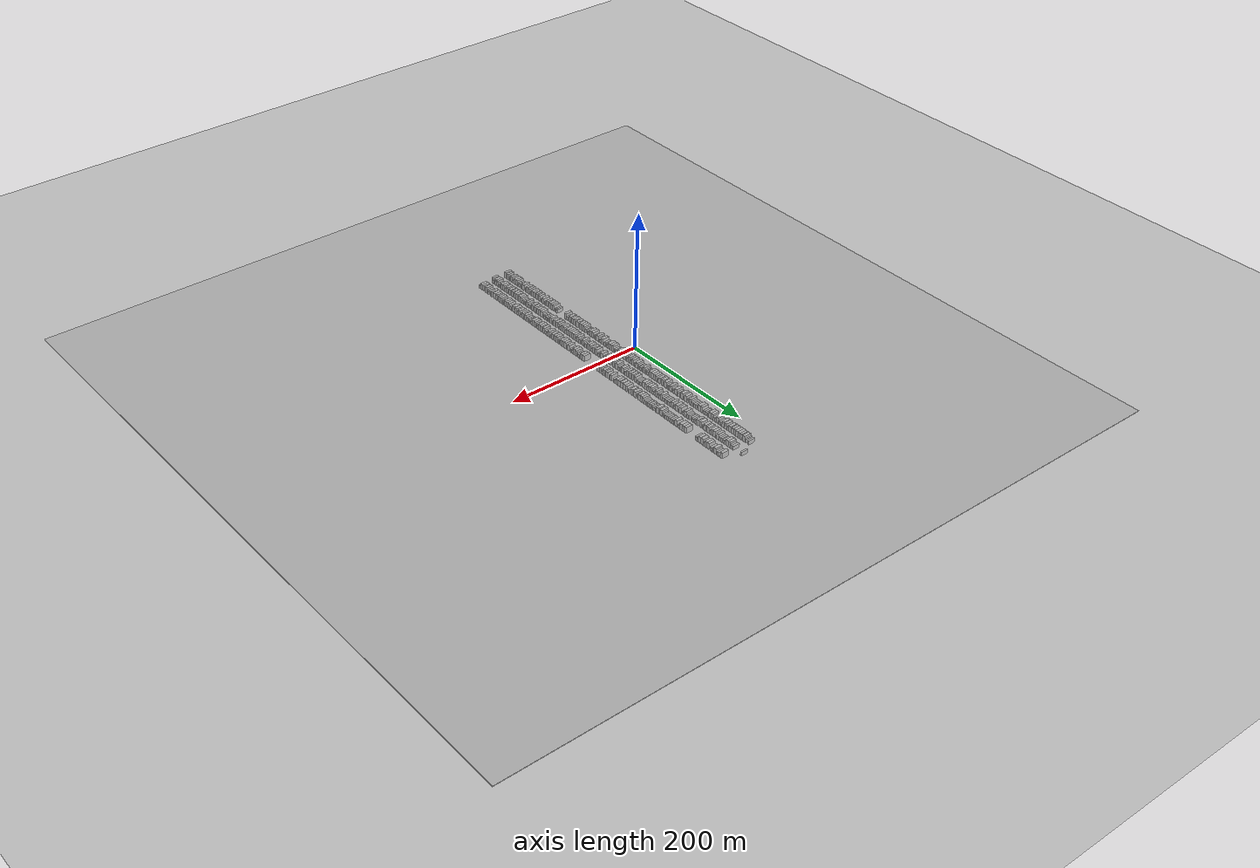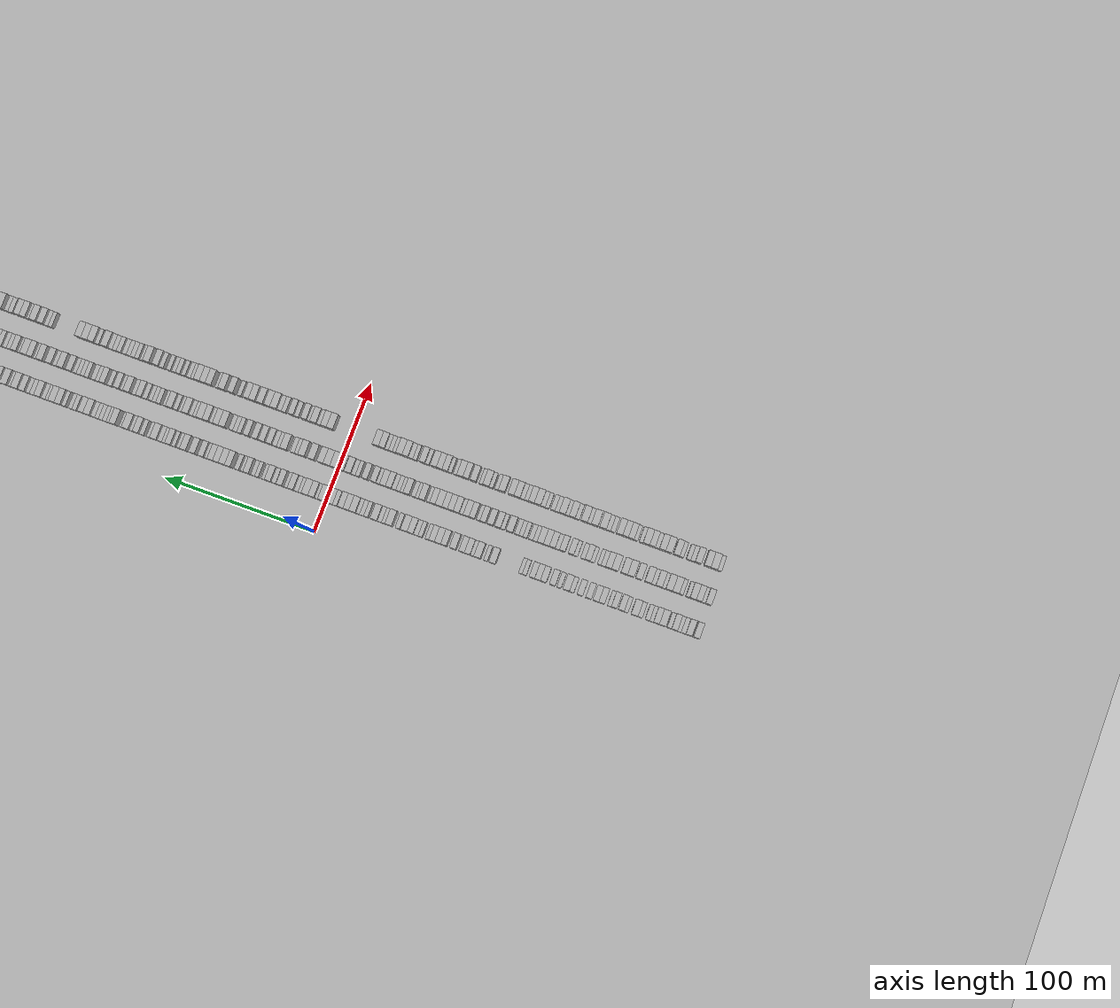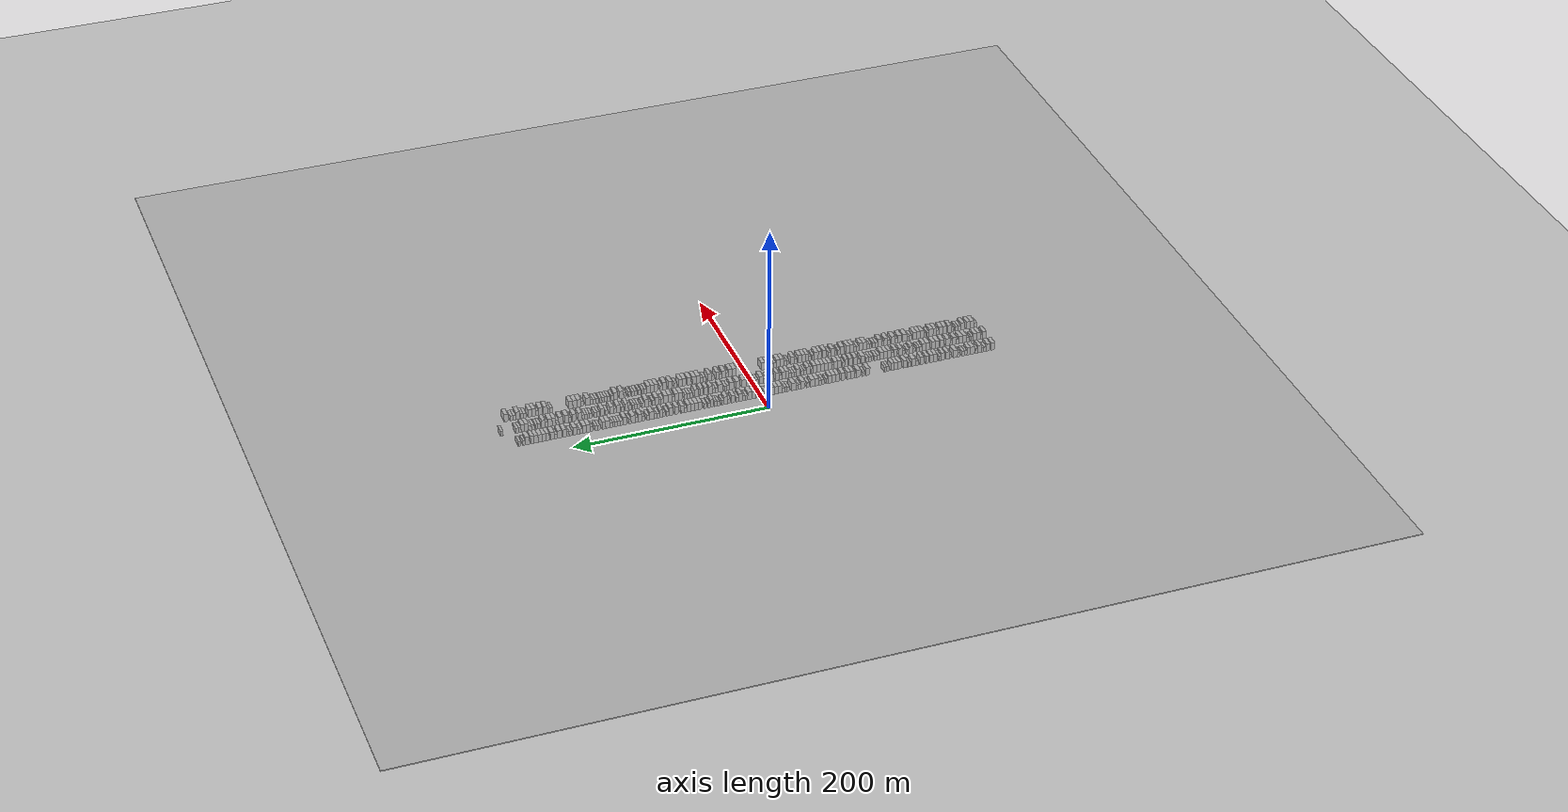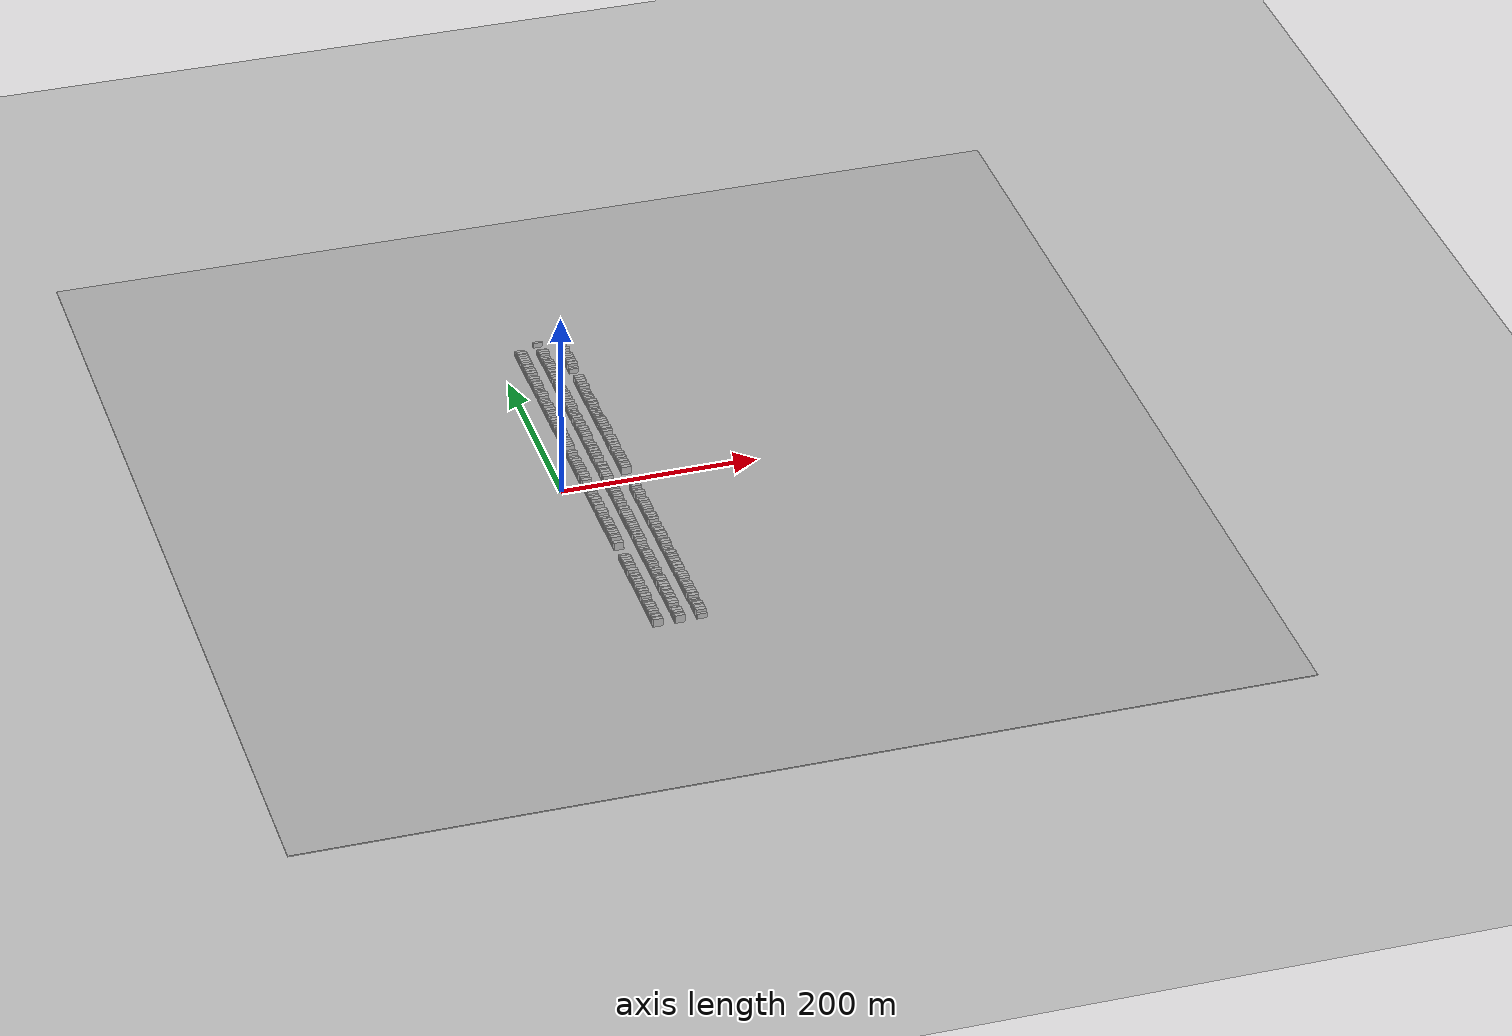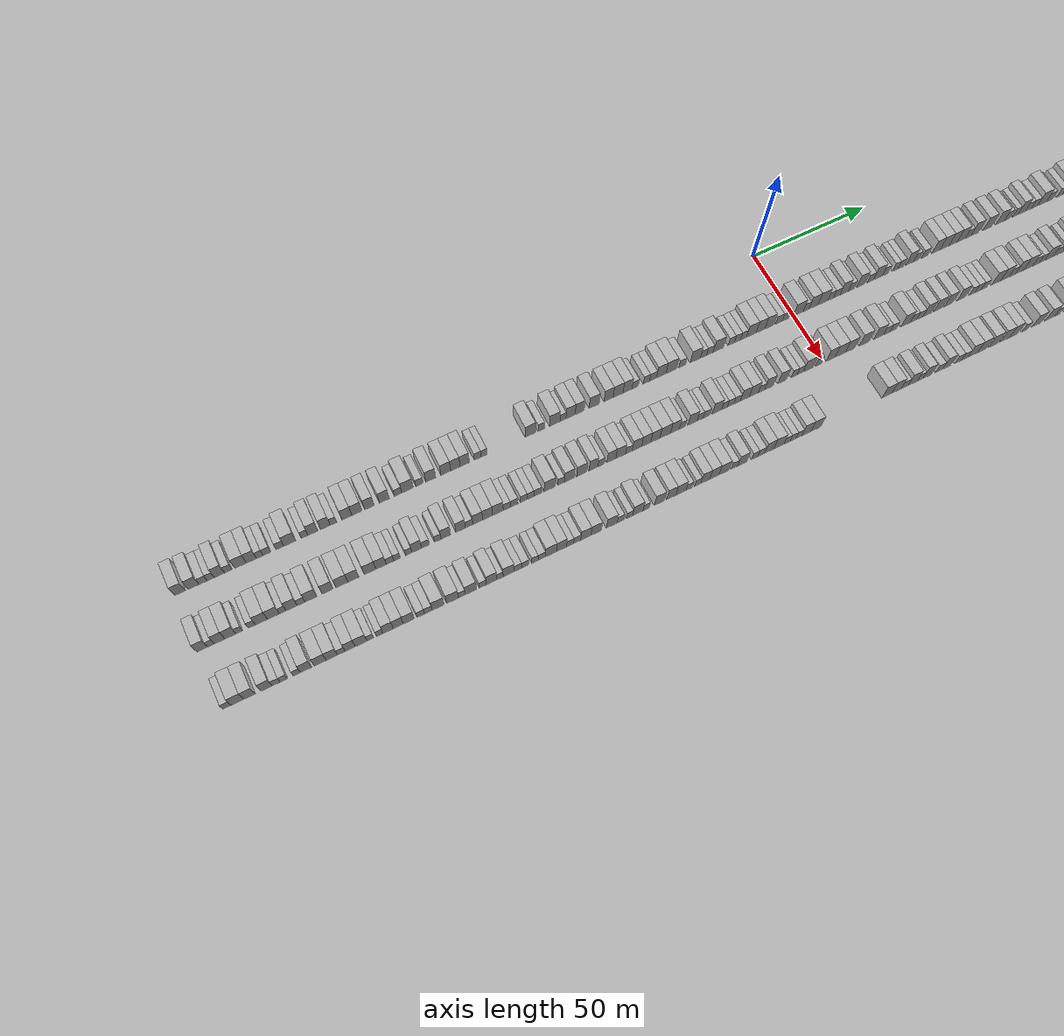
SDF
<?xml version="1.0" encoding="utf-8"?>

<sdf version="1.6">

   <world name="default">

      <gui fullscreen="0">

         <camera name="user_camera">

            <pose>-15 0 4.57585 0 0 0</pose>

            <view_controller>orbit</view_controller>

         </camera>

      </gui>

      <scene>

         <sky>

           <clouds>

             <speed>12</speed>

           </clouds>

         </sky>

         <ambient>0.4 0.4 0.4 1</ambient>

         <background>0.7 0.7 0.7 1</background>

         <shadows>1</shadows>

      </scene>

      <gravity>0 0 -9.8066</gravity>

      <magnetic_field>6e-06 2.3e-05 -4.2e-05</magnetic_field>

      <physics default="0" name="default_physics" type="ode">

         <ode>

            <solver>

               <type>quick</type>

               <iters>10</iters>

               <sor>1.0</sor>

               <use_dynamic_moi_rescaling>0</use_dynamic_moi_rescaling>

            </solver>

            <constraints>

               <cfm>0</cfm>

               <erp>0.2</erp>

               <contact_max_correcting_vel>100</contact_max_correcting_vel>

               <contact_surface_layer>0.001</contact_surface_layer>

            </constraints>

         </ode>

         <max_step_size>0.004</max_step_size>

         <real_time_factor>1</real_time_factor>

         <real_time_update_rate>250</real_time_update_rate>

      </physics>

      <light name="sun" type="directional">

         <cast_shadows>1</cast_shadows>

         <pose>0 0 10 0 0 0</pose>

         <diffuse>0.8 0.8 0.8 1</diffuse>

         <specular>0.2 0.2 0.2 1</specular>

         <attenuation>

            <range>1000</range>

            <constant>0.9</constant>

            <linear>0.01</linear>

            <quadratic>0.001</quadratic>

         </attenuation>

         <direction>-0.5 0.1 -0.9</direction>

      </light>

      <include>

         <name>ground_plane_1</name>

         <uri>model://HANNAS_ground_plane</uri>

         <pose>0 0 0  0 0 0</pose>

      </include>

      <include>

         <name>ground_plane_2</name>

         <uri>model://HANNAS_ground_plane</uri>

         <pose>100 0 0  0 0 0</pose>

      </include>

      <model name="building_1">

         <static>1</static>

         <pose frame="">25.0000 -246.0321 0 0.000000 0.000000 0.000000</pose>

         <link name="link">

            <pose frame="">0 0 4.50 0 0 0</pose>

            <collision name="collision">

               <geometry>

                  <box>

                     <size>10.0000 3.9358 9.0000</size>

                  </box>

               </geometry>

               <max_contacts>10</max_contacts>

               <surface>

                  <contact>

                     <ode/>

                  </contact>

                  <bounce/>

                  <friction>

                     <torsional>

                        <ode/>

                     </torsional>

                     <ode/>

                  </friction>

               </surface>

            </collision>

            <visual name="visual">

               <cast_shadows>0</cast_shadows>

               <geometry>

                  <box>

                     <size>10.0000 3.9358 9.0000</size>

                  </box>

               </geometry>

               <material>

                  <script>

                     <uri>model://HANNAS_wall/materials/scripts</uri>

                     <uri>model://HANNAS_wall/materials/textures</uri>

                     <name>vrc/HANNAS_wall</name>

                  </script>

               </material>

            </visual>

            <self_collide>0</self_collide>

            <enable_wind>0</enable_wind>

            <kinematic>0</kinematic>

         </link>

      </model>

      <model name="building_2">

         <static>1</static>

         <pose frame="">25.0000 -241.0633 0 0.000000 0.000000 0.000000</pose>

         <link name="link">

            <pose frame="">0 0 4.50 0 0 0</pose>

            <collision name="collision">

               <geometry>

                  <box>

                     <size>10.0000 4.0018 9.0000</size>

                  </box>

               </geometry>

               <max_contacts>10</max_contacts>

               <surface>

                  <contact>

                     <ode/>

                  </contact>

                  <bounce/>

                  <friction>

                     <torsional>

                        <ode/>

                     </torsional>

                     <ode/>

                  </friction>

               </surface>

            </collision>

            <visual name="visual">

               <cast_shadows>0</cast_shadows>

               <geometry>

                  <box>

                     <size>10.0000 4.0018 9.0000</size>

                  </box>

               </geometry>

               <material>

                  <script>

                     <uri>model://HANNAS_wall/materials/scripts</uri>

                     <uri>model://HANNAS_wall/materials/textures</uri>

                     <name>vrc/HANNAS_wall</name>

                  </script>

               </material>

            </visual>

            <self_collide>0</self_collide>

            <enable_wind>0</enable_wind>

            <kinematic>0</kinematic>

         </link>

      </model>

      <model name="building_3">

         <static>1</static>

         <pose frame="">25.0000 -237.5678 0 0.000000 0.000000 0.000000</pose>

         <link name="link">

            <pose frame="">0 0 3.00 0 0 0</pose>

            <collision name="collision">

               <geometry>

                  <box>

                     <size>10.0000 2.9891 6.0000</size>

                  </box>

               </geometry>

               <max_contacts>10</max_contacts>

               <surface>

                  <contact>

                     <ode/>

                  </contact>

                  <bounce/>

                  <friction>

                     <torsional>

                        <ode/>

                     </torsional>

                     <ode/>

                  </friction>

               </surface>

            </collision>

            <visual name="visual">

               <cast_shadows>0</cast_shadows>

               <geometry>

                  <box>

                     <size>10.0000 2.9891 6.0000</size>

                  </box>

               </geometry>

               <material>

                  <script>

                     <uri>model://HANNAS_wall/materials/scripts</uri>

                     <uri>model://HANNAS_wall/materials/textures</uri>

                     <name>vrc/HANNAS_wall</name>

                  </script>

               </material>

            </visual>

            <self_collide>0</self_collide>

            <enable_wind>0</enable_wind>

            <kinematic>0</kinematic>

         </link>

      </model>

      <model name="building_4">

         <static>1</static>

         <pose frame="">25.0000 -234.7901 0 0.000000 0.000000 0.000000</pose>

         <link name="link">

            <pose frame="">0 0 3.00 0 0 0</pose>

            <collision name="collision">

               <geometry>

                  <box>

                     <size>10.0000 2.5665 6.0000</size>

                  </box>

               </geometry>

               <max_contacts>10</max_contacts>

               <surface>

                  <contact>

                     <ode/>

                  </contact>

                  <bounce/>

                  <friction>

                     <torsional>

                        <ode/>

                     </torsional>

                     <ode/>

                  </friction>

               </surface>

            </collision>

            <visual name="visual">

               <cast_shadows>0</cast_shadows>

               <geometry>

                  <box>

                     <size>10.0000 2.5665 6.0000</size>

                  </box>

               </geometry>

               <material>

                  <script>

                     <uri>model://HANNAS_wall/materials/scripts</uri>

                     <uri>model://HANNAS_wall/materials/textures</uri>

                     <name>vrc/HANNAS_wall</name>

                  </script>

               </material>

            </visual>

            <self_collide>0</self_collide>

            <enable_wind>0</enable_wind>

            <kinematic>0</kinematic>

         </link>

      </model>

      <model name="building_5">

         <static>1</static>

         <pose frame="">25.0000 -231.6362 0 0.000000 0.000000 0.000000</pose>

         <link name="link">

            <pose frame="">0 0 4.50 0 0 0</pose>

            <collision name="collision">

               <geometry>

                  <box>

                     <size>10.0000 3.7411 9.0000</size>

                  </box>

               </geometry>

               <max_contacts>10</max_contacts>

               <surface>

                  <contact>

                     <ode/>

                  </contact>

                  <bounce/>

                  <friction>

                     <torsional>

                        <ode/>

                     </torsional>

                     <ode/>

                  </friction>

               </surface>

            </collision>

            <visual name="visual">

               <cast_shadows>0</cast_shadows>

               <geometry>

                  <box>

                     <size>10.0000 3.7411 9.0000</size>

                  </box>

               </geometry>

               <material>

                  <script>

                     <uri>model://HANNAS_wall/materials/scripts</uri>

                     <uri>model://HANNAS_wall/materials/textures</uri>

                     <name>vrc/HANNAS_wall</name>

                  </script>

               </material>

            </visual>

            <self_collide>0</self_collide>

            <enable_wind>0</enable_wind>

            <kinematic>0</kinematic>

         </link>

      </model>

      <model name="building_6">

         <static>1</static>

         <pose frame="">25.0000 -228.3736 0 0.000000 0.000000 0.000000</pose>

         <link name="link">

            <pose frame="">0 0 3.00 0 0 0</pose>

            <collision name="collision">

               <geometry>

                  <box>

                     <size>10.0000 2.7841 6.0000</size>

                  </box>

               </geometry>

               <max_contacts>10</max_contacts>

               <surface>

                  <contact>

                     <ode/>

                  </contact>

                  <bounce/>

                  <friction>

                     <torsional>

                        <ode/>

                     </torsional>

                     <ode/>

                  </friction>

               </surface>

            </collision>

            <visual name="visual">

               <cast_shadows>0</cast_shadows>

               <geometry>

                  <box>

                     <size>10.0000 2.7841 6.0000</size>

                  </box>

               </geometry>

               <material>

                  <script>

                     <uri>model://HANNAS_wall/materials/scripts</uri>

                     <uri>model://HANNAS_wall/materials/textures</uri>

                     <name>vrc/HANNAS_wall</name>

                  </script>

               </material>

            </visual>

            <self_collide>0</self_collide>

            <enable_wind>0</enable_wind>

            <kinematic>0</kinematic>

         </link>

      </model>

      <model name="building_7">

         <static>1</static>

         <pose frame="">25.0000 -223.8001 0 0.000000 0.000000 0.000000</pose>

         <link name="link">

            <pose frame="">0 0 4.50 0 0 0</pose>

            <collision name="collision">

               <geometry>

                  <box>

                     <size>10.0000 4.3630 9.0000</size>

                  </box>

               </geometry>

               <max_contacts>10</max_contacts>

               <surface>

                  <contact>

                     <ode/>

                  </contact>

                  <bounce/>

                  <friction>

                     <torsional>

                        <ode/>

                     </torsional>

                     <ode/>

                  </friction>

               </surface>

            </collision>

            <visual name="visual">

               <cast_shadows>0</cast_shadows>

               <geometry>

                  <box>

                     <size>10.0000 4.3630 9.0000</size>

                  </box>

               </geometry>

               <material>

                  <script>

                     <uri>model://HANNAS_wall/materials/scripts</uri>

                     <uri>model://HANNAS_wall/materials/textures</uri>

                     <name>vrc/HANNAS_wall</name>

                  </script>

               </material>

            </visual>

            <self_collide>0</self_collide>

            <enable_wind>0</enable_wind>

            <kinematic>0</kinematic>

         </link>

      </model>

      <model name="building_8">

         <static>1</static>

         <pose frame="">25.0000 -219.7464 0 0.000000 0.000000 0.000000</pose>

         <link name="link">

            <pose frame="">0 0 4.50 0 0 0</pose>

            <collision name="collision">

               <geometry>

                  <box>

                     <size>10.0000 3.7443 9.0000</size>

                  </box>

               </geometry>

               <max_contacts>10</max_contacts>

               <surface>

                  <contact>

                     <ode/>

                  </contact>

                  <bounce/>

                  <friction>

                     <torsional>

                        <ode/>

                     </torsional>

                     <ode/>

                  </friction>

               </surface>

            </collision>

            <visual name="visual">

               <cast_shadows>0</cast_shadows>

               <geometry>

                  <box>

                     <size>10.0000 3.7443 9.0000</size>

                  </box>

               </geometry>

               <material>

                  <script>

                     <uri>model://HANNAS_wall/materials/scripts</uri>

                     <uri>model://HANNAS_wall/materials/textures</uri>

                     <name>vrc/HANNAS_wall</name>

                  </script>

               </material>

            </visual>

            <self_collide>0</self_collide>

            <enable_wind>0</enable_wind>

            <kinematic>0</kinematic>

         </link>

      </model>

      <model name="building_9">

         <static>1</static>

         <pose frame="">25.0000 -216.6499 0 0.000000 0.000000 0.000000</pose>

         <link name="link">

            <pose frame="">0 0 3.00 0 0 0</pose>

            <collision name="collision">

               <geometry>

                  <box>

                     <size>10.0000 2.4486 6.0000</size>

                  </box>

               </geometry>

               <max_contacts>10</max_contacts>

               <surface>

                  <contact>

                     <ode/>

                  </contact>

                  <bounce/>

                  <friction>

                     <torsional>

                        <ode/>

                     </torsional>

                     <ode/>

                  </friction>

               </surface>

            </collision>

            <visual name="visual">

               <cast_shadows>0</cast_shadows>

               <geometry>

                  <box>

                     <size>10.0000 2.4486 6.0000</size>

                  </box>

               </geometry>

               <material>

                  <script>

                     <uri>model://HANNAS_wall/materials/scripts</uri>

                     <uri>model://HANNAS_wall/materials/textures</uri>

                     <name>vrc/HANNAS_wall</name>

                  </script>

               </material>

            </visual>

            <self_collide>0</self_collide>

            <enable_wind>0</enable_wind>

            <kinematic>0</kinematic>

         </link>

      </model>

      <model name="building_10">

         <static>1</static>

         <pose frame="">25.0000 -214.0014 0 0.000000 0.000000 0.000000</pose>

         <link name="link">

            <pose frame="">0 0 3.00 0 0 0</pose>

            <collision name="collision">

               <geometry>

                  <box>

                     <size>10.0000 2.8485 6.0000</size>

                  </box>

               </geometry>

               <max_contacts>10</max_contacts>

               <surface>

                  <contact>

                     <ode/>

                  </contact>

                  <bounce/>

                  <friction>

                     <torsional>

                        <ode/>

                     </torsional>

                     <ode/>

                  </friction>

               </surface>

            </collision>

            <visual name="visual">

               <cast_shadows>0</cast_shadows>

               <geometry>

                  <box>

                     <size>10.0000 2.8485 6.0000</size>

                  </box>

               </geometry>

               <material>

                  <script>

                     <uri>model://HANNAS_wall/materials/scripts</uri>

                     <uri>model://HANNAS_wall/materials/textures</uri>

                     <name>vrc/HANNAS_wall</name>

                  </script>

               </material>

            </visual>

            <self_collide>0</self_collide>

            <enable_wind>0</enable_wind>

            <kinematic>0</kinematic>

         </link>

      </model>

      <model name="building_11">

         <static>1</static>

         <pose frame="">25.0000 -209.1269 0 0.000000 0.000000 0.000000</pose>

         <link name="link">

            <pose frame="">0 0 3.00 0 0 0</pose>

            <collision name="collision">

               <geometry>

                  <box>

                     <size>10.0000 2.9004 6.0000</size>

                  </box>

               </geometry>

               <max_contacts>10</max_contacts>

               <surface>

                  <contact>

                     <ode/>

                  </contact>

                  <bounce/>

                  <friction>

                     <torsional>

                        <ode/>

                     </torsional>

                     <ode/>

                  </friction>

               </surface>

            </collision>

            <visual name="visual">

               <cast_shadows>0</cast_shadows>

               <geometry>

                  <box>

                     <size>10.0000 2.9004 6.0000</size>

                  </box>

               </geometry>

               <material>

                  <script>

                     <uri>model://HANNAS_wall/materials/scripts</uri>

                     <uri>model://HANNAS_wall/materials/textures</uri>

                     <name>vrc/HANNAS_wall</name>

                  </script>

               </material>

            </visual>

            <self_collide>0</self_collide>

            <enable_wind>0</enable_wind>

            <kinematic>0</kinematic>

         </link>

      </model>

      <model name="building_12">

         <static>1</static>

         <pose frame="">25.0000 -205.4417 0 0.000000 0.000000 0.000000</pose>

         <link name="link">

            <pose frame="">0 0 4.50 0 0 0</pose>

            <collision name="collision">

               <geometry>

                  <box>

                     <size>10.0000 4.4702 9.0000</size>

                  </box>

               </geometry>

               <max_contacts>10</max_contacts>

               <surface>

                  <contact>

                     <ode/>

                  </contact>

                  <bounce/>

                  <friction>

                     <torsional>

                        <ode/>

                     </torsional>

                     <ode/>

                  </friction>

               </surface>

            </collision>

            <visual name="visual">

               <cast_shadows>0</cast_shadows>

               <geometry>

                  <box>

                     <size>10.0000 4.4702 9.0000</size>

                  </box>

               </geometry>

               <material>

                  <script>

                     <uri>model://HANNAS_wall/materials/scripts</uri>

                     <uri>model://HANNAS_wall/materials/textures</uri>

                     <name>vrc/HANNAS_wall</name>

                  </script>

               </material>

            </visual>

            <self_collide>0</self_collide>

            <enable_wind>0</enable_wind>

            <kinematic>0</kinematic>

         </link>

      </model>

      <model name="building_13">

         <static>1</static>

         <pose frame="">25.0000 -199.8999 0 0.000000 0.000000 0.000000</pose>

         <link name="link">

            <pose frame="">0 0 3.00 0 0 0</pose>

            <collision name="collision">

               <geometry>

                  <box>

                     <size>10.0000 2.6133 6.0000</size>

                  </box>

               </geometry>

               <max_contacts>10</max_contacts>

               <surface>

                  <contact>

                     <ode/>

                  </contact>

                  <bounce/>

                  <friction>

                     <torsional>

                        <ode/>

                     </torsional>

                     <ode/>

                  </friction>

               </surface>

            </collision>

            <visual name="visual">

               <cast_shadows>0</cast_shadows>

               <geometry>

                  <box>

                     <size>10.0000 2.6133 6.0000</size>

                  </box>

               </geometry>

               <material>

                  <script>

                     <uri>model://HANNAS_wall/materials/scripts</uri>

                     <uri>model://HANNAS_wall/materials/textures</uri>

                     <name>vrc/HANNAS_wall</name>

                  </script>

               </material>

            </visual>

            <self_collide>0</self_collide>

            <enable_wind>0</enable_wind>

            <kinematic>0</kinematic>

         </link>

      </model>

      <model name="building_14">

         <static>1</static>

         <pose frame="">25.0000 -196.7262 0 0.000000 0.000000 0.000000</pose>

         <link name="link">

            <pose frame="">0 0 4.50 0 0 0</pose>

            <collision name="collision">

               <geometry>

                  <box>

                     <size>10.0000 3.7342 9.0000</size>

                  </box>

               </geometry>

               <max_contacts>10</max_contacts>

               <surface>

                  <contact>

                     <ode/>

                  </contact>

                  <bounce/>

                  <friction>

                     <torsional>

                        <ode/>

                     </torsional>

                     <ode/>

                  </friction>

               </surface>

            </collision>

            <visual name="visual">

               <cast_shadows>0</cast_shadows>

               <geometry>

                  <box>

                     <size>10.0000 3.7342 9.0000</size>

                  </box>

               </geometry>

               <material>

                  <script>

                     <uri>model://HANNAS_wall/materials/scripts</uri>

                     <uri>model://HANNAS_wall/materials/textures</uri>

                     <name>vrc/HANNAS_wall</name>

                  </script>

               </material>

            </visual>

            <self_collide>0</self_collide>

            <enable_wind>0</enable_wind>

            <kinematic>0</kinematic>

         </link>

      </model>

      <model name="building_15">

         <static>1</static>

         <pose frame="">25.0000 -192.0377 0 0.000000 0.000000 0.000000</pose>

         <link name="link">

            <pose frame="">0 0 4.50 0 0 0</pose>

            <collision name="collision">

               <geometry>

                  <box>

                     <size>10.0000 3.6429 9.0000</size>

                  </box>

               </geometry>

               <max_contacts>10</max_contacts>

               <surface>

                  <contact>

                     <ode/>

                  </contact>

                  <bounce/>

                  <friction>

                     <torsional>

                        <ode/>

                     </torsional>

                     <ode/>

                  </friction>

               </surface>

            </collision>

            <visual name="visual">

               <cast_shadows>0</cast_shadows>

               <geometry>

                  <box>

                     <size>10.0000 3.6429 9.0000</size>

                  </box>

               </geometry>

               <material>

                  <script>

                     <uri>model://HANNAS_wall/materials/scripts</uri>

                     <uri>model://HANNAS_wall/materials/textures</uri>

                     <name>vrc/HANNAS_wall</name>

                  </script>

               </material>

            </visual>

            <self_collide>0</self_collide>

            <enable_wind>0</enable_wind>

            <kinematic>0</kinematic>

         </link>

      </model>

      <model name="building_16">

         <static>1</static>

         <pose frame="">25.0000 -188.9643 0 0.000000 0.000000 0.000000</pose>

         <link name="link">

            <pose frame="">0 0 3.00 0 0 0</pose>

            <collision name="collision">

               <geometry>

                  <box>

                     <size>10.0000 2.5039 6.0000</size>

                  </box>

               </geometry>

               <max_contacts>10</max_contacts>

               <surface>

                  <contact>

                     <ode/>

                  </contact>

                  <bounce/>

                  <friction>

                     <torsional>

                        <ode/>

                     </torsional>

                     <ode/>

                  </friction>

               </surface>

            </collision>

            <visual name="visual">

               <cast_shadows>0</cast_shadows>

               <geometry>

                  <box>

                     <size>10.0000 2.5039 6.0000</size>

                  </box>

               </geometry>

               <material>

                  <script>

                     <uri>model://HANNAS_wall/materials/scripts</uri>

                     <uri>model://HANNAS_wall/materials/textures</uri>

                     <name>vrc/HANNAS_wall</name>

                  </script>

               </material>

            </visual>

            <self_collide>0</self_collide>

            <enable_wind>0</enable_wind>

            <kinematic>0</kinematic>

         </link>

      </model>

      <model name="building_17">

         <static>1</static>

         <pose frame="">25.0000 -183.8332 0 0.000000 0.000000 0.000000</pose>

         <link name="link">

            <pose frame="">0 0 4.50 0 0 0</pose>

            <collision name="collision">

               <geometry>

                  <box>

                     <size>10.0000 3.7584 9.0000</size>

                  </box>

               </geometry>

               <max_contacts>10</max_contacts>

               <surface>

                  <contact>

                     <ode/>

                  </contact>

                  <bounce/>

                  <friction>

                     <torsional>

                        <ode/>

                     </torsional>

                     <ode/>

                  </friction>

               </surface>

            </collision>

            <visual name="visual">

               <cast_shadows>0</cast_shadows>

               <geometry>

                  <box>

                     <size>10.0000 3.7584 9.0000</size>

                  </box>

               </geometry>

               <material>

                  <script>

                     <uri>model://HANNAS_wall/materials/scripts</uri>

                     <uri>model://HANNAS_wall/materials/textures</uri>

                     <name>vrc/HANNAS_wall</name>

                  </script>

               </material>

            </visual>

            <self_collide>0</self_collide>

            <enable_wind>0</enable_wind>

            <kinematic>0</kinematic>

         </link>

      </model>

      <model name="building_18">

         <static>1</static>

         <pose frame="">25.0000 -179.9946 0 0.000000 0.000000 0.000000</pose>

         <link name="link">

            <pose frame="">0 0 4.50 0 0 0</pose>

            <collision name="collision">

               <geometry>

                  <box>

                     <size>10.0000 3.9188 9.0000</size>

                  </box>

               </geometry>

               <max_contacts>10</max_contacts>

               <surface>

                  <contact>

                     <ode/>

                  </contact>

                  <bounce/>

                  <friction>

                     <torsional>

                        <ode/>

                     </torsional>

                     <ode/>

                  </friction>

               </surface>

            </collision>

            <visual name="visual">

               <cast_shadows>0</cast_shadows>

               <geometry>

                  <box>

                     <size>10.0000 3.9188 9.0000</size>

                  </box>

               </geometry>

               <material>

                  <script>

                     <uri>model://HANNAS_wall/materials/scripts</uri>

                     <uri>model://HANNAS_wall/materials/textures</uri>

                     <name>vrc/HANNAS_wall</name>

                  </script>

               </material>

            </visual>

            <self_collide>0</self_collide>

            <enable_wind>0</enable_wind>

            <kinematic>0</kinematic>

         </link>

      </model>

      <model name="building_19">

         <static>1</static>

         <pose frame="">25.0000 -175.1993 0 0.000000 0.000000 0.000000</pose>

         <link name="link">

            <pose frame="">0 0 4.50 0 0 0</pose>

            <collision name="collision">

               <geometry>

                  <box>

                     <size>10.0000 3.6717 9.0000</size>

                  </box>

               </geometry>

               <max_contacts>10</max_contacts>

               <surface>

                  <contact>

                     <ode/>

                  </contact>

                  <bounce/>

                  <friction>

                     <torsional>

                        <ode/>

                     </torsional>

                     <ode/>

                  </friction>

               </surface>

            </collision>

            <visual name="visual">

               <cast_shadows>0</cast_shadows>

               <geometry>

                  <box>

                     <size>10.0000 3.6717 9.0000</size>

                  </box>

               </geometry>

               <material>

                  <script>

                     <uri>model://HANNAS_wall/materials/scripts</uri>

                     <uri>model://HANNAS_wall/materials/textures</uri>

                     <name>vrc/HANNAS_wall</name>

                  </script>

               </material>

            </visual>

            <self_collide>0</self_collide>

            <enable_wind>0</enable_wind>

            <kinematic>0</kinematic>

         </link>

      </model>

      <model name="building_20">

         <static>1</static>

         <pose frame="">25.0000 -169.4626 0 0.000000 0.000000 0.000000</pose>

         <link name="link">

            <pose frame="">0 0 4.50 0 0 0</pose>

            <collision name="collision">

               <geometry>

                  <box>

                     <size>10.0000 3.8018 9.0000</size>

                  </box>

               </geometry>

               <max_contacts>10</max_contacts>

               <surface>

                  <contact>

                     <ode/>

                  </contact>

                  <bounce/>

                  <friction>

                     <torsional>

                        <ode/>

                     </torsional>

                     <ode/>

                  </friction>

               </surface>

            </collision>

            <visual name="visual">

               <cast_shadows>0</cast_shadows>

               <geometry>

                  <box>

                     <size>10.0000 3.8018 9.0000</size>

                  </box>

               </geometry>

               <material>

                  <script>

                     <uri>model://HANNAS_wall/materials/scripts</uri>

                     <uri>model://HANNAS_wall/materials/textures</uri>

                     <name>vrc/HANNAS_wall</name>

                  </script>

               </material>

            </visual>

            <self_collide>0</self_collide>

            <enable_wind>0</enable_wind>

            <kinematic>0</kinematic>

         </link>

      </model>

      <model name="building_21">

         <static>1</static>

         <pose frame="">25.0000 -164.1286 0 0.000000 0.000000 0.000000</pose>

         <link name="link">

            <pose frame="">0 0 3.00 0 0 0</pose>

            <collision name="collision">

               <geometry>

                  <box>

                     <size>10.0000 2.8662 6.0000</size>

                  </box>

               </geometry>

               <max_contacts>10</max_contacts>

               <surface>

                  <contact>

                     <ode/>

                  </contact>

                  <bounce/>

                  <friction>

                     <torsional>

                        <ode/>

                     </torsional>

                     <ode/>

                  </friction>

               </surface>

            </collision>

            <visual name="visual">

               <cast_shadows>0</cast_shadows>

               <geometry>

                  <box>

                     <size>10.0000 2.8662 6.0000</size>

                  </box>

               </geometry>

               <material>

                  <script>

                     <uri>model://HANNAS_wall/materials/scripts</uri>

                     <uri>model://HANNAS_wall/materials/textures</uri>

                     <name>vrc/HANNAS_wall</name>

                  </script>

               </material>

            </visual>

            <self_collide>0</self_collide>

            <enable_wind>0</enable_wind>

            <kinematic>0</kinematic>

         </link>

      </model>

      <model name="building_22">

         <static>1</static>

         <pose frame="">25.0000 -160.4556 0 0.000000 0.000000 0.000000</pose>

         <link name="link">

            <pose frame="">0 0 4.50 0 0 0</pose>

            <collision name="collision">

               <geometry>

                  <box>

                     <size>10.0000 4.4797 9.0000</size>

                  </box>

               </geometry>

               <max_contacts>10</max_contacts>

               <surface>

                  <contact>

                     <ode/>

                  </contact>

                  <bounce/>

                  <friction>

                     <torsional>

                        <ode/>

                     </torsional>

                     <ode/>

                  </friction>

               </surface>

            </collision>

            <visual name="visual">

               <cast_shadows>0</cast_shadows>

               <geometry>

                  <box>

                     <size>10.0000 4.4797 9.0000</size>

                  </box>

               </geometry>

               <material>

                  <script>

                     <uri>model://HANNAS_wall/materials/scripts</uri>

                     <uri>model://HANNAS_wall/materials/textures</uri>

                     <name>vrc/HANNAS_wall</name>

                  </script>

               </material>

            </visual>

            <self_collide>0</self_collide>

            <enable_wind>0</enable_wind>

            <kinematic>0</kinematic>

         </link>

      </model>

      <model name="building_23">

         <static>1</static>

         <pose frame="">25.0000 -155.7748 0 0.000000 0.000000 0.000000</pose>

         <link name="link">

            <pose frame="">0 0 3.00 0 0 0</pose>

            <collision name="collision">

               <geometry>

                  <box>

                     <size>10.0000 2.8818 6.0000</size>

                  </box>

               </geometry>

               <max_contacts>10</max_contacts>

               <surface>

                  <contact>

                     <ode/>

                  </contact>

                  <bounce/>

                  <friction>

                     <torsional>

                        <ode/>

                     </torsional>

                     <ode/>

                  </friction>

               </surface>

            </collision>

            <visual name="visual">

               <cast_shadows>0</cast_shadows>

               <geometry>

                  <box>

                     <size>10.0000 2.8818 6.0000</size>

                  </box>

               </geometry>

               <material>

                  <script>

                     <uri>model://HANNAS_wall/materials/scripts</uri>

                     <uri>model://HANNAS_wall/materials/textures</uri>

                     <name>vrc/HANNAS_wall</name>

                  </script>

               </material>

            </visual>

            <self_collide>0</self_collide>

            <enable_wind>0</enable_wind>

            <kinematic>0</kinematic>

         </link>

      </model>

      <model name="building_24">

         <static>1</static>

         <pose frame="">25.0000 -151.3680 0 0.000000 0.000000 0.000000</pose>

         <link name="link">

            <pose frame="">0 0 4.50 0 0 0</pose>

            <collision name="collision">

               <geometry>

                  <box>

                     <size>10.0000 3.9319 9.0000</size>

                  </box>

               </geometry>

               <max_contacts>10</max_contacts>

               <surface>

                  <contact>

                     <ode/>

                  </contact>

                  <bounce/>

                  <friction>

                     <torsional>

                        <ode/>

                     </torsional>

                     <ode/>

                  </friction>

               </surface>

            </collision>

            <visual name="visual">

               <cast_shadows>0</cast_shadows>

               <geometry>

                  <box>

                     <size>10.0000 3.9319 9.0000</size>

                  </box>

               </geometry>

               <material>

                  <script>

                     <uri>model://HANNAS_wall/materials/scripts</uri>

                     <uri>model://HANNAS_wall/materials/textures</uri>

                     <name>vrc/HANNAS_wall</name>

                  </script>

               </material>

            </visual>

            <self_collide>0</self_collide>

            <enable_wind>0</enable_wind>

            <kinematic>0</kinematic>

         </link>

      </model>

      <model name="building_25">

         <static>1</static>

         <pose frame="">25.0000 -145.4583 0 0.000000 0.000000 0.000000</pose>

         <link name="link">

            <pose frame="">0 0 4.50 0 0 0</pose>

            <collision name="collision">

               <geometry>

                  <box>

                     <size>10.0000 3.8874 9.0000</size>

                  </box>

               </geometry>

               <max_contacts>10</max_contacts>

               <surface>

                  <contact>

                     <ode/>

                  </contact>

                  <bounce/>

                  <friction>

                     <torsional>

                        <ode/>

                     </torsional>

                     <ode/>

                  </friction>

               </surface>

            </collision>

            <visual name="visual">

               <cast_shadows>0</cast_shadows>

               <geometry>

                  <box>

                     <size>10.0000 3.8874 9.0000</size>

                  </box>

               </geometry>

               <material>

                  <script>

                     <uri>model://HANNAS_wall/materials/scripts</uri>

                     <uri>model://HANNAS_wall/materials/textures</uri>

                     <name>vrc/HANNAS_wall</name>

                  </script>

               </material>

            </visual>

            <self_collide>0</self_collide>

            <enable_wind>0</enable_wind>

            <kinematic>0</kinematic>

         </link>

      </model>

      <model name="building_26">

         <static>1</static>

         <pose frame="">25.0000 -141.6594 0 0.000000 0.000000 0.000000</pose>

         <link name="link">

            <pose frame="">0 0 4.50 0 0 0</pose>

            <collision name="collision">

               <geometry>

                  <box>

                     <size>10.0000 3.7105 9.0000</size>

                  </box>

               </geometry>

               <max_contacts>10</max_contacts>

               <surface>

                  <contact>

                     <ode/>

                  </contact>

                  <bounce/>

                  <friction>

                     <torsional>

                        <ode/>

                     </torsional>

                     <ode/>

                  </friction>

               </surface>

            </collision>

            <visual name="visual">

               <cast_shadows>0</cast_shadows>

               <geometry>

                  <box>

                     <size>10.0000 3.7105 9.0000</size>

                  </box>

               </geometry>

               <material>

                  <script>

                     <uri>model://HANNAS_wall/materials/scripts</uri>

                     <uri>model://HANNAS_wall/materials/textures</uri>

                     <name>vrc/HANNAS_wall</name>

                  </script>

               </material>

            </visual>

            <self_collide>0</self_collide>

            <enable_wind>0</enable_wind>

            <kinematic>0</kinematic>

         </link>

      </model>

      <model name="building_27">

         <static>1</static>

         <pose frame="">25.0000 -137.9797 0 0.000000 0.000000 0.000000</pose>

         <link name="link">

            <pose frame="">0 0 4.50 0 0 0</pose>

            <collision name="collision">

               <geometry>

                  <box>

                     <size>10.0000 3.6488 9.0000</size>

                  </box>

               </geometry>

               <max_contacts>10</max_contacts>

               <surface>

                  <contact>

                     <ode/>

                  </contact>

                  <bounce/>

                  <friction>

                     <torsional>

                        <ode/>

                     </torsional>

                     <ode/>

                  </friction>

               </surface>

            </collision>

            <visual name="visual">

               <cast_shadows>0</cast_shadows>

               <geometry>

                  <box>

                     <size>10.0000 3.6488 9.0000</size>

                  </box>

               </geometry>

               <material>

                  <script>

                     <uri>model://HANNAS_wall/materials/scripts</uri>

                     <uri>model://HANNAS_wall/materials/textures</uri>

                     <name>vrc/HANNAS_wall</name>

                  </script>

               </material>

            </visual>

            <self_collide>0</self_collide>

            <enable_wind>0</enable_wind>

            <kinematic>0</kinematic>

         </link>

      </model>

      <model name="building_28">

         <static>1</static>

         <pose frame="">25.0000 -132.8272 0 0.000000 0.000000 0.000000</pose>

         <link name="link">

            <pose frame="">0 0 3.00 0 0 0</pose>

            <collision name="collision">

               <geometry>

                  <box>

                     <size>10.0000 2.6561 6.0000</size>

                  </box>

               </geometry>

               <max_contacts>10</max_contacts>

               <surface>

                  <contact>

                     <ode/>

                  </contact>

                  <bounce/>

                  <friction>

                     <torsional>

                        <ode/>

                     </torsional>

                     <ode/>

                  </friction>

               </surface>

            </collision>

            <visual name="visual">

               <cast_shadows>0</cast_shadows>

               <geometry>

                  <box>

                     <size>10.0000 2.6561 6.0000</size>

                  </box>

               </geometry>

               <material>

                  <script>

                     <uri>model://HANNAS_wall/materials/scripts</uri>

                     <uri>model://HANNAS_wall/materials/textures</uri>

                     <name>vrc/HANNAS_wall</name>

                  </script>

               </material>

            </visual>

            <self_collide>0</self_collide>

            <enable_wind>0</enable_wind>

            <kinematic>0</kinematic>

         </link>

      </model>

      <model name="building_29">

         <static>1</static>

         <pose frame="">25.0000 -130.2861 0 0.000000 0.000000 0.000000</pose>

         <link name="link">

            <pose frame="">0 0 3.00 0 0 0</pose>

            <collision name="collision">

               <geometry>

                  <box>

                     <size>10.0000 2.4261 6.0000</size>

                  </box>

               </geometry>

               <max_contacts>10</max_contacts>

               <surface>

                  <contact>

                     <ode/>

                  </contact>

                  <bounce/>

                  <friction>

                     <torsional>

                        <ode/>

                     </torsional>

                     <ode/>

                  </friction>

               </surface>

            </collision>

            <visual name="visual">

               <cast_shadows>0</cast_shadows>

               <geometry>

                  <box>

                     <size>10.0000 2.4261 6.0000</size>

                  </box>

               </geometry>

               <material>

                  <script>

                     <uri>model://HANNAS_wall/materials/scripts</uri>

                     <uri>model://HANNAS_wall/materials/textures</uri>

                     <name>vrc/HANNAS_wall</name>

                  </script>

               </material>

            </visual>

            <self_collide>0</self_collide>

            <enable_wind>0</enable_wind>

            <kinematic>0</kinematic>

         </link>

      </model>

      <model name="building_30">

         <static>1</static>

         <pose frame="">25.0000 -111.6694 0 0.000000 0.000000 0.000000</pose>

         <link name="link">

            <pose frame="">0 0 4.50 0 0 0</pose>

            <collision name="collision">

               <geometry>

                  <box>

                     <size>10.0000 4.2691 9.0000</size>

                  </box>

               </geometry>

               <max_contacts>10</max_contacts>

               <surface>

                  <contact>

                     <ode/>

                  </contact>

                  <bounce/>

                  <friction>

                     <torsional>

                        <ode/>

                     </torsional>

                     <ode/>

                  </friction>

               </surface>

            </collision>

            <visual name="visual">

               <cast_shadows>0</cast_shadows>

               <geometry>

                  <box>

                     <size>10.0000 4.2691 9.0000</size>

                  </box>

               </geometry>

               <material>

                  <script>

                     <uri>model://HANNAS_wall/materials/scripts</uri>

                     <uri>model://HANNAS_wall/materials/textures</uri>

                     <name>vrc/HANNAS_wall</name>

                  </script>

               </material>

            </visual>

            <self_collide>0</self_collide>

            <enable_wind>0</enable_wind>

            <kinematic>0</kinematic>

         </link>

      </model>

      <model name="building_31">

         <static>1</static>

         <pose frame="">25.0000 -107.2250 0 0.000000 0.000000 0.000000</pose>

         <link name="link">

            <pose frame="">0 0 3.00 0 0 0</pose>

            <collision name="collision">

               <geometry>

                  <box>

                     <size>10.0000 2.6196 6.0000</size>

                  </box>

               </geometry>

               <max_contacts>10</max_contacts>

               <surface>

                  <contact>

                     <ode/>

                  </contact>

                  <bounce/>

                  <friction>

                     <torsional>

                        <ode/>

                     </torsional>

                     <ode/>

                  </friction>

               </surface>

            </collision>

            <visual name="visual">

               <cast_shadows>0</cast_shadows>

               <geometry>

                  <box>

                     <size>10.0000 2.6196 6.0000</size>

                  </box>

               </geometry>

               <material>

                  <script>

                     <uri>model://HANNAS_wall/materials/scripts</uri>

                     <uri>model://HANNAS_wall/materials/textures</uri>

                     <name>vrc/HANNAS_wall</name>

                  </script>

               </material>

            </visual>

            <self_collide>0</self_collide>

            <enable_wind>0</enable_wind>

            <kinematic>0</kinematic>

         </link>

      </model>

      <model name="building_32">

         <static>1</static>

         <pose frame="">25.0000 -101.7582 0 0.000000 0.000000 0.000000</pose>

         <link name="link">

            <pose frame="">0 0 4.50 0 0 0</pose>

            <collision name="collision">

               <geometry>

                  <box>

                     <size>10.0000 4.3139 9.0000</size>

                  </box>

               </geometry>

               <max_contacts>10</max_contacts>

               <surface>

                  <contact>

                     <ode/>

                  </contact>

                  <bounce/>

                  <friction>

                     <torsional>

                        <ode/>

                     </torsional>

                     <ode/>

                  </friction>

               </surface>

            </collision>

            <visual name="visual">

               <cast_shadows>0</cast_shadows>

               <geometry>

                  <box>

                     <size>10.0000 4.3139 9.0000</size>

                  </box>

               </geometry>

               <material>

                  <script>

                     <uri>model://HANNAS_wall/materials/scripts</uri>

                     <uri>model://HANNAS_wall/materials/textures</uri>

                     <name>vrc/HANNAS_wall</name>

                  </script>

               </material>

            </visual>

            <self_collide>0</self_collide>

            <enable_wind>0</enable_wind>

            <kinematic>0</kinematic>

         </link>

      </model>

      <model name="building_33">

         <static>1</static>

         <pose frame="">25.0000 -98.3903 0 0.000000 0.000000 0.000000</pose>

         <link name="link">

            <pose frame="">0 0 3.00 0 0 0</pose>

            <collision name="collision">

               <geometry>

                  <box>

                     <size>10.0000 2.4220 6.0000</size>

                  </box>

               </geometry>

               <max_contacts>10</max_contacts>

               <surface>

                  <contact>

                     <ode/>

                  </contact>

                  <bounce/>

                  <friction>

                     <torsional>

                        <ode/>

                     </torsional>

                     <ode/>

                  </friction>

               </surface>

            </collision>

            <visual name="visual">

               <cast_shadows>0</cast_shadows>

               <geometry>

                  <box>

                     <size>10.0000 2.4220 6.0000</size>

                  </box>

               </geometry>

               <material>

                  <script>

                     <uri>model://HANNAS_wall/materials/scripts</uri>

                     <uri>model://HANNAS_wall/materials/textures</uri>

                     <name>vrc/HANNAS_wall</name>

                  </script>

               </material>

            </visual>

            <self_collide>0</self_collide>

            <enable_wind>0</enable_wind>

            <kinematic>0</kinematic>

         </link>

      </model>

      <model name="building_34">

         <static>1</static>

         <pose frame="">25.0000 -95.2785 0 0.000000 0.000000 0.000000</pose>

         <link name="link">

            <pose frame="">0 0 4.50 0 0 0</pose>

            <collision name="collision">

               <geometry>

                  <box>

                     <size>10.0000 3.8016 9.0000</size>

                  </box>

               </geometry>

               <max_contacts>10</max_contacts>

               <surface>

                  <contact>

                     <ode/>

                  </contact>

                  <bounce/>

                  <friction>

                     <torsional>

                        <ode/>

                     </torsional>

                     <ode/>

                  </friction>

               </surface>

            </collision>

            <visual name="visual">

               <cast_shadows>0</cast_shadows>

               <geometry>

                  <box>

                     <size>10.0000 3.8016 9.0000</size>

                  </box>

               </geometry>

               <material>

                  <script>

                     <uri>model://HANNAS_wall/materials/scripts</uri>

                     <uri>model://HANNAS_wall/materials/textures</uri>

                     <name>vrc/HANNAS_wall</name>

                  </script>

               </material>

            </visual>

            <self_collide>0</self_collide>

            <enable_wind>0</enable_wind>

            <kinematic>0</kinematic>

         </link>

      </model>

      <model name="building_35">

         <static>1</static>

         <pose frame="">25.0000 -91.5232 0 0.000000 0.000000 0.000000</pose>

         <link name="link">

            <pose frame="">0 0 4.50 0 0 0</pose>

            <collision name="collision">

               <geometry>

                  <box>

                     <size>10.0000 3.7090 9.0000</size>

                  </box>

               </geometry>

               <max_contacts>10</max_contacts>

               <surface>

                  <contact>

                     <ode/>

                  </contact>

                  <bounce/>

                  <friction>

                     <torsional>

                        <ode/>

                     </torsional>

                     <ode/>

                  </friction>

               </surface>

            </collision>

            <visual name="visual">

               <cast_shadows>0</cast_shadows>

               <geometry>

                  <box>

                     <size>10.0000 3.7090 9.0000</size>

                  </box>

               </geometry>

               <material>

                  <script>

                     <uri>model://HANNAS_wall/materials/scripts</uri>

                     <uri>model://HANNAS_wall/materials/textures</uri>

                     <name>vrc/HANNAS_wall</name>

                  </script>

               </material>

            </visual>

            <self_collide>0</self_collide>

            <enable_wind>0</enable_wind>

            <kinematic>0</kinematic>

         </link>

      </model>

      <model name="building_36">

         <static>1</static>

         <pose frame="">25.0000 -85.5748 0 0.000000 0.000000 0.000000</pose>

         <link name="link">

            <pose frame="">0 0 4.50 0 0 0</pose>

            <collision name="collision">

               <geometry>

                  <box>

                     <size>10.0000 4.1879 9.0000</size>

                  </box>

               </geometry>

               <max_contacts>10</max_contacts>

               <surface>

                  <contact>

                     <ode/>

                  </contact>

                  <bounce/>

                  <friction>

                     <torsional>

                        <ode/>

                     </torsional>

                     <ode/>

                  </friction>

               </surface>

            </collision>

            <visual name="visual">

               <cast_shadows>0</cast_shadows>

               <geometry>

                  <box>

                     <size>10.0000 4.1879 9.0000</size>

                  </box>

               </geometry>

               <material>

                  <script>

                     <uri>model://HANNAS_wall/materials/scripts</uri>

                     <uri>model://HANNAS_wall/materials/textures</uri>

                     <name>vrc/HANNAS_wall</name>

                  </script>

               </material>

            </visual>

            <self_collide>0</self_collide>

            <enable_wind>0</enable_wind>

            <kinematic>0</kinematic>

         </link>

      </model>

      <model name="building_37">

         <static>1</static>

         <pose frame="">25.0000 -79.5906 0 0.000000 0.000000 0.000000</pose>

         <link name="link">

            <pose frame="">0 0 4.50 0 0 0</pose>

            <collision name="collision">

               <geometry>

                  <box>

                     <size>10.0000 3.7804 9.0000</size>

                  </box>

               </geometry>

               <max_contacts>10</max_contacts>

               <surface>

                  <contact>

                     <ode/>

                  </contact>

                  <bounce/>

                  <friction>

                     <torsional>

                        <ode/>

                     </torsional>

                     <ode/>

                  </friction>

               </surface>

            </collision>

            <visual name="visual">

               <cast_shadows>0</cast_shadows>

               <geometry>

                  <box>

                     <size>10.0000 3.7804 9.0000</size>

                  </box>

               </geometry>

               <material>

                  <script>

                     <uri>model://HANNAS_wall/materials/scripts</uri>

                     <uri>model://HANNAS_wall/materials/textures</uri>

                     <name>vrc/HANNAS_wall</name>

                  </script>

               </material>

            </visual>

            <self_collide>0</self_collide>

            <enable_wind>0</enable_wind>

            <kinematic>0</kinematic>

         </link>

      </model>

      <model name="building_38">

         <static>1</static>

         <pose frame="">25.0000 -75.6365 0 0.000000 0.000000 0.000000</pose>

         <link name="link">

            <pose frame="">0 0 4.50 0 0 0</pose>

            <collision name="collision">

               <geometry>

                  <box>

                     <size>10.0000 4.1280 9.0000</size>

                  </box>

               </geometry>

               <max_contacts>10</max_contacts>

               <surface>

                  <contact>

                     <ode/>

                  </contact>

                  <bounce/>

                  <friction>

                     <torsional>

                        <ode/>

                     </torsional>

                     <ode/>

                  </friction>

               </surface>

            </collision>

            <visual name="visual">

               <cast_shadows>0</cast_shadows>

               <geometry>

                  <box>

                     <size>10.0000 4.1280 9.0000</size>

                  </box>

               </geometry>

               <material>

                  <script>

                     <uri>model://HANNAS_wall/materials/scripts</uri>

                     <uri>model://HANNAS_wall/materials/textures</uri>

                     <name>vrc/HANNAS_wall</name>

                  </script>

               </material>

            </visual>

            <self_collide>0</self_collide>

            <enable_wind>0</enable_wind>

            <kinematic>0</kinematic>

         </link>

      </model>

      <model name="building_39">

         <static>1</static>

         <pose frame="">25.0000 -71.7209 0 0.000000 0.000000 0.000000</pose>

         <link name="link">

            <pose frame="">0 0 4.50 0 0 0</pose>

            <collision name="collision">

               <geometry>

                  <box>

                     <size>10.0000 3.7032 9.0000</size>

                  </box>

               </geometry>

               <max_contacts>10</max_contacts>

               <surface>

                  <contact>

                     <ode/>

                  </contact>

                  <bounce/>

                  <friction>

                     <torsional>

                        <ode/>

                     </torsional>

                     <ode/>

                  </friction>

               </surface>

            </collision>

            <visual name="visual">

               <cast_shadows>0</cast_shadows>

               <geometry>

                  <box>

                     <size>10.0000 3.7032 9.0000</size>

                  </box>

               </geometry>

               <material>

                  <script>

                     <uri>model://HANNAS_wall/materials/scripts</uri>

                     <uri>model://HANNAS_wall/materials/textures</uri>

                     <name>vrc/HANNAS_wall</name>

                  </script>

               </material>

            </visual>

            <self_collide>0</self_collide>

            <enable_wind>0</enable_wind>

            <kinematic>0</kinematic>

         </link>

      </model>

      <model name="building_40">

         <static>1</static>

         <pose frame="">25.0000 -68.5074 0 0.000000 0.000000 0.000000</pose>

         <link name="link">

            <pose frame="">0 0 3.00 0 0 0</pose>

            <collision name="collision">

               <geometry>

                  <box>

                     <size>10.0000 2.7237 6.0000</size>

                  </box>

               </geometry>

               <max_contacts>10</max_contacts>

               <surface>

                  <contact>

                     <ode/>

                  </contact>

                  <bounce/>

                  <friction>

                     <torsional>

                        <ode/>

                     </torsional>

                     <ode/>

                  </friction>

               </surface>

            </collision>

            <visual name="visual">

               <cast_shadows>0</cast_shadows>

               <geometry>

                  <box>

                     <size>10.0000 2.7237 6.0000</size>

                  </box>

               </geometry>

               <material>

                  <script>

                     <uri>model://HANNAS_wall/materials/scripts</uri>

                     <uri>model://HANNAS_wall/materials/textures</uri>

                     <name>vrc/HANNAS_wall</name>

                  </script>

               </material>

            </visual>

            <self_collide>0</self_collide>

            <enable_wind>0</enable_wind>

            <kinematic>0</kinematic>

         </link>

      </model>

      <model name="building_41">

         <static>1</static>

         <pose frame="">25.0000 -63.8175 0 0.000000 0.000000 0.000000</pose>

         <link name="link">

            <pose frame="">0 0 3.00 0 0 0</pose>

            <collision name="collision">

               <geometry>

                  <box>

                     <size>10.0000 2.6562 6.0000</size>

                  </box>

               </geometry>

               <max_contacts>10</max_contacts>

               <surface>

                  <contact>

                     <ode/>

                  </contact>

                  <bounce/>

                  <friction>

                     <torsional>

                        <ode/>

                     </torsional>

                     <ode/>

                  </friction>

               </surface>

            </collision>

            <visual name="visual">

               <cast_shadows>0</cast_shadows>

               <geometry>

                  <box>

                     <size>10.0000 2.6562 6.0000</size>

                  </box>

               </geometry>

               <material>

                  <script>

                     <uri>model://HANNAS_wall/materials/scripts</uri>

                     <uri>model://HANNAS_wall/materials/textures</uri>

                     <name>vrc/HANNAS_wall</name>

                  </script>

               </material>

            </visual>

            <self_collide>0</self_collide>

            <enable_wind>0</enable_wind>

            <kinematic>0</kinematic>

         </link>

      </model>

      <model name="building_42">

         <static>1</static>

         <pose frame="">25.0000 -61.0045 0 0.000000 0.000000 0.000000</pose>

         <link name="link">

            <pose frame="">0 0 3.00 0 0 0</pose>

            <collision name="collision">

               <geometry>

                  <box>

                     <size>10.0000 2.9698 6.0000</size>

                  </box>

               </geometry>

               <max_contacts>10</max_contacts>

               <surface>

                  <contact>

                     <ode/>

                  </contact>

                  <bounce/>

                  <friction>

                     <torsional>

                        <ode/>

                     </torsional>

                     <ode/>

                  </friction>

               </surface>

            </collision>

            <visual name="visual">

               <cast_shadows>0</cast_shadows>

               <geometry>

                  <box>

                     <size>10.0000 2.9698 6.0000</size>

                  </box>

               </geometry>

               <material>

                  <script>

                     <uri>model://HANNAS_wall/materials/scripts</uri>

                     <uri>model://HANNAS_wall/materials/textures</uri>

                     <name>vrc/HANNAS_wall</name>

                  </script>

               </material>

            </visual>

            <self_collide>0</self_collide>

            <enable_wind>0</enable_wind>

            <kinematic>0</kinematic>

         </link>

      </model>

      <model name="building_43">

         <static>1</static>

         <pose frame="">25.0000 -57.5258 0 0.000000 0.000000 0.000000</pose>

         <link name="link">

            <pose frame="">0 0 4.50 0 0 0</pose>

            <collision name="collision">

               <geometry>

                  <box>

                     <size>10.0000 3.9877 9.0000</size>

                  </box>

               </geometry>

               <max_contacts>10</max_contacts>

               <surface>

                  <contact>

                     <ode/>

                  </contact>

                  <bounce/>

                  <friction>

                     <torsional>

                        <ode/>

                     </torsional>

                     <ode/>

                  </friction>

               </surface>

            </collision>

            <visual name="visual">

               <cast_shadows>0</cast_shadows>

               <geometry>

                  <box>

                     <size>10.0000 3.9877 9.0000</size>

                  </box>

               </geometry>

               <material>

                  <script>

                     <uri>model://HANNAS_wall/materials/scripts</uri>

                     <uri>model://HANNAS_wall/materials/textures</uri>

                     <name>vrc/HANNAS_wall</name>

                  </script>

               </material>

            </visual>

            <self_collide>0</self_collide>

            <enable_wind>0</enable_wind>

            <kinematic>0</kinematic>

         </link>

      </model>

      <model name="building_44">

         <static>1</static>

         <pose frame="">25.0000 -53.3298 0 0.000000 0.000000 0.000000</pose>

         <link name="link">

            <pose frame="">0 0 4.50 0 0 0</pose>

            <collision name="collision">

               <geometry>

                  <box>

                     <size>10.0000 4.4043 9.0000</size>

                  </box>

               </geometry>

               <max_contacts>10</max_contacts>

               <surface>

                  <contact>

                     <ode/>

                  </contact>

                  <bounce/>

                  <friction>

                     <torsional>

                        <ode/>

                     </torsional>

                     <ode/>

                  </friction>

               </surface>

            </collision>

            <visual name="visual">

               <cast_shadows>0</cast_shadows>

               <geometry>

                  <box>

                     <size>10.0000 4.4043 9.0000</size>

                  </box>

               </geometry>

               <material>

                  <script>

                     <uri>model://HANNAS_wall/materials/scripts</uri>

                     <uri>model://HANNAS_wall/materials/textures</uri>

                     <name>vrc/HANNAS_wall</name>

                  </script>

               </material>

            </visual>

            <self_collide>0</self_collide>

            <enable_wind>0</enable_wind>

            <kinematic>0</kinematic>

         </link>

      </model>

      <model name="building_45">

         <static>1</static>

         <pose frame="">25.0000 -48.6650 0 0.000000 0.000000 0.000000</pose>

         <link name="link">

            <pose frame="">0 0 3.00 0 0 0</pose>

            <collision name="collision">

               <geometry>

                  <box>

                     <size>10.0000 2.9253 6.0000</size>

                  </box>

               </geometry>

               <max_contacts>10</max_contacts>

               <surface>

                  <contact>

                     <ode/>

                  </contact>

                  <bounce/>

                  <friction>

                     <torsional>

                        <ode/>

                     </torsional>

                     <ode/>

                  </friction>

               </surface>

            </collision>

            <visual name="visual">

               <cast_shadows>0</cast_shadows>

               <geometry>

                  <box>

                     <size>10.0000 2.9253 6.0000</size>

                  </box>

               </geometry>

               <material>

                  <script>

                     <uri>model://HANNAS_wall/materials/scripts</uri>

                     <uri>model://HANNAS_wall/materials/textures</uri>

                     <name>vrc/HANNAS_wall</name>

                  </script>

               </material>

            </visual>

            <self_collide>0</self_collide>

            <enable_wind>0</enable_wind>

            <kinematic>0</kinematic>

         </link>

      </model>

      <model name="building_46">

         <static>1</static>

         <pose frame="">25.0000 -43.0246 0 0.000000 0.000000 0.000000</pose>

         <link name="link">

            <pose frame="">0 0 4.50 0 0 0</pose>

            <collision name="collision">

               <geometry>

                  <box>

                     <size>10.0000 4.3555 9.0000</size>

                  </box>

               </geometry>

               <max_contacts>10</max_contacts>

               <surface>

                  <contact>

                     <ode/>

                  </contact>

                  <bounce/>

                  <friction>

                     <torsional>

                        <ode/>

                     </torsional>

                     <ode/>

                  </friction>

               </surface>

            </collision>

            <visual name="visual">

               <cast_shadows>0</cast_shadows>

               <geometry>

                  <box>

                     <size>10.0000 4.3555 9.0000</size>

                  </box>

               </geometry>

               <material>

                  <script>

                     <uri>model://HANNAS_wall/materials/scripts</uri>

                     <uri>model://HANNAS_wall/materials/textures</uri>

                     <name>vrc/HANNAS_wall</name>

                  </script>

               </material>

            </visual>

            <self_collide>0</self_collide>

            <enable_wind>0</enable_wind>

            <kinematic>0</kinematic>

         </link>

      </model>

      <model name="building_47">

         <static>1</static>

         <pose frame="">25.0000 -39.5159 0 0.000000 0.000000 0.000000</pose>

         <link name="link">

            <pose frame="">0 0 3.00 0 0 0</pose>

            <collision name="collision">

               <geometry>

                  <box>

                     <size>10.0000 2.6619 6.0000</size>

                  </box>

               </geometry>

               <max_contacts>10</max_contacts>

               <surface>

                  <contact>

                     <ode/>

                  </contact>

                  <bounce/>

                  <friction>

                     <torsional>

                        <ode/>

                     </torsional>

                     <ode/>

                  </friction>

               </surface>

            </collision>

            <visual name="visual">

               <cast_shadows>0</cast_shadows>

               <geometry>

                  <box>

                     <size>10.0000 2.6619 6.0000</size>

                  </box>

               </geometry>

               <material>

                  <script>

                     <uri>model://HANNAS_wall/materials/scripts</uri>

                     <uri>model://HANNAS_wall/materials/textures</uri>

                     <name>vrc/HANNAS_wall</name>

                  </script>

               </material>

            </visual>

            <self_collide>0</self_collide>

            <enable_wind>0</enable_wind>

            <kinematic>0</kinematic>

         </link>

      </model>

      <model name="building_48">

         <static>1</static>

         <pose frame="">25.0000 -36.7936 0 0.000000 0.000000 0.000000</pose>

         <link name="link">

            <pose frame="">0 0 3.00 0 0 0</pose>

            <collision name="collision">

               <geometry>

                  <box>

                     <size>10.0000 2.7826 6.0000</size>

                  </box>

               </geometry>

               <max_contacts>10</max_contacts>

               <surface>

                  <contact>

                     <ode/>

                  </contact>

                  <bounce/>

                  <friction>

                     <torsional>

                        <ode/>

                     </torsional>

                     <ode/>

                  </friction>

               </surface>

            </collision>

            <visual name="visual">

               <cast_shadows>0</cast_shadows>

               <geometry>

                  <box>

                     <size>10.0000 2.7826 6.0000</size>

                  </box>

               </geometry>

               <material>

                  <script>

                     <uri>model://HANNAS_wall/materials/scripts</uri>

                     <uri>model://HANNAS_wall/materials/textures</uri>

                     <name>vrc/HANNAS_wall</name>

                  </script>

               </material>

            </visual>

            <self_collide>0</self_collide>

            <enable_wind>0</enable_wind>

            <kinematic>0</kinematic>

         </link>

      </model>

      <model name="building_49">

         <static>1</static>

         <pose frame="">25.0000 -33.1909 0 0.000000 0.000000 0.000000</pose>

         <link name="link">

            <pose frame="">0 0 4.50 0 0 0</pose>

            <collision name="collision">

               <geometry>

                  <box>

                     <size>10.0000 4.4228 9.0000</size>

                  </box>

               </geometry>

               <max_contacts>10</max_contacts>

               <surface>

                  <contact>

                     <ode/>

                  </contact>

                  <bounce/>

                  <friction>

                     <torsional>

                        <ode/>

                     </torsional>

                     <ode/>

                  </friction>

               </surface>

            </collision>

            <visual name="visual">

               <cast_shadows>0</cast_shadows>

               <geometry>

                  <box>

                     <size>10.0000 4.4228 9.0000</size>

                  </box>

               </geometry>

               <material>

                  <script>

                     <uri>model://HANNAS_wall/materials/scripts</uri>

                     <uri>model://HANNAS_wall/materials/textures</uri>

                     <name>vrc/HANNAS_wall</name>

                  </script>

               </material>

            </visual>

            <self_collide>0</self_collide>

            <enable_wind>0</enable_wind>

            <kinematic>0</kinematic>

         </link>

      </model>

      <model name="building_50">

         <static>1</static>

         <pose frame="">25.0000 -27.6379 0 0.000000 0.000000 0.000000</pose>

         <link name="link">

            <pose frame="">0 0 3.00 0 0 0</pose>

            <collision name="collision">

               <geometry>

                  <box>

                     <size>10.0000 2.6832 6.0000</size>

                  </box>

               </geometry>

               <max_contacts>10</max_contacts>

               <surface>

                  <contact>

                     <ode/>

                  </contact>

                  <bounce/>

                  <friction>

                     <torsional>

                        <ode/>

                     </torsional>

                     <ode/>

                  </friction>

               </surface>

            </collision>

            <visual name="visual">

               <cast_shadows>0</cast_shadows>

               <geometry>

                  <box>

                     <size>10.0000 2.6832 6.0000</size>

                  </box>

               </geometry>

               <material>

                  <script>

                     <uri>model://HANNAS_wall/materials/scripts</uri>

                     <uri>model://HANNAS_wall/materials/textures</uri>

                     <name>vrc/HANNAS_wall</name>

                  </script>

               </material>

            </visual>

            <self_collide>0</self_collide>

            <enable_wind>0</enable_wind>

            <kinematic>0</kinematic>

         </link>

      </model>

      <model name="building_51">

         <static>1</static>

         <pose frame="">25.0000 -24.9080 0 0.000000 0.000000 0.000000</pose>

         <link name="link">

            <pose frame="">0 0 3.00 0 0 0</pose>

            <collision name="collision">

               <geometry>

                  <box>

                     <size>10.0000 2.7767 6.0000</size>

                  </box>

               </geometry>

               <max_contacts>10</max_contacts>

               <surface>

                  <contact>

                     <ode/>

                  </contact>

                  <bounce/>

                  <friction>

                     <torsional>

                        <ode/>

                     </torsional>

                     <ode/>

                  </friction>

               </surface>

            </collision>

            <visual name="visual">

               <cast_shadows>0</cast_shadows>

               <geometry>

                  <box>

                     <size>10.0000 2.7767 6.0000</size>

                  </box>

               </geometry>

               <material>

                  <script>

                     <uri>model://HANNAS_wall/materials/scripts</uri>

                     <uri>model://HANNAS_wall/materials/textures</uri>

                     <name>vrc/HANNAS_wall</name>

                  </script>

               </material>

            </visual>

            <self_collide>0</self_collide>

            <enable_wind>0</enable_wind>

            <kinematic>0</kinematic>

         </link>

      </model>

      <model name="building_52">

         <static>1</static>

         <pose frame="">25.0000 -22.2882 0 0.000000 0.000000 0.000000</pose>

         <link name="link">

            <pose frame="">0 0 3.00 0 0 0</pose>

            <collision name="collision">

               <geometry>

                  <box>

                     <size>10.0000 2.4629 6.0000</size>

                  </box>

               </geometry>

               <max_contacts>10</max_contacts>

               <surface>

                  <contact>

                     <ode/>

                  </contact>

                  <bounce/>

                  <friction>

                     <torsional>

                        <ode/>

                     </torsional>

                     <ode/>

                  </friction>

               </surface>

            </collision>

            <visual name="visual">

               <cast_shadows>0</cast_shadows>

               <geometry>

                  <box>

                     <size>10.0000 2.4629 6.0000</size>

                  </box>

               </geometry>

               <material>

                  <script>

                     <uri>model://HANNAS_wall/materials/scripts</uri>

                     <uri>model://HANNAS_wall/materials/textures</uri>

                     <name>vrc/HANNAS_wall</name>

                  </script>

               </material>

            </visual>

            <self_collide>0</self_collide>

            <enable_wind>0</enable_wind>

            <kinematic>0</kinematic>

         </link>

      </model>

      <model name="building_53">

         <static>1</static>

         <pose frame="">25.0000 -18.9310 0 0.000000 0.000000 0.000000</pose>

         <link name="link">

            <pose frame="">0 0 4.50 0 0 0</pose>

            <collision name="collision">

               <geometry>

                  <box>

                     <size>10.0000 4.2515 9.0000</size>

                  </box>

               </geometry>

               <max_contacts>10</max_contacts>

               <surface>

                  <contact>

                     <ode/>

                  </contact>

                  <bounce/>

                  <friction>

                     <torsional>

                        <ode/>

                     </torsional>

                     <ode/>

                  </friction>

               </surface>

            </collision>

            <visual name="visual">

               <cast_shadows>0</cast_shadows>

               <geometry>

                  <box>

                     <size>10.0000 4.2515 9.0000</size>

                  </box>

               </geometry>

               <material>

                  <script>

                     <uri>model://HANNAS_wall/materials/scripts</uri>

                     <uri>model://HANNAS_wall/materials/textures</uri>

                     <name>vrc/HANNAS_wall</name>

                  </script>

               </material>

            </visual>

            <self_collide>0</self_collide>

            <enable_wind>0</enable_wind>

            <kinematic>0</kinematic>

         </link>

      </model>

      <model name="building_54">

         <static>1</static>

         <pose frame="">25.0000 -14.8926 0 0.000000 0.000000 0.000000</pose>

         <link name="link">

            <pose frame="">0 0 4.50 0 0 0</pose>

            <collision name="collision">

               <geometry>

                  <box>

                     <size>10.0000 3.8254 9.0000</size>

                  </box>

               </geometry>

               <max_contacts>10</max_contacts>

               <surface>

                  <contact>

                     <ode/>

                  </contact>

                  <bounce/>

                  <friction>

                     <torsional>

                        <ode/>

                     </torsional>

                     <ode/>

                  </friction>

               </surface>

            </collision>

            <visual name="visual">

               <cast_shadows>0</cast_shadows>

               <geometry>

                  <box>

                     <size>10.0000 3.8254 9.0000</size>

                  </box>

               </geometry>

               <material>

                  <script>

                     <uri>model://HANNAS_wall/materials/scripts</uri>

                     <uri>model://HANNAS_wall/materials/textures</uri>

                     <name>vrc/HANNAS_wall</name>

                  </script>

               </material>

            </visual>

            <self_collide>0</self_collide>

            <enable_wind>0</enable_wind>

            <kinematic>0</kinematic>

         </link>

      </model>

      <model name="building_55">

         <static>1</static>

         <pose frame="">25.0000 -11.1244 0 0.000000 0.000000 0.000000</pose>

         <link name="link">

            <pose frame="">0 0 4.50 0 0 0</pose>

            <collision name="collision">

               <geometry>

                  <box>

                     <size>10.0000 3.7109 9.0000</size>

                  </box>

               </geometry>

               <max_contacts>10</max_contacts>

               <surface>

                  <contact>

                     <ode/>

                  </contact>

                  <bounce/>

                  <friction>

                     <torsional>

                        <ode/>

                     </torsional>

                     <ode/>

                  </friction>

               </surface>

            </collision>

            <visual name="visual">

               <cast_shadows>0</cast_shadows>

               <geometry>

                  <box>

                     <size>10.0000 3.7109 9.0000</size>

                  </box>

               </geometry>

               <material>

                  <script>

                     <uri>model://HANNAS_wall/materials/scripts</uri>

                     <uri>model://HANNAS_wall/materials/textures</uri>

                     <name>vrc/HANNAS_wall</name>

                  </script>

               </material>

            </visual>

            <self_collide>0</self_collide>

            <enable_wind>0</enable_wind>

            <kinematic>0</kinematic>

         </link>

      </model>

      <model name="building_56">

         <static>1</static>

         <pose frame="">25.0000 -6.8557 0 0.000000 0.000000 0.000000</pose>

         <link name="link">

            <pose frame="">0 0 3.00 0 0 0</pose>

            <collision name="collision">

               <geometry>

                  <box>

                     <size>10.0000 2.8265 6.0000</size>

                  </box>

               </geometry>

               <max_contacts>10</max_contacts>

               <surface>

                  <contact>

                     <ode/>

                  </contact>

                  <bounce/>

                  <friction>

                     <torsional>

                        <ode/>

                     </torsional>

                     <ode/>

                  </friction>

               </surface>

            </collision>

            <visual name="visual">

               <cast_shadows>0</cast_shadows>

               <geometry>

                  <box>

                     <size>10.0000 2.8265 6.0000</size>

                  </box>

               </geometry>

               <material>

                  <script>

                     <uri>model://HANNAS_wall/materials/scripts</uri>

                     <uri>model://HANNAS_wall/materials/textures</uri>

                     <name>vrc/HANNAS_wall</name>

                  </script>

               </material>

            </visual>

            <self_collide>0</self_collide>

            <enable_wind>0</enable_wind>

            <kinematic>0</kinematic>

         </link>

      </model>

      <model name="building_57">

         <static>1</static>

         <pose frame="">25.0000 -3.9783 0 0.000000 0.000000 0.000000</pose>

         <link name="link">

            <pose frame="">0 0 3.00 0 0 0</pose>

            <collision name="collision">

               <geometry>

                  <box>

                     <size>10.0000 2.9283 6.0000</size>

                  </box>

               </geometry>

               <max_contacts>10</max_contacts>

               <surface>

                  <contact>

                     <ode/>

                  </contact>

                  <bounce/>

                  <friction>

                     <torsional>

                        <ode/>

                     </torsional>

                     <ode/>

                  </friction>

               </surface>

            </collision>

            <visual name="visual">

               <cast_shadows>0</cast_shadows>

               <geometry>

                  <box>

                     <size>10.0000 2.9283 6.0000</size>

                  </box>

               </geometry>

               <material>

                  <script>

                     <uri>model://HANNAS_wall/materials/scripts</uri>

                     <uri>model://HANNAS_wall/materials/textures</uri>

                     <name>vrc/HANNAS_wall</name>

                  </script>

               </material>

            </visual>

            <self_collide>0</self_collide>

            <enable_wind>0</enable_wind>

            <kinematic>0</kinematic>

         </link>

      </model>

      <model name="building_58">

         <static>1</static>

         <pose frame="">25.0000 1.7141 0 0.000000 0.000000 0.000000</pose>

         <link name="link">

            <pose frame="">0 0 4.50 0 0 0</pose>

            <collision name="collision">

               <geometry>

                  <box>

                     <size>10.0000 4.4565 9.0000</size>

                  </box>

               </geometry>

               <max_contacts>10</max_contacts>

               <surface>

                  <contact>

                     <ode/>

                  </contact>

                  <bounce/>

                  <friction>

                     <torsional>

                        <ode/>

                     </torsional>

                     <ode/>

                  </friction>

               </surface>

            </collision>

            <visual name="visual">

               <cast_shadows>0</cast_shadows>

               <geometry>

                  <box>

                     <size>10.0000 4.4565 9.0000</size>

                  </box>

               </geometry>

               <material>

                  <script>

                     <uri>model://HANNAS_wall/materials/scripts</uri>

                     <uri>model://HANNAS_wall/materials/textures</uri>

                     <name>vrc/HANNAS_wall</name>

                  </script>

               </material>

            </visual>

            <self_collide>0</self_collide>

            <enable_wind>0</enable_wind>

            <kinematic>0</kinematic>

         </link>

      </model>

      <model name="building_59">

         <static>1</static>

         <pose frame="">25.0000 5.1756 0 0.000000 0.000000 0.000000</pose>

         <link name="link">

            <pose frame="">0 0 3.00 0 0 0</pose>

            <collision name="collision">

               <geometry>

                  <box>

                     <size>10.0000 2.4665 6.0000</size>

                  </box>

               </geometry>

               <max_contacts>10</max_contacts>

               <surface>

                  <contact>

                     <ode/>

                  </contact>

                  <bounce/>

                  <friction>

                     <torsional>

                        <ode/>

                     </torsional>

                     <ode/>

                  </friction>

               </surface>

            </collision>

            <visual name="visual">

               <cast_shadows>0</cast_shadows>

               <geometry>

                  <box>

                     <size>10.0000 2.4665 6.0000</size>

                  </box>

               </geometry>

               <material>

                  <script>

                     <uri>model://HANNAS_wall/materials/scripts</uri>

                     <uri>model://HANNAS_wall/materials/textures</uri>

                     <name>vrc/HANNAS_wall</name>

                  </script>

               </material>

            </visual>

            <self_collide>0</self_collide>

            <enable_wind>0</enable_wind>

            <kinematic>0</kinematic>

         </link>

      </model>

      <model name="building_60">

         <static>1</static>

         <pose frame="">25.0000 8.4031 0 0.000000 0.000000 0.000000</pose>

         <link name="link">

            <pose frame="">0 0 4.50 0 0 0</pose>

            <collision name="collision">

               <geometry>

                  <box>

                     <size>10.0000 3.9883 9.0000</size>

                  </box>

               </geometry>

               <max_contacts>10</max_contacts>

               <surface>

                  <contact>

                     <ode/>

                  </contact>

                  <bounce/>

                  <friction>

                     <torsional>

                        <ode/>

                     </torsional>

                     <ode/>

                  </friction>

               </surface>

            </collision>

            <visual name="visual">

               <cast_shadows>0</cast_shadows>

               <geometry>

                  <box>

                     <size>10.0000 3.9883 9.0000</size>

                  </box>

               </geometry>

               <material>

                  <script>

                     <uri>model://HANNAS_wall/materials/scripts</uri>

                     <uri>model://HANNAS_wall/materials/textures</uri>

                     <name>vrc/HANNAS_wall</name>

                  </script>

               </material>

            </visual>

            <self_collide>0</self_collide>

            <enable_wind>0</enable_wind>

            <kinematic>0</kinematic>

         </link>

      </model>

      <model name="building_61">

         <static>1</static>

         <pose frame="">25.0000 12.6210 0 0.000000 0.000000 0.000000</pose>

         <link name="link">

            <pose frame="">0 0 4.50 0 0 0</pose>

            <collision name="collision">

               <geometry>

                  <box>

                     <size>10.0000 4.4476 9.0000</size>

                  </box>

               </geometry>

               <max_contacts>10</max_contacts>

               <surface>

                  <contact>

                     <ode/>

                  </contact>

                  <bounce/>

                  <friction>

                     <torsional>

                        <ode/>

                     </torsional>

                     <ode/>

                  </friction>

               </surface>

            </collision>

            <visual name="visual">

               <cast_shadows>0</cast_shadows>

               <geometry>

                  <box>

                     <size>10.0000 4.4476 9.0000</size>

                  </box>

               </geometry>

               <material>

                  <script>

                     <uri>model://HANNAS_wall/materials/scripts</uri>

                     <uri>model://HANNAS_wall/materials/textures</uri>

                     <name>vrc/HANNAS_wall</name>

                  </script>

               </material>

            </visual>

            <self_collide>0</self_collide>

            <enable_wind>0</enable_wind>

            <kinematic>0</kinematic>

         </link>

      </model>

      <model name="building_62">

         <static>1</static>

         <pose frame="">25.0000 16.1687 0 0.000000 0.000000 0.000000</pose>

         <link name="link">

            <pose frame="">0 0 3.00 0 0 0</pose>

            <collision name="collision">

               <geometry>

                  <box>

                     <size>10.0000 2.6478 6.0000</size>

                  </box>

               </geometry>

               <max_contacts>10</max_contacts>

               <surface>

                  <contact>

                     <ode/>

                  </contact>

                  <bounce/>

                  <friction>

                     <torsional>

                        <ode/>

                     </torsional>

                     <ode/>

                  </friction>

               </surface>

            </collision>

            <visual name="visual">

               <cast_shadows>0</cast_shadows>

               <geometry>

                  <box>

                     <size>10.0000 2.6478 6.0000</size>

                  </box>

               </geometry>

               <material>

                  <script>

                     <uri>model://HANNAS_wall/materials/scripts</uri>

                     <uri>model://HANNAS_wall/materials/textures</uri>

                     <name>vrc/HANNAS_wall</name>

                  </script>

               </material>

            </visual>

            <self_collide>0</self_collide>

            <enable_wind>0</enable_wind>

            <kinematic>0</kinematic>

         </link>

      </model>

      <model name="building_63">

         <static>1</static>

         <pose frame="">25.0000 18.8920 0 0.000000 0.000000 0.000000</pose>

         <link name="link">

            <pose frame="">0 0 3.00 0 0 0</pose>

            <collision name="collision">

               <geometry>

                  <box>

                     <size>10.0000 2.7990 6.0000</size>

                  </box>

               </geometry>

               <max_contacts>10</max_contacts>

               <surface>

                  <contact>

                     <ode/>

                  </contact>

                  <bounce/>

                  <friction>

                     <torsional>

                        <ode/>

                     </torsional>

                     <ode/>

                  </friction>

               </surface>

            </collision>

            <visual name="visual">

               <cast_shadows>0</cast_shadows>

               <geometry>

                  <box>

                     <size>10.0000 2.7990 6.0000</size>

                  </box>

               </geometry>

               <material>

                  <script>

                     <uri>model://HANNAS_wall/materials/scripts</uri>

                     <uri>model://HANNAS_wall/materials/textures</uri>

                     <name>vrc/HANNAS_wall</name>

                  </script>

               </material>

            </visual>

            <self_collide>0</self_collide>

            <enable_wind>0</enable_wind>

            <kinematic>0</kinematic>

         </link>

      </model>

      <model name="building_64">

         <static>1</static>

         <pose frame="">25.0000 22.1858 0 0.000000 0.000000 0.000000</pose>

         <link name="link">

            <pose frame="">0 0 4.50 0 0 0</pose>

            <collision name="collision">

               <geometry>

                  <box>

                     <size>10.0000 3.7886 9.0000</size>

                  </box>

               </geometry>

               <max_contacts>10</max_contacts>

               <surface>

                  <contact>

                     <ode/>

                  </contact>

                  <bounce/>

                  <friction>

                     <torsional>

                        <ode/>

                     </torsional>

                     <ode/>

                  </friction>

               </surface>

            </collision>

            <visual name="visual">

               <cast_shadows>0</cast_shadows>

               <geometry>

                  <box>

                     <size>10.0000 3.7886 9.0000</size>

                  </box>

               </geometry>

               <material>

                  <script>

                     <uri>model://HANNAS_wall/materials/scripts</uri>

                     <uri>model://HANNAS_wall/materials/textures</uri>

                     <name>vrc/HANNAS_wall</name>

                  </script>

               </material>

            </visual>

            <self_collide>0</self_collide>

            <enable_wind>0</enable_wind>

            <kinematic>0</kinematic>

         </link>

      </model>

      <model name="building_65">

         <static>1</static>

         <pose frame="">25.0000 25.4565 0 0.000000 0.000000 0.000000</pose>

         <link name="link">

            <pose frame="">0 0 3.00 0 0 0</pose>

            <collision name="collision">

               <geometry>

                  <box>

                     <size>10.0000 2.7529 6.0000</size>

                  </box>

               </geometry>

               <max_contacts>10</max_contacts>

               <surface>

                  <contact>

                     <ode/>

                  </contact>

                  <bounce/>

                  <friction>

                     <torsional>

                        <ode/>

                     </torsional>

                     <ode/>

                  </friction>

               </surface>

            </collision>

            <visual name="visual">

               <cast_shadows>0</cast_shadows>

               <geometry>

                  <box>

                     <size>10.0000 2.7529 6.0000</size>

                  </box>

               </geometry>

               <material>

                  <script>

                     <uri>model://HANNAS_wall/materials/scripts</uri>

                     <uri>model://HANNAS_wall/materials/textures</uri>

                     <name>vrc/HANNAS_wall</name>

                  </script>

               </material>

            </visual>

            <self_collide>0</self_collide>

            <enable_wind>0</enable_wind>

            <kinematic>0</kinematic>

         </link>

      </model>

      <model name="building_66">

         <static>1</static>

         <pose frame="">25.0000 29.7013 0 0.000000 0.000000 0.000000</pose>

         <link name="link">

            <pose frame="">0 0 4.50 0 0 0</pose>

            <collision name="collision">

               <geometry>

                  <box>

                     <size>10.0000 3.7367 9.0000</size>

                  </box>

               </geometry>

               <max_contacts>10</max_contacts>

               <surface>

                  <contact>

                     <ode/>

                  </contact>

                  <bounce/>

                  <friction>

                     <torsional>

                        <ode/>

                     </torsional>

                     <ode/>

                  </friction>

               </surface>

            </collision>

            <visual name="visual">

               <cast_shadows>0</cast_shadows>

               <geometry>

                  <box>

                     <size>10.0000 3.7367 9.0000</size>

                  </box>

               </geometry>

               <material>

                  <script>

                     <uri>model://HANNAS_wall/materials/scripts</uri>

                     <uri>model://HANNAS_wall/materials/textures</uri>

                     <name>vrc/HANNAS_wall</name>

                  </script>

               </material>

            </visual>

            <self_collide>0</self_collide>

            <enable_wind>0</enable_wind>

            <kinematic>0</kinematic>

         </link>

      </model>

      <model name="building_67">

         <static>1</static>

         <pose frame="">25.0000 33.9964 0 0.000000 0.000000 0.000000</pose>

         <link name="link">

            <pose frame="">0 0 3.00 0 0 0</pose>

            <collision name="collision">

               <geometry>

                  <box>

                     <size>10.0000 2.8536 6.0000</size>

                  </box>

               </geometry>

               <max_contacts>10</max_contacts>

               <surface>

                  <contact>

                     <ode/>

                  </contact>

                  <bounce/>

                  <friction>

                     <torsional>

                        <ode/>

                     </torsional>

                     <ode/>

                  </friction>

               </surface>

            </collision>

            <visual name="visual">

               <cast_shadows>0</cast_shadows>

               <geometry>

                  <box>

                     <size>10.0000 2.8536 6.0000</size>

                  </box>

               </geometry>

               <material>

                  <script>

                     <uri>model://HANNAS_wall/materials/scripts</uri>

                     <uri>model://HANNAS_wall/materials/textures</uri>

                     <name>vrc/HANNAS_wall</name>

                  </script>

               </material>

            </visual>

            <self_collide>0</self_collide>

            <enable_wind>0</enable_wind>

            <kinematic>0</kinematic>

         </link>

      </model>

      <model name="building_68">

         <static>1</static>

         <pose frame="">25.0000 37.4117 0 0.000000 0.000000 0.000000</pose>

         <link name="link">

            <pose frame="">0 0 4.50 0 0 0</pose>

            <collision name="collision">

               <geometry>

                  <box>

                     <size>10.0000 3.9769 9.0000</size>

                  </box>

               </geometry>

               <max_contacts>10</max_contacts>

               <surface>

                  <contact>

                     <ode/>

                  </contact>

                  <bounce/>

                  <friction>

                     <torsional>

                        <ode/>

                     </torsional>

                     <ode/>

                  </friction>

               </surface>

            </collision>

            <visual name="visual">

               <cast_shadows>0</cast_shadows>

               <geometry>

                  <box>

                     <size>10.0000 3.9769 9.0000</size>

                  </box>

               </geometry>

               <material>

                  <script>

                     <uri>model://HANNAS_wall/materials/scripts</uri>

                     <uri>model://HANNAS_wall/materials/textures</uri>

                     <name>vrc/HANNAS_wall</name>

                  </script>

               </material>

            </visual>

            <self_collide>0</self_collide>

            <enable_wind>0</enable_wind>

            <kinematic>0</kinematic>

         </link>

      </model>

      <model name="building_69">

         <static>1</static>

         <pose frame="">25.0000 40.7507 0 0.000000 0.000000 0.000000</pose>

         <link name="link">

            <pose frame="">0 0 3.00 0 0 0</pose>

            <collision name="collision">

               <geometry>

                  <box>

                     <size>10.0000 2.7012 6.0000</size>

                  </box>

               </geometry>

               <max_contacts>10</max_contacts>

               <surface>

                  <contact>

                     <ode/>

                  </contact>

                  <bounce/>

                  <friction>

                     <torsional>

                        <ode/>

                     </torsional>

                     <ode/>

                  </friction>

               </surface>

            </collision>

            <visual name="visual">

               <cast_shadows>0</cast_shadows>

               <geometry>

                  <box>

                     <size>10.0000 2.7012 6.0000</size>

                  </box>

               </geometry>

               <material>

                  <script>

                     <uri>model://HANNAS_wall/materials/scripts</uri>

                     <uri>model://HANNAS_wall/materials/textures</uri>

                     <name>vrc/HANNAS_wall</name>

                  </script>

               </material>

            </visual>

            <self_collide>0</self_collide>

            <enable_wind>0</enable_wind>

            <kinematic>0</kinematic>

         </link>

      </model>

      <model name="building_70">

         <static>1</static>

         <pose frame="">25.0000 45.3253 0 0.000000 0.000000 0.000000</pose>

         <link name="link">

            <pose frame="">0 0 3.00 0 0 0</pose>

            <collision name="collision">

               <geometry>

                  <box>

                     <size>10.0000 2.4479 6.0000</size>

                  </box>

               </geometry>

               <max_contacts>10</max_contacts>

               <surface>

                  <contact>

                     <ode/>

                  </contact>

                  <bounce/>

                  <friction>

                     <torsional>

                        <ode/>

                     </torsional>

                     <ode/>

                  </friction>

               </surface>

            </collision>

            <visual name="visual">

               <cast_shadows>0</cast_shadows>

               <geometry>

                  <box>

                     <size>10.0000 2.4479 6.0000</size>

                  </box>

               </geometry>

               <material>

                  <script>

                     <uri>model://HANNAS_wall/materials/scripts</uri>

                     <uri>model://HANNAS_wall/materials/textures</uri>

                     <name>vrc/HANNAS_wall</name>

                  </script>

               </material>

            </visual>

            <self_collide>0</self_collide>

            <enable_wind>0</enable_wind>

            <kinematic>0</kinematic>

         </link>

      </model>

      <model name="building_71">

         <static>1</static>

         <pose frame="">25.0000 47.8509 0 0.000000 0.000000 0.000000</pose>

         <link name="link">

            <pose frame="">0 0 3.00 0 0 0</pose>

            <collision name="collision">

               <geometry>

                  <box>

                     <size>10.0000 2.6032 6.0000</size>

                  </box>

               </geometry>

               <max_contacts>10</max_contacts>

               <surface>

                  <contact>

                     <ode/>

                  </contact>

                  <bounce/>

                  <friction>

                     <torsional>

                        <ode/>

                     </torsional>

                     <ode/>

                  </friction>

               </surface>

            </collision>

            <visual name="visual">

               <cast_shadows>0</cast_shadows>

               <geometry>

                  <box>

                     <size>10.0000 2.6032 6.0000</size>

                  </box>

               </geometry>

               <material>

                  <script>

                     <uri>model://HANNAS_wall/materials/scripts</uri>

                     <uri>model://HANNAS_wall/materials/textures</uri>

                     <name>vrc/HANNAS_wall</name>

                  </script>

               </material>

            </visual>

            <self_collide>0</self_collide>

            <enable_wind>0</enable_wind>

            <kinematic>0</kinematic>

         </link>

      </model>

      <model name="building_72">

         <static>1</static>

         <pose frame="">25.0000 51.9538 0 0.000000 0.000000 0.000000</pose>

         <link name="link">

            <pose frame="">0 0 4.50 0 0 0</pose>

            <collision name="collision">

               <geometry>

                  <box>

                     <size>10.0000 3.6026 9.0000</size>

                  </box>

               </geometry>

               <max_contacts>10</max_contacts>

               <surface>

                  <contact>

                     <ode/>

                  </contact>

                  <bounce/>

                  <friction>

                     <torsional>

                        <ode/>

                     </torsional>

                     <ode/>

                  </friction>

               </surface>

            </collision>

            <visual name="visual">

               <cast_shadows>0</cast_shadows>

               <geometry>

                  <box>

                     <size>10.0000 3.6026 9.0000</size>

                  </box>

               </geometry>

               <material>

                  <script>

                     <uri>model://HANNAS_wall/materials/scripts</uri>

                     <uri>model://HANNAS_wall/materials/textures</uri>

                     <name>vrc/HANNAS_wall</name>

                  </script>

               </material>

            </visual>

            <self_collide>0</self_collide>

            <enable_wind>0</enable_wind>

            <kinematic>0</kinematic>

         </link>

      </model>

      <model name="building_73">

         <static>1</static>

         <pose frame="">25.0000 55.0184 0 0.000000 0.000000 0.000000</pose>

         <link name="link">

            <pose frame="">0 0 3.00 0 0 0</pose>

            <collision name="collision">

               <geometry>

                  <box>

                     <size>10.0000 2.5267 6.0000</size>

                  </box>

               </geometry>

               <max_contacts>10</max_contacts>

               <surface>

                  <contact>

                     <ode/>

                  </contact>

                  <bounce/>

                  <friction>

                     <torsional>

                        <ode/>

                     </torsional>

                     <ode/>

                  </friction>

               </surface>

            </collision>

            <visual name="visual">

               <cast_shadows>0</cast_shadows>

               <geometry>

                  <box>

                     <size>10.0000 2.5267 6.0000</size>

                  </box>

               </geometry>

               <material>

                  <script>

                     <uri>model://HANNAS_wall/materials/scripts</uri>

                     <uri>model://HANNAS_wall/materials/textures</uri>

                     <name>vrc/HANNAS_wall</name>

                  </script>

               </material>

            </visual>

            <self_collide>0</self_collide>

            <enable_wind>0</enable_wind>

            <kinematic>0</kinematic>

         </link>

      </model>

      <model name="building_74">

         <static>1</static>

         <pose frame="">25.0000 58.7810 0 0.000000 0.000000 0.000000</pose>

         <link name="link">

            <pose frame="">0 0 3.00 0 0 0</pose>

            <collision name="collision">

               <geometry>

                  <box>

                     <size>10.0000 2.9984 6.0000</size>

                  </box>

               </geometry>

               <max_contacts>10</max_contacts>

               <surface>

                  <contact>

                     <ode/>

                  </contact>

                  <bounce/>

                  <friction>

                     <torsional>

                        <ode/>

                     </torsional>

                     <ode/>

                  </friction>

               </surface>

            </collision>

            <visual name="visual">

               <cast_shadows>0</cast_shadows>

               <geometry>

                  <box>

                     <size>10.0000 2.9984 6.0000</size>

                  </box>

               </geometry>

               <material>

                  <script>

                     <uri>model://HANNAS_wall/materials/scripts</uri>

                     <uri>model://HANNAS_wall/materials/textures</uri>

                     <name>vrc/HANNAS_wall</name>

                  </script>

               </material>

            </visual>

            <self_collide>0</self_collide>

            <enable_wind>0</enable_wind>

            <kinematic>0</kinematic>

         </link>

      </model>

      <model name="building_75">

         <static>1</static>

         <pose frame="">25.0000 64.1665 0 0.000000 0.000000 0.000000</pose>

         <link name="link">

            <pose frame="">0 0 4.50 0 0 0</pose>

            <collision name="collision">

               <geometry>

                  <box>

                     <size>10.0000 3.7727 9.0000</size>

                  </box>

               </geometry>

               <max_contacts>10</max_contacts>

               <surface>

                  <contact>

                     <ode/>

                  </contact>

                  <bounce/>

                  <friction>

                     <torsional>

                        <ode/>

                     </torsional>

                     <ode/>

                  </friction>

               </surface>

            </collision>

            <visual name="visual">

               <cast_shadows>0</cast_shadows>

               <geometry>

                  <box>

                     <size>10.0000 3.7727 9.0000</size>

                  </box>

               </geometry>

               <material>

                  <script>

                     <uri>model://HANNAS_wall/materials/scripts</uri>

                     <uri>model://HANNAS_wall/materials/textures</uri>

                     <name>vrc/HANNAS_wall</name>

                  </script>

               </material>

            </visual>

            <self_collide>0</self_collide>

            <enable_wind>0</enable_wind>

            <kinematic>0</kinematic>

         </link>

      </model>

      <model name="building_76">

         <static>1</static>

         <pose frame="">25.0000 68.1159 0 0.000000 0.000000 0.000000</pose>

         <link name="link">

            <pose frame="">0 0 4.50 0 0 0</pose>

            <collision name="collision">

               <geometry>

                  <box>

                     <size>10.0000 4.1260 9.0000</size>

                  </box>

               </geometry>

               <max_contacts>10</max_contacts>

               <surface>

                  <contact>

                     <ode/>

                  </contact>

                  <bounce/>

                  <friction>

                     <torsional>

                        <ode/>

                     </torsional>

                     <ode/>

                  </friction>

               </surface>

            </collision>

            <visual name="visual">

               <cast_shadows>0</cast_shadows>

               <geometry>

                  <box>

                     <size>10.0000 4.1260 9.0000</size>

                  </box>

               </geometry>

               <material>

                  <script>

                     <uri>model://HANNAS_wall/materials/scripts</uri>

                     <uri>model://HANNAS_wall/materials/textures</uri>

                     <name>vrc/HANNAS_wall</name>

                  </script>

               </material>

            </visual>

            <self_collide>0</self_collide>

            <enable_wind>0</enable_wind>

            <kinematic>0</kinematic>

         </link>

      </model>

      <model name="building_77">

         <static>1</static>

         <pose frame="">25.0000 72.0688 0 0.000000 0.000000 0.000000</pose>

         <link name="link">

            <pose frame="">0 0 4.50 0 0 0</pose>

            <collision name="collision">

               <geometry>

                  <box>

                     <size>10.0000 3.7799 9.0000</size>

                  </box>

               </geometry>

               <max_contacts>10</max_contacts>

               <surface>

                  <contact>

                     <ode/>

                  </contact>

                  <bounce/>

                  <friction>

                     <torsional>

                        <ode/>

                     </torsional>

                     <ode/>

                  </friction>

               </surface>

            </collision>

            <visual name="visual">

               <cast_shadows>0</cast_shadows>

               <geometry>

                  <box>

                     <size>10.0000 3.7799 9.0000</size>

                  </box>

               </geometry>

               <material>

                  <script>

                     <uri>model://HANNAS_wall/materials/scripts</uri>

                     <uri>model://HANNAS_wall/materials/textures</uri>

                     <name>vrc/HANNAS_wall</name>

                  </script>

               </material>

            </visual>

            <self_collide>0</self_collide>

            <enable_wind>0</enable_wind>

            <kinematic>0</kinematic>

         </link>

      </model>

      <model name="building_78">

         <static>1</static>

         <pose frame="">25.0000 75.8521 0 0.000000 0.000000 0.000000</pose>

         <link name="link">

            <pose frame="">0 0 4.50 0 0 0</pose>

            <collision name="collision">

               <geometry>

                  <box>

                     <size>10.0000 3.7866 9.0000</size>

                  </box>

               </geometry>

               <max_contacts>10</max_contacts>

               <surface>

                  <contact>

                     <ode/>

                  </contact>

                  <bounce/>

                  <friction>

                     <torsional>

                        <ode/>

                     </torsional>

                     <ode/>

                  </friction>

               </surface>

            </collision>

            <visual name="visual">

               <cast_shadows>0</cast_shadows>

               <geometry>

                  <box>

                     <size>10.0000 3.7866 9.0000</size>

                  </box>

               </geometry>

               <material>

                  <script>

                     <uri>model://HANNAS_wall/materials/scripts</uri>

                     <uri>model://HANNAS_wall/materials/textures</uri>

                     <name>vrc/HANNAS_wall</name>

                  </script>

               </material>

            </visual>

            <self_collide>0</self_collide>

            <enable_wind>0</enable_wind>

            <kinematic>0</kinematic>

         </link>

      </model>

      <model name="building_79">

         <static>1</static>

         <pose frame="">25.0000 79.0562 0 0.000000 0.000000 0.000000</pose>

         <link name="link">

            <pose frame="">0 0 3.00 0 0 0</pose>

            <collision name="collision">

               <geometry>

                  <box>

                     <size>10.0000 2.6215 6.0000</size>

                  </box>

               </geometry>

               <max_contacts>10</max_contacts>

               <surface>

                  <contact>

                     <ode/>

                  </contact>

                  <bounce/>

                  <friction>

                     <torsional>

                        <ode/>

                     </torsional>

                     <ode/>

                  </friction>

               </surface>

            </collision>

            <visual name="visual">

               <cast_shadows>0</cast_shadows>

               <geometry>

                  <box>

                     <size>10.0000 2.6215 6.0000</size>

                  </box>

               </geometry>

               <material>

                  <script>

                     <uri>model://HANNAS_wall/materials/scripts</uri>

                     <uri>model://HANNAS_wall/materials/textures</uri>

                     <name>vrc/HANNAS_wall</name>

                  </script>

               </material>

            </visual>

            <self_collide>0</self_collide>

            <enable_wind>0</enable_wind>

            <kinematic>0</kinematic>

         </link>

      </model>

      <model name="building_80">

         <static>1</static>

         <pose frame="">25.0000 82.2102 0 0.000000 0.000000 0.000000</pose>

         <link name="link">

            <pose frame="">0 0 4.50 0 0 0</pose>

            <collision name="collision">

               <geometry>

                  <box>

                     <size>10.0000 3.6865 9.0000</size>

                  </box>

               </geometry>

               <max_contacts>10</max_contacts>

               <surface>

                  <contact>

                     <ode/>

                  </contact>

                  <bounce/>

                  <friction>

                     <torsional>

                        <ode/>

                     </torsional>

                     <ode/>

                  </friction>

               </surface>

            </collision>

            <visual name="visual">

               <cast_shadows>0</cast_shadows>

               <geometry>

                  <box>

                     <size>10.0000 3.6865 9.0000</size>

                  </box>

               </geometry>

               <material>

                  <script>

                     <uri>model://HANNAS_wall/materials/scripts</uri>

                     <uri>model://HANNAS_wall/materials/textures</uri>

                     <name>vrc/HANNAS_wall</name>

                  </script>

               </material>

            </visual>

            <self_collide>0</self_collide>

            <enable_wind>0</enable_wind>

            <kinematic>0</kinematic>

         </link>

      </model>

      <model name="building_81">

         <static>1</static>

         <pose frame="">25.0000 88.0897 0 0.000000 0.000000 0.000000</pose>

         <link name="link">

            <pose frame="">0 0 4.50 0 0 0</pose>

            <collision name="collision">

               <geometry>

                  <box>

                     <size>10.0000 4.0726 9.0000</size>

                  </box>

               </geometry>

               <max_contacts>10</max_contacts>

               <surface>

                  <contact>

                     <ode/>

                  </contact>

                  <bounce/>

                  <friction>

                     <torsional>

                        <ode/>

                     </torsional>

                     <ode/>

                  </friction>

               </surface>

            </collision>

            <visual name="visual">

               <cast_shadows>0</cast_shadows>

               <geometry>

                  <box>

                     <size>10.0000 4.0726 9.0000</size>

                  </box>

               </geometry>

               <material>

                  <script>

                     <uri>model://HANNAS_wall/materials/scripts</uri>

                     <uri>model://HANNAS_wall/materials/textures</uri>

                     <name>vrc/HANNAS_wall</name>

                  </script>

               </material>

            </visual>

            <self_collide>0</self_collide>

            <enable_wind>0</enable_wind>

            <kinematic>0</kinematic>

         </link>

      </model>

      <model name="building_82">

         <static>1</static>

         <pose frame="">25.0000 94.1368 0 0.000000 0.000000 0.000000</pose>

         <link name="link">

            <pose frame="">0 0 4.50 0 0 0</pose>

            <collision name="collision">

               <geometry>

                  <box>

                     <size>10.0000 4.0214 9.0000</size>

                  </box>

               </geometry>

               <max_contacts>10</max_contacts>

               <surface>

                  <contact>

                     <ode/>

                  </contact>

                  <bounce/>

                  <friction>

                     <torsional>

                        <ode/>

                     </torsional>

                     <ode/>

                  </friction>

               </surface>

            </collision>

            <visual name="visual">

               <cast_shadows>0</cast_shadows>

               <geometry>

                  <box>

                     <size>10.0000 4.0214 9.0000</size>

                  </box>

               </geometry>

               <material>

                  <script>

                     <uri>model://HANNAS_wall/materials/scripts</uri>

                     <uri>model://HANNAS_wall/materials/textures</uri>

                     <name>vrc/HANNAS_wall</name>

                  </script>

               </material>

            </visual>

            <self_collide>0</self_collide>

            <enable_wind>0</enable_wind>

            <kinematic>0</kinematic>

         </link>

      </model>

      <model name="building_83">

         <static>1</static>

         <pose frame="">25.0000 97.5914 0 0.000000 0.000000 0.000000</pose>

         <link name="link">

            <pose frame="">0 0 3.00 0 0 0</pose>

            <collision name="collision">

               <geometry>

                  <box>

                     <size>10.0000 2.8879 6.0000</size>

                  </box>

               </geometry>

               <max_contacts>10</max_contacts>

               <surface>

                  <contact>

                     <ode/>

                  </contact>

                  <bounce/>

                  <friction>

                     <torsional>

                        <ode/>

                     </torsional>

                     <ode/>

                  </friction>

               </surface>

            </collision>

            <visual name="visual">

               <cast_shadows>0</cast_shadows>

               <geometry>

                  <box>

                     <size>10.0000 2.8879 6.0000</size>

                  </box>

               </geometry>

               <material>

                  <script>

                     <uri>model://HANNAS_wall/materials/scripts</uri>

                     <uri>model://HANNAS_wall/materials/textures</uri>

                     <name>vrc/HANNAS_wall</name>

                  </script>

               </material>

            </visual>

            <self_collide>0</self_collide>

            <enable_wind>0</enable_wind>

            <kinematic>0</kinematic>

         </link>

      </model>

      <model name="building_84">

         <static>1</static>

         <pose frame="">25.0000 101.2526 0 0.000000 0.000000 0.000000</pose>

         <link name="link">

            <pose frame="">0 0 3.00 0 0 0</pose>

            <collision name="collision">

               <geometry>

                  <box>

                     <size>10.0000 2.4345 6.0000</size>

                  </box>

               </geometry>

               <max_contacts>10</max_contacts>

               <surface>

                  <contact>

                     <ode/>

                  </contact>

                  <bounce/>

                  <friction>

                     <torsional>

                        <ode/>

                     </torsional>

                     <ode/>

                  </friction>

               </surface>

            </collision>

            <visual name="visual">

               <cast_shadows>0</cast_shadows>

               <geometry>

                  <box>

                     <size>10.0000 2.4345 6.0000</size>

                  </box>

               </geometry>

               <material>

                  <script>

                     <uri>model://HANNAS_wall/materials/scripts</uri>

                     <uri>model://HANNAS_wall/materials/textures</uri>

                     <name>vrc/HANNAS_wall</name>

                  </script>

               </material>

            </visual>

            <self_collide>0</self_collide>

            <enable_wind>0</enable_wind>

            <kinematic>0</kinematic>

         </link>

      </model>

      <model name="building_85">

         <static>1</static>

         <pose frame="">25.0000 104.3048 0 0.000000 0.000000 0.000000</pose>

         <link name="link">

            <pose frame="">0 0 4.50 0 0 0</pose>

            <collision name="collision">

               <geometry>

                  <box>

                     <size>10.0000 3.6700 9.0000</size>

                  </box>

               </geometry>

               <max_contacts>10</max_contacts>

               <surface>

                  <contact>

                     <ode/>

                  </contact>

                  <bounce/>

                  <friction>

                     <torsional>

                        <ode/>

                     </torsional>

                     <ode/>

                  </friction>

               </surface>

            </collision>

            <visual name="visual">

               <cast_shadows>0</cast_shadows>

               <geometry>

                  <box>

                     <size>10.0000 3.6700 9.0000</size>

                  </box>

               </geometry>

               <material>

                  <script>

                     <uri>model://HANNAS_wall/materials/scripts</uri>

                     <uri>model://HANNAS_wall/materials/textures</uri>

                     <name>vrc/HANNAS_wall</name>

                  </script>

               </material>

            </visual>

            <self_collide>0</self_collide>

            <enable_wind>0</enable_wind>

            <kinematic>0</kinematic>

         </link>

      </model>

      <model name="building_86">

         <static>1</static>

         <pose frame="">25.0000 107.5922 0 0.000000 0.000000 0.000000</pose>

         <link name="link">

            <pose frame="">0 0 3.00 0 0 0</pose>

            <collision name="collision">

               <geometry>

                  <box>

                     <size>10.0000 2.9048 6.0000</size>

                  </box>

               </geometry>

               <max_contacts>10</max_contacts>

               <surface>

                  <contact>

                     <ode/>

                  </contact>

                  <bounce/>

                  <friction>

                     <torsional>

                        <ode/>

                     </torsional>

                     <ode/>

                  </friction>

               </surface>

            </collision>

            <visual name="visual">

               <cast_shadows>0</cast_shadows>

               <geometry>

                  <box>

                     <size>10.0000 2.9048 6.0000</size>

                  </box>

               </geometry>

               <material>

                  <script>

                     <uri>model://HANNAS_wall/materials/scripts</uri>

                     <uri>model://HANNAS_wall/materials/textures</uri>

                     <name>vrc/HANNAS_wall</name>

                  </script>

               </material>

            </visual>

            <self_collide>0</self_collide>

            <enable_wind>0</enable_wind>

            <kinematic>0</kinematic>

         </link>

      </model>

      <model name="building_87">

         <static>1</static>

         <pose frame="">25.0000 110.4816 0 0.000000 0.000000 0.000000</pose>

         <link name="link">

            <pose frame="">0 0 3.00 0 0 0</pose>

            <collision name="collision">

               <geometry>

                  <box>

                     <size>10.0000 2.8739 6.0000</size>

                  </box>

               </geometry>

               <max_contacts>10</max_contacts>

               <surface>

                  <contact>

                     <ode/>

                  </contact>

                  <bounce/>

                  <friction>

                     <torsional>

                        <ode/>

                     </torsional>

                     <ode/>

                  </friction>

               </surface>

            </collision>

            <visual name="visual">

               <cast_shadows>0</cast_shadows>

               <geometry>

                  <box>

                     <size>10.0000 2.8739 6.0000</size>

                  </box>

               </geometry>

               <material>

                  <script>

                     <uri>model://HANNAS_wall/materials/scripts</uri>

                     <uri>model://HANNAS_wall/materials/textures</uri>

                     <name>vrc/HANNAS_wall</name>

                  </script>

               </material>

            </visual>

            <self_collide>0</self_collide>

            <enable_wind>0</enable_wind>

            <kinematic>0</kinematic>

         </link>

      </model>

      <model name="building_88">

         <static>1</static>

         <pose frame="">25.0000 114.0790 0 0.000000 0.000000 0.000000</pose>

         <link name="link">

            <pose frame="">0 0 4.50 0 0 0</pose>

            <collision name="collision">

               <geometry>

                  <box>

                     <size>10.0000 4.3209 9.0000</size>

                  </box>

               </geometry>

               <max_contacts>10</max_contacts>

               <surface>

                  <contact>

                     <ode/>

                  </contact>

                  <bounce/>

                  <friction>

                     <torsional>

                        <ode/>

                     </torsional>

                     <ode/>

                  </friction>

               </surface>

            </collision>

            <visual name="visual">

               <cast_shadows>0</cast_shadows>

               <geometry>

                  <box>

                     <size>10.0000 4.3209 9.0000</size>

                  </box>

               </geometry>

               <material>

                  <script>

                     <uri>model://HANNAS_wall/materials/scripts</uri>

                     <uri>model://HANNAS_wall/materials/textures</uri>

                     <name>vrc/HANNAS_wall</name>

                  </script>

               </material>

            </visual>

            <self_collide>0</self_collide>

            <enable_wind>0</enable_wind>

            <kinematic>0</kinematic>

         </link>

      </model>

      <model name="building_89">

         <static>1</static>

         <pose frame="">25.0000 117.7277 0 0.000000 0.000000 0.000000</pose>

         <link name="link">

            <pose frame="">0 0 3.00 0 0 0</pose>

            <collision name="collision">

               <geometry>

                  <box>

                     <size>10.0000 2.9766 6.0000</size>

                  </box>

               </geometry>

               <max_contacts>10</max_contacts>

               <surface>

                  <contact>

                     <ode/>

                  </contact>

                  <bounce/>

                  <friction>

                     <torsional>

                        <ode/>

                     </torsional>

                     <ode/>

                  </friction>

               </surface>

            </collision>

            <visual name="visual">

               <cast_shadows>0</cast_shadows>

               <geometry>

                  <box>

                     <size>10.0000 2.9766 6.0000</size>

                  </box>

               </geometry>

               <material>

                  <script>

                     <uri>model://HANNAS_wall/materials/scripts</uri>

                     <uri>model://HANNAS_wall/materials/textures</uri>

                     <name>vrc/HANNAS_wall</name>

                  </script>

               </material>

            </visual>

            <self_collide>0</self_collide>

            <enable_wind>0</enable_wind>

            <kinematic>0</kinematic>

         </link>

      </model>

      <model name="building_90">

         <static>1</static>

         <pose frame="">25.0000 122.6110 0 0.000000 0.000000 0.000000</pose>

         <link name="link">

            <pose frame="">0 0 3.00 0 0 0</pose>

            <collision name="collision">

               <geometry>

                  <box>

                     <size>10.0000 2.7901 6.0000</size>

                  </box>

               </geometry>

               <max_contacts>10</max_contacts>

               <surface>

                  <contact>

                     <ode/>

                  </contact>

                  <bounce/>

                  <friction>

                     <torsional>

                        <ode/>

                     </torsional>

                     <ode/>

                  </friction>

               </surface>

            </collision>

            <visual name="visual">

               <cast_shadows>0</cast_shadows>

               <geometry>

                  <box>

                     <size>10.0000 2.7901 6.0000</size>

                  </box>

               </geometry>

               <material>

                  <script>

                     <uri>model://HANNAS_wall/materials/scripts</uri>

                     <uri>model://HANNAS_wall/materials/textures</uri>

                     <name>vrc/HANNAS_wall</name>

                  </script>

               </material>

            </visual>

            <self_collide>0</self_collide>

            <enable_wind>0</enable_wind>

            <kinematic>0</kinematic>

         </link>

      </model>

      <model name="building_91">

         <static>1</static>

         <pose frame="">25.0000 125.8944 0 0.000000 0.000000 0.000000</pose>

         <link name="link">

            <pose frame="">0 0 4.50 0 0 0</pose>

            <collision name="collision">

               <geometry>

                  <box>

                     <size>10.0000 3.7767 9.0000</size>

                  </box>

               </geometry>

               <max_contacts>10</max_contacts>

               <surface>

                  <contact>

                     <ode/>

                  </contact>

                  <bounce/>

                  <friction>

                     <torsional>

                        <ode/>

                     </torsional>

                     <ode/>

                  </friction>

               </surface>

            </collision>

            <visual name="visual">

               <cast_shadows>0</cast_shadows>

               <geometry>

                  <box>

                     <size>10.0000 3.7767 9.0000</size>

                  </box>

               </geometry>

               <material>

                  <script>

                     <uri>model://HANNAS_wall/materials/scripts</uri>

                     <uri>model://HANNAS_wall/materials/textures</uri>

                     <name>vrc/HANNAS_wall</name>

                  </script>

               </material>

            </visual>

            <self_collide>0</self_collide>

            <enable_wind>0</enable_wind>

            <kinematic>0</kinematic>

         </link>

      </model>

      <model name="building_92">

         <static>1</static>

         <pose frame="">25.0000 129.2664 0 0.000000 0.000000 0.000000</pose>

         <link name="link">

            <pose frame="">0 0 3.00 0 0 0</pose>

            <collision name="collision">

               <geometry>

                  <box>

                     <size>10.0000 2.9674 6.0000</size>

                  </box>

               </geometry>

               <max_contacts>10</max_contacts>

               <surface>

                  <contact>

                     <ode/>

                  </contact>

                  <bounce/>

                  <friction>

                     <torsional>

                        <ode/>

                     </torsional>

                     <ode/>

                  </friction>

               </surface>

            </collision>

            <visual name="visual">

               <cast_shadows>0</cast_shadows>

               <geometry>

                  <box>

                     <size>10.0000 2.9674 6.0000</size>

                  </box>

               </geometry>

               <material>

                  <script>

                     <uri>model://HANNAS_wall/materials/scripts</uri>

                     <uri>model://HANNAS_wall/materials/textures</uri>

                     <name>vrc/HANNAS_wall</name>

                  </script>

               </material>

            </visual>

            <self_collide>0</self_collide>

            <enable_wind>0</enable_wind>

            <kinematic>0</kinematic>

         </link>

      </model>

      <model name="building_93">

         <static>1</static>

         <pose frame="">25.0000 132.9837 0 0.000000 0.000000 0.000000</pose>

         <link name="link">

            <pose frame="">0 0 4.50 0 0 0</pose>

            <collision name="collision">

               <geometry>

                  <box>

                     <size>10.0000 4.4673 9.0000</size>

                  </box>

               </geometry>

               <max_contacts>10</max_contacts>

               <surface>

                  <contact>

                     <ode/>

                  </contact>

                  <bounce/>

                  <friction>

                     <torsional>

                        <ode/>

                     </torsional>

                     <ode/>

                  </friction>

               </surface>

            </collision>

            <visual name="visual">

               <cast_shadows>0</cast_shadows>

               <geometry>

                  <box>

                     <size>10.0000 4.4673 9.0000</size>

                  </box>

               </geometry>

               <material>

                  <script>

                     <uri>model://HANNAS_wall/materials/scripts</uri>

                     <uri>model://HANNAS_wall/materials/textures</uri>

                     <name>vrc/HANNAS_wall</name>

                  </script>

               </material>

            </visual>

            <self_collide>0</self_collide>

            <enable_wind>0</enable_wind>

            <kinematic>0</kinematic>

         </link>

      </model>

      <model name="building_94">

         <static>1</static>

         <pose frame="">25.0000 136.4413 0 0.000000 0.000000 0.000000</pose>

         <link name="link">

            <pose frame="">0 0 3.00 0 0 0</pose>

            <collision name="collision">

               <geometry>

                  <box>

                     <size>10.0000 2.4478 6.0000</size>

                  </box>

               </geometry>

               <max_contacts>10</max_contacts>

               <surface>

                  <contact>

                     <ode/>

                  </contact>

                  <bounce/>

                  <friction>

                     <torsional>

                        <ode/>

                     </torsional>

                     <ode/>

                  </friction>

               </surface>

            </collision>

            <visual name="visual">

               <cast_shadows>0</cast_shadows>

               <geometry>

                  <box>

                     <size>10.0000 2.4478 6.0000</size>

                  </box>

               </geometry>

               <material>

                  <script>

                     <uri>model://HANNAS_wall/materials/scripts</uri>

                     <uri>model://HANNAS_wall/materials/textures</uri>

                     <name>vrc/HANNAS_wall</name>

                  </script>

               </material>

            </visual>

            <self_collide>0</self_collide>

            <enable_wind>0</enable_wind>

            <kinematic>0</kinematic>

         </link>

      </model>

      <model name="building_95">

         <static>1</static>

         <pose frame="">25.0000 141.6121 0 0.000000 0.000000 0.000000</pose>

         <link name="link">

            <pose frame="">0 0 4.50 0 0 0</pose>

            <collision name="collision">

               <geometry>

                  <box>

                     <size>10.0000 3.8937 9.0000</size>

                  </box>

               </geometry>

               <max_contacts>10</max_contacts>

               <surface>

                  <contact>

                     <ode/>

                  </contact>

                  <bounce/>

                  <friction>

                     <torsional>

                        <ode/>

                     </torsional>

                     <ode/>

                  </friction>

               </surface>

            </collision>

            <visual name="visual">

               <cast_shadows>0</cast_shadows>

               <geometry>

                  <box>

                     <size>10.0000 3.8937 9.0000</size>

                  </box>

               </geometry>

               <material>

                  <script>

                     <uri>model://HANNAS_wall/materials/scripts</uri>

                     <uri>model://HANNAS_wall/materials/textures</uri>

                     <name>vrc/HANNAS_wall</name>

                  </script>

               </material>

            </visual>

            <self_collide>0</self_collide>

            <enable_wind>0</enable_wind>

            <kinematic>0</kinematic>

         </link>

      </model>

      <model name="building_96">

         <static>1</static>

         <pose frame="">25.0000 144.9991 0 0.000000 0.000000 0.000000</pose>

         <link name="link">

            <pose frame="">0 0 3.00 0 0 0</pose>

            <collision name="collision">

               <geometry>

                  <box>

                     <size>10.0000 2.8804 6.0000</size>

                  </box>

               </geometry>

               <max_contacts>10</max_contacts>

               <surface>

                  <contact>

                     <ode/>

                  </contact>

                  <bounce/>

                  <friction>

                     <torsional>

                        <ode/>

                     </torsional>

                     <ode/>

                  </friction>

               </surface>

            </collision>

            <visual name="visual">

               <cast_shadows>0</cast_shadows>

               <geometry>

                  <box>

                     <size>10.0000 2.8804 6.0000</size>

                  </box>

               </geometry>

               <material>

                  <script>

                     <uri>model://HANNAS_wall/materials/scripts</uri>

                     <uri>model://HANNAS_wall/materials/textures</uri>

                     <name>vrc/HANNAS_wall</name>

                  </script>

               </material>

            </visual>

            <self_collide>0</self_collide>

            <enable_wind>0</enable_wind>

            <kinematic>0</kinematic>

         </link>

      </model>

      <model name="building_97">

         <static>1</static>

         <pose frame="">25.0000 147.7359 0 0.000000 0.000000 0.000000</pose>

         <link name="link">

            <pose frame="">0 0 3.00 0 0 0</pose>

            <collision name="collision">

               <geometry>

                  <box>

                     <size>10.0000 2.5932 6.0000</size>

                  </box>

               </geometry>

               <max_contacts>10</max_contacts>

               <surface>

                  <contact>

                     <ode/>

                  </contact>

                  <bounce/>

                  <friction>

                     <torsional>

                        <ode/>

                     </torsional>

                     <ode/>

                  </friction>

               </surface>

            </collision>

            <visual name="visual">

               <cast_shadows>0</cast_shadows>

               <geometry>

                  <box>

                     <size>10.0000 2.5932 6.0000</size>

                  </box>

               </geometry>

               <material>

                  <script>

                     <uri>model://HANNAS_wall/materials/scripts</uri>

                     <uri>model://HANNAS_wall/materials/textures</uri>

                     <name>vrc/HANNAS_wall</name>

                  </script>

               </material>

            </visual>

            <self_collide>0</self_collide>

            <enable_wind>0</enable_wind>

            <kinematic>0</kinematic>

         </link>

      </model>

      <model name="building_98">

         <static>1</static>

         <pose frame="">25.0000 150.3441 0 0.000000 0.000000 0.000000</pose>

         <link name="link">

            <pose frame="">0 0 3.00 0 0 0</pose>

            <collision name="collision">

               <geometry>

                  <box>

                     <size>10.0000 2.6233 6.0000</size>

                  </box>

               </geometry>

               <max_contacts>10</max_contacts>

               <surface>

                  <contact>

                     <ode/>

                  </contact>

                  <bounce/>

                  <friction>

                     <torsional>

                        <ode/>

                     </torsional>

                     <ode/>

                  </friction>

               </surface>

            </collision>

            <visual name="visual">

               <cast_shadows>0</cast_shadows>

               <geometry>

                  <box>

                     <size>10.0000 2.6233 6.0000</size>

                  </box>

               </geometry>

               <material>

                  <script>

                     <uri>model://HANNAS_wall/materials/scripts</uri>

                     <uri>model://HANNAS_wall/materials/textures</uri>

                     <name>vrc/HANNAS_wall</name>

                  </script>

               </material>

            </visual>

            <self_collide>0</self_collide>

            <enable_wind>0</enable_wind>

            <kinematic>0</kinematic>

         </link>

      </model>

      <model name="building_99">

         <static>1</static>

         <pose frame="">25.0000 152.8840 0 0.000000 0.000000 0.000000</pose>

         <link name="link">

            <pose frame="">0 0 3.00 0 0 0</pose>

            <collision name="collision">

               <geometry>

                  <box>

                     <size>10.0000 2.4564 6.0000</size>

                  </box>

               </geometry>

               <max_contacts>10</max_contacts>

               <surface>

                  <contact>

                     <ode/>

                  </contact>

                  <bounce/>

                  <friction>

                     <torsional>

                        <ode/>

                     </torsional>

                     <ode/>

                  </friction>

               </surface>

            </collision>

            <visual name="visual">

               <cast_shadows>0</cast_shadows>

               <geometry>

                  <box>

                     <size>10.0000 2.4564 6.0000</size>

                  </box>

               </geometry>

               <material>

                  <script>

                     <uri>model://HANNAS_wall/materials/scripts</uri>

                     <uri>model://HANNAS_wall/materials/textures</uri>

                     <name>vrc/HANNAS_wall</name>

                  </script>

               </material>

            </visual>

            <self_collide>0</self_collide>

            <enable_wind>0</enable_wind>

            <kinematic>0</kinematic>

         </link>

      </model>

      <model name="building_100">

         <static>1</static>

         <pose frame="">25.0000 155.5164 0 0.000000 0.000000 0.000000</pose>

         <link name="link">

            <pose frame="">0 0 3.00 0 0 0</pose>

            <collision name="collision">

               <geometry>

                  <box>

                     <size>10.0000 2.8085 6.0000</size>

                  </box>

               </geometry>

               <max_contacts>10</max_contacts>

               <surface>

                  <contact>

                     <ode/>

                  </contact>

                  <bounce/>

                  <friction>

                     <torsional>

                        <ode/>

                     </torsional>

                     <ode/>

                  </friction>

               </surface>

            </collision>

            <visual name="visual">

               <cast_shadows>0</cast_shadows>

               <geometry>

                  <box>

                     <size>10.0000 2.8085 6.0000</size>

                  </box>

               </geometry>

               <material>

                  <script>

                     <uri>model://HANNAS_wall/materials/scripts</uri>

                     <uri>model://HANNAS_wall/materials/textures</uri>

                     <name>vrc/HANNAS_wall</name>

                  </script>

               </material>

            </visual>

            <self_collide>0</self_collide>

            <enable_wind>0</enable_wind>

            <kinematic>0</kinematic>

         </link>

      </model>

      <model name="building_101">

         <static>1</static>

         <pose frame="">25.0000 159.0299 0 0.000000 0.000000 0.000000</pose>

         <link name="link">

            <pose frame="">0 0 4.50 0 0 0</pose>

            <collision name="collision">

               <geometry>

                  <box>

                     <size>10.0000 4.2185 9.0000</size>

                  </box>

               </geometry>

               <max_contacts>10</max_contacts>

               <surface>

                  <contact>

                     <ode/>

                  </contact>

                  <bounce/>

                  <friction>

                     <torsional>

                        <ode/>

                     </torsional>

                     <ode/>

                  </friction>

               </surface>

            </collision>

            <visual name="visual">

               <cast_shadows>0</cast_shadows>

               <geometry>

                  <box>

                     <size>10.0000 4.2185 9.0000</size>

                  </box>

               </geometry>

               <material>

                  <script>

                     <uri>model://HANNAS_wall/materials/scripts</uri>

                     <uri>model://HANNAS_wall/materials/textures</uri>

                     <name>vrc/HANNAS_wall</name>

                  </script>

               </material>

            </visual>

            <self_collide>0</self_collide>

            <enable_wind>0</enable_wind>

            <kinematic>0</kinematic>

         </link>

      </model>

      <model name="building_102">

         <static>1</static>

         <pose frame="">25.0000 162.9549 0 0.000000 0.000000 0.000000</pose>

         <link name="link">

            <pose frame="">0 0 4.50 0 0 0</pose>

            <collision name="collision">

               <geometry>

                  <box>

                     <size>10.0000 3.6315 9.0000</size>

                  </box>

               </geometry>

               <max_contacts>10</max_contacts>

               <surface>

                  <contact>

                     <ode/>

                  </contact>

                  <bounce/>

                  <friction>

                     <torsional>

                        <ode/>

                     </torsional>

                     <ode/>

                  </friction>

               </surface>

            </collision>

            <visual name="visual">

               <cast_shadows>0</cast_shadows>

               <geometry>

                  <box>

                     <size>10.0000 3.6315 9.0000</size>

                  </box>

               </geometry>

               <material>

                  <script>

                     <uri>model://HANNAS_wall/materials/scripts</uri>

                     <uri>model://HANNAS_wall/materials/textures</uri>

                     <name>vrc/HANNAS_wall</name>

                  </script>

               </material>

            </visual>

            <self_collide>0</self_collide>

            <enable_wind>0</enable_wind>

            <kinematic>0</kinematic>

         </link>

      </model>

      <model name="building_103">

         <static>1</static>

         <pose frame="">25.0000 168.1900 0 0.000000 0.000000 0.000000</pose>

         <link name="link">

            <pose frame="">0 0 3.00 0 0 0</pose>

            <collision name="collision">

               <geometry>

                  <box>

                     <size>10.0000 2.8386 6.0000</size>

                  </box>

               </geometry>

               <max_contacts>10</max_contacts>

               <surface>

                  <contact>

                     <ode/>

                  </contact>

                  <bounce/>

                  <friction>

                     <torsional>

                        <ode/>

                     </torsional>

                     <ode/>

                  </friction>

               </surface>

            </collision>

            <visual name="visual">

               <cast_shadows>0</cast_shadows>

               <geometry>

                  <box>

                     <size>10.0000 2.8386 6.0000</size>

                  </box>

               </geometry>

               <material>

                  <script>

                     <uri>model://HANNAS_wall/materials/scripts</uri>

                     <uri>model://HANNAS_wall/materials/textures</uri>

                     <name>vrc/HANNAS_wall</name>

                  </script>

               </material>

            </visual>

            <self_collide>0</self_collide>

            <enable_wind>0</enable_wind>

            <kinematic>0</kinematic>

         </link>

      </model>

      <model name="building_104">

         <static>1</static>

         <pose frame="">25.0000 170.8511 0 0.000000 0.000000 0.000000</pose>

         <link name="link">

            <pose frame="">0 0 3.00 0 0 0</pose>

            <collision name="collision">

               <geometry>

                  <box>

                     <size>10.0000 2.4836 6.0000</size>

                  </box>

               </geometry>

               <max_contacts>10</max_contacts>

               <surface>

                  <contact>

                     <ode/>

                  </contact>

                  <bounce/>

                  <friction>

                     <torsional>

                        <ode/>

                     </torsional>

                     <ode/>

                  </friction>

               </surface>

            </collision>

            <visual name="visual">

               <cast_shadows>0</cast_shadows>

               <geometry>

                  <box>

                     <size>10.0000 2.4836 6.0000</size>

                  </box>

               </geometry>

               <material>

                  <script>

                     <uri>model://HANNAS_wall/materials/scripts</uri>

                     <uri>model://HANNAS_wall/materials/textures</uri>

                     <name>vrc/HANNAS_wall</name>

                  </script>

               </material>

            </visual>

            <self_collide>0</self_collide>

            <enable_wind>0</enable_wind>

            <kinematic>0</kinematic>

         </link>

      </model>

      <model name="building_105">

         <static>1</static>

         <pose frame="">25.0000 175.3583 0 0.000000 0.000000 0.000000</pose>

         <link name="link">

            <pose frame="">0 0 3.00 0 0 0</pose>

            <collision name="collision">

               <geometry>

                  <box>

                     <size>10.0000 2.5309 6.0000</size>

                  </box>

               </geometry>

               <max_contacts>10</max_contacts>

               <surface>

                  <contact>

                     <ode/>

                  </contact>

                  <bounce/>

                  <friction>

                     <torsional>

                        <ode/>

                     </torsional>

                     <ode/>

                  </friction>

               </surface>

            </collision>

            <visual name="visual">

               <cast_shadows>0</cast_shadows>

               <geometry>

                  <box>

                     <size>10.0000 2.5309 6.0000</size>

                  </box>

               </geometry>

               <material>

                  <script>

                     <uri>model://HANNAS_wall/materials/scripts</uri>

                     <uri>model://HANNAS_wall/materials/textures</uri>

                     <name>vrc/HANNAS_wall</name>

                  </script>

               </material>

            </visual>

            <self_collide>0</self_collide>

            <enable_wind>0</enable_wind>

            <kinematic>0</kinematic>

         </link>

      </model>

      <model name="building_106">

         <static>1</static>

         <pose frame="">25.0000 178.6088 0 0.000000 0.000000 0.000000</pose>

         <link name="link">

            <pose frame="">0 0 4.50 0 0 0</pose>

            <collision name="collision">

               <geometry>

                  <box>

                     <size>10.0000 3.9700 9.0000</size>

                  </box>

               </geometry>

               <max_contacts>10</max_contacts>

               <surface>

                  <contact>

                     <ode/>

                  </contact>

                  <bounce/>

                  <friction>

                     <torsional>

                        <ode/>

                     </torsional>

                     <ode/>

                  </friction>

               </surface>

            </collision>

            <visual name="visual">

               <cast_shadows>0</cast_shadows>

               <geometry>

                  <box>

                     <size>10.0000 3.9700 9.0000</size>

                  </box>

               </geometry>

               <material>

                  <script>

                     <uri>model://HANNAS_wall/materials/scripts</uri>

                     <uri>model://HANNAS_wall/materials/textures</uri>

                     <name>vrc/HANNAS_wall</name>

                  </script>

               </material>

            </visual>

            <self_collide>0</self_collide>

            <enable_wind>0</enable_wind>

            <kinematic>0</kinematic>

         </link>

      </model>

      <model name="building_107">

         <static>1</static>

         <pose frame="">25.0000 182.6510 0 0.000000 0.000000 0.000000</pose>

         <link name="link">

            <pose frame="">0 0 4.50 0 0 0</pose>

            <collision name="collision">

               <geometry>

                  <box>

                     <size>10.0000 4.1145 9.0000</size>

                  </box>

               </geometry>

               <max_contacts>10</max_contacts>

               <surface>

                  <contact>

                     <ode/>

                  </contact>

                  <bounce/>

                  <friction>

                     <torsional>

                        <ode/>

                     </torsional>

                     <ode/>

                  </friction>

               </surface>

            </collision>

            <visual name="visual">

               <cast_shadows>0</cast_shadows>

               <geometry>

                  <box>

                     <size>10.0000 4.1145 9.0000</size>

                  </box>

               </geometry>

               <material>

                  <script>

                     <uri>model://HANNAS_wall/materials/scripts</uri>

                     <uri>model://HANNAS_wall/materials/textures</uri>

                     <name>vrc/HANNAS_wall</name>

                  </script>

               </material>

            </visual>

            <self_collide>0</self_collide>

            <enable_wind>0</enable_wind>

            <kinematic>0</kinematic>

         </link>

      </model>

      <model name="building_108">

         <static>1</static>

         <pose frame="">25.0000 186.1876 0 0.000000 0.000000 0.000000</pose>

         <link name="link">

            <pose frame="">0 0 3.00 0 0 0</pose>

            <collision name="collision">

               <geometry>

                  <box>

                     <size>10.0000 2.9587 6.0000</size>

                  </box>

               </geometry>

               <max_contacts>10</max_contacts>

               <surface>

                  <contact>

                     <ode/>

                  </contact>

                  <bounce/>

                  <friction>

                     <torsional>

                        <ode/>

                     </torsional>

                     <ode/>

                  </friction>

               </surface>

            </collision>

            <visual name="visual">

               <cast_shadows>0</cast_shadows>

               <geometry>

                  <box>

                     <size>10.0000 2.9587 6.0000</size>

                  </box>

               </geometry>

               <material>

                  <script>

                     <uri>model://HANNAS_wall/materials/scripts</uri>

                     <uri>model://HANNAS_wall/materials/textures</uri>

                     <name>vrc/HANNAS_wall</name>

                  </script>

               </material>

            </visual>

            <self_collide>0</self_collide>

            <enable_wind>0</enable_wind>

            <kinematic>0</kinematic>

         </link>

      </model>

      <model name="building_109">

         <static>1</static>

         <pose frame="">25.0000 188.9838 0 0.000000 0.000000 0.000000</pose>

         <link name="link">

            <pose frame="">0 0 3.00 0 0 0</pose>

            <collision name="collision">

               <geometry>

                  <box>

                     <size>10.0000 2.6336 6.0000</size>

                  </box>

               </geometry>

               <max_contacts>10</max_contacts>

               <surface>

                  <contact>

                     <ode/>

                  </contact>

                  <bounce/>

                  <friction>

                     <torsional>

                        <ode/>

                     </torsional>

                     <ode/>

                  </friction>

               </surface>

            </collision>

            <visual name="visual">

               <cast_shadows>0</cast_shadows>

               <geometry>

                  <box>

                     <size>10.0000 2.6336 6.0000</size>

                  </box>

               </geometry>

               <material>

                  <script>

                     <uri>model://HANNAS_wall/materials/scripts</uri>

                     <uri>model://HANNAS_wall/materials/textures</uri>

                     <name>vrc/HANNAS_wall</name>

                  </script>

               </material>

            </visual>

            <self_collide>0</self_collide>

            <enable_wind>0</enable_wind>

            <kinematic>0</kinematic>

         </link>

      </model>

      <model name="building_110">

         <static>1</static>

         <pose frame="">25.0000 192.3290 0 0.000000 0.000000 0.000000</pose>

         <link name="link">

            <pose frame="">0 0 4.50 0 0 0</pose>

            <collision name="collision">

               <geometry>

                  <box>

                     <size>10.0000 4.0568 9.0000</size>

                  </box>

               </geometry>

               <max_contacts>10</max_contacts>

               <surface>

                  <contact>

                     <ode/>

                  </contact>

                  <bounce/>

                  <friction>

                     <torsional>

                        <ode/>

                     </torsional>

                     <ode/>

                  </friction>

               </surface>

            </collision>

            <visual name="visual">

               <cast_shadows>0</cast_shadows>

               <geometry>

                  <box>

                     <size>10.0000 4.0568 9.0000</size>

                  </box>

               </geometry>

               <material>

                  <script>

                     <uri>model://HANNAS_wall/materials/scripts</uri>

                     <uri>model://HANNAS_wall/materials/textures</uri>

                     <name>vrc/HANNAS_wall</name>

                  </script>

               </material>

            </visual>

            <self_collide>0</self_collide>

            <enable_wind>0</enable_wind>

            <kinematic>0</kinematic>

         </link>

      </model>

      <model name="building_111">

         <static>1</static>

         <pose frame="">25.0000 196.8561 0 0.000000 0.000000 0.000000</pose>

         <link name="link">

            <pose frame="">0 0 3.00 0 0 0</pose>

            <collision name="collision">

               <geometry>

                  <box>

                     <size>10.0000 2.9974 6.0000</size>

                  </box>

               </geometry>

               <max_contacts>10</max_contacts>

               <surface>

                  <contact>

                     <ode/>

                  </contact>

                  <bounce/>

                  <friction>

                     <torsional>

                        <ode/>

                     </torsional>

                     <ode/>

                  </friction>

               </surface>

            </collision>

            <visual name="visual">

               <cast_shadows>0</cast_shadows>

               <geometry>

                  <box>

                     <size>10.0000 2.9974 6.0000</size>

                  </box>

               </geometry>

               <material>

                  <script>

                     <uri>model://HANNAS_wall/materials/scripts</uri>

                     <uri>model://HANNAS_wall/materials/textures</uri>

                     <name>vrc/HANNAS_wall</name>

                  </script>

               </material>

            </visual>

            <self_collide>0</self_collide>

            <enable_wind>0</enable_wind>

            <kinematic>0</kinematic>

         </link>

      </model>

      <model name="building_112">

         <static>1</static>

         <pose frame="">25.0000 199.6243 0 0.000000 0.000000 0.000000</pose>

         <link name="link">

            <pose frame="">0 0 3.00 0 0 0</pose>

            <collision name="collision">

               <geometry>

                  <box>

                     <size>10.0000 2.5389 6.0000</size>

                  </box>

               </geometry>

               <max_contacts>10</max_contacts>

               <surface>

                  <contact>

                     <ode/>

                  </contact>

                  <bounce/>

                  <friction>

                     <torsional>

                        <ode/>

                     </torsional>

                     <ode/>

                  </friction>

               </surface>

            </collision>

            <visual name="visual">

               <cast_shadows>0</cast_shadows>

               <geometry>

                  <box>

                     <size>10.0000 2.5389 6.0000</size>

                  </box>

               </geometry>

               <material>

                  <script>

                     <uri>model://HANNAS_wall/materials/scripts</uri>

                     <uri>model://HANNAS_wall/materials/textures</uri>

                     <name>vrc/HANNAS_wall</name>

                  </script>

               </material>

            </visual>

            <self_collide>0</self_collide>

            <enable_wind>0</enable_wind>

            <kinematic>0</kinematic>

         </link>

      </model>

      <model name="building_113">

         <static>1</static>

         <pose frame="">25.0000 202.8253 0 0.000000 0.000000 0.000000</pose>

         <link name="link">

            <pose frame="">0 0 4.50 0 0 0</pose>

            <collision name="collision">

               <geometry>

                  <box>

                     <size>10.0000 3.8630 9.0000</size>

                  </box>

               </geometry>

               <max_contacts>10</max_contacts>

               <surface>

                  <contact>

                     <ode/>

                  </contact>

                  <bounce/>

                  <friction>

                     <torsional>

                        <ode/>

                     </torsional>

                     <ode/>

                  </friction>

               </surface>

            </collision>

            <visual name="visual">

               <cast_shadows>0</cast_shadows>

               <geometry>

                  <box>

                     <size>10.0000 3.8630 9.0000</size>

                  </box>

               </geometry>

               <material>

                  <script>

                     <uri>model://HANNAS_wall/materials/scripts</uri>

                     <uri>model://HANNAS_wall/materials/textures</uri>

                     <name>vrc/HANNAS_wall</name>

                  </script>

               </material>

            </visual>

            <self_collide>0</self_collide>

            <enable_wind>0</enable_wind>

            <kinematic>0</kinematic>

         </link>

      </model>

      <model name="building_114">

         <static>1</static>

         <pose frame="">25.0000 207.8707 0 0.000000 0.000000 0.000000</pose>

         <link name="link">

            <pose frame="">0 0 4.50 0 0 0</pose>

            <collision name="collision">

               <geometry>

                  <box>

                     <size>10.0000 4.2277 9.0000</size>

                  </box>

               </geometry>

               <max_contacts>10</max_contacts>

               <surface>

                  <contact>

                     <ode/>

                  </contact>

                  <bounce/>

                  <friction>

                     <torsional>

                        <ode/>

                     </torsional>

                     <ode/>

                  </friction>

               </surface>

            </collision>

            <visual name="visual">

               <cast_shadows>0</cast_shadows>

               <geometry>

                  <box>

                     <size>10.0000 4.2277 9.0000</size>

                  </box>

               </geometry>

               <material>

                  <script>

                     <uri>model://HANNAS_wall/materials/scripts</uri>

                     <uri>model://HANNAS_wall/materials/textures</uri>

                     <name>vrc/HANNAS_wall</name>

                  </script>

               </material>

            </visual>

            <self_collide>0</self_collide>

            <enable_wind>0</enable_wind>

            <kinematic>0</kinematic>

         </link>

      </model>

      <model name="building_115">

         <static>1</static>

         <pose frame="">25.0000 211.4460 0 0.000000 0.000000 0.000000</pose>

         <link name="link">

            <pose frame="">0 0 3.00 0 0 0</pose>

            <collision name="collision">

               <geometry>

                  <box>

                     <size>10.0000 2.9230 6.0000</size>

                  </box>

               </geometry>

               <max_contacts>10</max_contacts>

               <surface>

                  <contact>

                     <ode/>

                  </contact>

                  <bounce/>

                  <friction>

                     <torsional>

                        <ode/>

                     </torsional>

                     <ode/>

                  </friction>

               </surface>

            </collision>

            <visual name="visual">

               <cast_shadows>0</cast_shadows>

               <geometry>

                  <box>

                     <size>10.0000 2.9230 6.0000</size>

                  </box>

               </geometry>

               <material>

                  <script>

                     <uri>model://HANNAS_wall/materials/scripts</uri>

                     <uri>model://HANNAS_wall/materials/textures</uri>

                     <name>vrc/HANNAS_wall</name>

                  </script>

               </material>

            </visual>

            <self_collide>0</self_collide>

            <enable_wind>0</enable_wind>

            <kinematic>0</kinematic>

         </link>

      </model>

      <model name="building_116">

         <static>1</static>

         <pose frame="">25.0000 215.0669 0 0.000000 0.000000 0.000000</pose>

         <link name="link">

            <pose frame="">0 0 4.50 0 0 0</pose>

            <collision name="collision">

               <geometry>

                  <box>

                     <size>10.0000 4.3187 9.0000</size>

                  </box>

               </geometry>

               <max_contacts>10</max_contacts>

               <surface>

                  <contact>

                     <ode/>

                  </contact>

                  <bounce/>

                  <friction>

                     <torsional>

                        <ode/>

                     </torsional>

                     <ode/>

                  </friction>

               </surface>

            </collision>

            <visual name="visual">

               <cast_shadows>0</cast_shadows>

               <geometry>

                  <box>

                     <size>10.0000 4.3187 9.0000</size>

                  </box>

               </geometry>

               <material>

                  <script>

                     <uri>model://HANNAS_wall/materials/scripts</uri>

                     <uri>model://HANNAS_wall/materials/textures</uri>

                     <name>vrc/HANNAS_wall</name>

                  </script>

               </material>

            </visual>

            <self_collide>0</self_collide>

            <enable_wind>0</enable_wind>

            <kinematic>0</kinematic>

         </link>

      </model>

      <model name="building_117">

         <static>1</static>

         <pose frame="">25.0000 220.0444 0 0.000000 0.000000 0.000000</pose>

         <link name="link">

            <pose frame="">0 0 4.50 0 0 0</pose>

            <collision name="collision">

               <geometry>

                  <box>

                     <size>10.0000 3.6362 9.0000</size>

                  </box>

               </geometry>

               <max_contacts>10</max_contacts>

               <surface>

                  <contact>

                     <ode/>

                  </contact>

                  <bounce/>

                  <friction>

                     <torsional>

                        <ode/>

                     </torsional>

                     <ode/>

                  </friction>

               </surface>

            </collision>

            <visual name="visual">

               <cast_shadows>0</cast_shadows>

               <geometry>

                  <box>

                     <size>10.0000 3.6362 9.0000</size>

                  </box>

               </geometry>

               <material>

                  <script>

                     <uri>model://HANNAS_wall/materials/scripts</uri>

                     <uri>model://HANNAS_wall/materials/textures</uri>

                     <name>vrc/HANNAS_wall</name>

                  </script>

               </material>

            </visual>

            <self_collide>0</self_collide>

            <enable_wind>0</enable_wind>

            <kinematic>0</kinematic>

         </link>

      </model>

      <model name="building_118">

         <static>1</static>

         <pose frame="">25.0000 223.6718 0 0.000000 0.000000 0.000000</pose>

         <link name="link">

            <pose frame="">0 0 4.50 0 0 0</pose>

            <collision name="collision">

               <geometry>

                  <box>

                     <size>10.0000 3.6186 9.0000</size>

                  </box>

               </geometry>

               <max_contacts>10</max_contacts>

               <surface>

                  <contact>

                     <ode/>

                  </contact>

                  <bounce/>

                  <friction>

                     <torsional>

                        <ode/>

                     </torsional>

                     <ode/>

                  </friction>

               </surface>

            </collision>

            <visual name="visual">

               <cast_shadows>0</cast_shadows>

               <geometry>

                  <box>

                     <size>10.0000 3.6186 9.0000</size>

                  </box>

               </geometry>

               <material>

                  <script>

                     <uri>model://HANNAS_wall/materials/scripts</uri>

                     <uri>model://HANNAS_wall/materials/textures</uri>

                     <name>vrc/HANNAS_wall</name>

                  </script>

               </material>

            </visual>

            <self_collide>0</self_collide>

            <enable_wind>0</enable_wind>

            <kinematic>0</kinematic>

         </link>

      </model>

      <model name="building_119">

         <static>1</static>

         <pose frame="">25.0000 227.5313 0 0.000000 0.000000 0.000000</pose>

         <link name="link">

            <pose frame="">0 0 4.50 0 0 0</pose>

            <collision name="collision">

               <geometry>

                  <box>

                     <size>10.0000 4.1006 9.0000</size>

                  </box>

               </geometry>

               <max_contacts>10</max_contacts>

               <surface>

                  <contact>

                     <ode/>

                  </contact>

                  <bounce/>

                  <friction>

                     <torsional>

                        <ode/>

                     </torsional>

                     <ode/>

                  </friction>

               </surface>

            </collision>

            <visual name="visual">

               <cast_shadows>0</cast_shadows>

               <geometry>

                  <box>

                     <size>10.0000 4.1006 9.0000</size>

                  </box>

               </geometry>

               <material>

                  <script>

                     <uri>model://HANNAS_wall/materials/scripts</uri>

                     <uri>model://HANNAS_wall/materials/textures</uri>

                     <name>vrc/HANNAS_wall</name>

                  </script>

               </material>

            </visual>

            <self_collide>0</self_collide>

            <enable_wind>0</enable_wind>

            <kinematic>0</kinematic>

         </link>

      </model>

      <model name="building_120">

         <static>1</static>

         <pose frame="">25.0000 231.5508 0 0.000000 0.000000 0.000000</pose>

         <link name="link">

            <pose frame="">0 0 4.50 0 0 0</pose>

            <collision name="collision">

               <geometry>

                  <box>

                     <size>10.0000 3.9383 9.0000</size>

                  </box>

               </geometry>

               <max_contacts>10</max_contacts>

               <surface>

                  <contact>

                     <ode/>

                  </contact>

                  <bounce/>

                  <friction>

                     <torsional>

                        <ode/>

                     </torsional>

                     <ode/>

                  </friction>

               </surface>

            </collision>

            <visual name="visual">

               <cast_shadows>0</cast_shadows>

               <geometry>

                  <box>

                     <size>10.0000 3.9383 9.0000</size>

                  </box>

               </geometry>

               <material>

                  <script>

                     <uri>model://HANNAS_wall/materials/scripts</uri>

                     <uri>model://HANNAS_wall/materials/textures</uri>

                     <name>vrc/HANNAS_wall</name>

                  </script>

               </material>

            </visual>

            <self_collide>0</self_collide>

            <enable_wind>0</enable_wind>

            <kinematic>0</kinematic>

         </link>

      </model>

      <model name="building_121">

         <static>1</static>

         <pose frame="">25.0000 235.3366 0 0.000000 0.000000 0.000000</pose>

         <link name="link">

            <pose frame="">0 0 4.50 0 0 0</pose>

            <collision name="collision">

               <geometry>

                  <box>

                     <size>10.0000 3.6332 9.0000</size>

                  </box>

               </geometry>

               <max_contacts>10</max_contacts>

               <surface>

                  <contact>

                     <ode/>

                  </contact>

                  <bounce/>

                  <friction>

                     <torsional>

                        <ode/>

                     </torsional>

                     <ode/>

                  </friction>

               </surface>

            </collision>

            <visual name="visual">

               <cast_shadows>0</cast_shadows>

               <geometry>

                  <box>

                     <size>10.0000 3.6332 9.0000</size>

                  </box>

               </geometry>

               <material>

                  <script>

                     <uri>model://HANNAS_wall/materials/scripts</uri>

                     <uri>model://HANNAS_wall/materials/textures</uri>

                     <name>vrc/HANNAS_wall</name>

                  </script>

               </material>

            </visual>

            <self_collide>0</self_collide>

            <enable_wind>0</enable_wind>

            <kinematic>0</kinematic>

         </link>

      </model>

      <model name="building_122">

         <static>1</static>

         <pose frame="">25.0000 240.3022 0 0.000000 0.000000 0.000000</pose>

         <link name="link">

            <pose frame="">0 0 4.50 0 0 0</pose>

            <collision name="collision">

               <geometry>

                  <box>

                     <size>10.0000 4.2981 9.0000</size>

                  </box>

               </geometry>

               <max_contacts>10</max_contacts>

               <surface>

                  <contact>

                     <ode/>

                  </contact>

                  <bounce/>

                  <friction>

                     <torsional>

                        <ode/>

                     </torsional>

                     <ode/>

                  </friction>

               </surface>

            </collision>

            <visual name="visual">

               <cast_shadows>0</cast_shadows>

               <geometry>

                  <box>

                     <size>10.0000 4.2981 9.0000</size>

                  </box>

               </geometry>

               <material>

                  <script>

                     <uri>model://HANNAS_wall/materials/scripts</uri>

                     <uri>model://HANNAS_wall/materials/textures</uri>

                     <name>vrc/HANNAS_wall</name>

                  </script>

               </material>

            </visual>

            <self_collide>0</self_collide>

            <enable_wind>0</enable_wind>

            <kinematic>0</kinematic>

         </link>

      </model>

      <model name="building_123">

         <static>1</static>

         <pose frame="">25.0000 243.6547 0 0.000000 0.000000 0.000000</pose>

         <link name="link">

            <pose frame="">0 0 3.00 0 0 0</pose>

            <collision name="collision">

               <geometry>

                  <box>

                     <size>10.0000 2.4070 6.0000</size>

                  </box>

               </geometry>

               <max_contacts>10</max_contacts>

               <surface>

                  <contact>

                     <ode/>

                  </contact>

                  <bounce/>

                  <friction>

                     <torsional>

                        <ode/>

                     </torsional>

                     <ode/>

                  </friction>

               </surface>

            </collision>

            <visual name="visual">

               <cast_shadows>0</cast_shadows>

               <geometry>

                  <box>

                     <size>10.0000 2.4070 6.0000</size>

                  </box>

               </geometry>

               <material>

                  <script>

                     <uri>model://HANNAS_wall/materials/scripts</uri>

                     <uri>model://HANNAS_wall/materials/textures</uri>

                     <name>vrc/HANNAS_wall</name>

                  </script>

               </material>

            </visual>

            <self_collide>0</self_collide>

            <enable_wind>0</enable_wind>

            <kinematic>0</kinematic>

         </link>

      </model>

      <model name="building_124">

         <static>1</static>

         <pose frame="">25.0000 248.1766 0 0.000000 0.000000 0.000000</pose>

         <link name="link">

            <pose frame="">0 0 3.00 0 0 0</pose>

            <collision name="collision">

               <geometry>

                  <box>

                     <size>10.0000 2.6366 6.0000</size>

                  </box>

               </geometry>

               <max_contacts>10</max_contacts>

               <surface>

                  <contact>

                     <ode/>

                  </contact>

                  <bounce/>

                  <friction>

                     <torsional>

                        <ode/>

                     </torsional>

                     <ode/>

                  </friction>

               </surface>

            </collision>

            <visual name="visual">

               <cast_shadows>0</cast_shadows>

               <geometry>

                  <box>

                     <size>10.0000 2.6366 6.0000</size>

                  </box>

               </geometry>

               <material>

                  <script>

                     <uri>model://HANNAS_wall/materials/scripts</uri>

                     <uri>model://HANNAS_wall/materials/textures</uri>

                     <name>vrc/HANNAS_wall</name>

                  </script>

               </material>

            </visual>

            <self_collide>0</self_collide>

            <enable_wind>0</enable_wind>

            <kinematic>0</kinematic>

         </link>

      </model>

      <model name="building_125">

         <static>1</static>

         <pose frame="">47.0000 -246.0832 0 0.000000 0.000000 0.000000</pose>

         <link name="link">

            <pose frame="">0 0 4.50 0 0 0</pose>

            <collision name="collision">

               <geometry>

                  <box>

                     <size>10.0000 3.8337 9.0000</size>

                  </box>

               </geometry>

               <max_contacts>10</max_contacts>

               <surface>

                  <contact>

                     <ode/>

                  </contact>

                  <bounce/>

                  <friction>

                     <torsional>

                        <ode/>

                     </torsional>

                     <ode/>

                  </friction>

               </surface>

            </collision>

            <visual name="visual">

               <cast_shadows>0</cast_shadows>

               <geometry>

                  <box>

                     <size>10.0000 3.8337 9.0000</size>

                  </box>

               </geometry>

               <material>

                  <script>

                     <uri>model://HANNAS_wall/materials/scripts</uri>

                     <uri>model://HANNAS_wall/materials/textures</uri>

                     <name>vrc/HANNAS_wall</name>

                  </script>

               </material>

            </visual>

            <self_collide>0</self_collide>

            <enable_wind>0</enable_wind>

            <kinematic>0</kinematic>

         </link>

      </model>

      <model name="building_126">

         <static>1</static>

         <pose frame="">47.0000 -242.9402 0 0.000000 0.000000 0.000000</pose>

         <link name="link">

            <pose frame="">0 0 3.00 0 0 0</pose>

            <collision name="collision">

               <geometry>

                  <box>

                     <size>10.0000 2.4523 6.0000</size>

                  </box>

               </geometry>

               <max_contacts>10</max_contacts>

               <surface>

                  <contact>

                     <ode/>

                  </contact>

                  <bounce/>

                  <friction>

                     <torsional>

                        <ode/>

                     </torsional>

                     <ode/>

                  </friction>

               </surface>

            </collision>

            <visual name="visual">

               <cast_shadows>0</cast_shadows>

               <geometry>

                  <box>

                     <size>10.0000 2.4523 6.0000</size>

                  </box>

               </geometry>

               <material>

                  <script>

                     <uri>model://HANNAS_wall/materials/scripts</uri>

                     <uri>model://HANNAS_wall/materials/textures</uri>

                     <name>vrc/HANNAS_wall</name>

                  </script>

               </material>

            </visual>

            <self_collide>0</self_collide>

            <enable_wind>0</enable_wind>

            <kinematic>0</kinematic>

         </link>

      </model>

      <model name="building_127">

         <static>1</static>

         <pose frame="">47.0000 -239.8428 0 0.000000 0.000000 0.000000</pose>

         <link name="link">

            <pose frame="">0 0 4.50 0 0 0</pose>

            <collision name="collision">

               <geometry>

                  <box>

                     <size>10.0000 3.7426 9.0000</size>

                  </box>

               </geometry>

               <max_contacts>10</max_contacts>

               <surface>

                  <contact>

                     <ode/>

                  </contact>

                  <bounce/>

                  <friction>

                     <torsional>

                        <ode/>

                     </torsional>

                     <ode/>

                  </friction>

               </surface>

            </collision>

            <visual name="visual">

               <cast_shadows>0</cast_shadows>

               <geometry>

                  <box>

                     <size>10.0000 3.7426 9.0000</size>

                  </box>

               </geometry>

               <material>

                  <script>

                     <uri>model://HANNAS_wall/materials/scripts</uri>

                     <uri>model://HANNAS_wall/materials/textures</uri>

                     <name>vrc/HANNAS_wall</name>

                  </script>

               </material>

            </visual>

            <self_collide>0</self_collide>

            <enable_wind>0</enable_wind>

            <kinematic>0</kinematic>

         </link>

      </model>

      <model name="building_128">

         <static>1</static>

         <pose frame="">47.0000 -235.9522 0 0.000000 0.000000 0.000000</pose>

         <link name="link">

            <pose frame="">0 0 4.50 0 0 0</pose>

            <collision name="collision">

               <geometry>

                  <box>

                     <size>10.0000 4.0385 9.0000</size>

                  </box>

               </geometry>

               <max_contacts>10</max_contacts>

               <surface>

                  <contact>

                     <ode/>

                  </contact>

                  <bounce/>

                  <friction>

                     <torsional>

                        <ode/>

                     </torsional>

                     <ode/>

                  </friction>

               </surface>

            </collision>

            <visual name="visual">

               <cast_shadows>0</cast_shadows>

               <geometry>

                  <box>

                     <size>10.0000 4.0385 9.0000</size>

                  </box>

               </geometry>

               <material>

                  <script>

                     <uri>model://HANNAS_wall/materials/scripts</uri>

                     <uri>model://HANNAS_wall/materials/textures</uri>

                     <name>vrc/HANNAS_wall</name>

                  </script>

               </material>

            </visual>

            <self_collide>0</self_collide>

            <enable_wind>0</enable_wind>

            <kinematic>0</kinematic>

         </link>

      </model>

      <model name="building_129">

         <static>1</static>

         <pose frame="">47.0000 -232.7206 0 0.000000 0.000000 0.000000</pose>

         <link name="link">

            <pose frame="">0 0 3.00 0 0 0</pose>

            <collision name="collision">

               <geometry>

                  <box>

                     <size>10.0000 2.4247 6.0000</size>

                  </box>

               </geometry>

               <max_contacts>10</max_contacts>

               <surface>

                  <contact>

                     <ode/>

                  </contact>

                  <bounce/>

                  <friction>

                     <torsional>

                        <ode/>

                     </torsional>

                     <ode/>

                  </friction>

               </surface>

            </collision>

            <visual name="visual">

               <cast_shadows>0</cast_shadows>

               <geometry>

                  <box>

                     <size>10.0000 2.4247 6.0000</size>

                  </box>

               </geometry>

               <material>

                  <script>

                     <uri>model://HANNAS_wall/materials/scripts</uri>

                     <uri>model://HANNAS_wall/materials/textures</uri>

                     <name>vrc/HANNAS_wall</name>

                  </script>

               </material>

            </visual>

            <self_collide>0</self_collide>

            <enable_wind>0</enable_wind>

            <kinematic>0</kinematic>

         </link>

      </model>

      <model name="building_130">

         <static>1</static>

         <pose frame="">47.0000 -228.2171 0 0.000000 0.000000 0.000000</pose>

         <link name="link">

            <pose frame="">0 0 3.00 0 0 0</pose>

            <collision name="collision">

               <geometry>

                  <box>

                     <size>10.0000 2.5824 6.0000</size>

                  </box>

               </geometry>

               <max_contacts>10</max_contacts>

               <surface>

                  <contact>

                     <ode/>

                  </contact>

                  <bounce/>

                  <friction>

                     <torsional>

                        <ode/>

                     </torsional>

                     <ode/>

                  </friction>

               </surface>

            </collision>

            <visual name="visual">

               <cast_shadows>0</cast_shadows>

               <geometry>

                  <box>

                     <size>10.0000 2.5824 6.0000</size>

                  </box>

               </geometry>

               <material>

                  <script>

                     <uri>model://HANNAS_wall/materials/scripts</uri>

                     <uri>model://HANNAS_wall/materials/textures</uri>

                     <name>vrc/HANNAS_wall</name>

                  </script>

               </material>

            </visual>

            <self_collide>0</self_collide>

            <enable_wind>0</enable_wind>

            <kinematic>0</kinematic>

         </link>

      </model>

      <model name="building_131">

         <static>1</static>

         <pose frame="">47.0000 -224.7094 0 0.000000 0.000000 0.000000</pose>

         <link name="link">

            <pose frame="">0 0 4.50 0 0 0</pose>

            <collision name="collision">

               <geometry>

                  <box>

                     <size>10.0000 4.4328 9.0000</size>

                  </box>

               </geometry>

               <max_contacts>10</max_contacts>

               <surface>

                  <contact>

                     <ode/>

                  </contact>

                  <bounce/>

                  <friction>

                     <torsional>

                        <ode/>

                     </torsional>

                     <ode/>

                  </friction>

               </surface>

            </collision>

            <visual name="visual">

               <cast_shadows>0</cast_shadows>

               <geometry>

                  <box>

                     <size>10.0000 4.4328 9.0000</size>

                  </box>

               </geometry>

               <material>

                  <script>

                     <uri>model://HANNAS_wall/materials/scripts</uri>

                     <uri>model://HANNAS_wall/materials/textures</uri>

                     <name>vrc/HANNAS_wall</name>

                  </script>

               </material>

            </visual>

            <self_collide>0</self_collide>

            <enable_wind>0</enable_wind>

            <kinematic>0</kinematic>

         </link>

      </model>

      <model name="building_132">

         <static>1</static>

         <pose frame="">47.0000 -220.3193 0 0.000000 0.000000 0.000000</pose>

         <link name="link">

            <pose frame="">0 0 4.50 0 0 0</pose>

            <collision name="collision">

               <geometry>

                  <box>

                     <size>10.0000 4.3474 9.0000</size>

                  </box>

               </geometry>

               <max_contacts>10</max_contacts>

               <surface>

                  <contact>

                     <ode/>

                  </contact>

                  <bounce/>

                  <friction>

                     <torsional>

                        <ode/>

                     </torsional>

                     <ode/>

                  </friction>

               </surface>

            </collision>

            <visual name="visual">

               <cast_shadows>0</cast_shadows>

               <geometry>

                  <box>

                     <size>10.0000 4.3474 9.0000</size>

                  </box>

               </geometry>

               <material>

                  <script>

                     <uri>model://HANNAS_wall/materials/scripts</uri>

                     <uri>model://HANNAS_wall/materials/textures</uri>

                     <name>vrc/HANNAS_wall</name>

                  </script>

               </material>

            </visual>

            <self_collide>0</self_collide>

            <enable_wind>0</enable_wind>

            <kinematic>0</kinematic>

         </link>

      </model>

      <model name="building_133">

         <static>1</static>

         <pose frame="">47.0000 -216.9324 0 0.000000 0.000000 0.000000</pose>

         <link name="link">

            <pose frame="">0 0 3.00 0 0 0</pose>

            <collision name="collision">

               <geometry>

                  <box>

                     <size>10.0000 2.4265 6.0000</size>

                  </box>

               </geometry>

               <max_contacts>10</max_contacts>

               <surface>

                  <contact>

                     <ode/>

                  </contact>

                  <bounce/>

                  <friction>

                     <torsional>

                        <ode/>

                     </torsional>

                     <ode/>

                  </friction>

               </surface>

            </collision>

            <visual name="visual">

               <cast_shadows>0</cast_shadows>

               <geometry>

                  <box>

                     <size>10.0000 2.4265 6.0000</size>

                  </box>

               </geometry>

               <material>

                  <script>

                     <uri>model://HANNAS_wall/materials/scripts</uri>

                     <uri>model://HANNAS_wall/materials/textures</uri>

                     <name>vrc/HANNAS_wall</name>

                  </script>

               </material>

            </visual>

            <self_collide>0</self_collide>

            <enable_wind>0</enable_wind>

            <kinematic>0</kinematic>

         </link>

      </model>

      <model name="building_134">

         <static>1</static>

         <pose frame="">47.0000 -213.6719 0 0.000000 0.000000 0.000000</pose>

         <link name="link">

            <pose frame="">0 0 4.50 0 0 0</pose>

            <collision name="collision">

               <geometry>

                  <box>

                     <size>10.0000 4.0945 9.0000</size>

                  </box>

               </geometry>

               <max_contacts>10</max_contacts>

               <surface>

                  <contact>

                     <ode/>

                  </contact>

                  <bounce/>

                  <friction>

                     <torsional>

                        <ode/>

                     </torsional>

                     <ode/>

                  </friction>

               </surface>

            </collision>

            <visual name="visual">

               <cast_shadows>0</cast_shadows>

               <geometry>

                  <box>

                     <size>10.0000 4.0945 9.0000</size>

                  </box>

               </geometry>

               <material>

                  <script>

                     <uri>model://HANNAS_wall/materials/scripts</uri>

                     <uri>model://HANNAS_wall/materials/textures</uri>

                     <name>vrc/HANNAS_wall</name>

                  </script>

               </material>

            </visual>

            <self_collide>0</self_collide>

            <enable_wind>0</enable_wind>

            <kinematic>0</kinematic>

         </link>

      </model>

      <model name="building_135">

         <static>1</static>

         <pose frame="">47.0000 -210.1848 0 0.000000 0.000000 0.000000</pose>

         <link name="link">

            <pose frame="">0 0 3.00 0 0 0</pose>

            <collision name="collision">

               <geometry>

                  <box>

                     <size>10.0000 2.8796 6.0000</size>

                  </box>

               </geometry>

               <max_contacts>10</max_contacts>

               <surface>

                  <contact>

                     <ode/>

                  </contact>

                  <bounce/>

                  <friction>

                     <torsional>

                        <ode/>

                     </torsional>

                     <ode/>

                  </friction>

               </surface>

            </collision>

            <visual name="visual">

               <cast_shadows>0</cast_shadows>

               <geometry>

                  <box>

                     <size>10.0000 2.8796 6.0000</size>

                  </box>

               </geometry>

               <material>

                  <script>

                     <uri>model://HANNAS_wall/materials/scripts</uri>

                     <uri>model://HANNAS_wall/materials/textures</uri>

                     <name>vrc/HANNAS_wall</name>

                  </script>

               </material>

            </visual>

            <self_collide>0</self_collide>

            <enable_wind>0</enable_wind>

            <kinematic>0</kinematic>

         </link>

      </model>

      <model name="building_136">

         <static>1</static>

         <pose frame="">47.0000 -206.5681 0 0.000000 0.000000 0.000000</pose>

         <link name="link">

            <pose frame="">0 0 4.50 0 0 0</pose>

            <collision name="collision">

               <geometry>

                  <box>

                     <size>10.0000 4.3539 9.0000</size>

                  </box>

               </geometry>

               <max_contacts>10</max_contacts>

               <surface>

                  <contact>

                     <ode/>

                  </contact>

                  <bounce/>

                  <friction>

                     <torsional>

                        <ode/>

                     </torsional>

                     <ode/>

                  </friction>

               </surface>

            </collision>

            <visual name="visual">

               <cast_shadows>0</cast_shadows>

               <geometry>

                  <box>

                     <size>10.0000 4.3539 9.0000</size>

                  </box>

               </geometry>

               <material>

                  <script>

                     <uri>model://HANNAS_wall/materials/scripts</uri>

                     <uri>model://HANNAS_wall/materials/textures</uri>

                     <name>vrc/HANNAS_wall</name>

                  </script>

               </material>

            </visual>

            <self_collide>0</self_collide>

            <enable_wind>0</enable_wind>

            <kinematic>0</kinematic>

         </link>

      </model>

      <model name="building_137">

         <static>1</static>

         <pose frame="">47.0000 -200.3552 0 0.000000 0.000000 0.000000</pose>

         <link name="link">

            <pose frame="">0 0 4.50 0 0 0</pose>

            <collision name="collision">

               <geometry>

                  <box>

                     <size>10.0000 4.0718 9.0000</size>

                  </box>

               </geometry>

               <max_contacts>10</max_contacts>

               <surface>

                  <contact>

                     <ode/>

                  </contact>

                  <bounce/>

                  <friction>

                     <torsional>

                        <ode/>

                     </torsional>

                     <ode/>

                  </friction>

               </surface>

            </collision>

            <visual name="visual">

               <cast_shadows>0</cast_shadows>

               <geometry>

                  <box>

                     <size>10.0000 4.0718 9.0000</size>

                  </box>

               </geometry>

               <material>

                  <script>

                     <uri>model://HANNAS_wall/materials/scripts</uri>

                     <uri>model://HANNAS_wall/materials/textures</uri>

                     <name>vrc/HANNAS_wall</name>

                  </script>

               </material>

            </visual>

            <self_collide>0</self_collide>

            <enable_wind>0</enable_wind>

            <kinematic>0</kinematic>

         </link>

      </model>

      <model name="building_138">

         <static>1</static>

         <pose frame="">47.0000 -195.0849 0 0.000000 0.000000 0.000000</pose>

         <link name="link">

            <pose frame="">0 0 4.50 0 0 0</pose>

            <collision name="collision">

               <geometry>

                  <box>

                     <size>10.0000 4.4689 9.0000</size>

                  </box>

               </geometry>

               <max_contacts>10</max_contacts>

               <surface>

                  <contact>

                     <ode/>

                  </contact>

                  <bounce/>

                  <friction>

                     <torsional>

                        <ode/>

                     </torsional>

                     <ode/>

                  </friction>

               </surface>

            </collision>

            <visual name="visual">

               <cast_shadows>0</cast_shadows>

               <geometry>

                  <box>

                     <size>10.0000 4.4689 9.0000</size>

                  </box>

               </geometry>

               <material>

                  <script>

                     <uri>model://HANNAS_wall/materials/scripts</uri>

                     <uri>model://HANNAS_wall/materials/textures</uri>

                     <name>vrc/HANNAS_wall</name>

                  </script>

               </material>

            </visual>

            <self_collide>0</self_collide>

            <enable_wind>0</enable_wind>

            <kinematic>0</kinematic>

         </link>

      </model>

      <model name="building_139">

         <static>1</static>

         <pose frame="">47.0000 -190.7635 0 0.000000 0.000000 0.000000</pose>

         <link name="link">

            <pose frame="">0 0 4.50 0 0 0</pose>

            <collision name="collision">

               <geometry>

                  <box>

                     <size>10.0000 4.1739 9.0000</size>

                  </box>

               </geometry>

               <max_contacts>10</max_contacts>

               <surface>

                  <contact>

                     <ode/>

                  </contact>

                  <bounce/>

                  <friction>

                     <torsional>

                        <ode/>

                     </torsional>

                     <ode/>

                  </friction>

               </surface>

            </collision>

            <visual name="visual">

               <cast_shadows>0</cast_shadows>

               <geometry>

                  <box>

                     <size>10.0000 4.1739 9.0000</size>

                  </box>

               </geometry>

               <material>

                  <script>

                     <uri>model://HANNAS_wall/materials/scripts</uri>

                     <uri>model://HANNAS_wall/materials/textures</uri>

                     <name>vrc/HANNAS_wall</name>

                  </script>

               </material>

            </visual>

            <self_collide>0</self_collide>

            <enable_wind>0</enable_wind>

            <kinematic>0</kinematic>

         </link>

      </model>

      <model name="building_140">

         <static>1</static>

         <pose frame="">47.0000 -184.5082 0 0.000000 0.000000 0.000000</pose>

         <link name="link">

            <pose frame="">0 0 4.50 0 0 0</pose>

            <collision name="collision">

               <geometry>

                  <box>

                     <size>10.0000 4.3366 9.0000</size>

                  </box>

               </geometry>

               <max_contacts>10</max_contacts>

               <surface>

                  <contact>

                     <ode/>

                  </contact>

                  <bounce/>

                  <friction>

                     <torsional>

                        <ode/>

                     </torsional>

                     <ode/>

                  </friction>

               </surface>

            </collision>

            <visual name="visual">

               <cast_shadows>0</cast_shadows>

               <geometry>

                  <box>

                     <size>10.0000 4.3366 9.0000</size>

                  </box>

               </geometry>

               <material>

                  <script>

                     <uri>model://HANNAS_wall/materials/scripts</uri>

                     <uri>model://HANNAS_wall/materials/textures</uri>

                     <name>vrc/HANNAS_wall</name>

                  </script>

               </material>

            </visual>

            <self_collide>0</self_collide>

            <enable_wind>0</enable_wind>

            <kinematic>0</kinematic>

         </link>

      </model>

      <model name="building_141">

         <static>1</static>

         <pose frame="">47.0000 -180.3769 0 0.000000 0.000000 0.000000</pose>

         <link name="link">

            <pose frame="">0 0 4.50 0 0 0</pose>

            <collision name="collision">

               <geometry>

                  <box>

                     <size>10.0000 3.9260 9.0000</size>

                  </box>

               </geometry>

               <max_contacts>10</max_contacts>

               <surface>

                  <contact>

                     <ode/>

                  </contact>

                  <bounce/>

                  <friction>

                     <torsional>

                        <ode/>

                     </torsional>

                     <ode/>

                  </friction>

               </surface>

            </collision>

            <visual name="visual">

               <cast_shadows>0</cast_shadows>

               <geometry>

                  <box>

                     <size>10.0000 3.9260 9.0000</size>

                  </box>

               </geometry>

               <material>

                  <script>

                     <uri>model://HANNAS_wall/materials/scripts</uri>

                     <uri>model://HANNAS_wall/materials/textures</uri>

                     <name>vrc/HANNAS_wall</name>

                  </script>

               </material>

            </visual>

            <self_collide>0</self_collide>

            <enable_wind>0</enable_wind>

            <kinematic>0</kinematic>

         </link>

      </model>

      <model name="building_142">

         <static>1</static>

         <pose frame="">47.0000 -176.9503 0 0.000000 0.000000 0.000000</pose>

         <link name="link">

            <pose frame="">0 0 3.00 0 0 0</pose>

            <collision name="collision">

               <geometry>

                  <box>

                     <size>10.0000 2.9273 6.0000</size>

                  </box>

               </geometry>

               <max_contacts>10</max_contacts>

               <surface>

                  <contact>

                     <ode/>

                  </contact>

                  <bounce/>

                  <friction>

                     <torsional>

                        <ode/>

                     </torsional>

                     <ode/>

                  </friction>

               </surface>

            </collision>

            <visual name="visual">

               <cast_shadows>0</cast_shadows>

               <geometry>

                  <box>

                     <size>10.0000 2.9273 6.0000</size>

                  </box>

               </geometry>

               <material>

                  <script>

                     <uri>model://HANNAS_wall/materials/scripts</uri>

                     <uri>model://HANNAS_wall/materials/textures</uri>

                     <name>vrc/HANNAS_wall</name>

                  </script>

               </material>

            </visual>

            <self_collide>0</self_collide>

            <enable_wind>0</enable_wind>

            <kinematic>0</kinematic>

         </link>

      </model>

      <model name="building_143">

         <static>1</static>

         <pose frame="">47.0000 -174.2851 0 0.000000 0.000000 0.000000</pose>

         <link name="link">

            <pose frame="">0 0 3.00 0 0 0</pose>

            <collision name="collision">

               <geometry>

                  <box>

                     <size>10.0000 2.4031 6.0000</size>

                  </box>

               </geometry>

               <max_contacts>10</max_contacts>

               <surface>

                  <contact>

                     <ode/>

                  </contact>

                  <bounce/>

                  <friction>

                     <torsional>

                        <ode/>

                     </torsional>

                     <ode/>

                  </friction>

               </surface>

            </collision>

            <visual name="visual">

               <cast_shadows>0</cast_shadows>

               <geometry>

                  <box>

                     <size>10.0000 2.4031 6.0000</size>

                  </box>

               </geometry>

               <material>

                  <script>

                     <uri>model://HANNAS_wall/materials/scripts</uri>

                     <uri>model://HANNAS_wall/materials/textures</uri>

                     <name>vrc/HANNAS_wall</name>

                  </script>

               </material>

            </visual>

            <self_collide>0</self_collide>

            <enable_wind>0</enable_wind>

            <kinematic>0</kinematic>

         </link>

      </model>

      <model name="building_144">

         <static>1</static>

         <pose frame="">47.0000 -169.8526 0 0.000000 0.000000 0.000000</pose>

         <link name="link">

            <pose frame="">0 0 3.00 0 0 0</pose>

            <collision name="collision">

               <geometry>

                  <box>

                     <size>10.0000 2.4620 6.0000</size>

                  </box>

               </geometry>

               <max_contacts>10</max_contacts>

               <surface>

                  <contact>

                     <ode/>

                  </contact>

                  <bounce/>

                  <friction>

                     <torsional>

                        <ode/>

                     </torsional>

                     <ode/>

                  </friction>

               </surface>

            </collision>

            <visual name="visual">

               <cast_shadows>0</cast_shadows>

               <geometry>

                  <box>

                     <size>10.0000 2.4620 6.0000</size>

                  </box>

               </geometry>

               <material>

                  <script>

                     <uri>model://HANNAS_wall/materials/scripts</uri>

                     <uri>model://HANNAS_wall/materials/textures</uri>

                     <name>vrc/HANNAS_wall</name>

                  </script>

               </material>

            </visual>

            <self_collide>0</self_collide>

            <enable_wind>0</enable_wind>

            <kinematic>0</kinematic>

         </link>

      </model>

      <model name="building_145">

         <static>1</static>

         <pose frame="">47.0000 -166.7726 0 0.000000 0.000000 0.000000</pose>

         <link name="link">

            <pose frame="">0 0 4.50 0 0 0</pose>

            <collision name="collision">

               <geometry>

                  <box>

                     <size>10.0000 3.6981 9.0000</size>

                  </box>

               </geometry>

               <max_contacts>10</max_contacts>

               <surface>

                  <contact>

                     <ode/>

                  </contact>

                  <bounce/>

                  <friction>

                     <torsional>

                        <ode/>

                     </torsional>

                     <ode/>

                  </friction>

               </surface>

            </collision>

            <visual name="visual">

               <cast_shadows>0</cast_shadows>

               <geometry>

                  <box>

                     <size>10.0000 3.6981 9.0000</size>

                  </box>

               </geometry>

               <material>

                  <script>

                     <uri>model://HANNAS_wall/materials/scripts</uri>

                     <uri>model://HANNAS_wall/materials/textures</uri>

                     <name>vrc/HANNAS_wall</name>

                  </script>

               </material>

            </visual>

            <self_collide>0</self_collide>

            <enable_wind>0</enable_wind>

            <kinematic>0</kinematic>

         </link>

      </model>

      <model name="building_146">

         <static>1</static>

         <pose frame="">47.0000 -163.4524 0 0.000000 0.000000 0.000000</pose>

         <link name="link">

            <pose frame="">0 0 3.00 0 0 0</pose>

            <collision name="collision">

               <geometry>

                  <box>

                     <size>10.0000 2.9423 6.0000</size>

                  </box>

               </geometry>

               <max_contacts>10</max_contacts>

               <surface>

                  <contact>

                     <ode/>

                  </contact>

                  <bounce/>

                  <friction>

                     <torsional>

                        <ode/>

                     </torsional>

                     <ode/>

                  </friction>

               </surface>

            </collision>

            <visual name="visual">

               <cast_shadows>0</cast_shadows>

               <geometry>

                  <box>

                     <size>10.0000 2.9423 6.0000</size>

                  </box>

               </geometry>

               <material>

                  <script>

                     <uri>model://HANNAS_wall/materials/scripts</uri>

                     <uri>model://HANNAS_wall/materials/textures</uri>

                     <name>vrc/HANNAS_wall</name>

                  </script>

               </material>

            </visual>

            <self_collide>0</self_collide>

            <enable_wind>0</enable_wind>

            <kinematic>0</kinematic>

         </link>

      </model>

      <model name="building_147">

         <static>1</static>

         <pose frame="">47.0000 -158.7390 0 0.000000 0.000000 0.000000</pose>

         <link name="link">

            <pose frame="">0 0 3.00 0 0 0</pose>

            <collision name="collision">

               <geometry>

                  <box>

                     <size>10.0000 2.4845 6.0000</size>

                  </box>

               </geometry>

               <max_contacts>10</max_contacts>

               <surface>

                  <contact>

                     <ode/>

                  </contact>

                  <bounce/>

                  <friction>

                     <torsional>

                        <ode/>

                     </torsional>

                     <ode/>

                  </friction>

               </surface>

            </collision>

            <visual name="visual">

               <cast_shadows>0</cast_shadows>

               <geometry>

                  <box>

                     <size>10.0000 2.4845 6.0000</size>

                  </box>

               </geometry>

               <material>

                  <script>

                     <uri>model://HANNAS_wall/materials/scripts</uri>

                     <uri>model://HANNAS_wall/materials/textures</uri>

                     <name>vrc/HANNAS_wall</name>

                  </script>

               </material>

            </visual>

            <self_collide>0</self_collide>

            <enable_wind>0</enable_wind>

            <kinematic>0</kinematic>

         </link>

      </model>

      <model name="building_148">

         <static>1</static>

         <pose frame="">47.0000 -155.6385 0 0.000000 0.000000 0.000000</pose>

         <link name="link">

            <pose frame="">0 0 4.50 0 0 0</pose>

            <collision name="collision">

               <geometry>

                  <box>

                     <size>10.0000 3.7164 9.0000</size>

                  </box>

               </geometry>

               <max_contacts>10</max_contacts>

               <surface>

                  <contact>

                     <ode/>

                  </contact>

                  <bounce/>

                  <friction>

                     <torsional>

                        <ode/>

                     </torsional>

                     <ode/>

                  </friction>

               </surface>

            </collision>

            <visual name="visual">

               <cast_shadows>0</cast_shadows>

               <geometry>

                  <box>

                     <size>10.0000 3.7164 9.0000</size>

                  </box>

               </geometry>

               <material>

                  <script>

                     <uri>model://HANNAS_wall/materials/scripts</uri>

                     <uri>model://HANNAS_wall/materials/textures</uri>

                     <name>vrc/HANNAS_wall</name>

                  </script>

               </material>

            </visual>

            <self_collide>0</self_collide>

            <enable_wind>0</enable_wind>

            <kinematic>0</kinematic>

         </link>

      </model>

      <model name="building_149">

         <static>1</static>

         <pose frame="">47.0000 -149.9242 0 0.000000 0.000000 0.000000</pose>

         <link name="link">

            <pose frame="">0 0 4.50 0 0 0</pose>

            <collision name="collision">

               <geometry>

                  <box>

                     <size>10.0000 3.7121 9.0000</size>

                  </box>

               </geometry>

               <max_contacts>10</max_contacts>

               <surface>

                  <contact>

                     <ode/>

                  </contact>

                  <bounce/>

                  <friction>

                     <torsional>

                        <ode/>

                     </torsional>

                     <ode/>

                  </friction>

               </surface>

            </collision>

            <visual name="visual">

               <cast_shadows>0</cast_shadows>

               <geometry>

                  <box>

                     <size>10.0000 3.7121 9.0000</size>

                  </box>

               </geometry>

               <material>

                  <script>

                     <uri>model://HANNAS_wall/materials/scripts</uri>

                     <uri>model://HANNAS_wall/materials/textures</uri>

                     <name>vrc/HANNAS_wall</name>

                  </script>

               </material>

            </visual>

            <self_collide>0</self_collide>

            <enable_wind>0</enable_wind>

            <kinematic>0</kinematic>

         </link>

      </model>

      <model name="building_150">

         <static>1</static>

         <pose frame="">47.0000 -146.6364 0 0.000000 0.000000 0.000000</pose>

         <link name="link">

            <pose frame="">0 0 3.00 0 0 0</pose>

            <collision name="collision">

               <geometry>

                  <box>

                     <size>10.0000 2.8636 6.0000</size>

                  </box>

               </geometry>

               <max_contacts>10</max_contacts>

               <surface>

                  <contact>

                     <ode/>

                  </contact>

                  <bounce/>

                  <friction>

                     <torsional>

                        <ode/>

                     </torsional>

                     <ode/>

                  </friction>

               </surface>

            </collision>

            <visual name="visual">

               <cast_shadows>0</cast_shadows>

               <geometry>

                  <box>

                     <size>10.0000 2.8636 6.0000</size>

                  </box>

               </geometry>

               <material>

                  <script>

                     <uri>model://HANNAS_wall/materials/scripts</uri>

                     <uri>model://HANNAS_wall/materials/textures</uri>

                     <name>vrc/HANNAS_wall</name>

                  </script>

               </material>

            </visual>

            <self_collide>0</self_collide>

            <enable_wind>0</enable_wind>

            <kinematic>0</kinematic>

         </link>

      </model>

      <model name="building_151">

         <static>1</static>

         <pose frame="">47.0000 -143.2948 0 0.000000 0.000000 0.000000</pose>

         <link name="link">

            <pose frame="">0 0 4.50 0 0 0</pose>

            <collision name="collision">

               <geometry>

                  <box>

                     <size>10.0000 3.8197 9.0000</size>

                  </box>

               </geometry>

               <max_contacts>10</max_contacts>

               <surface>

                  <contact>

                     <ode/>

                  </contact>

                  <bounce/>

                  <friction>

                     <torsional>

                        <ode/>

                     </torsional>

                     <ode/>

                  </friction>

               </surface>

            </collision>

            <visual name="visual">

               <cast_shadows>0</cast_shadows>

               <geometry>

                  <box>

                     <size>10.0000 3.8197 9.0000</size>

                  </box>

               </geometry>

               <material>

                  <script>

                     <uri>model://HANNAS_wall/materials/scripts</uri>

                     <uri>model://HANNAS_wall/materials/textures</uri>

                     <name>vrc/HANNAS_wall</name>

                  </script>

               </material>

            </visual>

            <self_collide>0</self_collide>

            <enable_wind>0</enable_wind>

            <kinematic>0</kinematic>

         </link>

      </model>

      <model name="building_152">

         <static>1</static>

         <pose frame="">47.0000 -139.4377 0 0.000000 0.000000 0.000000</pose>

         <link name="link">

            <pose frame="">0 0 4.50 0 0 0</pose>

            <collision name="collision">

               <geometry>

                  <box>

                     <size>10.0000 3.8944 9.0000</size>

                  </box>

               </geometry>

               <max_contacts>10</max_contacts>

               <surface>

                  <contact>

                     <ode/>

                  </contact>

                  <bounce/>

                  <friction>

                     <torsional>

                        <ode/>

                     </torsional>

                     <ode/>

                  </friction>

               </surface>

            </collision>

            <visual name="visual">

               <cast_shadows>0</cast_shadows>

               <geometry>

                  <box>

                     <size>10.0000 3.8944 9.0000</size>

                  </box>

               </geometry>

               <material>

                  <script>

                     <uri>model://HANNAS_wall/materials/scripts</uri>

                     <uri>model://HANNAS_wall/materials/textures</uri>

                     <name>vrc/HANNAS_wall</name>

                  </script>

               </material>

            </visual>

            <self_collide>0</self_collide>

            <enable_wind>0</enable_wind>

            <kinematic>0</kinematic>

         </link>

      </model>

      <model name="building_153">

         <static>1</static>

         <pose frame="">47.0000 -135.4099 0 0.000000 0.000000 0.000000</pose>

         <link name="link">

            <pose frame="">0 0 4.50 0 0 0</pose>

            <collision name="collision">

               <geometry>

                  <box>

                     <size>10.0000 4.1613 9.0000</size>

                  </box>

               </geometry>

               <max_contacts>10</max_contacts>

               <surface>

                  <contact>

                     <ode/>

                  </contact>

                  <bounce/>

                  <friction>

                     <torsional>

                        <ode/>

                     </torsional>

                     <ode/>

                  </friction>

               </surface>

            </collision>

            <visual name="visual">

               <cast_shadows>0</cast_shadows>

               <geometry>

                  <box>

                     <size>10.0000 4.1613 9.0000</size>

                  </box>

               </geometry>

               <material>

                  <script>

                     <uri>model://HANNAS_wall/materials/scripts</uri>

                     <uri>model://HANNAS_wall/materials/textures</uri>

                     <name>vrc/HANNAS_wall</name>

                  </script>

               </material>

            </visual>

            <self_collide>0</self_collide>

            <enable_wind>0</enable_wind>

            <kinematic>0</kinematic>

         </link>

      </model>

      <model name="building_154">

         <static>1</static>

         <pose frame="">47.0000 -131.9122 0 0.000000 0.000000 0.000000</pose>

         <link name="link">

            <pose frame="">0 0 3.00 0 0 0</pose>

            <collision name="collision">

               <geometry>

                  <box>

                     <size>10.0000 2.8342 6.0000</size>

                  </box>

               </geometry>

               <max_contacts>10</max_contacts>

               <surface>

                  <contact>

                     <ode/>

                  </contact>

                  <bounce/>

                  <friction>

                     <torsional>

                        <ode/>

                     </torsional>

                     <ode/>

                  </friction>

               </surface>

            </collision>

            <visual name="visual">

               <cast_shadows>0</cast_shadows>

               <geometry>

                  <box>

                     <size>10.0000 2.8342 6.0000</size>

                  </box>

               </geometry>

               <material>

                  <script>

                     <uri>model://HANNAS_wall/materials/scripts</uri>

                     <uri>model://HANNAS_wall/materials/textures</uri>

                     <name>vrc/HANNAS_wall</name>

                  </script>

               </material>

            </visual>

            <self_collide>0</self_collide>

            <enable_wind>0</enable_wind>

            <kinematic>0</kinematic>

         </link>

      </model>

      <model name="building_155">

         <static>1</static>

         <pose frame="">47.0000 -129.0062 0 0.000000 0.000000 0.000000</pose>

         <link name="link">

            <pose frame="">0 0 3.00 0 0 0</pose>

            <collision name="collision">

               <geometry>

                  <box>

                     <size>10.0000 2.9776 6.0000</size>

                  </box>

               </geometry>

               <max_contacts>10</max_contacts>

               <surface>

                  <contact>

                     <ode/>

                  </contact>

                  <bounce/>

                  <friction>

                     <torsional>

                        <ode/>

                     </torsional>

                     <ode/>

                  </friction>

               </surface>

            </collision>

            <visual name="visual">

               <cast_shadows>0</cast_shadows>

               <geometry>

                  <box>

                     <size>10.0000 2.9776 6.0000</size>

                  </box>

               </geometry>

               <material>

                  <script>

                     <uri>model://HANNAS_wall/materials/scripts</uri>

                     <uri>model://HANNAS_wall/materials/textures</uri>

                     <name>vrc/HANNAS_wall</name>

                  </script>

               </material>

            </visual>

            <self_collide>0</self_collide>

            <enable_wind>0</enable_wind>

            <kinematic>0</kinematic>

         </link>

      </model>

      <model name="building_156">

         <static>1</static>

         <pose frame="">47.0000 -125.1750 0 0.000000 0.000000 0.000000</pose>

         <link name="link">

            <pose frame="">0 0 3.00 0 0 0</pose>

            <collision name="collision">

               <geometry>

                  <box>

                     <size>10.0000 2.6848 6.0000</size>

                  </box>

               </geometry>

               <max_contacts>10</max_contacts>

               <surface>

                  <contact>

                     <ode/>

                  </contact>

                  <bounce/>

                  <friction>

                     <torsional>

                        <ode/>

                     </torsional>

                     <ode/>

                  </friction>

               </surface>

            </collision>

            <visual name="visual">

               <cast_shadows>0</cast_shadows>

               <geometry>

                  <box>

                     <size>10.0000 2.6848 6.0000</size>

                  </box>

               </geometry>

               <material>

                  <script>

                     <uri>model://HANNAS_wall/materials/scripts</uri>

                     <uri>model://HANNAS_wall/materials/textures</uri>

                     <name>vrc/HANNAS_wall</name>

                  </script>

               </material>

            </visual>

            <self_collide>0</self_collide>

            <enable_wind>0</enable_wind>

            <kinematic>0</kinematic>

         </link>

      </model>

      <model name="building_157">

         <static>1</static>

         <pose frame="">47.0000 -122.4982 0 0.000000 0.000000 0.000000</pose>

         <link name="link">

            <pose frame="">0 0 3.00 0 0 0</pose>

            <collision name="collision">

               <geometry>

                  <box>

                     <size>10.0000 2.6690 6.0000</size>

                  </box>

               </geometry>

               <max_contacts>10</max_contacts>

               <surface>

                  <contact>

                     <ode/>

                  </contact>

                  <bounce/>

                  <friction>

                     <torsional>

                        <ode/>

                     </torsional>

                     <ode/>

                  </friction>

               </surface>

            </collision>

            <visual name="visual">

               <cast_shadows>0</cast_shadows>

               <geometry>

                  <box>

                     <size>10.0000 2.6690 6.0000</size>

                  </box>

               </geometry>

               <material>

                  <script>

                     <uri>model://HANNAS_wall/materials/scripts</uri>

                     <uri>model://HANNAS_wall/materials/textures</uri>

                     <name>vrc/HANNAS_wall</name>

                  </script>

               </material>

            </visual>

            <self_collide>0</self_collide>

            <enable_wind>0</enable_wind>

            <kinematic>0</kinematic>

         </link>

      </model>

      <model name="building_158">

         <static>1</static>

         <pose frame="">47.0000 -119.6649 0 0.000000 0.000000 0.000000</pose>

         <link name="link">

            <pose frame="">0 0 3.00 0 0 0</pose>

            <collision name="collision">

               <geometry>

                  <box>

                     <size>10.0000 2.9975 6.0000</size>

                  </box>

               </geometry>

               <max_contacts>10</max_contacts>

               <surface>

                  <contact>

                     <ode/>

                  </contact>

                  <bounce/>

                  <friction>

                     <torsional>

                        <ode/>

                     </torsional>

                     <ode/>

                  </friction>

               </surface>

            </collision>

            <visual name="visual">

               <cast_shadows>0</cast_shadows>

               <geometry>

                  <box>

                     <size>10.0000 2.9975 6.0000</size>

                  </box>

               </geometry>

               <material>

                  <script>

                     <uri>model://HANNAS_wall/materials/scripts</uri>

                     <uri>model://HANNAS_wall/materials/textures</uri>

                     <name>vrc/HANNAS_wall</name>

                  </script>

               </material>

            </visual>

            <self_collide>0</self_collide>

            <enable_wind>0</enable_wind>

            <kinematic>0</kinematic>

         </link>

      </model>

      <model name="building_159">

         <static>1</static>

         <pose frame="">47.0000 -114.9239 0 0.000000 0.000000 0.000000</pose>

         <link name="link">

            <pose frame="">0 0 4.50 0 0 0</pose>

            <collision name="collision">

               <geometry>

                  <box>

                     <size>10.0000 4.4846 9.0000</size>

                  </box>

               </geometry>

               <max_contacts>10</max_contacts>

               <surface>

                  <contact>

                     <ode/>

                  </contact>

                  <bounce/>

                  <friction>

                     <torsional>

                        <ode/>

                     </torsional>

                     <ode/>

                  </friction>

               </surface>

            </collision>

            <visual name="visual">

               <cast_shadows>0</cast_shadows>

               <geometry>

                  <box>

                     <size>10.0000 4.4846 9.0000</size>

                  </box>

               </geometry>

               <material>

                  <script>

                     <uri>model://HANNAS_wall/materials/scripts</uri>

                     <uri>model://HANNAS_wall/materials/textures</uri>

                     <name>vrc/HANNAS_wall</name>

                  </script>

               </material>

            </visual>

            <self_collide>0</self_collide>

            <enable_wind>0</enable_wind>

            <kinematic>0</kinematic>

         </link>

      </model>

      <model name="building_160">

         <static>1</static>

         <pose frame="">47.0000 -110.3972 0 0.000000 0.000000 0.000000</pose>

         <link name="link">

            <pose frame="">0 0 3.00 0 0 0</pose>

            <collision name="collision">

               <geometry>

                  <box>

                     <size>10.0000 2.5687 6.0000</size>

                  </box>

               </geometry>

               <max_contacts>10</max_contacts>

               <surface>

                  <contact>

                     <ode/>

                  </contact>

                  <bounce/>

                  <friction>

                     <torsional>

                        <ode/>

                     </torsional>

                     <ode/>

                  </friction>

               </surface>

            </collision>

            <visual name="visual">

               <cast_shadows>0</cast_shadows>

               <geometry>

                  <box>

                     <size>10.0000 2.5687 6.0000</size>

                  </box>

               </geometry>

               <material>

                  <script>

                     <uri>model://HANNAS_wall/materials/scripts</uri>

                     <uri>model://HANNAS_wall/materials/textures</uri>

                     <name>vrc/HANNAS_wall</name>

                  </script>

               </material>

            </visual>

            <self_collide>0</self_collide>

            <enable_wind>0</enable_wind>

            <kinematic>0</kinematic>

         </link>

      </model>

      <model name="building_161">

         <static>1</static>

         <pose frame="">47.0000 -107.1453 0 0.000000 0.000000 0.000000</pose>

         <link name="link">

            <pose frame="">0 0 4.50 0 0 0</pose>

            <collision name="collision">

               <geometry>

                  <box>

                     <size>10.0000 3.9351 9.0000</size>

                  </box>

               </geometry>

               <max_contacts>10</max_contacts>

               <surface>

                  <contact>

                     <ode/>

                  </contact>

                  <bounce/>

                  <friction>

                     <torsional>

                        <ode/>

                     </torsional>

                     <ode/>

                  </friction>

               </surface>

            </collision>

            <visual name="visual">

               <cast_shadows>0</cast_shadows>

               <geometry>

                  <box>

                     <size>10.0000 3.9351 9.0000</size>

                  </box>

               </geometry>

               <material>

                  <script>

                     <uri>model://HANNAS_wall/materials/scripts</uri>

                     <uri>model://HANNAS_wall/materials/textures</uri>

                     <name>vrc/HANNAS_wall</name>

                  </script>

               </material>

            </visual>

            <self_collide>0</self_collide>

            <enable_wind>0</enable_wind>

            <kinematic>0</kinematic>

         </link>

      </model>

      <model name="building_162">

         <static>1</static>

         <pose frame="">47.0000 -102.1686 0 0.000000 0.000000 0.000000</pose>

         <link name="link">

            <pose frame="">0 0 4.50 0 0 0</pose>

            <collision name="collision">

               <geometry>

                  <box>

                     <size>10.0000 4.0183 9.0000</size>

                  </box>

               </geometry>

               <max_contacts>10</max_contacts>

               <surface>

                  <contact>

                     <ode/>

                  </contact>

                  <bounce/>

                  <friction>

                     <torsional>

                        <ode/>

                     </torsional>

                     <ode/>

                  </friction>

               </surface>

            </collision>

            <visual name="visual">

               <cast_shadows>0</cast_shadows>

               <geometry>

                  <box>

                     <size>10.0000 4.0183 9.0000</size>

                  </box>

               </geometry>

               <material>

                  <script>

                     <uri>model://HANNAS_wall/materials/scripts</uri>

                     <uri>model://HANNAS_wall/materials/textures</uri>

                     <name>vrc/HANNAS_wall</name>

                  </script>

               </material>

            </visual>

            <self_collide>0</self_collide>

            <enable_wind>0</enable_wind>

            <kinematic>0</kinematic>

         </link>

      </model>

      <model name="building_163">

         <static>1</static>

         <pose frame="">47.0000 -97.3427 0 0.000000 0.000000 0.000000</pose>

         <link name="link">

            <pose frame="">0 0 4.50 0 0 0</pose>

            <collision name="collision">

               <geometry>

                  <box>

                     <size>10.0000 3.6336 9.0000</size>

                  </box>

               </geometry>

               <max_contacts>10</max_contacts>

               <surface>

                  <contact>

                     <ode/>

                  </contact>

                  <bounce/>

                  <friction>

                     <torsional>

                        <ode/>

                     </torsional>

                     <ode/>

                  </friction>

               </surface>

            </collision>

            <visual name="visual">

               <cast_shadows>0</cast_shadows>

               <geometry>

                  <box>

                     <size>10.0000 3.6336 9.0000</size>

                  </box>

               </geometry>

               <material>

                  <script>

                     <uri>model://HANNAS_wall/materials/scripts</uri>

                     <uri>model://HANNAS_wall/materials/textures</uri>

                     <name>vrc/HANNAS_wall</name>

                  </script>

               </material>

            </visual>

            <self_collide>0</self_collide>

            <enable_wind>0</enable_wind>

            <kinematic>0</kinematic>

         </link>

      </model>

      <model name="building_164">

         <static>1</static>

         <pose frame="">47.0000 -94.2293 0 0.000000 0.000000 0.000000</pose>

         <link name="link">

            <pose frame="">0 0 3.00 0 0 0</pose>

            <collision name="collision">

               <geometry>

                  <box>

                     <size>10.0000 2.5932 6.0000</size>

                  </box>

               </geometry>

               <max_contacts>10</max_contacts>

               <surface>

                  <contact>

                     <ode/>

                  </contact>

                  <bounce/>

                  <friction>

                     <torsional>

                        <ode/>

                     </torsional>

                     <ode/>

                  </friction>

               </surface>

            </collision>

            <visual name="visual">

               <cast_shadows>0</cast_shadows>

               <geometry>

                  <box>

                     <size>10.0000 2.5932 6.0000</size>

                  </box>

               </geometry>

               <material>

                  <script>

                     <uri>model://HANNAS_wall/materials/scripts</uri>

                     <uri>model://HANNAS_wall/materials/textures</uri>

                     <name>vrc/HANNAS_wall</name>

                  </script>

               </material>

            </visual>

            <self_collide>0</self_collide>

            <enable_wind>0</enable_wind>

            <kinematic>0</kinematic>

         </link>

      </model>

      <model name="building_165">

         <static>1</static>

         <pose frame="">47.0000 -90.1132 0 0.000000 0.000000 0.000000</pose>

         <link name="link">

            <pose frame="">0 0 4.50 0 0 0</pose>

            <collision name="collision">

               <geometry>

                  <box>

                     <size>10.0000 3.6390 9.0000</size>

                  </box>

               </geometry>

               <max_contacts>10</max_contacts>

               <surface>

                  <contact>

                     <ode/>

                  </contact>

                  <bounce/>

                  <friction>

                     <torsional>

                        <ode/>

                     </torsional>

                     <ode/>

                  </friction>

               </surface>

            </collision>

            <visual name="visual">

               <cast_shadows>0</cast_shadows>

               <geometry>

                  <box>

                     <size>10.0000 3.6390 9.0000</size>

                  </box>

               </geometry>

               <material>

                  <script>

                     <uri>model://HANNAS_wall/materials/scripts</uri>

                     <uri>model://HANNAS_wall/materials/textures</uri>

                     <name>vrc/HANNAS_wall</name>

                  </script>

               </material>

            </visual>

            <self_collide>0</self_collide>

            <enable_wind>0</enable_wind>

            <kinematic>0</kinematic>

         </link>

      </model>

      <model name="building_166">

         <static>1</static>

         <pose frame="">47.0000 -86.3264 0 0.000000 0.000000 0.000000</pose>

         <link name="link">

            <pose frame="">0 0 4.50 0 0 0</pose>

            <collision name="collision">

               <geometry>

                  <box>

                     <size>10.0000 3.9347 9.0000</size>

                  </box>

               </geometry>

               <max_contacts>10</max_contacts>

               <surface>

                  <contact>

                     <ode/>

                  </contact>

                  <bounce/>

                  <friction>

                     <torsional>

                        <ode/>

                     </torsional>

                     <ode/>

                  </friction>

               </surface>

            </collision>

            <visual name="visual">

               <cast_shadows>0</cast_shadows>

               <geometry>

                  <box>

                     <size>10.0000 3.9347 9.0000</size>

                  </box>

               </geometry>

               <material>

                  <script>

                     <uri>model://HANNAS_wall/materials/scripts</uri>

                     <uri>model://HANNAS_wall/materials/textures</uri>

                     <name>vrc/HANNAS_wall</name>

                  </script>

               </material>

            </visual>

            <self_collide>0</self_collide>

            <enable_wind>0</enable_wind>

            <kinematic>0</kinematic>

         </link>

      </model>

      <model name="building_167">

         <static>1</static>

         <pose frame="">47.0000 -83.0260 0 0.000000 0.000000 0.000000</pose>

         <link name="link">

            <pose frame="">0 0 3.00 0 0 0</pose>

            <collision name="collision">

               <geometry>

                  <box>

                     <size>10.0000 2.6661 6.0000</size>

                  </box>

               </geometry>

               <max_contacts>10</max_contacts>

               <surface>

                  <contact>

                     <ode/>

                  </contact>

                  <bounce/>

                  <friction>

                     <torsional>

                        <ode/>

                     </torsional>

                     <ode/>

                  </friction>

               </surface>

            </collision>

            <visual name="visual">

               <cast_shadows>0</cast_shadows>

               <geometry>

                  <box>

                     <size>10.0000 2.6661 6.0000</size>

                  </box>

               </geometry>

               <material>

                  <script>

                     <uri>model://HANNAS_wall/materials/scripts</uri>

                     <uri>model://HANNAS_wall/materials/textures</uri>

                     <name>vrc/HANNAS_wall</name>

                  </script>

               </material>

            </visual>

            <self_collide>0</self_collide>

            <enable_wind>0</enable_wind>

            <kinematic>0</kinematic>

         </link>

      </model>

      <model name="building_168">

         <static>1</static>

         <pose frame="">47.0000 -79.7313 0 0.000000 0.000000 0.000000</pose>

         <link name="link">

            <pose frame="">0 0 4.50 0 0 0</pose>

            <collision name="collision">

               <geometry>

                  <box>

                     <size>10.0000 3.9233 9.0000</size>

                  </box>

               </geometry>

               <max_contacts>10</max_contacts>

               <surface>

                  <contact>

                     <ode/>

                  </contact>

                  <bounce/>

                  <friction>

                     <torsional>

                        <ode/>

                     </torsional>

                     <ode/>

                  </friction>

               </surface>

            </collision>

            <visual name="visual">

               <cast_shadows>0</cast_shadows>

               <geometry>

                  <box>

                     <size>10.0000 3.9233 9.0000</size>

                  </box>

               </geometry>

               <material>

                  <script>

                     <uri>model://HANNAS_wall/materials/scripts</uri>

                     <uri>model://HANNAS_wall/materials/textures</uri>

                     <name>vrc/HANNAS_wall</name>

                  </script>

               </material>

            </visual>

            <self_collide>0</self_collide>

            <enable_wind>0</enable_wind>

            <kinematic>0</kinematic>

         </link>

      </model>

      <model name="building_169">

         <static>1</static>

         <pose frame="">47.0000 -75.8708 0 0.000000 0.000000 0.000000</pose>

         <link name="link">

            <pose frame="">0 0 4.50 0 0 0</pose>

            <collision name="collision">

               <geometry>

                  <box>

                     <size>10.0000 3.7977 9.0000</size>

                  </box>

               </geometry>

               <max_contacts>10</max_contacts>

               <surface>

                  <contact>

                     <ode/>

                  </contact>

                  <bounce/>

                  <friction>

                     <torsional>

                        <ode/>

                     </torsional>

                     <ode/>

                  </friction>

               </surface>

            </collision>

            <visual name="visual">

               <cast_shadows>0</cast_shadows>

               <geometry>

                  <box>

                     <size>10.0000 3.7977 9.0000</size>

                  </box>

               </geometry>

               <material>

                  <script>

                     <uri>model://HANNAS_wall/materials/scripts</uri>

                     <uri>model://HANNAS_wall/materials/textures</uri>

                     <name>vrc/HANNAS_wall</name>

                  </script>

               </material>

            </visual>

            <self_collide>0</self_collide>

            <enable_wind>0</enable_wind>

            <kinematic>0</kinematic>

         </link>

      </model>

      <model name="building_170">

         <static>1</static>

         <pose frame="">47.0000 -72.1267 0 0.000000 0.000000 0.000000</pose>

         <link name="link">

            <pose frame="">0 0 4.50 0 0 0</pose>

            <collision name="collision">

               <geometry>

                  <box>

                     <size>10.0000 3.6904 9.0000</size>

                  </box>

               </geometry>

               <max_contacts>10</max_contacts>

               <surface>

                  <contact>

                     <ode/>

                  </contact>

                  <bounce/>

                  <friction>

                     <torsional>

                        <ode/>

                     </torsional>

                     <ode/>

                  </friction>

               </surface>

            </collision>

            <visual name="visual">

               <cast_shadows>0</cast_shadows>

               <geometry>

                  <box>

                     <size>10.0000 3.6904 9.0000</size>

                  </box>

               </geometry>

               <material>

                  <script>

                     <uri>model://HANNAS_wall/materials/scripts</uri>

                     <uri>model://HANNAS_wall/materials/textures</uri>

                     <name>vrc/HANNAS_wall</name>

                  </script>

               </material>

            </visual>

            <self_collide>0</self_collide>

            <enable_wind>0</enable_wind>

            <kinematic>0</kinematic>

         </link>

      </model>

      <model name="building_171">

         <static>1</static>

         <pose frame="">47.0000 -68.0451 0 0.000000 0.000000 0.000000</pose>

         <link name="link">

            <pose frame="">0 0 4.50 0 0 0</pose>

            <collision name="collision">

               <geometry>

                  <box>

                     <size>10.0000 4.4730 9.0000</size>

                  </box>

               </geometry>

               <max_contacts>10</max_contacts>

               <surface>

                  <contact>

                     <ode/>

                  </contact>

                  <bounce/>

                  <friction>

                     <torsional>

                        <ode/>

                     </torsional>

                     <ode/>

                  </friction>

               </surface>

            </collision>

            <visual name="visual">

               <cast_shadows>0</cast_shadows>

               <geometry>

                  <box>

                     <size>10.0000 4.4730 9.0000</size>

                  </box>

               </geometry>

               <material>

                  <script>

                     <uri>model://HANNAS_wall/materials/scripts</uri>

                     <uri>model://HANNAS_wall/materials/textures</uri>

                     <name>vrc/HANNAS_wall</name>

                  </script>

               </material>

            </visual>

            <self_collide>0</self_collide>

            <enable_wind>0</enable_wind>

            <kinematic>0</kinematic>

         </link>

      </model>

      <model name="building_172">

         <static>1</static>

         <pose frame="">47.0000 -63.9631 0 0.000000 0.000000 0.000000</pose>

         <link name="link">

            <pose frame="">0 0 4.50 0 0 0</pose>

            <collision name="collision">

               <geometry>

                  <box>

                     <size>10.0000 3.6911 9.0000</size>

                  </box>

               </geometry>

               <max_contacts>10</max_contacts>

               <surface>

                  <contact>

                     <ode/>

                  </contact>

                  <bounce/>

                  <friction>

                     <torsional>

                        <ode/>

                     </torsional>

                     <ode/>

                  </friction>

               </surface>

            </collision>

            <visual name="visual">

               <cast_shadows>0</cast_shadows>

               <geometry>

                  <box>

                     <size>10.0000 3.6911 9.0000</size>

                  </box>

               </geometry>

               <material>

                  <script>

                     <uri>model://HANNAS_wall/materials/scripts</uri>

                     <uri>model://HANNAS_wall/materials/textures</uri>

                     <name>vrc/HANNAS_wall</name>

                  </script>

               </material>

            </visual>

            <self_collide>0</self_collide>

            <enable_wind>0</enable_wind>

            <kinematic>0</kinematic>

         </link>

      </model>

      <model name="building_173">

         <static>1</static>

         <pose frame="">47.0000 -60.8670 0 0.000000 0.000000 0.000000</pose>

         <link name="link">

            <pose frame="">0 0 3.00 0 0 0</pose>

            <collision name="collision">

               <geometry>

                  <box>

                     <size>10.0000 2.5010 6.0000</size>

                  </box>

               </geometry>

               <max_contacts>10</max_contacts>

               <surface>

                  <contact>

                     <ode/>

                  </contact>

                  <bounce/>

                  <friction>

                     <torsional>

                        <ode/>

                     </torsional>

                     <ode/>

                  </friction>

               </surface>

            </collision>

            <visual name="visual">

               <cast_shadows>0</cast_shadows>

               <geometry>

                  <box>

                     <size>10.0000 2.5010 6.0000</size>

                  </box>

               </geometry>

               <material>

                  <script>

                     <uri>model://HANNAS_wall/materials/scripts</uri>

                     <uri>model://HANNAS_wall/materials/textures</uri>

                     <name>vrc/HANNAS_wall</name>

                  </script>

               </material>

            </visual>

            <self_collide>0</self_collide>

            <enable_wind>0</enable_wind>

            <kinematic>0</kinematic>

         </link>

      </model>

      <model name="building_174">

         <static>1</static>

         <pose frame="">47.0000 -56.6576 0 0.000000 0.000000 0.000000</pose>

         <link name="link">

            <pose frame="">0 0 4.50 0 0 0</pose>

            <collision name="collision">

               <geometry>

                  <box>

                     <size>10.0000 3.9178 9.0000</size>

                  </box>

               </geometry>

               <max_contacts>10</max_contacts>

               <surface>

                  <contact>

                     <ode/>

                  </contact>

                  <bounce/>

                  <friction>

                     <torsional>

                        <ode/>

                     </torsional>

                     <ode/>

                  </friction>

               </surface>

            </collision>

            <visual name="visual">

               <cast_shadows>0</cast_shadows>

               <geometry>

                  <box>

                     <size>10.0000 3.9178 9.0000</size>

                  </box>

               </geometry>

               <material>

                  <script>

                     <uri>model://HANNAS_wall/materials/scripts</uri>

                     <uri>model://HANNAS_wall/materials/textures</uri>

                     <name>vrc/HANNAS_wall</name>

                  </script>

               </material>

            </visual>

            <self_collide>0</self_collide>

            <enable_wind>0</enable_wind>

            <kinematic>0</kinematic>

         </link>

      </model>

      <model name="building_175">

         <static>1</static>

         <pose frame="">47.0000 -53.4836 0 0.000000 0.000000 0.000000</pose>

         <link name="link">

            <pose frame="">0 0 3.00 0 0 0</pose>

            <collision name="collision">

               <geometry>

                  <box>

                     <size>10.0000 2.4301 6.0000</size>

                  </box>

               </geometry>

               <max_contacts>10</max_contacts>

               <surface>

                  <contact>

                     <ode/>

                  </contact>

                  <bounce/>

                  <friction>

                     <torsional>

                        <ode/>

                     </torsional>

                     <ode/>

                  </friction>

               </surface>

            </collision>

            <visual name="visual">

               <cast_shadows>0</cast_shadows>

               <geometry>

                  <box>

                     <size>10.0000 2.4301 6.0000</size>

                  </box>

               </geometry>

               <material>

                  <script>

                     <uri>model://HANNAS_wall/materials/scripts</uri>

                     <uri>model://HANNAS_wall/materials/textures</uri>

                     <name>vrc/HANNAS_wall</name>

                  </script>

               </material>

            </visual>

            <self_collide>0</self_collide>

            <enable_wind>0</enable_wind>

            <kinematic>0</kinematic>

         </link>

      </model>

      <model name="building_176">

         <static>1</static>

         <pose frame="">47.0000 -50.8627 0 0.000000 0.000000 0.000000</pose>

         <link name="link">

            <pose frame="">0 0 3.00 0 0 0</pose>

            <collision name="collision">

               <geometry>

                  <box>

                     <size>10.0000 2.8116 6.0000</size>

                  </box>

               </geometry>

               <max_contacts>10</max_contacts>

               <surface>

                  <contact>

                     <ode/>

                  </contact>

                  <bounce/>

                  <friction>

                     <torsional>

                        <ode/>

                     </torsional>

                     <ode/>

                  </friction>

               </surface>

            </collision>

            <visual name="visual">

               <cast_shadows>0</cast_shadows>

               <geometry>

                  <box>

                     <size>10.0000 2.8116 6.0000</size>

                  </box>

               </geometry>

               <material>

                  <script>

                     <uri>model://HANNAS_wall/materials/scripts</uri>

                     <uri>model://HANNAS_wall/materials/textures</uri>

                     <name>vrc/HANNAS_wall</name>

                  </script>

               </material>

            </visual>

            <self_collide>0</self_collide>

            <enable_wind>0</enable_wind>

            <kinematic>0</kinematic>

         </link>

      </model>

      <model name="building_177">

         <static>1</static>

         <pose frame="">47.0000 -46.4811 0 0.000000 0.000000 0.000000</pose>

         <link name="link">

            <pose frame="">0 0 4.50 0 0 0</pose>

            <collision name="collision">

               <geometry>

                  <box>

                     <size>10.0000 3.9517 9.0000</size>

                  </box>

               </geometry>

               <max_contacts>10</max_contacts>

               <surface>

                  <contact>

                     <ode/>

                  </contact>

                  <bounce/>

                  <friction>

                     <torsional>

                        <ode/>

                     </torsional>

                     <ode/>

                  </friction>

               </surface>

            </collision>

            <visual name="visual">

               <cast_shadows>0</cast_shadows>

               <geometry>

                  <box>

                     <size>10.0000 3.9517 9.0000</size>

                  </box>

               </geometry>

               <material>

                  <script>

                     <uri>model://HANNAS_wall/materials/scripts</uri>

                     <uri>model://HANNAS_wall/materials/textures</uri>

                     <name>vrc/HANNAS_wall</name>

                  </script>

               </material>

            </visual>

            <self_collide>0</self_collide>

            <enable_wind>0</enable_wind>

            <kinematic>0</kinematic>

         </link>

      </model>

      <model name="building_178">

         <static>1</static>

         <pose frame="">47.0000 -43.2829 0 0.000000 0.000000 0.000000</pose>

         <link name="link">

            <pose frame="">0 0 3.00 0 0 0</pose>

            <collision name="collision">

               <geometry>

                  <box>

                     <size>10.0000 2.4446 6.0000</size>

                  </box>

               </geometry>

               <max_contacts>10</max_contacts>

               <surface>

                  <contact>

                     <ode/>

                  </contact>

                  <bounce/>

                  <friction>

                     <torsional>

                        <ode/>

                     </torsional>

                     <ode/>

                  </friction>

               </surface>

            </collision>

            <visual name="visual">

               <cast_shadows>0</cast_shadows>

               <geometry>

                  <box>

                     <size>10.0000 2.4446 6.0000</size>

                  </box>

               </geometry>

               <material>

                  <script>

                     <uri>model://HANNAS_wall/materials/scripts</uri>

                     <uri>model://HANNAS_wall/materials/textures</uri>

                     <name>vrc/HANNAS_wall</name>

                  </script>

               </material>

            </visual>

            <self_collide>0</self_collide>

            <enable_wind>0</enable_wind>

            <kinematic>0</kinematic>

         </link>

      </model>

      <model name="building_179">

         <static>1</static>

         <pose frame="">47.0000 -40.6939 0 0.000000 0.000000 0.000000</pose>

         <link name="link">

            <pose frame="">0 0 3.00 0 0 0</pose>

            <collision name="collision">

               <geometry>

                  <box>

                     <size>10.0000 2.7335 6.0000</size>

                  </box>

               </geometry>

               <max_contacts>10</max_contacts>

               <surface>

                  <contact>

                     <ode/>

                  </contact>

                  <bounce/>

                  <friction>

                     <torsional>

                        <ode/>

                     </torsional>

                     <ode/>

                  </friction>

               </surface>

            </collision>

            <visual name="visual">

               <cast_shadows>0</cast_shadows>

               <geometry>

                  <box>

                     <size>10.0000 2.7335 6.0000</size>

                  </box>

               </geometry>

               <material>

                  <script>

                     <uri>model://HANNAS_wall/materials/scripts</uri>

                     <uri>model://HANNAS_wall/materials/textures</uri>

                     <name>vrc/HANNAS_wall</name>

                  </script>

               </material>

            </visual>

            <self_collide>0</self_collide>

            <enable_wind>0</enable_wind>

            <kinematic>0</kinematic>

         </link>

      </model>

      <model name="building_180">

         <static>1</static>

         <pose frame="">47.0000 -37.9364 0 0.000000 0.000000 0.000000</pose>

         <link name="link">

            <pose frame="">0 0 3.00 0 0 0</pose>

            <collision name="collision">

               <geometry>

                  <box>

                     <size>10.0000 2.7815 6.0000</size>

                  </box>

               </geometry>

               <max_contacts>10</max_contacts>

               <surface>

                  <contact>

                     <ode/>

                  </contact>

                  <bounce/>

                  <friction>

                     <torsional>

                        <ode/>

                     </torsional>

                     <ode/>

                  </friction>

               </surface>

            </collision>

            <visual name="visual">

               <cast_shadows>0</cast_shadows>

               <geometry>

                  <box>

                     <size>10.0000 2.7815 6.0000</size>

                  </box>

               </geometry>

               <material>

                  <script>

                     <uri>model://HANNAS_wall/materials/scripts</uri>

                     <uri>model://HANNAS_wall/materials/textures</uri>

                     <name>vrc/HANNAS_wall</name>

                  </script>

               </material>

            </visual>

            <self_collide>0</self_collide>

            <enable_wind>0</enable_wind>

            <kinematic>0</kinematic>

         </link>

      </model>

      <model name="building_181">

         <static>1</static>

         <pose frame="">47.0000 -34.6448 0 0.000000 0.000000 0.000000</pose>

         <link name="link">

            <pose frame="">0 0 4.50 0 0 0</pose>

            <collision name="collision">

               <geometry>

                  <box>

                     <size>10.0000 3.8015 9.0000</size>

                  </box>

               </geometry>

               <max_contacts>10</max_contacts>

               <surface>

                  <contact>

                     <ode/>

                  </contact>

                  <bounce/>

                  <friction>

                     <torsional>

                        <ode/>

                     </torsional>

                     <ode/>

                  </friction>

               </surface>

            </collision>

            <visual name="visual">

               <cast_shadows>0</cast_shadows>

               <geometry>

                  <box>

                     <size>10.0000 3.8015 9.0000</size>

                  </box>

               </geometry>

               <material>

                  <script>

                     <uri>model://HANNAS_wall/materials/scripts</uri>

                     <uri>model://HANNAS_wall/materials/textures</uri>

                     <name>vrc/HANNAS_wall</name>

                  </script>

               </material>

            </visual>

            <self_collide>0</self_collide>

            <enable_wind>0</enable_wind>

            <kinematic>0</kinematic>

         </link>

      </model>

      <model name="building_182">

         <static>1</static>

         <pose frame="">47.0000 -30.8089 0 0.000000 0.000000 0.000000</pose>

         <link name="link">

            <pose frame="">0 0 4.50 0 0 0</pose>

            <collision name="collision">

               <geometry>

                  <box>

                     <size>10.0000 3.8704 9.0000</size>

                  </box>

               </geometry>

               <max_contacts>10</max_contacts>

               <surface>

                  <contact>

                     <ode/>

                  </contact>

                  <bounce/>

                  <friction>

                     <torsional>

                        <ode/>

                     </torsional>

                     <ode/>

                  </friction>

               </surface>

            </collision>

            <visual name="visual">

               <cast_shadows>0</cast_shadows>

               <geometry>

                  <box>

                     <size>10.0000 3.8704 9.0000</size>

                  </box>

               </geometry>

               <material>

                  <script>

                     <uri>model://HANNAS_wall/materials/scripts</uri>

                     <uri>model://HANNAS_wall/materials/textures</uri>

                     <name>vrc/HANNAS_wall</name>

                  </script>

               </material>

            </visual>

            <self_collide>0</self_collide>

            <enable_wind>0</enable_wind>

            <kinematic>0</kinematic>

         </link>

      </model>

      <model name="building_183">

         <static>1</static>

         <pose frame="">47.0000 -27.5439 0 0.000000 0.000000 0.000000</pose>

         <link name="link">

            <pose frame="">0 0 3.00 0 0 0</pose>

            <collision name="collision">

               <geometry>

                  <box>

                     <size>10.0000 2.6595 6.0000</size>

                  </box>

               </geometry>

               <max_contacts>10</max_contacts>

               <surface>

                  <contact>

                     <ode/>

                  </contact>

                  <bounce/>

                  <friction>

                     <torsional>

                        <ode/>

                     </torsional>

                     <ode/>

                  </friction>

               </surface>

            </collision>

            <visual name="visual">

               <cast_shadows>0</cast_shadows>

               <geometry>

                  <box>

                     <size>10.0000 2.6595 6.0000</size>

                  </box>

               </geometry>

               <material>

                  <script>

                     <uri>model://HANNAS_wall/materials/scripts</uri>

                     <uri>model://HANNAS_wall/materials/textures</uri>

                     <name>vrc/HANNAS_wall</name>

                  </script>

               </material>

            </visual>

            <self_collide>0</self_collide>

            <enable_wind>0</enable_wind>

            <kinematic>0</kinematic>

         </link>

      </model>

      <model name="building_184">

         <static>1</static>

         <pose frame="">47.0000 -24.3726 0 0.000000 0.000000 0.000000</pose>

         <link name="link">

            <pose frame="">0 0 4.50 0 0 0</pose>

            <collision name="collision">

               <geometry>

                  <box>

                     <size>10.0000 3.6830 9.0000</size>

                  </box>

               </geometry>

               <max_contacts>10</max_contacts>

               <surface>

                  <contact>

                     <ode/>

                  </contact>

                  <bounce/>

                  <friction>

                     <torsional>

                        <ode/>

                     </torsional>

                     <ode/>

                  </friction>

               </surface>

            </collision>

            <visual name="visual">

               <cast_shadows>0</cast_shadows>

               <geometry>

                  <box>

                     <size>10.0000 3.6830 9.0000</size>

                  </box>

               </geometry>

               <material>

                  <script>

                     <uri>model://HANNAS_wall/materials/scripts</uri>

                     <uri>model://HANNAS_wall/materials/textures</uri>

                     <name>vrc/HANNAS_wall</name>

                  </script>

               </material>

            </visual>

            <self_collide>0</self_collide>

            <enable_wind>0</enable_wind>

            <kinematic>0</kinematic>

         </link>

      </model>

      <model name="building_185">

         <static>1</static>

         <pose frame="">47.0000 -18.6805 0 0.000000 0.000000 0.000000</pose>

         <link name="link">

            <pose frame="">0 0 4.50 0 0 0</pose>

            <collision name="collision">

               <geometry>

                  <box>

                     <size>10.0000 3.7012 9.0000</size>

                  </box>

               </geometry>

               <max_contacts>10</max_contacts>

               <surface>

                  <contact>

                     <ode/>

                  </contact>

                  <bounce/>

                  <friction>

                     <torsional>

                        <ode/>

                     </torsional>

                     <ode/>

                  </friction>

               </surface>

            </collision>

            <visual name="visual">

               <cast_shadows>0</cast_shadows>

               <geometry>

                  <box>

                     <size>10.0000 3.7012 9.0000</size>

                  </box>

               </geometry>

               <material>

                  <script>

                     <uri>model://HANNAS_wall/materials/scripts</uri>

                     <uri>model://HANNAS_wall/materials/textures</uri>

                     <name>vrc/HANNAS_wall</name>

                  </script>

               </material>

            </visual>

            <self_collide>0</self_collide>

            <enable_wind>0</enable_wind>

            <kinematic>0</kinematic>

         </link>

      </model>

      <model name="building_186">

         <static>1</static>

         <pose frame="">47.0000 -13.5285 0 0.000000 0.000000 0.000000</pose>

         <link name="link">

            <pose frame="">0 0 3.00 0 0 0</pose>

            <collision name="collision">

               <geometry>

                  <box>

                     <size>10.0000 2.6029 6.0000</size>

                  </box>

               </geometry>

               <max_contacts>10</max_contacts>

               <surface>

                  <contact>

                     <ode/>

                  </contact>

                  <bounce/>

                  <friction>

                     <torsional>

                        <ode/>

                     </torsional>

                     <ode/>

                  </friction>

               </surface>

            </collision>

            <visual name="visual">

               <cast_shadows>0</cast_shadows>

               <geometry>

                  <box>

                     <size>10.0000 2.6029 6.0000</size>

                  </box>

               </geometry>

               <material>

                  <script>

                     <uri>model://HANNAS_wall/materials/scripts</uri>

                     <uri>model://HANNAS_wall/materials/textures</uri>

                     <name>vrc/HANNAS_wall</name>

                  </script>

               </material>

            </visual>

            <self_collide>0</self_collide>

            <enable_wind>0</enable_wind>

            <kinematic>0</kinematic>

         </link>

      </model>

      <model name="building_187">

         <static>1</static>

         <pose frame="">47.0000 -10.8962 0 0.000000 0.000000 0.000000</pose>

         <link name="link">

            <pose frame="">0 0 3.00 0 0 0</pose>

            <collision name="collision">

               <geometry>

                  <box>

                     <size>10.0000 2.6617 6.0000</size>

                  </box>

               </geometry>

               <max_contacts>10</max_contacts>

               <surface>

                  <contact>

                     <ode/>

                  </contact>

                  <bounce/>

                  <friction>

                     <torsional>

                        <ode/>

                     </torsional>

                     <ode/>

                  </friction>

               </surface>

            </collision>

            <visual name="visual">

               <cast_shadows>0</cast_shadows>

               <geometry>

                  <box>

                     <size>10.0000 2.6617 6.0000</size>

                  </box>

               </geometry>

               <material>

                  <script>

                     <uri>model://HANNAS_wall/materials/scripts</uri>

                     <uri>model://HANNAS_wall/materials/textures</uri>

                     <name>vrc/HANNAS_wall</name>

                  </script>

               </material>

            </visual>

            <self_collide>0</self_collide>

            <enable_wind>0</enable_wind>

            <kinematic>0</kinematic>

         </link>

      </model>

      <model name="building_188">

         <static>1</static>

         <pose frame="">47.0000 -7.4083 0 0.000000 0.000000 0.000000</pose>

         <link name="link">

            <pose frame="">0 0 4.50 0 0 0</pose>

            <collision name="collision">

               <geometry>

                  <box>

                     <size>10.0000 4.3140 9.0000</size>

                  </box>

               </geometry>

               <max_contacts>10</max_contacts>

               <surface>

                  <contact>

                     <ode/>

                  </contact>

                  <bounce/>

                  <friction>

                     <torsional>

                        <ode/>

                     </torsional>

                     <ode/>

                  </friction>

               </surface>

            </collision>

            <visual name="visual">

               <cast_shadows>0</cast_shadows>

               <geometry>

                  <box>

                     <size>10.0000 4.3140 9.0000</size>

                  </box>

               </geometry>

               <material>

                  <script>

                     <uri>model://HANNAS_wall/materials/scripts</uri>

                     <uri>model://HANNAS_wall/materials/textures</uri>

                     <name>vrc/HANNAS_wall</name>

                  </script>

               </material>

            </visual>

            <self_collide>0</self_collide>

            <enable_wind>0</enable_wind>

            <kinematic>0</kinematic>

         </link>

      </model>

      <model name="building_189">

         <static>1</static>

         <pose frame="">47.0000 -2.8998 0 0.000000 0.000000 0.000000</pose>

         <link name="link">

            <pose frame="">0 0 3.00 0 0 0</pose>

            <collision name="collision">

               <geometry>

                  <box>

                     <size>10.0000 2.7029 6.0000</size>

                  </box>

               </geometry>

               <max_contacts>10</max_contacts>

               <surface>

                  <contact>

                     <ode/>

                  </contact>

                  <bounce/>

                  <friction>

                     <torsional>

                        <ode/>

                     </torsional>

                     <ode/>

                  </friction>

               </surface>

            </collision>

            <visual name="visual">

               <cast_shadows>0</cast_shadows>

               <geometry>

                  <box>

                     <size>10.0000 2.7029 6.0000</size>

                  </box>

               </geometry>

               <material>

                  <script>

                     <uri>model://HANNAS_wall/materials/scripts</uri>

                     <uri>model://HANNAS_wall/materials/textures</uri>

                     <name>vrc/HANNAS_wall</name>

                  </script>

               </material>

            </visual>

            <self_collide>0</self_collide>

            <enable_wind>0</enable_wind>

            <kinematic>0</kinematic>

         </link>

      </model>

      <model name="building_190">

         <static>1</static>

         <pose frame="">47.0000 2.3983 0 0.000000 0.000000 0.000000</pose>

         <link name="link">

            <pose frame="">0 0 4.50 0 0 0</pose>

            <collision name="collision">

               <geometry>

                  <box>

                     <size>10.0000 3.8932 9.0000</size>

                  </box>

               </geometry>

               <max_contacts>10</max_contacts>

               <surface>

                  <contact>

                     <ode/>

                  </contact>

                  <bounce/>

                  <friction>

                     <torsional>

                        <ode/>

                     </torsional>

                     <ode/>

                  </friction>

               </surface>

            </collision>

            <visual name="visual">

               <cast_shadows>0</cast_shadows>

               <geometry>

                  <box>

                     <size>10.0000 3.8932 9.0000</size>

                  </box>

               </geometry>

               <material>

                  <script>

                     <uri>model://HANNAS_wall/materials/scripts</uri>

                     <uri>model://HANNAS_wall/materials/textures</uri>

                     <name>vrc/HANNAS_wall</name>

                  </script>

               </material>

            </visual>

            <self_collide>0</self_collide>

            <enable_wind>0</enable_wind>

            <kinematic>0</kinematic>

         </link>

      </model>

      <model name="building_191">

         <static>1</static>

         <pose frame="">47.0000 6.5740 0 0.000000 0.000000 0.000000</pose>

         <link name="link">

            <pose frame="">0 0 4.50 0 0 0</pose>

            <collision name="collision">

               <geometry>

                  <box>

                     <size>10.0000 4.4583 9.0000</size>

                  </box>

               </geometry>

               <max_contacts>10</max_contacts>

               <surface>

                  <contact>

                     <ode/>

                  </contact>

                  <bounce/>

                  <friction>

                     <torsional>

                        <ode/>

                     </torsional>

                     <ode/>

                  </friction>

               </surface>

            </collision>

            <visual name="visual">

               <cast_shadows>0</cast_shadows>

               <geometry>

                  <box>

                     <size>10.0000 4.4583 9.0000</size>

                  </box>

               </geometry>

               <material>

                  <script>

                     <uri>model://HANNAS_wall/materials/scripts</uri>

                     <uri>model://HANNAS_wall/materials/textures</uri>

                     <name>vrc/HANNAS_wall</name>

                  </script>

               </material>

            </visual>

            <self_collide>0</self_collide>

            <enable_wind>0</enable_wind>

            <kinematic>0</kinematic>

         </link>

      </model>

      <model name="building_192">

         <static>1</static>

         <pose frame="">47.0000 10.8711 0 0.000000 0.000000 0.000000</pose>

         <link name="link">

            <pose frame="">0 0 4.50 0 0 0</pose>

            <collision name="collision">

               <geometry>

                  <box>

                     <size>10.0000 4.1358 9.0000</size>

                  </box>

               </geometry>

               <max_contacts>10</max_contacts>

               <surface>

                  <contact>

                     <ode/>

                  </contact>

                  <bounce/>

                  <friction>

                     <torsional>

                        <ode/>

                     </torsional>

                     <ode/>

                  </friction>

               </surface>

            </collision>

            <visual name="visual">

               <cast_shadows>0</cast_shadows>

               <geometry>

                  <box>

                     <size>10.0000 4.1358 9.0000</size>

                  </box>

               </geometry>

               <material>

                  <script>

                     <uri>model://HANNAS_wall/materials/scripts</uri>

                     <uri>model://HANNAS_wall/materials/textures</uri>

                     <name>vrc/HANNAS_wall</name>

                  </script>

               </material>

            </visual>

            <self_collide>0</self_collide>

            <enable_wind>0</enable_wind>

            <kinematic>0</kinematic>

         </link>

      </model>

      <model name="building_193">

         <static>1</static>

         <pose frame="">47.0000 17.1426 0 0.000000 0.000000 0.000000</pose>

         <link name="link">

            <pose frame="">0 0 4.50 0 0 0</pose>

            <collision name="collision">

               <geometry>

                  <box>

                     <size>10.0000 4.4072 9.0000</size>

                  </box>

               </geometry>

               <max_contacts>10</max_contacts>

               <surface>

                  <contact>

                     <ode/>

                  </contact>

                  <bounce/>

                  <friction>

                     <torsional>

                        <ode/>

                     </torsional>

                     <ode/>

                  </friction>

               </surface>

            </collision>

            <visual name="visual">

               <cast_shadows>0</cast_shadows>

               <geometry>

                  <box>

                     <size>10.0000 4.4072 9.0000</size>

                  </box>

               </geometry>

               <material>

                  <script>

                     <uri>model://HANNAS_wall/materials/scripts</uri>

                     <uri>model://HANNAS_wall/materials/textures</uri>

                     <name>vrc/HANNAS_wall</name>

                  </script>

               </material>

            </visual>

            <self_collide>0</self_collide>

            <enable_wind>0</enable_wind>

            <kinematic>0</kinematic>

         </link>

      </model>

      <model name="building_194">

         <static>1</static>

         <pose frame="">47.0000 23.4876 0 0.000000 0.000000 0.000000</pose>

         <link name="link">

            <pose frame="">0 0 4.50 0 0 0</pose>

            <collision name="collision">

               <geometry>

                  <box>

                     <size>10.0000 4.2829 9.0000</size>

                  </box>

               </geometry>

               <max_contacts>10</max_contacts>

               <surface>

                  <contact>

                     <ode/>

                  </contact>

                  <bounce/>

                  <friction>

                     <torsional>

                        <ode/>

                     </torsional>

                     <ode/>

                  </friction>

               </surface>

            </collision>

            <visual name="visual">

               <cast_shadows>0</cast_shadows>

               <geometry>

                  <box>

                     <size>10.0000 4.2829 9.0000</size>

                  </box>

               </geometry>

               <material>

                  <script>

                     <uri>model://HANNAS_wall/materials/scripts</uri>

                     <uri>model://HANNAS_wall/materials/textures</uri>

                     <name>vrc/HANNAS_wall</name>

                  </script>

               </material>

            </visual>

            <self_collide>0</self_collide>

            <enable_wind>0</enable_wind>

            <kinematic>0</kinematic>

         </link>

      </model>

      <model name="building_195">

         <static>1</static>

         <pose frame="">47.0000 27.0998 0 0.000000 0.000000 0.000000</pose>

         <link name="link">

            <pose frame="">0 0 3.00 0 0 0</pose>

            <collision name="collision">

               <geometry>

                  <box>

                     <size>10.0000 2.9415 6.0000</size>

                  </box>

               </geometry>

               <max_contacts>10</max_contacts>

               <surface>

                  <contact>

                     <ode/>

                  </contact>

                  <bounce/>

                  <friction>

                     <torsional>

                        <ode/>

                     </torsional>

                     <ode/>

                  </friction>

               </surface>

            </collision>

            <visual name="visual">

               <cast_shadows>0</cast_shadows>

               <geometry>

                  <box>

                     <size>10.0000 2.9415 6.0000</size>

                  </box>

               </geometry>

               <material>

                  <script>

                     <uri>model://HANNAS_wall/materials/scripts</uri>

                     <uri>model://HANNAS_wall/materials/textures</uri>

                     <name>vrc/HANNAS_wall</name>

                  </script>

               </material>

            </visual>

            <self_collide>0</self_collide>

            <enable_wind>0</enable_wind>

            <kinematic>0</kinematic>

         </link>

      </model>

      <model name="building_196">

         <static>1</static>

         <pose frame="">47.0000 29.9700 0 0.000000 0.000000 0.000000</pose>

         <link name="link">

            <pose frame="">0 0 3.00 0 0 0</pose>

            <collision name="collision">

               <geometry>

                  <box>

                     <size>10.0000 2.7989 6.0000</size>

                  </box>

               </geometry>

               <max_contacts>10</max_contacts>

               <surface>

                  <contact>

                     <ode/>

                  </contact>

                  <bounce/>

                  <friction>

                     <torsional>

                        <ode/>

                     </torsional>

                     <ode/>

                  </friction>

               </surface>

            </collision>

            <visual name="visual">

               <cast_shadows>0</cast_shadows>

               <geometry>

                  <box>

                     <size>10.0000 2.7989 6.0000</size>

                  </box>

               </geometry>

               <material>

                  <script>

                     <uri>model://HANNAS_wall/materials/scripts</uri>

                     <uri>model://HANNAS_wall/materials/textures</uri>

                     <name>vrc/HANNAS_wall</name>

                  </script>

               </material>

            </visual>

            <self_collide>0</self_collide>

            <enable_wind>0</enable_wind>

            <kinematic>0</kinematic>

         </link>

      </model>

      <model name="building_197">

         <static>1</static>

         <pose frame="">47.0000 35.5035 0 0.000000 0.000000 0.000000</pose>

         <link name="link">

            <pose frame="">0 0 4.50 0 0 0</pose>

            <collision name="collision">

               <geometry>

                  <box>

                     <size>10.0000 4.2681 9.0000</size>

                  </box>

               </geometry>

               <max_contacts>10</max_contacts>

               <surface>

                  <contact>

                     <ode/>

                  </contact>

                  <bounce/>

                  <friction>

                     <torsional>

                        <ode/>

                     </torsional>

                     <ode/>

                  </friction>

               </surface>

            </collision>

            <visual name="visual">

               <cast_shadows>0</cast_shadows>

               <geometry>

                  <box>

                     <size>10.0000 4.2681 9.0000</size>

                  </box>

               </geometry>

               <material>

                  <script>

                     <uri>model://HANNAS_wall/materials/scripts</uri>

                     <uri>model://HANNAS_wall/materials/textures</uri>

                     <name>vrc/HANNAS_wall</name>

                  </script>

               </material>

            </visual>

            <self_collide>0</self_collide>

            <enable_wind>0</enable_wind>

            <kinematic>0</kinematic>

         </link>

      </model>

      <model name="building_198">

         <static>1</static>

         <pose frame="">47.0000 39.0665 0 0.000000 0.000000 0.000000</pose>

         <link name="link">

            <pose frame="">0 0 3.00 0 0 0</pose>

            <collision name="collision">

               <geometry>

                  <box>

                     <size>10.0000 2.8577 6.0000</size>

                  </box>

               </geometry>

               <max_contacts>10</max_contacts>

               <surface>

                  <contact>

                     <ode/>

                  </contact>

                  <bounce/>

                  <friction>

                     <torsional>

                        <ode/>

                     </torsional>

                     <ode/>

                  </friction>

               </surface>

            </collision>

            <visual name="visual">

               <cast_shadows>0</cast_shadows>

               <geometry>

                  <box>

                     <size>10.0000 2.8577 6.0000</size>

                  </box>

               </geometry>

               <material>

                  <script>

                     <uri>model://HANNAS_wall/materials/scripts</uri>

                     <uri>model://HANNAS_wall/materials/textures</uri>

                     <name>vrc/HANNAS_wall</name>

                  </script>

               </material>

            </visual>

            <self_collide>0</self_collide>

            <enable_wind>0</enable_wind>

            <kinematic>0</kinematic>

         </link>

      </model>

      <model name="building_199">

         <static>1</static>

         <pose frame="">47.0000 41.9702 0 0.000000 0.000000 0.000000</pose>

         <link name="link">

            <pose frame="">0 0 3.00 0 0 0</pose>

            <collision name="collision">

               <geometry>

                  <box>

                     <size>10.0000 2.9498 6.0000</size>

                  </box>

               </geometry>

               <max_contacts>10</max_contacts>

               <surface>

                  <contact>

                     <ode/>

                  </contact>

                  <bounce/>

                  <friction>

                     <torsional>

                        <ode/>

                     </torsional>

                     <ode/>

                  </friction>

               </surface>

            </collision>

            <visual name="visual">

               <cast_shadows>0</cast_shadows>

               <geometry>

                  <box>

                     <size>10.0000 2.9498 6.0000</size>

                  </box>

               </geometry>

               <material>

                  <script>

                     <uri>model://HANNAS_wall/materials/scripts</uri>

                     <uri>model://HANNAS_wall/materials/textures</uri>

                     <name>vrc/HANNAS_wall</name>

                  </script>

               </material>

            </visual>

            <self_collide>0</self_collide>

            <enable_wind>0</enable_wind>

            <kinematic>0</kinematic>

         </link>

      </model>

      <model name="building_200">

         <static>1</static>

         <pose frame="">47.0000 45.3266 0 0.000000 0.000000 0.000000</pose>

         <link name="link">

            <pose frame="">0 0 4.50 0 0 0</pose>

            <collision name="collision">

               <geometry>

                  <box>

                     <size>10.0000 3.7628 9.0000</size>

                  </box>

               </geometry>

               <max_contacts>10</max_contacts>

               <surface>

                  <contact>

                     <ode/>

                  </contact>

                  <bounce/>

                  <friction>

                     <torsional>

                        <ode/>

                     </torsional>

                     <ode/>

                  </friction>

               </surface>

            </collision>

            <visual name="visual">

               <cast_shadows>0</cast_shadows>

               <geometry>

                  <box>

                     <size>10.0000 3.7628 9.0000</size>

                  </box>

               </geometry>

               <material>

                  <script>

                     <uri>model://HANNAS_wall/materials/scripts</uri>

                     <uri>model://HANNAS_wall/materials/textures</uri>

                     <name>vrc/HANNAS_wall</name>

                  </script>

               </material>

            </visual>

            <self_collide>0</self_collide>

            <enable_wind>0</enable_wind>

            <kinematic>0</kinematic>

         </link>

      </model>

      <model name="building_201">

         <static>1</static>

         <pose frame="">47.0000 50.1420 0 0.000000 0.000000 0.000000</pose>

         <link name="link">

            <pose frame="">0 0 4.50 0 0 0</pose>

            <collision name="collision">

               <geometry>

                  <box>

                     <size>10.0000 3.8681 9.0000</size>

                  </box>

               </geometry>

               <max_contacts>10</max_contacts>

               <surface>

                  <contact>

                     <ode/>

                  </contact>

                  <bounce/>

                  <friction>

                     <torsional>

                        <ode/>

                     </torsional>

                     <ode/>

                  </friction>

               </surface>

            </collision>

            <visual name="visual">

               <cast_shadows>0</cast_shadows>

               <geometry>

                  <box>

                     <size>10.0000 3.8681 9.0000</size>

                  </box>

               </geometry>

               <material>

                  <script>

                     <uri>model://HANNAS_wall/materials/scripts</uri>

                     <uri>model://HANNAS_wall/materials/textures</uri>

                     <name>vrc/HANNAS_wall</name>

                  </script>

               </material>

            </visual>

            <self_collide>0</self_collide>

            <enable_wind>0</enable_wind>

            <kinematic>0</kinematic>

         </link>

      </model>

      <model name="building_202">

         <static>1</static>

         <pose frame="">47.0000 54.9417 0 0.000000 0.000000 0.000000</pose>

         <link name="link">

            <pose frame="">0 0 4.50 0 0 0</pose>

            <collision name="collision">

               <geometry>

                  <box>

                     <size>10.0000 3.7312 9.0000</size>

                  </box>

               </geometry>

               <max_contacts>10</max_contacts>

               <surface>

                  <contact>

                     <ode/>

                  </contact>

                  <bounce/>

                  <friction>

                     <torsional>

                        <ode/>

                     </torsional>

                     <ode/>

                  </friction>

               </surface>

            </collision>

            <visual name="visual">

               <cast_shadows>0</cast_shadows>

               <geometry>

                  <box>

                     <size>10.0000 3.7312 9.0000</size>

                  </box>

               </geometry>

               <material>

                  <script>

                     <uri>model://HANNAS_wall/materials/scripts</uri>

                     <uri>model://HANNAS_wall/materials/textures</uri>

                     <name>vrc/HANNAS_wall</name>

                  </script>

               </material>

            </visual>

            <self_collide>0</self_collide>

            <enable_wind>0</enable_wind>

            <kinematic>0</kinematic>

         </link>

      </model>

      <model name="building_203">

         <static>1</static>

         <pose frame="">47.0000 60.6543 0 0.000000 0.000000 0.000000</pose>

         <link name="link">

            <pose frame="">0 0 4.50 0 0 0</pose>

            <collision name="collision">

               <geometry>

                  <box>

                     <size>10.0000 3.6940 9.0000</size>

                  </box>

               </geometry>

               <max_contacts>10</max_contacts>

               <surface>

                  <contact>

                     <ode/>

                  </contact>

                  <bounce/>

                  <friction>

                     <torsional>

                        <ode/>

                     </torsional>

                     <ode/>

                  </friction>

               </surface>

            </collision>

            <visual name="visual">

               <cast_shadows>0</cast_shadows>

               <geometry>

                  <box>

                     <size>10.0000 3.6940 9.0000</size>

                  </box>

               </geometry>

               <material>

                  <script>

                     <uri>model://HANNAS_wall/materials/scripts</uri>

                     <uri>model://HANNAS_wall/materials/textures</uri>

                     <name>vrc/HANNAS_wall</name>

                  </script>

               </material>

            </visual>

            <self_collide>0</self_collide>

            <enable_wind>0</enable_wind>

            <kinematic>0</kinematic>

         </link>

      </model>

      <model name="building_204">

         <static>1</static>

         <pose frame="">47.0000 65.8510 0 0.000000 0.000000 0.000000</pose>

         <link name="link">

            <pose frame="">0 0 3.00 0 0 0</pose>

            <collision name="collision">

               <geometry>

                  <box>

                     <size>10.0000 2.6994 6.0000</size>

                  </box>

               </geometry>

               <max_contacts>10</max_contacts>

               <surface>

                  <contact>

                     <ode/>

                  </contact>

                  <bounce/>

                  <friction>

                     <torsional>

                        <ode/>

                     </torsional>

                     <ode/>

                  </friction>

               </surface>

            </collision>

            <visual name="visual">

               <cast_shadows>0</cast_shadows>

               <geometry>

                  <box>

                     <size>10.0000 2.6994 6.0000</size>

                  </box>

               </geometry>

               <material>

                  <script>

                     <uri>model://HANNAS_wall/materials/scripts</uri>

                     <uri>model://HANNAS_wall/materials/textures</uri>

                     <name>vrc/HANNAS_wall</name>

                  </script>

               </material>

            </visual>

            <self_collide>0</self_collide>

            <enable_wind>0</enable_wind>

            <kinematic>0</kinematic>

         </link>

      </model>

      <model name="building_205">

         <static>1</static>

         <pose frame="">47.0000 68.5700 0 0.000000 0.000000 0.000000</pose>

         <link name="link">

            <pose frame="">0 0 3.00 0 0 0</pose>

            <collision name="collision">

               <geometry>

                  <box>

                     <size>10.0000 2.7386 6.0000</size>

                  </box>

               </geometry>

               <max_contacts>10</max_contacts>

               <surface>

                  <contact>

                     <ode/>

                  </contact>

                  <bounce/>

                  <friction>

                     <torsional>

                        <ode/>

                     </torsional>

                     <ode/>

                  </friction>

               </surface>

            </collision>

            <visual name="visual">

               <cast_shadows>0</cast_shadows>

               <geometry>

                  <box>

                     <size>10.0000 2.7386 6.0000</size>

                  </box>

               </geometry>

               <material>

                  <script>

                     <uri>model://HANNAS_wall/materials/scripts</uri>

                     <uri>model://HANNAS_wall/materials/textures</uri>

                     <name>vrc/HANNAS_wall</name>

                  </script>

               </material>

            </visual>

            <self_collide>0</self_collide>

            <enable_wind>0</enable_wind>

            <kinematic>0</kinematic>

         </link>

      </model>

      <model name="building_206">

         <static>1</static>

         <pose frame="">47.0000 71.3109 0 0.000000 0.000000 0.000000</pose>

         <link name="link">

            <pose frame="">0 0 3.00 0 0 0</pose>

            <collision name="collision">

               <geometry>

                  <box>

                     <size>10.0000 2.7432 6.0000</size>

                  </box>

               </geometry>

               <max_contacts>10</max_contacts>

               <surface>

                  <contact>

                     <ode/>

                  </contact>

                  <bounce/>

                  <friction>

                     <torsional>

                        <ode/>

                     </torsional>

                     <ode/>

                  </friction>

               </surface>

            </collision>

            <visual name="visual">

               <cast_shadows>0</cast_shadows>

               <geometry>

                  <box>

                     <size>10.0000 2.7432 6.0000</size>

                  </box>

               </geometry>

               <material>

                  <script>

                     <uri>model://HANNAS_wall/materials/scripts</uri>

                     <uri>model://HANNAS_wall/materials/textures</uri>

                     <name>vrc/HANNAS_wall</name>

                  </script>

               </material>

            </visual>

            <self_collide>0</self_collide>

            <enable_wind>0</enable_wind>

            <kinematic>0</kinematic>

         </link>

      </model>

      <model name="building_207">

         <static>1</static>

         <pose frame="">47.0000 76.8095 0 0.000000 0.000000 0.000000</pose>

         <link name="link">

            <pose frame="">0 0 4.50 0 0 0</pose>

            <collision name="collision">

               <geometry>

                  <box>

                     <size>10.0000 4.2540 9.0000</size>

                  </box>

               </geometry>

               <max_contacts>10</max_contacts>

               <surface>

                  <contact>

                     <ode/>

                  </contact>

                  <bounce/>

                  <friction>

                     <torsional>

                        <ode/>

                     </torsional>

                     <ode/>

                  </friction>

               </surface>

            </collision>

            <visual name="visual">

               <cast_shadows>0</cast_shadows>

               <geometry>

                  <box>

                     <size>10.0000 4.2540 9.0000</size>

                  </box>

               </geometry>

               <material>

                  <script>

                     <uri>model://HANNAS_wall/materials/scripts</uri>

                     <uri>model://HANNAS_wall/materials/textures</uri>

                     <name>vrc/HANNAS_wall</name>

                  </script>

               </material>

            </visual>

            <self_collide>0</self_collide>

            <enable_wind>0</enable_wind>

            <kinematic>0</kinematic>

         </link>

      </model>

      <model name="building_208">

         <static>1</static>

         <pose frame="">47.0000 80.8740 0 0.000000 0.000000 0.000000</pose>

         <link name="link">

            <pose frame="">0 0 4.50 0 0 0</pose>

            <collision name="collision">

               <geometry>

                  <box>

                     <size>10.0000 3.8749 9.0000</size>

                  </box>

               </geometry>

               <max_contacts>10</max_contacts>

               <surface>

                  <contact>

                     <ode/>

                  </contact>

                  <bounce/>

                  <friction>

                     <torsional>

                        <ode/>

                     </torsional>

                     <ode/>

                  </friction>

               </surface>

            </collision>

            <visual name="visual">

               <cast_shadows>0</cast_shadows>

               <geometry>

                  <box>

                     <size>10.0000 3.8749 9.0000</size>

                  </box>

               </geometry>

               <material>

                  <script>

                     <uri>model://HANNAS_wall/materials/scripts</uri>

                     <uri>model://HANNAS_wall/materials/textures</uri>

                     <name>vrc/HANNAS_wall</name>

                  </script>

               </material>

            </visual>

            <self_collide>0</self_collide>

            <enable_wind>0</enable_wind>

            <kinematic>0</kinematic>

         </link>

      </model>

      <model name="building_209">

         <static>1</static>

         <pose frame="">47.0000 84.3031 0 0.000000 0.000000 0.000000</pose>

         <link name="link">

            <pose frame="">0 0 3.00 0 0 0</pose>

            <collision name="collision">

               <geometry>

                  <box>

                     <size>10.0000 2.9833 6.0000</size>

                  </box>

               </geometry>

               <max_contacts>10</max_contacts>

               <surface>

                  <contact>

                     <ode/>

                  </contact>

                  <bounce/>

                  <friction>

                     <torsional>

                        <ode/>

                     </torsional>

                     <ode/>

                  </friction>

               </surface>

            </collision>

            <visual name="visual">

               <cast_shadows>0</cast_shadows>

               <geometry>

                  <box>

                     <size>10.0000 2.9833 6.0000</size>

                  </box>

               </geometry>

               <material>

                  <script>

                     <uri>model://HANNAS_wall/materials/scripts</uri>

                     <uri>model://HANNAS_wall/materials/textures</uri>

                     <name>vrc/HANNAS_wall</name>

                  </script>

               </material>

            </visual>

            <self_collide>0</self_collide>

            <enable_wind>0</enable_wind>

            <kinematic>0</kinematic>

         </link>

      </model>

      <model name="building_210">

         <static>1</static>

         <pose frame="">47.0000 87.7518 0 0.000000 0.000000 0.000000</pose>

         <link name="link">

            <pose frame="">0 0 4.50 0 0 0</pose>

            <collision name="collision">

               <geometry>

                  <box>

                     <size>10.0000 3.9140 9.0000</size>

                  </box>

               </geometry>

               <max_contacts>10</max_contacts>

               <surface>

                  <contact>

                     <ode/>

                  </contact>

                  <bounce/>

                  <friction>

                     <torsional>

                        <ode/>

                     </torsional>

                     <ode/>

                  </friction>

               </surface>

            </collision>

            <visual name="visual">

               <cast_shadows>0</cast_shadows>

               <geometry>

                  <box>

                     <size>10.0000 3.9140 9.0000</size>

                  </box>

               </geometry>

               <material>

                  <script>

                     <uri>model://HANNAS_wall/materials/scripts</uri>

                     <uri>model://HANNAS_wall/materials/textures</uri>

                     <name>vrc/HANNAS_wall</name>

                  </script>

               </material>

            </visual>

            <self_collide>0</self_collide>

            <enable_wind>0</enable_wind>

            <kinematic>0</kinematic>

         </link>

      </model>

      <model name="building_211">

         <static>1</static>

         <pose frame="">47.0000 91.8441 0 0.000000 0.000000 0.000000</pose>

         <link name="link">

            <pose frame="">0 0 4.50 0 0 0</pose>

            <collision name="collision">

               <geometry>

                  <box>

                     <size>10.0000 4.2705 9.0000</size>

                  </box>

               </geometry>

               <max_contacts>10</max_contacts>

               <surface>

                  <contact>

                     <ode/>

                  </contact>

                  <bounce/>

                  <friction>

                     <torsional>

                        <ode/>

                     </torsional>

                     <ode/>

                  </friction>

               </surface>

            </collision>

            <visual name="visual">

               <cast_shadows>0</cast_shadows>

               <geometry>

                  <box>

                     <size>10.0000 4.2705 9.0000</size>

                  </box>

               </geometry>

               <material>

                  <script>

                     <uri>model://HANNAS_wall/materials/scripts</uri>

                     <uri>model://HANNAS_wall/materials/textures</uri>

                     <name>vrc/HANNAS_wall</name>

                  </script>

               </material>

            </visual>

            <self_collide>0</self_collide>

            <enable_wind>0</enable_wind>

            <kinematic>0</kinematic>

         </link>

      </model>

      <model name="building_212">

         <static>1</static>

         <pose frame="">47.0000 95.4592 0 0.000000 0.000000 0.000000</pose>

         <link name="link">

            <pose frame="">0 0 3.00 0 0 0</pose>

            <collision name="collision">

               <geometry>

                  <box>

                     <size>10.0000 2.9596 6.0000</size>

                  </box>

               </geometry>

               <max_contacts>10</max_contacts>

               <surface>

                  <contact>

                     <ode/>

                  </contact>

                  <bounce/>

                  <friction>

                     <torsional>

                        <ode/>

                     </torsional>

                     <ode/>

                  </friction>

               </surface>

            </collision>

            <visual name="visual">

               <cast_shadows>0</cast_shadows>

               <geometry>

                  <box>

                     <size>10.0000 2.9596 6.0000</size>

                  </box>

               </geometry>

               <material>

                  <script>

                     <uri>model://HANNAS_wall/materials/scripts</uri>

                     <uri>model://HANNAS_wall/materials/textures</uri>

                     <name>vrc/HANNAS_wall</name>

                  </script>

               </material>

            </visual>

            <self_collide>0</self_collide>

            <enable_wind>0</enable_wind>

            <kinematic>0</kinematic>

         </link>

      </model>

      <model name="building_213">

         <static>1</static>

         <pose frame="">47.0000 98.1813 0 0.000000 0.000000 0.000000</pose>

         <link name="link">

            <pose frame="">0 0 3.00 0 0 0</pose>

            <collision name="collision">

               <geometry>

                  <box>

                     <size>10.0000 2.4846 6.0000</size>

                  </box>

               </geometry>

               <max_contacts>10</max_contacts>

               <surface>

                  <contact>

                     <ode/>

                  </contact>

                  <bounce/>

                  <friction>

                     <torsional>

                        <ode/>

                     </torsional>

                     <ode/>

                  </friction>

               </surface>

            </collision>

            <visual name="visual">

               <cast_shadows>0</cast_shadows>

               <geometry>

                  <box>

                     <size>10.0000 2.4846 6.0000</size>

                  </box>

               </geometry>

               <material>

                  <script>

                     <uri>model://HANNAS_wall/materials/scripts</uri>

                     <uri>model://HANNAS_wall/materials/textures</uri>

                     <name>vrc/HANNAS_wall</name>

                  </script>

               </material>

            </visual>

            <self_collide>0</self_collide>

            <enable_wind>0</enable_wind>

            <kinematic>0</kinematic>

         </link>

      </model>

      <model name="building_214">

         <static>1</static>

         <pose frame="">47.0000 101.4808 0 0.000000 0.000000 0.000000</pose>

         <link name="link">

            <pose frame="">0 0 4.50 0 0 0</pose>

            <collision name="collision">

               <geometry>

                  <box>

                     <size>10.0000 4.1146 9.0000</size>

                  </box>

               </geometry>

               <max_contacts>10</max_contacts>

               <surface>

                  <contact>

                     <ode/>

                  </contact>

                  <bounce/>

                  <friction>

                     <torsional>

                        <ode/>

                     </torsional>

                     <ode/>

                  </friction>

               </surface>

            </collision>

            <visual name="visual">

               <cast_shadows>0</cast_shadows>

               <geometry>

                  <box>

                     <size>10.0000 4.1146 9.0000</size>

                  </box>

               </geometry>

               <material>

                  <script>

                     <uri>model://HANNAS_wall/materials/scripts</uri>

                     <uri>model://HANNAS_wall/materials/textures</uri>

                     <name>vrc/HANNAS_wall</name>

                  </script>

               </material>

            </visual>

            <self_collide>0</self_collide>

            <enable_wind>0</enable_wind>

            <kinematic>0</kinematic>

         </link>

      </model>

      <model name="building_215">

         <static>1</static>

         <pose frame="">47.0000 104.8873 0 0.000000 0.000000 0.000000</pose>

         <link name="link">

            <pose frame="">0 0 3.00 0 0 0</pose>

            <collision name="collision">

               <geometry>

                  <box>

                     <size>10.0000 2.6984 6.0000</size>

                  </box>

               </geometry>

               <max_contacts>10</max_contacts>

               <surface>

                  <contact>

                     <ode/>

                  </contact>

                  <bounce/>

                  <friction>

                     <torsional>

                        <ode/>

                     </torsional>

                     <ode/>

                  </friction>

               </surface>

            </collision>

            <visual name="visual">

               <cast_shadows>0</cast_shadows>

               <geometry>

                  <box>

                     <size>10.0000 2.6984 6.0000</size>

                  </box>

               </geometry>

               <material>

                  <script>

                     <uri>model://HANNAS_wall/materials/scripts</uri>

                     <uri>model://HANNAS_wall/materials/textures</uri>

                     <name>vrc/HANNAS_wall</name>

                  </script>

               </material>

            </visual>

            <self_collide>0</self_collide>

            <enable_wind>0</enable_wind>

            <kinematic>0</kinematic>

         </link>

      </model>

      <model name="building_216">

         <static>1</static>

         <pose frame="">47.0000 108.6638 0 0.000000 0.000000 0.000000</pose>

         <link name="link">

            <pose frame="">0 0 3.00 0 0 0</pose>

            <collision name="collision">

               <geometry>

                  <box>

                     <size>10.0000 2.8547 6.0000</size>

                  </box>

               </geometry>

               <max_contacts>10</max_contacts>

               <surface>

                  <contact>

                     <ode/>

                  </contact>

                  <bounce/>

                  <friction>

                     <torsional>

                        <ode/>

                     </torsional>

                     <ode/>

                  </friction>

               </surface>

            </collision>

            <visual name="visual">

               <cast_shadows>0</cast_shadows>

               <geometry>

                  <box>

                     <size>10.0000 2.8547 6.0000</size>

                  </box>

               </geometry>

               <material>

                  <script>

                     <uri>model://HANNAS_wall/materials/scripts</uri>

                     <uri>model://HANNAS_wall/materials/textures</uri>

                     <name>vrc/HANNAS_wall</name>

                  </script>

               </material>

            </visual>

            <self_collide>0</self_collide>

            <enable_wind>0</enable_wind>

            <kinematic>0</kinematic>

         </link>

      </model>

      <model name="building_217">

         <static>1</static>

         <pose frame="">47.0000 112.1832 0 0.000000 0.000000 0.000000</pose>

         <link name="link">

            <pose frame="">0 0 4.50 0 0 0</pose>

            <collision name="collision">

               <geometry>

                  <box>

                     <size>10.0000 4.1841 9.0000</size>

                  </box>

               </geometry>

               <max_contacts>10</max_contacts>

               <surface>

                  <contact>

                     <ode/>

                  </contact>

                  <bounce/>

                  <friction>

                     <torsional>

                        <ode/>

                     </torsional>

                     <ode/>

                  </friction>

               </surface>

            </collision>

            <visual name="visual">

               <cast_shadows>0</cast_shadows>

               <geometry>

                  <box>

                     <size>10.0000 4.1841 9.0000</size>

                  </box>

               </geometry>

               <material>

                  <script>

                     <uri>model://HANNAS_wall/materials/scripts</uri>

                     <uri>model://HANNAS_wall/materials/textures</uri>

                     <name>vrc/HANNAS_wall</name>

                  </script>

               </material>

            </visual>

            <self_collide>0</self_collide>

            <enable_wind>0</enable_wind>

            <kinematic>0</kinematic>

         </link>

      </model>

      <model name="building_218">

         <static>1</static>

         <pose frame="">47.0000 115.6416 0 0.000000 0.000000 0.000000</pose>

         <link name="link">

            <pose frame="">0 0 3.00 0 0 0</pose>

            <collision name="collision">

               <geometry>

                  <box>

                     <size>10.0000 2.7327 6.0000</size>

                  </box>

               </geometry>

               <max_contacts>10</max_contacts>

               <surface>

                  <contact>

                     <ode/>

                  </contact>

                  <bounce/>

                  <friction>

                     <torsional>

                        <ode/>

                     </torsional>

                     <ode/>

                  </friction>

               </surface>

            </collision>

            <visual name="visual">

               <cast_shadows>0</cast_shadows>

               <geometry>

                  <box>

                     <size>10.0000 2.7327 6.0000</size>

                  </box>

               </geometry>

               <material>

                  <script>

                     <uri>model://HANNAS_wall/materials/scripts</uri>

                     <uri>model://HANNAS_wall/materials/textures</uri>

                     <name>vrc/HANNAS_wall</name>

                  </script>

               </material>

            </visual>

            <self_collide>0</self_collide>

            <enable_wind>0</enable_wind>

            <kinematic>0</kinematic>

         </link>

      </model>

      <model name="building_219">

         <static>1</static>

         <pose frame="">47.0000 120.4412 0 0.000000 0.000000 0.000000</pose>

         <link name="link">

            <pose frame="">0 0 3.00 0 0 0</pose>

            <collision name="collision">

               <geometry>

                  <box>

                     <size>10.0000 2.8663 6.0000</size>

                  </box>

               </geometry>

               <max_contacts>10</max_contacts>

               <surface>

                  <contact>

                     <ode/>

                  </contact>

                  <bounce/>

                  <friction>

                     <torsional>

                        <ode/>

                     </torsional>

                     <ode/>

                  </friction>

               </surface>

            </collision>

            <visual name="visual">

               <cast_shadows>0</cast_shadows>

               <geometry>

                  <box>

                     <size>10.0000 2.8663 6.0000</size>

                  </box>

               </geometry>

               <material>

                  <script>

                     <uri>model://HANNAS_wall/materials/scripts</uri>

                     <uri>model://HANNAS_wall/materials/textures</uri>

                     <name>vrc/HANNAS_wall</name>

                  </script>

               </material>

            </visual>

            <self_collide>0</self_collide>

            <enable_wind>0</enable_wind>

            <kinematic>0</kinematic>

         </link>

      </model>

      <model name="building_220">

         <static>1</static>

         <pose frame="">47.0000 123.0964 0 0.000000 0.000000 0.000000</pose>

         <link name="link">

            <pose frame="">0 0 3.00 0 0 0</pose>

            <collision name="collision">

               <geometry>

                  <box>

                     <size>10.0000 2.4441 6.0000</size>

                  </box>

               </geometry>

               <max_contacts>10</max_contacts>

               <surface>

                  <contact>

                     <ode/>

                  </contact>

                  <bounce/>

                  <friction>

                     <torsional>

                        <ode/>

                     </torsional>

                     <ode/>

                  </friction>

               </surface>

            </collision>

            <visual name="visual">

               <cast_shadows>0</cast_shadows>

               <geometry>

                  <box>

                     <size>10.0000 2.4441 6.0000</size>

                  </box>

               </geometry>

               <material>

                  <script>

                     <uri>model://HANNAS_wall/materials/scripts</uri>

                     <uri>model://HANNAS_wall/materials/textures</uri>

                     <name>vrc/HANNAS_wall</name>

                  </script>

               </material>

            </visual>

            <self_collide>0</self_collide>

            <enable_wind>0</enable_wind>

            <kinematic>0</kinematic>

         </link>

      </model>

      <model name="building_221">

         <static>1</static>

         <pose frame="">47.0000 125.5714 0 0.000000 0.000000 0.000000</pose>

         <link name="link">

            <pose frame="">0 0 3.00 0 0 0</pose>

            <collision name="collision">

               <geometry>

                  <box>

                     <size>10.0000 2.5059 6.0000</size>

                  </box>

               </geometry>

               <max_contacts>10</max_contacts>

               <surface>

                  <contact>

                     <ode/>

                  </contact>

                  <bounce/>

                  <friction>

                     <torsional>

                        <ode/>

                     </torsional>

                     <ode/>

                  </friction>

               </surface>

            </collision>

            <visual name="visual">

               <cast_shadows>0</cast_shadows>

               <geometry>

                  <box>

                     <size>10.0000 2.5059 6.0000</size>

                  </box>

               </geometry>

               <material>

                  <script>

                     <uri>model://HANNAS_wall/materials/scripts</uri>

                     <uri>model://HANNAS_wall/materials/textures</uri>

                     <name>vrc/HANNAS_wall</name>

                  </script>

               </material>

            </visual>

            <self_collide>0</self_collide>

            <enable_wind>0</enable_wind>

            <kinematic>0</kinematic>

         </link>

      </model>

      <model name="building_222">

         <static>1</static>

         <pose frame="">47.0000 129.3030 0 0.000000 0.000000 0.000000</pose>

         <link name="link">

            <pose frame="">0 0 3.00 0 0 0</pose>

            <collision name="collision">

               <geometry>

                  <box>

                     <size>10.0000 2.9573 6.0000</size>

                  </box>

               </geometry>

               <max_contacts>10</max_contacts>

               <surface>

                  <contact>

                     <ode/>

                  </contact>

                  <bounce/>

                  <friction>

                     <torsional>

                        <ode/>

                     </torsional>

                     <ode/>

                  </friction>

               </surface>

            </collision>

            <visual name="visual">

               <cast_shadows>0</cast_shadows>

               <geometry>

                  <box>

                     <size>10.0000 2.9573 6.0000</size>

                  </box>

               </geometry>

               <material>

                  <script>

                     <uri>model://HANNAS_wall/materials/scripts</uri>

                     <uri>model://HANNAS_wall/materials/textures</uri>

                     <name>vrc/HANNAS_wall</name>

                  </script>

               </material>

            </visual>

            <self_collide>0</self_collide>

            <enable_wind>0</enable_wind>

            <kinematic>0</kinematic>

         </link>

      </model>

      <model name="building_223">

         <static>1</static>

         <pose frame="">47.0000 132.6286 0 0.000000 0.000000 0.000000</pose>

         <link name="link">

            <pose frame="">0 0 4.50 0 0 0</pose>

            <collision name="collision">

               <geometry>

                  <box>

                     <size>10.0000 3.6940 9.0000</size>

                  </box>

               </geometry>

               <max_contacts>10</max_contacts>

               <surface>

                  <contact>

                     <ode/>

                  </contact>

                  <bounce/>

                  <friction>

                     <torsional>

                        <ode/>

                     </torsional>

                     <ode/>

                  </friction>

               </surface>

            </collision>

            <visual name="visual">

               <cast_shadows>0</cast_shadows>

               <geometry>

                  <box>

                     <size>10.0000 3.6940 9.0000</size>

                  </box>

               </geometry>

               <material>

                  <script>

                     <uri>model://HANNAS_wall/materials/scripts</uri>

                     <uri>model://HANNAS_wall/materials/textures</uri>

                     <name>vrc/HANNAS_wall</name>

                  </script>

               </material>

            </visual>

            <self_collide>0</self_collide>

            <enable_wind>0</enable_wind>

            <kinematic>0</kinematic>

         </link>

      </model>

      <model name="building_224">

         <static>1</static>

         <pose frame="">47.0000 136.7348 0 0.000000 0.000000 0.000000</pose>

         <link name="link">

            <pose frame="">0 0 3.00 0 0 0</pose>

            <collision name="collision">

               <geometry>

                  <box>

                     <size>10.0000 2.5184 6.0000</size>

                  </box>

               </geometry>

               <max_contacts>10</max_contacts>

               <surface>

                  <contact>

                     <ode/>

                  </contact>

                  <bounce/>

                  <friction>

                     <torsional>

                        <ode/>

                     </torsional>

                     <ode/>

                  </friction>

               </surface>

            </collision>

            <visual name="visual">

               <cast_shadows>0</cast_shadows>

               <geometry>

                  <box>

                     <size>10.0000 2.5184 6.0000</size>

                  </box>

               </geometry>

               <material>

                  <script>

                     <uri>model://HANNAS_wall/materials/scripts</uri>

                     <uri>model://HANNAS_wall/materials/textures</uri>

                     <name>vrc/HANNAS_wall</name>

                  </script>

               </material>

            </visual>

            <self_collide>0</self_collide>

            <enable_wind>0</enable_wind>

            <kinematic>0</kinematic>

         </link>

      </model>

      <model name="building_225">

         <static>1</static>

         <pose frame="">47.0000 141.0443 0 0.000000 0.000000 0.000000</pose>

         <link name="link">

            <pose frame="">0 0 4.50 0 0 0</pose>

            <collision name="collision">

               <geometry>

                  <box>

                     <size>10.0000 4.1006 9.0000</size>

                  </box>

               </geometry>

               <max_contacts>10</max_contacts>

               <surface>

                  <contact>

                     <ode/>

                  </contact>

                  <bounce/>

                  <friction>

                     <torsional>

                        <ode/>

                     </torsional>

                     <ode/>

                  </friction>

               </surface>

            </collision>

            <visual name="visual">

               <cast_shadows>0</cast_shadows>

               <geometry>

                  <box>

                     <size>10.0000 4.1006 9.0000</size>

                  </box>

               </geometry>

               <material>

                  <script>

                     <uri>model://HANNAS_wall/materials/scripts</uri>

                     <uri>model://HANNAS_wall/materials/textures</uri>

                     <name>vrc/HANNAS_wall</name>

                  </script>

               </material>

            </visual>

            <self_collide>0</self_collide>

            <enable_wind>0</enable_wind>

            <kinematic>0</kinematic>

         </link>

      </model>

      <model name="building_226">

         <static>1</static>

         <pose frame="">47.0000 144.5346 0 0.000000 0.000000 0.000000</pose>

         <link name="link">

            <pose frame="">0 0 3.00 0 0 0</pose>

            <collision name="collision">

               <geometry>

                  <box>

                     <size>10.0000 2.8799 6.0000</size>

                  </box>

               </geometry>

               <max_contacts>10</max_contacts>

               <surface>

                  <contact>

                     <ode/>

                  </contact>

                  <bounce/>

                  <friction>

                     <torsional>

                        <ode/>

                     </torsional>

                     <ode/>

                  </friction>

               </surface>

            </collision>

            <visual name="visual">

               <cast_shadows>0</cast_shadows>

               <geometry>

                  <box>

                     <size>10.0000 2.8799 6.0000</size>

                  </box>

               </geometry>

               <material>

                  <script>

                     <uri>model://HANNAS_wall/materials/scripts</uri>

                     <uri>model://HANNAS_wall/materials/textures</uri>

                     <name>vrc/HANNAS_wall</name>

                  </script>

               </material>

            </visual>

            <self_collide>0</self_collide>

            <enable_wind>0</enable_wind>

            <kinematic>0</kinematic>

         </link>

      </model>

      <model name="building_227">

         <static>1</static>

         <pose frame="">47.0000 147.8356 0 0.000000 0.000000 0.000000</pose>

         <link name="link">

            <pose frame="">0 0 4.50 0 0 0</pose>

            <collision name="collision">

               <geometry>

                  <box>

                     <size>10.0000 3.7221 9.0000</size>

                  </box>

               </geometry>

               <max_contacts>10</max_contacts>

               <surface>

                  <contact>

                     <ode/>

                  </contact>

                  <bounce/>

                  <friction>

                     <torsional>

                        <ode/>

                     </torsional>

                     <ode/>

                  </friction>

               </surface>

            </collision>

            <visual name="visual">

               <cast_shadows>0</cast_shadows>

               <geometry>

                  <box>

                     <size>10.0000 3.7221 9.0000</size>

                  </box>

               </geometry>

               <material>

                  <script>

                     <uri>model://HANNAS_wall/materials/scripts</uri>

                     <uri>model://HANNAS_wall/materials/textures</uri>

                     <name>vrc/HANNAS_wall</name>

                  </script>

               </material>

            </visual>

            <self_collide>0</self_collide>

            <enable_wind>0</enable_wind>

            <kinematic>0</kinematic>

         </link>

      </model>

      <model name="building_228">

         <static>1</static>

         <pose frame="">47.0000 153.1495 0 0.000000 0.000000 0.000000</pose>

         <link name="link">

            <pose frame="">0 0 3.00 0 0 0</pose>

            <collision name="collision">

               <geometry>

                  <box>

                     <size>10.0000 2.9057 6.0000</size>

                  </box>

               </geometry>

               <max_contacts>10</max_contacts>

               <surface>

                  <contact>

                     <ode/>

                  </contact>

                  <bounce/>

                  <friction>

                     <torsional>

                        <ode/>

                     </torsional>

                     <ode/>

                  </friction>

               </surface>

            </collision>

            <visual name="visual">

               <cast_shadows>0</cast_shadows>

               <geometry>

                  <box>

                     <size>10.0000 2.9057 6.0000</size>

                  </box>

               </geometry>

               <material>

                  <script>

                     <uri>model://HANNAS_wall/materials/scripts</uri>

                     <uri>model://HANNAS_wall/materials/textures</uri>

                     <name>vrc/HANNAS_wall</name>

                  </script>

               </material>

            </visual>

            <self_collide>0</self_collide>

            <enable_wind>0</enable_wind>

            <kinematic>0</kinematic>

         </link>

      </model>

      <model name="building_229">

         <static>1</static>

         <pose frame="">47.0000 157.4212 0 0.000000 0.000000 0.000000</pose>

         <link name="link">

            <pose frame="">0 0 4.50 0 0 0</pose>

            <collision name="collision">

               <geometry>

                  <box>

                     <size>10.0000 3.6376 9.0000</size>

                  </box>

               </geometry>

               <max_contacts>10</max_contacts>

               <surface>

                  <contact>

                     <ode/>

                  </contact>

                  <bounce/>

                  <friction>

                     <torsional>

                        <ode/>

                     </torsional>

                     <ode/>

                  </friction>

               </surface>

            </collision>

            <visual name="visual">

               <cast_shadows>0</cast_shadows>

               <geometry>

                  <box>

                     <size>10.0000 3.6376 9.0000</size>

                  </box>

               </geometry>

               <material>

                  <script>

                     <uri>model://HANNAS_wall/materials/scripts</uri>

                     <uri>model://HANNAS_wall/materials/textures</uri>

                     <name>vrc/HANNAS_wall</name>

                  </script>

               </material>

            </visual>

            <self_collide>0</self_collide>

            <enable_wind>0</enable_wind>

            <kinematic>0</kinematic>

         </link>

      </model>

      <model name="building_230">

         <static>1</static>

         <pose frame="">47.0000 161.4919 0 0.000000 0.000000 0.000000</pose>

         <link name="link">

            <pose frame="">0 0 3.00 0 0 0</pose>

            <collision name="collision">

               <geometry>

                  <box>

                     <size>10.0000 2.5037 6.0000</size>

                  </box>

               </geometry>

               <max_contacts>10</max_contacts>

               <surface>

                  <contact>

                     <ode/>

                  </contact>

                  <bounce/>

                  <friction>

                     <torsional>

                        <ode/>

                     </torsional>

                     <ode/>

                  </friction>

               </surface>

            </collision>

            <visual name="visual">

               <cast_shadows>0</cast_shadows>

               <geometry>

                  <box>

                     <size>10.0000 2.5037 6.0000</size>

                  </box>

               </geometry>

               <material>

                  <script>

                     <uri>model://HANNAS_wall/materials/scripts</uri>

                     <uri>model://HANNAS_wall/materials/textures</uri>

                     <name>vrc/HANNAS_wall</name>

                  </script>

               </material>

            </visual>

            <self_collide>0</self_collide>

            <enable_wind>0</enable_wind>

            <kinematic>0</kinematic>

         </link>

      </model>

      <model name="building_231">

         <static>1</static>

         <pose frame="">47.0000 164.2093 0 0.000000 0.000000 0.000000</pose>

         <link name="link">

            <pose frame="">0 0 3.00 0 0 0</pose>

            <collision name="collision">

               <geometry>

                  <box>

                     <size>10.0000 2.9311 6.0000</size>

                  </box>

               </geometry>

               <max_contacts>10</max_contacts>

               <surface>

                  <contact>

                     <ode/>

                  </contact>

                  <bounce/>

                  <friction>

                     <torsional>

                        <ode/>

                     </torsional>

                     <ode/>

                  </friction>

               </surface>

            </collision>

            <visual name="visual">

               <cast_shadows>0</cast_shadows>

               <geometry>

                  <box>

                     <size>10.0000 2.9311 6.0000</size>

                  </box>

               </geometry>

               <material>

                  <script>

                     <uri>model://HANNAS_wall/materials/scripts</uri>

                     <uri>model://HANNAS_wall/materials/textures</uri>

                     <name>vrc/HANNAS_wall</name>

                  </script>

               </material>

            </visual>

            <self_collide>0</self_collide>

            <enable_wind>0</enable_wind>

            <kinematic>0</kinematic>

         </link>

      </model>

      <model name="building_232">

         <static>1</static>

         <pose frame="">47.0000 169.0432 0 0.000000 0.000000 0.000000</pose>

         <link name="link">

            <pose frame="">0 0 3.00 0 0 0</pose>

            <collision name="collision">

               <geometry>

                  <box>

                     <size>10.0000 2.7368 6.0000</size>

                  </box>

               </geometry>

               <max_contacts>10</max_contacts>

               <surface>

                  <contact>

                     <ode/>

                  </contact>

                  <bounce/>

                  <friction>

                     <torsional>

                        <ode/>

                     </torsional>

                     <ode/>

                  </friction>

               </surface>

            </collision>

            <visual name="visual">

               <cast_shadows>0</cast_shadows>

               <geometry>

                  <box>

                     <size>10.0000 2.7368 6.0000</size>

                  </box>

               </geometry>

               <material>

                  <script>

                     <uri>model://HANNAS_wall/materials/scripts</uri>

                     <uri>model://HANNAS_wall/materials/textures</uri>

                     <name>vrc/HANNAS_wall</name>

                  </script>

               </material>

            </visual>

            <self_collide>0</self_collide>

            <enable_wind>0</enable_wind>

            <kinematic>0</kinematic>

         </link>

      </model>

      <model name="building_233">

         <static>1</static>

         <pose frame="">47.0000 171.7100 0 0.000000 0.000000 0.000000</pose>

         <link name="link">

            <pose frame="">0 0 3.00 0 0 0</pose>

            <collision name="collision">

               <geometry>

                  <box>

                     <size>10.0000 2.5970 6.0000</size>

                  </box>

               </geometry>

               <max_contacts>10</max_contacts>

               <surface>

                  <contact>

                     <ode/>

                  </contact>

                  <bounce/>

                  <friction>

                     <torsional>

                        <ode/>

                     </torsional>

                     <ode/>

                  </friction>

               </surface>

            </collision>

            <visual name="visual">

               <cast_shadows>0</cast_shadows>

               <geometry>

                  <box>

                     <size>10.0000 2.5970 6.0000</size>

                  </box>

               </geometry>

               <material>

                  <script>

                     <uri>model://HANNAS_wall/materials/scripts</uri>

                     <uri>model://HANNAS_wall/materials/textures</uri>

                     <name>vrc/HANNAS_wall</name>

                  </script>

               </material>

            </visual>

            <self_collide>0</self_collide>

            <enable_wind>0</enable_wind>

            <kinematic>0</kinematic>

         </link>

      </model>

      <model name="building_234">

         <static>1</static>

         <pose frame="">47.0000 174.2824 0 0.000000 0.000000 0.000000</pose>

         <link name="link">

            <pose frame="">0 0 3.00 0 0 0</pose>

            <collision name="collision">

               <geometry>

                  <box>

                     <size>10.0000 2.5477 6.0000</size>

                  </box>

               </geometry>

               <max_contacts>10</max_contacts>

               <surface>

                  <contact>

                     <ode/>

                  </contact>

                  <bounce/>

                  <friction>

                     <torsional>

                        <ode/>

                     </torsional>

                     <ode/>

                  </friction>

               </surface>

            </collision>

            <visual name="visual">

               <cast_shadows>0</cast_shadows>

               <geometry>

                  <box>

                     <size>10.0000 2.5477 6.0000</size>

                  </box>

               </geometry>

               <material>

                  <script>

                     <uri>model://HANNAS_wall/materials/scripts</uri>

                     <uri>model://HANNAS_wall/materials/textures</uri>

                     <name>vrc/HANNAS_wall</name>

                  </script>

               </material>

            </visual>

            <self_collide>0</self_collide>

            <enable_wind>0</enable_wind>

            <kinematic>0</kinematic>

         </link>

      </model>

      <model name="building_235">

         <static>1</static>

         <pose frame="">47.0000 176.7678 0 0.000000 0.000000 0.000000</pose>

         <link name="link">

            <pose frame="">0 0 3.00 0 0 0</pose>

            <collision name="collision">

               <geometry>

                  <box>

                     <size>10.0000 2.4231 6.0000</size>

                  </box>

               </geometry>

               <max_contacts>10</max_contacts>

               <surface>

                  <contact>

                     <ode/>

                  </contact>

                  <bounce/>

                  <friction>

                     <torsional>

                        <ode/>

                     </torsional>

                     <ode/>

                  </friction>

               </surface>

            </collision>

            <visual name="visual">

               <cast_shadows>0</cast_shadows>

               <geometry>

                  <box>

                     <size>10.0000 2.4231 6.0000</size>

                  </box>

               </geometry>

               <material>

                  <script>

                     <uri>model://HANNAS_wall/materials/scripts</uri>

                     <uri>model://HANNAS_wall/materials/textures</uri>

                     <name>vrc/HANNAS_wall</name>

                  </script>

               </material>

            </visual>

            <self_collide>0</self_collide>

            <enable_wind>0</enable_wind>

            <kinematic>0</kinematic>

         </link>

      </model>

      <model name="building_236">

         <static>1</static>

         <pose frame="">47.0000 179.9232 0 0.000000 0.000000 0.000000</pose>

         <link name="link">

            <pose frame="">0 0 4.50 0 0 0</pose>

            <collision name="collision">

               <geometry>

                  <box>

                     <size>10.0000 3.8878 9.0000</size>

                  </box>

               </geometry>

               <max_contacts>10</max_contacts>

               <surface>

                  <contact>

                     <ode/>

                  </contact>

                  <bounce/>

                  <friction>

                     <torsional>

                        <ode/>

                     </torsional>

                     <ode/>

                  </friction>

               </surface>

            </collision>

            <visual name="visual">

               <cast_shadows>0</cast_shadows>

               <geometry>

                  <box>

                     <size>10.0000 3.8878 9.0000</size>

                  </box>

               </geometry>

               <material>

                  <script>

                     <uri>model://HANNAS_wall/materials/scripts</uri>

                     <uri>model://HANNAS_wall/materials/textures</uri>

                     <name>vrc/HANNAS_wall</name>

                  </script>

               </material>

            </visual>

            <self_collide>0</self_collide>

            <enable_wind>0</enable_wind>

            <kinematic>0</kinematic>

         </link>

      </model>

      <model name="building_237">

         <static>1</static>

         <pose frame="">47.0000 185.9379 0 0.000000 0.000000 0.000000</pose>

         <link name="link">

            <pose frame="">0 0 4.50 0 0 0</pose>

            <collision name="collision">

               <geometry>

                  <box>

                     <size>10.0000 4.1416 9.0000</size>

                  </box>

               </geometry>

               <max_contacts>10</max_contacts>

               <surface>

                  <contact>

                     <ode/>

                  </contact>

                  <bounce/>

                  <friction>

                     <torsional>

                        <ode/>

                     </torsional>

                     <ode/>

                  </friction>

               </surface>

            </collision>

            <visual name="visual">

               <cast_shadows>0</cast_shadows>

               <geometry>

                  <box>

                     <size>10.0000 4.1416 9.0000</size>

                  </box>

               </geometry>

               <material>

                  <script>

                     <uri>model://HANNAS_wall/materials/scripts</uri>

                     <uri>model://HANNAS_wall/materials/textures</uri>

                     <name>vrc/HANNAS_wall</name>

                  </script>

               </material>

            </visual>

            <self_collide>0</self_collide>

            <enable_wind>0</enable_wind>

            <kinematic>0</kinematic>

         </link>

      </model>

      <model name="building_238">

         <static>1</static>

         <pose frame="">47.0000 190.3274 0 0.000000 0.000000 0.000000</pose>

         <link name="link">

            <pose frame="">0 0 3.00 0 0 0</pose>

            <collision name="collision">

               <geometry>

                  <box>

                     <size>10.0000 2.6373 6.0000</size>

                  </box>

               </geometry>

               <max_contacts>10</max_contacts>

               <surface>

                  <contact>

                     <ode/>

                  </contact>

                  <bounce/>

                  <friction>

                     <torsional>

                        <ode/>

                     </torsional>

                     <ode/>

                  </friction>

               </surface>

            </collision>

            <visual name="visual">

               <cast_shadows>0</cast_shadows>

               <geometry>

                  <box>

                     <size>10.0000 2.6373 6.0000</size>

                  </box>

               </geometry>

               <material>

                  <script>

                     <uri>model://HANNAS_wall/materials/scripts</uri>

                     <uri>model://HANNAS_wall/materials/textures</uri>

                     <name>vrc/HANNAS_wall</name>

                  </script>

               </material>

            </visual>

            <self_collide>0</self_collide>

            <enable_wind>0</enable_wind>

            <kinematic>0</kinematic>

         </link>

      </model>

      <model name="building_239">

         <static>1</static>

         <pose frame="">47.0000 193.7168 0 0.000000 0.000000 0.000000</pose>

         <link name="link">

            <pose frame="">0 0 4.50 0 0 0</pose>

            <collision name="collision">

               <geometry>

                  <box>

                     <size>10.0000 4.1415 9.0000</size>

                  </box>

               </geometry>

               <max_contacts>10</max_contacts>

               <surface>

                  <contact>

                     <ode/>

                  </contact>

                  <bounce/>

                  <friction>

                     <torsional>

                        <ode/>

                     </torsional>

                     <ode/>

                  </friction>

               </surface>

            </collision>

            <visual name="visual">

               <cast_shadows>0</cast_shadows>

               <geometry>

                  <box>

                     <size>10.0000 4.1415 9.0000</size>

                  </box>

               </geometry>

               <material>

                  <script>

                     <uri>model://HANNAS_wall/materials/scripts</uri>

                     <uri>model://HANNAS_wall/materials/textures</uri>

                     <name>vrc/HANNAS_wall</name>

                  </script>

               </material>

            </visual>

            <self_collide>0</self_collide>

            <enable_wind>0</enable_wind>

            <kinematic>0</kinematic>

         </link>

      </model>

      <model name="building_240">

         <static>1</static>

         <pose frame="">47.0000 199.8271 0 0.000000 0.000000 0.000000</pose>

         <link name="link">

            <pose frame="">0 0 4.50 0 0 0</pose>

            <collision name="collision">

               <geometry>

                  <box>

                     <size>10.0000 4.0791 9.0000</size>

                  </box>

               </geometry>

               <max_contacts>10</max_contacts>

               <surface>

                  <contact>

                     <ode/>

                  </contact>

                  <bounce/>

                  <friction>

                     <torsional>

                        <ode/>

                     </torsional>

                     <ode/>

                  </friction>

               </surface>

            </collision>

            <visual name="visual">

               <cast_shadows>0</cast_shadows>

               <geometry>

                  <box>

                     <size>10.0000 4.0791 9.0000</size>

                  </box>

               </geometry>

               <material>

                  <script>

                     <uri>model://HANNAS_wall/materials/scripts</uri>

                     <uri>model://HANNAS_wall/materials/textures</uri>

                     <name>vrc/HANNAS_wall</name>

                  </script>

               </material>

            </visual>

            <self_collide>0</self_collide>

            <enable_wind>0</enable_wind>

            <kinematic>0</kinematic>

         </link>

      </model>

      <model name="building_241">

         <static>1</static>

         <pose frame="">47.0000 203.3016 0 0.000000 0.000000 0.000000</pose>

         <link name="link">

            <pose frame="">0 0 3.00 0 0 0</pose>

            <collision name="collision">

               <geometry>

                  <box>

                     <size>10.0000 2.8699 6.0000</size>

                  </box>

               </geometry>

               <max_contacts>10</max_contacts>

               <surface>

                  <contact>

                     <ode/>

                  </contact>

                  <bounce/>

                  <friction>

                     <torsional>

                        <ode/>

                     </torsional>

                     <ode/>

                  </friction>

               </surface>

            </collision>

            <visual name="visual">

               <cast_shadows>0</cast_shadows>

               <geometry>

                  <box>

                     <size>10.0000 2.8699 6.0000</size>

                  </box>

               </geometry>

               <material>

                  <script>

                     <uri>model://HANNAS_wall/materials/scripts</uri>

                     <uri>model://HANNAS_wall/materials/textures</uri>

                     <name>vrc/HANNAS_wall</name>

                  </script>

               </material>

            </visual>

            <self_collide>0</self_collide>

            <enable_wind>0</enable_wind>

            <kinematic>0</kinematic>

         </link>

      </model>

      <model name="building_242">

         <static>1</static>

         <pose frame="">47.0000 206.6138 0 0.000000 0.000000 0.000000</pose>

         <link name="link">

            <pose frame="">0 0 4.50 0 0 0</pose>

            <collision name="collision">

               <geometry>

                  <box>

                     <size>10.0000 3.7547 9.0000</size>

                  </box>

               </geometry>

               <max_contacts>10</max_contacts>

               <surface>

                  <contact>

                     <ode/>

                  </contact>

                  <bounce/>

                  <friction>

                     <torsional>

                        <ode/>

                     </torsional>

                     <ode/>

                  </friction>

               </surface>

            </collision>

            <visual name="visual">

               <cast_shadows>0</cast_shadows>

               <geometry>

                  <box>

                     <size>10.0000 3.7547 9.0000</size>

                  </box>

               </geometry>

               <material>

                  <script>

                     <uri>model://HANNAS_wall/materials/scripts</uri>

                     <uri>model://HANNAS_wall/materials/textures</uri>

                     <name>vrc/HANNAS_wall</name>

                  </script>

               </material>

            </visual>

            <self_collide>0</self_collide>

            <enable_wind>0</enable_wind>

            <kinematic>0</kinematic>

         </link>

      </model>

      <model name="building_243">

         <static>1</static>

         <pose frame="">47.0000 210.6113 0 0.000000 0.000000 0.000000</pose>

         <link name="link">

            <pose frame="">0 0 4.50 0 0 0</pose>

            <collision name="collision">

               <geometry>

                  <box>

                     <size>10.0000 4.2403 9.0000</size>

                  </box>

               </geometry>

               <max_contacts>10</max_contacts>

               <surface>

                  <contact>

                     <ode/>

                  </contact>

                  <bounce/>

                  <friction>

                     <torsional>

                        <ode/>

                     </torsional>

                     <ode/>

                  </friction>

               </surface>

            </collision>

            <visual name="visual">

               <cast_shadows>0</cast_shadows>

               <geometry>

                  <box>

                     <size>10.0000 4.2403 9.0000</size>

                  </box>

               </geometry>

               <material>

                  <script>

                     <uri>model://HANNAS_wall/materials/scripts</uri>

                     <uri>model://HANNAS_wall/materials/textures</uri>

                     <name>vrc/HANNAS_wall</name>

                  </script>

               </material>

            </visual>

            <self_collide>0</self_collide>

            <enable_wind>0</enable_wind>

            <kinematic>0</kinematic>

         </link>

      </model>

      <model name="building_244">

         <static>1</static>

         <pose frame="">47.0000 214.1100 0 0.000000 0.000000 0.000000</pose>

         <link name="link">

            <pose frame="">0 0 3.00 0 0 0</pose>

            <collision name="collision">

               <geometry>

                  <box>

                     <size>10.0000 2.7571 6.0000</size>

                  </box>

               </geometry>

               <max_contacts>10</max_contacts>

               <surface>

                  <contact>

                     <ode/>

                  </contact>

                  <bounce/>

                  <friction>

                     <torsional>

                        <ode/>

                     </torsional>

                     <ode/>

                  </friction>

               </surface>

            </collision>

            <visual name="visual">

               <cast_shadows>0</cast_shadows>

               <geometry>

                  <box>

                     <size>10.0000 2.7571 6.0000</size>

                  </box>

               </geometry>

               <material>

                  <script>

                     <uri>model://HANNAS_wall/materials/scripts</uri>

                     <uri>model://HANNAS_wall/materials/textures</uri>

                     <name>vrc/HANNAS_wall</name>

                  </script>

               </material>

            </visual>

            <self_collide>0</self_collide>

            <enable_wind>0</enable_wind>

            <kinematic>0</kinematic>

         </link>

      </model>

      <model name="building_245">

         <static>1</static>

         <pose frame="">47.0000 217.2990 0 0.000000 0.000000 0.000000</pose>

         <link name="link">

            <pose frame="">0 0 4.50 0 0 0</pose>

            <collision name="collision">

               <geometry>

                  <box>

                     <size>10.0000 3.6210 9.0000</size>

                  </box>

               </geometry>

               <max_contacts>10</max_contacts>

               <surface>

                  <contact>

                     <ode/>

                  </contact>

                  <bounce/>

                  <friction>

                     <torsional>

                        <ode/>

                     </torsional>

                     <ode/>

                  </friction>

               </surface>

            </collision>

            <visual name="visual">

               <cast_shadows>0</cast_shadows>

               <geometry>

                  <box>

                     <size>10.0000 3.6210 9.0000</size>

                  </box>

               </geometry>

               <material>

                  <script>

                     <uri>model://HANNAS_wall/materials/scripts</uri>

                     <uri>model://HANNAS_wall/materials/textures</uri>

                     <name>vrc/HANNAS_wall</name>

                  </script>

               </material>

            </visual>

            <self_collide>0</self_collide>

            <enable_wind>0</enable_wind>

            <kinematic>0</kinematic>

         </link>

      </model>

      <model name="building_246">

         <static>1</static>

         <pose frame="">47.0000 221.5348 0 0.000000 0.000000 0.000000</pose>

         <link name="link">

            <pose frame="">0 0 3.00 0 0 0</pose>

            <collision name="collision">

               <geometry>

                  <box>

                     <size>10.0000 2.8506 6.0000</size>

                  </box>

               </geometry>

               <max_contacts>10</max_contacts>

               <surface>

                  <contact>

                     <ode/>

                  </contact>

                  <bounce/>

                  <friction>

                     <torsional>

                        <ode/>

                     </torsional>

                     <ode/>

                  </friction>

               </surface>

            </collision>

            <visual name="visual">

               <cast_shadows>0</cast_shadows>

               <geometry>

                  <box>

                     <size>10.0000 2.8506 6.0000</size>

                  </box>

               </geometry>

               <material>

                  <script>

                     <uri>model://HANNAS_wall/materials/scripts</uri>

                     <uri>model://HANNAS_wall/materials/textures</uri>

                     <name>vrc/HANNAS_wall</name>

                  </script>

               </material>

            </visual>

            <self_collide>0</self_collide>

            <enable_wind>0</enable_wind>

            <kinematic>0</kinematic>

         </link>

      </model>

      <model name="building_247">

         <static>1</static>

         <pose frame="">47.0000 224.2794 0 0.000000 0.000000 0.000000</pose>

         <link name="link">

            <pose frame="">0 0 3.00 0 0 0</pose>

            <collision name="collision">

               <geometry>

                  <box>

                     <size>10.0000 2.6386 6.0000</size>

                  </box>

               </geometry>

               <max_contacts>10</max_contacts>

               <surface>

                  <contact>

                     <ode/>

                  </contact>

                  <bounce/>

                  <friction>

                     <torsional>

                        <ode/>

                     </torsional>

                     <ode/>

                  </friction>

               </surface>

            </collision>

            <visual name="visual">

               <cast_shadows>0</cast_shadows>

               <geometry>

                  <box>

                     <size>10.0000 2.6386 6.0000</size>

                  </box>

               </geometry>

               <material>

                  <script>

                     <uri>model://HANNAS_wall/materials/scripts</uri>

                     <uri>model://HANNAS_wall/materials/textures</uri>

                     <name>vrc/HANNAS_wall</name>

                  </script>

               </material>

            </visual>

            <self_collide>0</self_collide>

            <enable_wind>0</enable_wind>

            <kinematic>0</kinematic>

         </link>

      </model>

      <model name="building_248">

         <static>1</static>

         <pose frame="">47.0000 228.0467 0 0.000000 0.000000 0.000000</pose>

         <link name="link">

            <pose frame="">0 0 3.00 0 0 0</pose>

            <collision name="collision">

               <geometry>

                  <box>

                     <size>10.0000 2.8959 6.0000</size>

                  </box>

               </geometry>

               <max_contacts>10</max_contacts>

               <surface>

                  <contact>

                     <ode/>

                  </contact>

                  <bounce/>

                  <friction>

                     <torsional>

                        <ode/>

                     </torsional>

                     <ode/>

                  </friction>

               </surface>

            </collision>

            <visual name="visual">

               <cast_shadows>0</cast_shadows>

               <geometry>

                  <box>

                     <size>10.0000 2.8959 6.0000</size>

                  </box>

               </geometry>

               <material>

                  <script>

                     <uri>model://HANNAS_wall/materials/scripts</uri>

                     <uri>model://HANNAS_wall/materials/textures</uri>

                     <name>vrc/HANNAS_wall</name>

                  </script>

               </material>

            </visual>

            <self_collide>0</self_collide>

            <enable_wind>0</enable_wind>

            <kinematic>0</kinematic>

         </link>

      </model>

      <model name="building_249">

         <static>1</static>

         <pose frame="">47.0000 230.9623 0 0.000000 0.000000 0.000000</pose>

         <link name="link">

            <pose frame="">0 0 3.00 0 0 0</pose>

            <collision name="collision">

               <geometry>

                  <box>

                     <size>10.0000 2.9355 6.0000</size>

                  </box>

               </geometry>

               <max_contacts>10</max_contacts>

               <surface>

                  <contact>

                     <ode/>

                  </contact>

                  <bounce/>

                  <friction>

                     <torsional>

                        <ode/>

                     </torsional>

                     <ode/>

                  </friction>

               </surface>

            </collision>

            <visual name="visual">

               <cast_shadows>0</cast_shadows>

               <geometry>

                  <box>

                     <size>10.0000 2.9355 6.0000</size>

                  </box>

               </geometry>

               <material>

                  <script>

                     <uri>model://HANNAS_wall/materials/scripts</uri>

                     <uri>model://HANNAS_wall/materials/textures</uri>

                     <name>vrc/HANNAS_wall</name>

                  </script>

               </material>

            </visual>

            <self_collide>0</self_collide>

            <enable_wind>0</enable_wind>

            <kinematic>0</kinematic>

         </link>

      </model>

      <model name="building_250">

         <static>1</static>

         <pose frame="">47.0000 234.3671 0 0.000000 0.000000 0.000000</pose>

         <link name="link">

            <pose frame="">0 0 4.50 0 0 0</pose>

            <collision name="collision">

               <geometry>

                  <box>

                     <size>10.0000 3.8741 9.0000</size>

                  </box>

               </geometry>

               <max_contacts>10</max_contacts>

               <surface>

                  <contact>

                     <ode/>

                  </contact>

                  <bounce/>

                  <friction>

                     <torsional>

                        <ode/>

                     </torsional>

                     <ode/>

                  </friction>

               </surface>

            </collision>

            <visual name="visual">

               <cast_shadows>0</cast_shadows>

               <geometry>

                  <box>

                     <size>10.0000 3.8741 9.0000</size>

                  </box>

               </geometry>

               <material>

                  <script>

                     <uri>model://HANNAS_wall/materials/scripts</uri>

                     <uri>model://HANNAS_wall/materials/textures</uri>

                     <name>vrc/HANNAS_wall</name>

                  </script>

               </material>

            </visual>

            <self_collide>0</self_collide>

            <enable_wind>0</enable_wind>

            <kinematic>0</kinematic>

         </link>

      </model>

      <model name="building_251">

         <static>1</static>

         <pose frame="">47.0000 238.1281 0 0.000000 0.000000 0.000000</pose>

         <link name="link">

            <pose frame="">0 0 4.50 0 0 0</pose>

            <collision name="collision">

               <geometry>

                  <box>

                     <size>10.0000 3.6478 9.0000</size>

                  </box>

               </geometry>

               <max_contacts>10</max_contacts>

               <surface>

                  <contact>

                     <ode/>

                  </contact>

                  <bounce/>

                  <friction>

                     <torsional>

                        <ode/>

                     </torsional>

                     <ode/>

                  </friction>

               </surface>

            </collision>

            <visual name="visual">

               <cast_shadows>0</cast_shadows>

               <geometry>

                  <box>

                     <size>10.0000 3.6478 9.0000</size>

                  </box>

               </geometry>

               <material>

                  <script>

                     <uri>model://HANNAS_wall/materials/scripts</uri>

                     <uri>model://HANNAS_wall/materials/textures</uri>

                     <name>vrc/HANNAS_wall</name>

                  </script>

               </material>

            </visual>

            <self_collide>0</self_collide>

            <enable_wind>0</enable_wind>

            <kinematic>0</kinematic>

         </link>

      </model>

      <model name="building_252">

         <static>1</static>

         <pose frame="">47.0000 241.2842 0 0.000000 0.000000 0.000000</pose>

         <link name="link">

            <pose frame="">0 0 3.00 0 0 0</pose>

            <collision name="collision">

               <geometry>

                  <box>

                     <size>10.0000 2.6644 6.0000</size>

                  </box>

               </geometry>

               <max_contacts>10</max_contacts>

               <surface>

                  <contact>

                     <ode/>

                  </contact>

                  <bounce/>

                  <friction>

                     <torsional>

                        <ode/>

                     </torsional>

                     <ode/>

                  </friction>

               </surface>

            </collision>

            <visual name="visual">

               <cast_shadows>0</cast_shadows>

               <geometry>

                  <box>

                     <size>10.0000 2.6644 6.0000</size>

                  </box>

               </geometry>

               <material>

                  <script>

                     <uri>model://HANNAS_wall/materials/scripts</uri>

                     <uri>model://HANNAS_wall/materials/textures</uri>

                     <name>vrc/HANNAS_wall</name>

                  </script>

               </material>

            </visual>

            <self_collide>0</self_collide>

            <enable_wind>0</enable_wind>

            <kinematic>0</kinematic>

         </link>

      </model>

      <model name="building_253">

         <static>1</static>

         <pose frame="">47.0000 244.0642 0 0.000000 0.000000 0.000000</pose>

         <link name="link">

            <pose frame="">0 0 3.00 0 0 0</pose>

            <collision name="collision">

               <geometry>

                  <box>

                     <size>10.0000 2.8957 6.0000</size>

                  </box>

               </geometry>

               <max_contacts>10</max_contacts>

               <surface>

                  <contact>

                     <ode/>

                  </contact>

                  <bounce/>

                  <friction>

                     <torsional>

                        <ode/>

                     </torsional>

                     <ode/>

                  </friction>

               </surface>

            </collision>

            <visual name="visual">

               <cast_shadows>0</cast_shadows>

               <geometry>

                  <box>

                     <size>10.0000 2.8957 6.0000</size>

                  </box>

               </geometry>

               <material>

                  <script>

                     <uri>model://HANNAS_wall/materials/scripts</uri>

                     <uri>model://HANNAS_wall/materials/textures</uri>

                     <name>vrc/HANNAS_wall</name>

                  </script>

               </material>

            </visual>

            <self_collide>0</self_collide>

            <enable_wind>0</enable_wind>

            <kinematic>0</kinematic>

         </link>

      </model>

      <model name="building_254">

         <static>1</static>

         <pose frame="">47.0000 259.3161 0 0.000000 0.000000 0.000000</pose>

         <link name="link">

            <pose frame="">0 0 3.00 0 0 0</pose>

            <collision name="collision">

               <geometry>

                  <box>

                     <size>10.0000 2.5360 6.0000</size>

                  </box>

               </geometry>

               <max_contacts>10</max_contacts>

               <surface>

                  <contact>

                     <ode/>

                  </contact>

                  <bounce/>

                  <friction>

                     <torsional>

                        <ode/>

                     </torsional>

                     <ode/>

                  </friction>

               </surface>

            </collision>

            <visual name="visual">

               <cast_shadows>0</cast_shadows>

               <geometry>

                  <box>

                     <size>10.0000 2.5360 6.0000</size>

                  </box>

               </geometry>

               <material>

                  <script>

                     <uri>model://HANNAS_wall/materials/scripts</uri>

                     <uri>model://HANNAS_wall/materials/textures</uri>

                     <name>vrc/HANNAS_wall</name>

                  </script>

               </material>

            </visual>

            <self_collide>0</self_collide>

            <enable_wind>0</enable_wind>

            <kinematic>0</kinematic>

         </link>

      </model>

      <model name="building_255">

         <static>1</static>

         <pose frame="">69.0000 -245.5816 0 0.000000 0.000000 0.000000</pose>

         <link name="link">

            <pose frame="">0 0 3.00 0 0 0</pose>

            <collision name="collision">

               <geometry>

                  <box>

                     <size>10.0000 2.8367 6.0000</size>

                  </box>

               </geometry>

               <max_contacts>10</max_contacts>

               <surface>

                  <contact>

                     <ode/>

                  </contact>

                  <bounce/>

                  <friction>

                     <torsional>

                        <ode/>

                     </torsional>

                     <ode/>

                  </friction>

               </surface>

            </collision>

            <visual name="visual">

               <cast_shadows>0</cast_shadows>

               <geometry>

                  <box>

                     <size>10.0000 2.8367 6.0000</size>

                  </box>

               </geometry>

               <material>

                  <script>

                     <uri>model://HANNAS_wall/materials/scripts</uri>

                     <uri>model://HANNAS_wall/materials/textures</uri>

                     <name>vrc/HANNAS_wall</name>

                  </script>

               </material>

            </visual>

            <self_collide>0</self_collide>

            <enable_wind>0</enable_wind>

            <kinematic>0</kinematic>

         </link>

      </model>

      <model name="building_256">

         <static>1</static>

         <pose frame="">69.0000 -241.9180 0 0.000000 0.000000 0.000000</pose>

         <link name="link">

            <pose frame="">0 0 4.50 0 0 0</pose>

            <collision name="collision">

               <geometry>

                  <box>

                     <size>10.0000 4.4906 9.0000</size>

                  </box>

               </geometry>

               <max_contacts>10</max_contacts>

               <surface>

                  <contact>

                     <ode/>

                  </contact>

                  <bounce/>

                  <friction>

                     <torsional>

                        <ode/>

                     </torsional>

                     <ode/>

                  </friction>

               </surface>

            </collision>

            <visual name="visual">

               <cast_shadows>0</cast_shadows>

               <geometry>

                  <box>

                     <size>10.0000 4.4906 9.0000</size>

                  </box>

               </geometry>

               <material>

                  <script>

                     <uri>model://HANNAS_wall/materials/scripts</uri>

                     <uri>model://HANNAS_wall/materials/textures</uri>

                     <name>vrc/HANNAS_wall</name>

                  </script>

               </material>

            </visual>

            <self_collide>0</self_collide>

            <enable_wind>0</enable_wind>

            <kinematic>0</kinematic>

         </link>

      </model>

      <model name="building_257">

         <static>1</static>

         <pose frame="">69.0000 -237.6042 0 0.000000 0.000000 0.000000</pose>

         <link name="link">

            <pose frame="">0 0 4.50 0 0 0</pose>

            <collision name="collision">

               <geometry>

                  <box>

                     <size>10.0000 4.1369 9.0000</size>

                  </box>

               </geometry>

               <max_contacts>10</max_contacts>

               <surface>

                  <contact>

                     <ode/>

                  </contact>

                  <bounce/>

                  <friction>

                     <torsional>

                        <ode/>

                     </torsional>

                     <ode/>

                  </friction>

               </surface>

            </collision>

            <visual name="visual">

               <cast_shadows>0</cast_shadows>

               <geometry>

                  <box>

                     <size>10.0000 4.1369 9.0000</size>

                  </box>

               </geometry>

               <material>

                  <script>

                     <uri>model://HANNAS_wall/materials/scripts</uri>

                     <uri>model://HANNAS_wall/materials/textures</uri>

                     <name>vrc/HANNAS_wall</name>

                  </script>

               </material>

            </visual>

            <self_collide>0</self_collide>

            <enable_wind>0</enable_wind>

            <kinematic>0</kinematic>

         </link>

      </model>

      <model name="building_258">

         <static>1</static>

         <pose frame="">69.0000 -231.5371 0 0.000000 0.000000 0.000000</pose>

         <link name="link">

            <pose frame="">0 0 4.50 0 0 0</pose>

            <collision name="collision">

               <geometry>

                  <box>

                     <size>10.0000 3.9974 9.0000</size>

                  </box>

               </geometry>

               <max_contacts>10</max_contacts>

               <surface>

                  <contact>

                     <ode/>

                  </contact>

                  <bounce/>

                  <friction>

                     <torsional>

                        <ode/>

                     </torsional>

                     <ode/>

                  </friction>

               </surface>

            </collision>

            <visual name="visual">

               <cast_shadows>0</cast_shadows>

               <geometry>

                  <box>

                     <size>10.0000 3.9974 9.0000</size>

                  </box>

               </geometry>

               <material>

                  <script>

                     <uri>model://HANNAS_wall/materials/scripts</uri>

                     <uri>model://HANNAS_wall/materials/textures</uri>

                     <name>vrc/HANNAS_wall</name>

                  </script>

               </material>

            </visual>

            <self_collide>0</self_collide>

            <enable_wind>0</enable_wind>

            <kinematic>0</kinematic>

         </link>

      </model>

      <model name="building_259">

         <static>1</static>

         <pose frame="">69.0000 -228.1132 0 0.000000 0.000000 0.000000</pose>

         <link name="link">

            <pose frame="">0 0 3.00 0 0 0</pose>

            <collision name="collision">

               <geometry>

                  <box>

                     <size>10.0000 2.8503 6.0000</size>

                  </box>

               </geometry>

               <max_contacts>10</max_contacts>

               <surface>

                  <contact>

                     <ode/>

                  </contact>

                  <bounce/>

                  <friction>

                     <torsional>

                        <ode/>

                     </torsional>

                     <ode/>

                  </friction>

               </surface>

            </collision>

            <visual name="visual">

               <cast_shadows>0</cast_shadows>

               <geometry>

                  <box>

                     <size>10.0000 2.8503 6.0000</size>

                  </box>

               </geometry>

               <material>

                  <script>

                     <uri>model://HANNAS_wall/materials/scripts</uri>

                     <uri>model://HANNAS_wall/materials/textures</uri>

                     <name>vrc/HANNAS_wall</name>

                  </script>

               </material>

            </visual>

            <self_collide>0</self_collide>

            <enable_wind>0</enable_wind>

            <kinematic>0</kinematic>

         </link>

      </model>

      <model name="building_260">

         <static>1</static>

         <pose frame="">69.0000 -225.3424 0 0.000000 0.000000 0.000000</pose>

         <link name="link">

            <pose frame="">0 0 3.00 0 0 0</pose>

            <collision name="collision">

               <geometry>

                  <box>

                     <size>10.0000 2.6915 6.0000</size>

                  </box>

               </geometry>

               <max_contacts>10</max_contacts>

               <surface>

                  <contact>

                     <ode/>

                  </contact>

                  <bounce/>

                  <friction>

                     <torsional>

                        <ode/>

                     </torsional>

                     <ode/>

                  </friction>

               </surface>

            </collision>

            <visual name="visual">

               <cast_shadows>0</cast_shadows>

               <geometry>

                  <box>

                     <size>10.0000 2.6915 6.0000</size>

                  </box>

               </geometry>

               <material>

                  <script>

                     <uri>model://HANNAS_wall/materials/scripts</uri>

                     <uri>model://HANNAS_wall/materials/textures</uri>

                     <name>vrc/HANNAS_wall</name>

                  </script>

               </material>

            </visual>

            <self_collide>0</self_collide>

            <enable_wind>0</enable_wind>

            <kinematic>0</kinematic>

         </link>

      </model>

      <model name="building_261">

         <static>1</static>

         <pose frame="">69.0000 -220.6782 0 0.000000 0.000000 0.000000</pose>

         <link name="link">

            <pose frame="">0 0 3.00 0 0 0</pose>

            <collision name="collision">

               <geometry>

                  <box>

                     <size>10.0000 2.6368 6.0000</size>

                  </box>

               </geometry>

               <max_contacts>10</max_contacts>

               <surface>

                  <contact>

                     <ode/>

                  </contact>

                  <bounce/>

                  <friction>

                     <torsional>

                        <ode/>

                     </torsional>

                     <ode/>

                  </friction>

               </surface>

            </collision>

            <visual name="visual">

               <cast_shadows>0</cast_shadows>

               <geometry>

                  <box>

                     <size>10.0000 2.6368 6.0000</size>

                  </box>

               </geometry>

               <material>

                  <script>

                     <uri>model://HANNAS_wall/materials/scripts</uri>

                     <uri>model://HANNAS_wall/materials/textures</uri>

                     <name>vrc/HANNAS_wall</name>

                  </script>

               </material>

            </visual>

            <self_collide>0</self_collide>

            <enable_wind>0</enable_wind>

            <kinematic>0</kinematic>

         </link>

      </model>

      <model name="building_262">

         <static>1</static>

         <pose frame="">69.0000 -217.3736 0 0.000000 0.000000 0.000000</pose>

         <link name="link">

            <pose frame="">0 0 4.50 0 0 0</pose>

            <collision name="collision">

               <geometry>

                  <box>

                     <size>10.0000 3.9725 9.0000</size>

                  </box>

               </geometry>

               <max_contacts>10</max_contacts>

               <surface>

                  <contact>

                     <ode/>

                  </contact>

                  <bounce/>

                  <friction>

                     <torsional>

                        <ode/>

                     </torsional>

                     <ode/>

                  </friction>

               </surface>

            </collision>

            <visual name="visual">

               <cast_shadows>0</cast_shadows>

               <geometry>

                  <box>

                     <size>10.0000 3.9725 9.0000</size>

                  </box>

               </geometry>

               <material>

                  <script>

                     <uri>model://HANNAS_wall/materials/scripts</uri>

                     <uri>model://HANNAS_wall/materials/textures</uri>

                     <name>vrc/HANNAS_wall</name>

                  </script>

               </material>

            </visual>

            <self_collide>0</self_collide>

            <enable_wind>0</enable_wind>

            <kinematic>0</kinematic>

         </link>

      </model>

      <model name="building_263">

         <static>1</static>

         <pose frame="">69.0000 -212.2179 0 0.000000 0.000000 0.000000</pose>

         <link name="link">

            <pose frame="">0 0 4.50 0 0 0</pose>

            <collision name="collision">

               <geometry>

                  <box>

                     <size>10.0000 4.3387 9.0000</size>

                  </box>

               </geometry>

               <max_contacts>10</max_contacts>

               <surface>

                  <contact>

                     <ode/>

                  </contact>

                  <bounce/>

                  <friction>

                     <torsional>

                        <ode/>

                     </torsional>

                     <ode/>

                  </friction>

               </surface>

            </collision>

            <visual name="visual">

               <cast_shadows>0</cast_shadows>

               <geometry>

                  <box>

                     <size>10.0000 4.3387 9.0000</size>

                  </box>

               </geometry>

               <material>

                  <script>

                     <uri>model://HANNAS_wall/materials/scripts</uri>

                     <uri>model://HANNAS_wall/materials/textures</uri>

                     <name>vrc/HANNAS_wall</name>

                  </script>

               </material>

            </visual>

            <self_collide>0</self_collide>

            <enable_wind>0</enable_wind>

            <kinematic>0</kinematic>

         </link>

      </model>

      <model name="building_264">

         <static>1</static>

         <pose frame="">69.0000 -208.0170 0 0.000000 0.000000 0.000000</pose>

         <link name="link">

            <pose frame="">0 0 4.50 0 0 0</pose>

            <collision name="collision">

               <geometry>

                  <box>

                     <size>10.0000 4.0631 9.0000</size>

                  </box>

               </geometry>

               <max_contacts>10</max_contacts>

               <surface>

                  <contact>

                     <ode/>

                  </contact>

                  <bounce/>

                  <friction>

                     <torsional>

                        <ode/>

                     </torsional>

                     <ode/>

                  </friction>

               </surface>

            </collision>

            <visual name="visual">

               <cast_shadows>0</cast_shadows>

               <geometry>

                  <box>

                     <size>10.0000 4.0631 9.0000</size>

                  </box>

               </geometry>

               <material>

                  <script>

                     <uri>model://HANNAS_wall/materials/scripts</uri>

                     <uri>model://HANNAS_wall/materials/textures</uri>

                     <name>vrc/HANNAS_wall</name>

                  </script>

               </material>

            </visual>

            <self_collide>0</self_collide>

            <enable_wind>0</enable_wind>

            <kinematic>0</kinematic>

         </link>

      </model>

      <model name="building_265">

         <static>1</static>

         <pose frame="">69.0000 -204.6049 0 0.000000 0.000000 0.000000</pose>

         <link name="link">

            <pose frame="">0 0 3.00 0 0 0</pose>

            <collision name="collision">

               <geometry>

                  <box>

                     <size>10.0000 2.7610 6.0000</size>

                  </box>

               </geometry>

               <max_contacts>10</max_contacts>

               <surface>

                  <contact>

                     <ode/>

                  </contact>

                  <bounce/>

                  <friction>

                     <torsional>

                        <ode/>

                     </torsional>

                     <ode/>

                  </friction>

               </surface>

            </collision>

            <visual name="visual">

               <cast_shadows>0</cast_shadows>

               <geometry>

                  <box>

                     <size>10.0000 2.7610 6.0000</size>

                  </box>

               </geometry>

               <material>

                  <script>

                     <uri>model://HANNAS_wall/materials/scripts</uri>

                     <uri>model://HANNAS_wall/materials/textures</uri>

                     <name>vrc/HANNAS_wall</name>

                  </script>

               </material>

            </visual>

            <self_collide>0</self_collide>

            <enable_wind>0</enable_wind>

            <kinematic>0</kinematic>

         </link>

      </model>

      <model name="building_266">

         <static>1</static>

         <pose frame="">69.0000 -201.3575 0 0.000000 0.000000 0.000000</pose>

         <link name="link">

            <pose frame="">0 0 4.50 0 0 0</pose>

            <collision name="collision">

               <geometry>

                  <box>

                     <size>10.0000 3.7339 9.0000</size>

                  </box>

               </geometry>

               <max_contacts>10</max_contacts>

               <surface>

                  <contact>

                     <ode/>

                  </contact>

                  <bounce/>

                  <friction>

                     <torsional>

                        <ode/>

                     </torsional>

                     <ode/>

                  </friction>

               </surface>

            </collision>

            <visual name="visual">

               <cast_shadows>0</cast_shadows>

               <geometry>

                  <box>

                     <size>10.0000 3.7339 9.0000</size>

                  </box>

               </geometry>

               <material>

                  <script>

                     <uri>model://HANNAS_wall/materials/scripts</uri>

                     <uri>model://HANNAS_wall/materials/textures</uri>

                     <name>vrc/HANNAS_wall</name>

                  </script>

               </material>

            </visual>

            <self_collide>0</self_collide>

            <enable_wind>0</enable_wind>

            <kinematic>0</kinematic>

         </link>

      </model>

      <model name="building_267">

         <static>1</static>

         <pose frame="">69.0000 -197.3564 0 0.000000 0.000000 0.000000</pose>

         <link name="link">

            <pose frame="">0 0 4.50 0 0 0</pose>

            <collision name="collision">

               <geometry>

                  <box>

                     <size>10.0000 4.2682 9.0000</size>

                  </box>

               </geometry>

               <max_contacts>10</max_contacts>

               <surface>

                  <contact>

                     <ode/>

                  </contact>

                  <bounce/>

                  <friction>

                     <torsional>

                        <ode/>

                     </torsional>

                     <ode/>

                  </friction>

               </surface>

            </collision>

            <visual name="visual">

               <cast_shadows>0</cast_shadows>

               <geometry>

                  <box>

                     <size>10.0000 4.2682 9.0000</size>

                  </box>

               </geometry>

               <material>

                  <script>

                     <uri>model://HANNAS_wall/materials/scripts</uri>

                     <uri>model://HANNAS_wall/materials/textures</uri>

                     <name>vrc/HANNAS_wall</name>

                  </script>

               </material>

            </visual>

            <self_collide>0</self_collide>

            <enable_wind>0</enable_wind>

            <kinematic>0</kinematic>

         </link>

      </model>

      <model name="building_268">

         <static>1</static>

         <pose frame="">69.0000 -193.9698 0 0.000000 0.000000 0.000000</pose>

         <link name="link">

            <pose frame="">0 0 3.00 0 0 0</pose>

            <collision name="collision">

               <geometry>

                  <box>

                     <size>10.0000 2.5050 6.0000</size>

                  </box>

               </geometry>

               <max_contacts>10</max_contacts>

               <surface>

                  <contact>

                     <ode/>

                  </contact>

                  <bounce/>

                  <friction>

                     <torsional>

                        <ode/>

                     </torsional>

                     <ode/>

                  </friction>

               </surface>

            </collision>

            <visual name="visual">

               <cast_shadows>0</cast_shadows>

               <geometry>

                  <box>

                     <size>10.0000 2.5050 6.0000</size>

                  </box>

               </geometry>

               <material>

                  <script>

                     <uri>model://HANNAS_wall/materials/scripts</uri>

                     <uri>model://HANNAS_wall/materials/textures</uri>

                     <name>vrc/HANNAS_wall</name>

                  </script>

               </material>

            </visual>

            <self_collide>0</self_collide>

            <enable_wind>0</enable_wind>

            <kinematic>0</kinematic>

         </link>

      </model>

      <model name="building_269">

         <static>1</static>

         <pose frame="">69.0000 -190.5121 0 0.000000 0.000000 0.000000</pose>

         <link name="link">

            <pose frame="">0 0 3.00 0 0 0</pose>

            <collision name="collision">

               <geometry>

                  <box>

                     <size>10.0000 2.4104 6.0000</size>

                  </box>

               </geometry>

               <max_contacts>10</max_contacts>

               <surface>

                  <contact>

                     <ode/>

                  </contact>

                  <bounce/>

                  <friction>

                     <torsional>

                        <ode/>

                     </torsional>

                     <ode/>

                  </friction>

               </surface>

            </collision>

            <visual name="visual">

               <cast_shadows>0</cast_shadows>

               <geometry>

                  <box>

                     <size>10.0000 2.4104 6.0000</size>

                  </box>

               </geometry>

               <material>

                  <script>

                     <uri>model://HANNAS_wall/materials/scripts</uri>

                     <uri>model://HANNAS_wall/materials/textures</uri>

                     <name>vrc/HANNAS_wall</name>

                  </script>

               </material>

            </visual>

            <self_collide>0</self_collide>

            <enable_wind>0</enable_wind>

            <kinematic>0</kinematic>

         </link>

      </model>

      <model name="building_270">

         <static>1</static>

         <pose frame="">69.0000 -187.4147 0 0.000000 0.000000 0.000000</pose>

         <link name="link">

            <pose frame="">0 0 4.50 0 0 0</pose>

            <collision name="collision">

               <geometry>

                  <box>

                     <size>10.0000 3.7842 9.0000</size>

                  </box>

               </geometry>

               <max_contacts>10</max_contacts>

               <surface>

                  <contact>

                     <ode/>

                  </contact>

                  <bounce/>

                  <friction>

                     <torsional>

                        <ode/>

                     </torsional>

                     <ode/>

                  </friction>

               </surface>

            </collision>

            <visual name="visual">

               <cast_shadows>0</cast_shadows>

               <geometry>

                  <box>

                     <size>10.0000 3.7842 9.0000</size>

                  </box>

               </geometry>

               <material>

                  <script>

                     <uri>model://HANNAS_wall/materials/scripts</uri>

                     <uri>model://HANNAS_wall/materials/textures</uri>

                     <name>vrc/HANNAS_wall</name>

                  </script>

               </material>

            </visual>

            <self_collide>0</self_collide>

            <enable_wind>0</enable_wind>

            <kinematic>0</kinematic>

         </link>

      </model>

      <model name="building_271">

         <static>1</static>

         <pose frame="">69.0000 -183.6426 0 0.000000 0.000000 0.000000</pose>

         <link name="link">

            <pose frame="">0 0 4.50 0 0 0</pose>

            <collision name="collision">

               <geometry>

                  <box>

                     <size>10.0000 3.7599 9.0000</size>

                  </box>

               </geometry>

               <max_contacts>10</max_contacts>

               <surface>

                  <contact>

                     <ode/>

                  </contact>

                  <bounce/>

                  <friction>

                     <torsional>

                        <ode/>

                     </torsional>

                     <ode/>

                  </friction>

               </surface>

            </collision>

            <visual name="visual">

               <cast_shadows>0</cast_shadows>

               <geometry>

                  <box>

                     <size>10.0000 3.7599 9.0000</size>

                  </box>

               </geometry>

               <material>

                  <script>

                     <uri>model://HANNAS_wall/materials/scripts</uri>

                     <uri>model://HANNAS_wall/materials/textures</uri>

                     <name>vrc/HANNAS_wall</name>

                  </script>

               </material>

            </visual>

            <self_collide>0</self_collide>

            <enable_wind>0</enable_wind>

            <kinematic>0</kinematic>

         </link>

      </model>

      <model name="building_272">

         <static>1</static>

         <pose frame="">69.0000 -179.7266 0 0.000000 0.000000 0.000000</pose>

         <link name="link">

            <pose frame="">0 0 4.50 0 0 0</pose>

            <collision name="collision">

               <geometry>

                  <box>

                     <size>10.0000 4.0722 9.0000</size>

                  </box>

               </geometry>

               <max_contacts>10</max_contacts>

               <surface>

                  <contact>

                     <ode/>

                  </contact>

                  <bounce/>

                  <friction>

                     <torsional>

                        <ode/>

                     </torsional>

                     <ode/>

                  </friction>

               </surface>

            </collision>

            <visual name="visual">

               <cast_shadows>0</cast_shadows>

               <geometry>

                  <box>

                     <size>10.0000 4.0722 9.0000</size>

                  </box>

               </geometry>

               <material>

                  <script>

                     <uri>model://HANNAS_wall/materials/scripts</uri>

                     <uri>model://HANNAS_wall/materials/textures</uri>

                     <name>vrc/HANNAS_wall</name>

                  </script>

               </material>

            </visual>

            <self_collide>0</self_collide>

            <enable_wind>0</enable_wind>

            <kinematic>0</kinematic>

         </link>

      </model>

      <model name="building_273">

         <static>1</static>

         <pose frame="">69.0000 -175.2736 0 0.000000 0.000000 0.000000</pose>

         <link name="link">

            <pose frame="">0 0 3.00 0 0 0</pose>

            <collision name="collision">

               <geometry>

                  <box>

                     <size>10.0000 2.8337 6.0000</size>

                  </box>

               </geometry>

               <max_contacts>10</max_contacts>

               <surface>

                  <contact>

                     <ode/>

                  </contact>

                  <bounce/>

                  <friction>

                     <torsional>

                        <ode/>

                     </torsional>

                     <ode/>

                  </friction>

               </surface>

            </collision>

            <visual name="visual">

               <cast_shadows>0</cast_shadows>

               <geometry>

                  <box>

                     <size>10.0000 2.8337 6.0000</size>

                  </box>

               </geometry>

               <material>

                  <script>

                     <uri>model://HANNAS_wall/materials/scripts</uri>

                     <uri>model://HANNAS_wall/materials/textures</uri>

                     <name>vrc/HANNAS_wall</name>

                  </script>

               </material>

            </visual>

            <self_collide>0</self_collide>

            <enable_wind>0</enable_wind>

            <kinematic>0</kinematic>

         </link>

      </model>

      <model name="building_274">

         <static>1</static>

         <pose frame="">69.0000 -172.4301 0 0.000000 0.000000 0.000000</pose>

         <link name="link">

            <pose frame="">0 0 3.00 0 0 0</pose>

            <collision name="collision">

               <geometry>

                  <box>

                     <size>10.0000 2.8534 6.0000</size>

                  </box>

               </geometry>

               <max_contacts>10</max_contacts>

               <surface>

                  <contact>

                     <ode/>

                  </contact>

                  <bounce/>

                  <friction>

                     <torsional>

                        <ode/>

                     </torsional>

                     <ode/>

                  </friction>

               </surface>

            </collision>

            <visual name="visual">

               <cast_shadows>0</cast_shadows>

               <geometry>

                  <box>

                     <size>10.0000 2.8534 6.0000</size>

                  </box>

               </geometry>

               <material>

                  <script>

                     <uri>model://HANNAS_wall/materials/scripts</uri>

                     <uri>model://HANNAS_wall/materials/textures</uri>

                     <name>vrc/HANNAS_wall</name>

                  </script>

               </material>

            </visual>

            <self_collide>0</self_collide>

            <enable_wind>0</enable_wind>

            <kinematic>0</kinematic>

         </link>

      </model>

      <model name="building_275">

         <static>1</static>

         <pose frame="">69.0000 -168.7694 0 0.000000 0.000000 0.000000</pose>

         <link name="link">

            <pose frame="">0 0 4.50 0 0 0</pose>

            <collision name="collision">

               <geometry>

                  <box>

                     <size>10.0000 4.4681 9.0000</size>

                  </box>

               </geometry>

               <max_contacts>10</max_contacts>

               <surface>

                  <contact>

                     <ode/>

                  </contact>

                  <bounce/>

                  <friction>

                     <torsional>

                        <ode/>

                     </torsional>

                     <ode/>

                  </friction>

               </surface>

            </collision>

            <visual name="visual">

               <cast_shadows>0</cast_shadows>

               <geometry>

                  <box>

                     <size>10.0000 4.4681 9.0000</size>

                  </box>

               </geometry>

               <material>

                  <script>

                     <uri>model://HANNAS_wall/materials/scripts</uri>

                     <uri>model://HANNAS_wall/materials/textures</uri>

                     <name>vrc/HANNAS_wall</name>

                  </script>

               </material>

            </visual>

            <self_collide>0</self_collide>

            <enable_wind>0</enable_wind>

            <kinematic>0</kinematic>

         </link>

      </model>

      <model name="building_276">

         <static>1</static>

         <pose frame="">69.0000 -163.2883 0 0.000000 0.000000 0.000000</pose>

         <link name="link">

            <pose frame="">0 0 4.50 0 0 0</pose>

            <collision name="collision">

               <geometry>

                  <box>

                     <size>10.0000 4.4940 9.0000</size>

                  </box>

               </geometry>

               <max_contacts>10</max_contacts>

               <surface>

                  <contact>

                     <ode/>

                  </contact>

                  <bounce/>

                  <friction>

                     <torsional>

                        <ode/>

                     </torsional>

                     <ode/>

                  </friction>

               </surface>

            </collision>

            <visual name="visual">

               <cast_shadows>0</cast_shadows>

               <geometry>

                  <box>

                     <size>10.0000 4.4940 9.0000</size>

                  </box>

               </geometry>

               <material>

                  <script>

                     <uri>model://HANNAS_wall/materials/scripts</uri>

                     <uri>model://HANNAS_wall/materials/textures</uri>

                     <name>vrc/HANNAS_wall</name>

                  </script>

               </material>

            </visual>

            <self_collide>0</self_collide>

            <enable_wind>0</enable_wind>

            <kinematic>0</kinematic>

         </link>

      </model>

      <model name="building_277">

         <static>1</static>

         <pose frame="">69.0000 -159.7929 0 0.000000 0.000000 0.000000</pose>

         <link name="link">

            <pose frame="">0 0 3.00 0 0 0</pose>

            <collision name="collision">

               <geometry>

                  <box>

                     <size>10.0000 2.4968 6.0000</size>

                  </box>

               </geometry>

               <max_contacts>10</max_contacts>

               <surface>

                  <contact>

                     <ode/>

                  </contact>

                  <bounce/>

                  <friction>

                     <torsional>

                        <ode/>

                     </torsional>

                     <ode/>

                  </friction>

               </surface>

            </collision>

            <visual name="visual">

               <cast_shadows>0</cast_shadows>

               <geometry>

                  <box>

                     <size>10.0000 2.4968 6.0000</size>

                  </box>

               </geometry>

               <material>

                  <script>

                     <uri>model://HANNAS_wall/materials/scripts</uri>

                     <uri>model://HANNAS_wall/materials/textures</uri>

                     <name>vrc/HANNAS_wall</name>

                  </script>

               </material>

            </visual>

            <self_collide>0</self_collide>

            <enable_wind>0</enable_wind>

            <kinematic>0</kinematic>

         </link>

      </model>

      <model name="building_278">

         <static>1</static>

         <pose frame="">69.0000 -156.3649 0 0.000000 0.000000 0.000000</pose>

         <link name="link">

            <pose frame="">0 0 4.50 0 0 0</pose>

            <collision name="collision">

               <geometry>

                  <box>

                     <size>10.0000 4.3592 9.0000</size>

                  </box>

               </geometry>

               <max_contacts>10</max_contacts>

               <surface>

                  <contact>

                     <ode/>

                  </contact>

                  <bounce/>

                  <friction>

                     <torsional>

                        <ode/>

                     </torsional>

                     <ode/>

                  </friction>

               </surface>

            </collision>

            <visual name="visual">

               <cast_shadows>0</cast_shadows>

               <geometry>

                  <box>

                     <size>10.0000 4.3592 9.0000</size>

                  </box>

               </geometry>

               <material>

                  <script>

                     <uri>model://HANNAS_wall/materials/scripts</uri>

                     <uri>model://HANNAS_wall/materials/textures</uri>

                     <name>vrc/HANNAS_wall</name>

                  </script>

               </material>

            </visual>

            <self_collide>0</self_collide>

            <enable_wind>0</enable_wind>

            <kinematic>0</kinematic>

         </link>

      </model>

      <model name="building_279">

         <static>1</static>

         <pose frame="">69.0000 -151.8180 0 0.000000 0.000000 0.000000</pose>

         <link name="link">

            <pose frame="">0 0 3.00 0 0 0</pose>

            <collision name="collision">

               <geometry>

                  <box>

                     <size>10.0000 2.7345 6.0000</size>

                  </box>

               </geometry>

               <max_contacts>10</max_contacts>

               <surface>

                  <contact>

                     <ode/>

                  </contact>

                  <bounce/>

                  <friction>

                     <torsional>

                        <ode/>

                     </torsional>

                     <ode/>

                  </friction>

               </surface>

            </collision>

            <visual name="visual">

               <cast_shadows>0</cast_shadows>

               <geometry>

                  <box>

                     <size>10.0000 2.7345 6.0000</size>

                  </box>

               </geometry>

               <material>

                  <script>

                     <uri>model://HANNAS_wall/materials/scripts</uri>

                     <uri>model://HANNAS_wall/materials/textures</uri>

                     <name>vrc/HANNAS_wall</name>

                  </script>

               </material>

            </visual>

            <self_collide>0</self_collide>

            <enable_wind>0</enable_wind>

            <kinematic>0</kinematic>

         </link>

      </model>

      <model name="building_280">

         <static>1</static>

         <pose frame="">69.0000 -148.4467 0 0.000000 0.000000 0.000000</pose>

         <link name="link">

            <pose frame="">0 0 4.50 0 0 0</pose>

            <collision name="collision">

               <geometry>

                  <box>

                     <size>10.0000 4.0081 9.0000</size>

                  </box>

               </geometry>

               <max_contacts>10</max_contacts>

               <surface>

                  <contact>

                     <ode/>

                  </contact>

                  <bounce/>

                  <friction>

                     <torsional>

                        <ode/>

                     </torsional>

                     <ode/>

                  </friction>

               </surface>

            </collision>

            <visual name="visual">

               <cast_shadows>0</cast_shadows>

               <geometry>

                  <box>

                     <size>10.0000 4.0081 9.0000</size>

                  </box>

               </geometry>

               <material>

                  <script>

                     <uri>model://HANNAS_wall/materials/scripts</uri>

                     <uri>model://HANNAS_wall/materials/textures</uri>

                     <name>vrc/HANNAS_wall</name>

                  </script>

               </material>

            </visual>

            <self_collide>0</self_collide>

            <enable_wind>0</enable_wind>

            <kinematic>0</kinematic>

         </link>

      </model>

      <model name="building_281">

         <static>1</static>

         <pose frame="">69.0000 -145.2342 0 0.000000 0.000000 0.000000</pose>

         <link name="link">

            <pose frame="">0 0 3.00 0 0 0</pose>

            <collision name="collision">

               <geometry>

                  <box>

                     <size>10.0000 2.4169 6.0000</size>

                  </box>

               </geometry>

               <max_contacts>10</max_contacts>

               <surface>

                  <contact>

                     <ode/>

                  </contact>

                  <bounce/>

                  <friction>

                     <torsional>

                        <ode/>

                     </torsional>

                     <ode/>

                  </friction>

               </surface>

            </collision>

            <visual name="visual">

               <cast_shadows>0</cast_shadows>

               <geometry>

                  <box>

                     <size>10.0000 2.4169 6.0000</size>

                  </box>

               </geometry>

               <material>

                  <script>

                     <uri>model://HANNAS_wall/materials/scripts</uri>

                     <uri>model://HANNAS_wall/materials/textures</uri>

                     <name>vrc/HANNAS_wall</name>

                  </script>

               </material>

            </visual>

            <self_collide>0</self_collide>

            <enable_wind>0</enable_wind>

            <kinematic>0</kinematic>

         </link>

      </model>

      <model name="building_282">

         <static>1</static>

         <pose frame="">69.0000 -141.9087 0 0.000000 0.000000 0.000000</pose>

         <link name="link">

            <pose frame="">0 0 4.50 0 0 0</pose>

            <collision name="collision">

               <geometry>

                  <box>

                     <size>10.0000 4.2341 9.0000</size>

                  </box>

               </geometry>

               <max_contacts>10</max_contacts>

               <surface>

                  <contact>

                     <ode/>

                  </contact>

                  <bounce/>

                  <friction>

                     <torsional>

                        <ode/>

                     </torsional>

                     <ode/>

                  </friction>

               </surface>

            </collision>

            <visual name="visual">

               <cast_shadows>0</cast_shadows>

               <geometry>

                  <box>

                     <size>10.0000 4.2341 9.0000</size>

                  </box>

               </geometry>

               <material>

                  <script>

                     <uri>model://HANNAS_wall/materials/scripts</uri>

                     <uri>model://HANNAS_wall/materials/textures</uri>

                     <name>vrc/HANNAS_wall</name>

                  </script>

               </material>

            </visual>

            <self_collide>0</self_collide>

            <enable_wind>0</enable_wind>

            <kinematic>0</kinematic>

         </link>

      </model>

      <model name="building_283">

         <static>1</static>

         <pose frame="">69.0000 -138.3596 0 0.000000 0.000000 0.000000</pose>

         <link name="link">

            <pose frame="">0 0 3.00 0 0 0</pose>

            <collision name="collision">

               <geometry>

                  <box>

                     <size>10.0000 2.8641 6.0000</size>

                  </box>

               </geometry>

               <max_contacts>10</max_contacts>

               <surface>

                  <contact>

                     <ode/>

                  </contact>

                  <bounce/>

                  <friction>

                     <torsional>

                        <ode/>

                     </torsional>

                     <ode/>

                  </friction>

               </surface>

            </collision>

            <visual name="visual">

               <cast_shadows>0</cast_shadows>

               <geometry>

                  <box>

                     <size>10.0000 2.8641 6.0000</size>

                  </box>

               </geometry>

               <material>

                  <script>

                     <uri>model://HANNAS_wall/materials/scripts</uri>

                     <uri>model://HANNAS_wall/materials/textures</uri>

                     <name>vrc/HANNAS_wall</name>

                  </script>

               </material>

            </visual>

            <self_collide>0</self_collide>

            <enable_wind>0</enable_wind>

            <kinematic>0</kinematic>

         </link>

      </model>

      <model name="building_284">

         <static>1</static>

         <pose frame="">69.0000 -135.4821 0 0.000000 0.000000 0.000000</pose>

         <link name="link">

            <pose frame="">0 0 3.00 0 0 0</pose>

            <collision name="collision">

               <geometry>

                  <box>

                     <size>10.0000 2.8909 6.0000</size>

                  </box>

               </geometry>

               <max_contacts>10</max_contacts>

               <surface>

                  <contact>

                     <ode/>

                  </contact>

                  <bounce/>

                  <friction>

                     <torsional>

                        <ode/>

                     </torsional>

                     <ode/>

                  </friction>

               </surface>

            </collision>

            <visual name="visual">

               <cast_shadows>0</cast_shadows>

               <geometry>

                  <box>

                     <size>10.0000 2.8909 6.0000</size>

                  </box>

               </geometry>

               <material>

                  <script>

                     <uri>model://HANNAS_wall/materials/scripts</uri>

                     <uri>model://HANNAS_wall/materials/textures</uri>

                     <name>vrc/HANNAS_wall</name>

                  </script>

               </material>

            </visual>

            <self_collide>0</self_collide>

            <enable_wind>0</enable_wind>

            <kinematic>0</kinematic>

         </link>

      </model>

      <model name="building_285">

         <static>1</static>

         <pose frame="">69.0000 -131.7908 0 0.000000 0.000000 0.000000</pose>

         <link name="link">

            <pose frame="">0 0 3.00 0 0 0</pose>

            <collision name="collision">

               <geometry>

                  <box>

                     <size>10.0000 2.4917 6.0000</size>

                  </box>

               </geometry>

               <max_contacts>10</max_contacts>

               <surface>

                  <contact>

                     <ode/>

                  </contact>

                  <bounce/>

                  <friction>

                     <torsional>

                        <ode/>

                     </torsional>

                     <ode/>

                  </friction>

               </surface>

            </collision>

            <visual name="visual">

               <cast_shadows>0</cast_shadows>

               <geometry>

                  <box>

                     <size>10.0000 2.4917 6.0000</size>

                  </box>

               </geometry>

               <material>

                  <script>

                     <uri>model://HANNAS_wall/materials/scripts</uri>

                     <uri>model://HANNAS_wall/materials/textures</uri>

                     <name>vrc/HANNAS_wall</name>

                  </script>

               </material>

            </visual>

            <self_collide>0</self_collide>

            <enable_wind>0</enable_wind>

            <kinematic>0</kinematic>

         </link>

      </model>

      <model name="building_286">

         <static>1</static>

         <pose frame="">69.0000 -129.0964 0 0.000000 0.000000 0.000000</pose>

         <link name="link">

            <pose frame="">0 0 3.00 0 0 0</pose>

            <collision name="collision">

               <geometry>

                  <box>

                     <size>10.0000 2.8971 6.0000</size>

                  </box>

               </geometry>

               <max_contacts>10</max_contacts>

               <surface>

                  <contact>

                     <ode/>

                  </contact>

                  <bounce/>

                  <friction>

                     <torsional>

                        <ode/>

                     </torsional>

                     <ode/>

                  </friction>

               </surface>

            </collision>

            <visual name="visual">

               <cast_shadows>0</cast_shadows>

               <geometry>

                  <box>

                     <size>10.0000 2.8971 6.0000</size>

                  </box>

               </geometry>

               <material>

                  <script>

                     <uri>model://HANNAS_wall/materials/scripts</uri>

                     <uri>model://HANNAS_wall/materials/textures</uri>

                     <name>vrc/HANNAS_wall</name>

                  </script>

               </material>

            </visual>

            <self_collide>0</self_collide>

            <enable_wind>0</enable_wind>

            <kinematic>0</kinematic>

         </link>

      </model>

      <model name="building_287">

         <static>1</static>

         <pose frame="">69.0000 -125.4621 0 0.000000 0.000000 0.000000</pose>

         <link name="link">

            <pose frame="">0 0 4.50 0 0 0</pose>

            <collision name="collision">

               <geometry>

                  <box>

                     <size>10.0000 4.3713 9.0000</size>

                  </box>

               </geometry>

               <max_contacts>10</max_contacts>

               <surface>

                  <contact>

                     <ode/>

                  </contact>

                  <bounce/>

                  <friction>

                     <torsional>

                        <ode/>

                     </torsional>

                     <ode/>

                  </friction>

               </surface>

            </collision>

            <visual name="visual">

               <cast_shadows>0</cast_shadows>

               <geometry>

                  <box>

                     <size>10.0000 4.3713 9.0000</size>

                  </box>

               </geometry>

               <material>

                  <script>

                     <uri>model://HANNAS_wall/materials/scripts</uri>

                     <uri>model://HANNAS_wall/materials/textures</uri>

                     <name>vrc/HANNAS_wall</name>

                  </script>

               </material>

            </visual>

            <self_collide>0</self_collide>

            <enable_wind>0</enable_wind>

            <kinematic>0</kinematic>

         </link>

      </model>

      <model name="building_288">

         <static>1</static>

         <pose frame="">69.0000 -121.3544 0 0.000000 0.000000 0.000000</pose>

         <link name="link">

            <pose frame="">0 0 4.50 0 0 0</pose>

            <collision name="collision">

               <geometry>

                  <box>

                     <size>10.0000 3.8441 9.0000</size>

                  </box>

               </geometry>

               <max_contacts>10</max_contacts>

               <surface>

                  <contact>

                     <ode/>

                  </contact>

                  <bounce/>

                  <friction>

                     <torsional>

                        <ode/>

                     </torsional>

                     <ode/>

                  </friction>

               </surface>

            </collision>

            <visual name="visual">

               <cast_shadows>0</cast_shadows>

               <geometry>

                  <box>

                     <size>10.0000 3.8441 9.0000</size>

                  </box>

               </geometry>

               <material>

                  <script>

                     <uri>model://HANNAS_wall/materials/scripts</uri>

                     <uri>model://HANNAS_wall/materials/textures</uri>

                     <name>vrc/HANNAS_wall</name>

                  </script>

               </material>

            </visual>

            <self_collide>0</self_collide>

            <enable_wind>0</enable_wind>

            <kinematic>0</kinematic>

         </link>

      </model>

      <model name="building_289">

         <static>1</static>

         <pose frame="">69.0000 -118.0551 0 0.000000 0.000000 0.000000</pose>

         <link name="link">

            <pose frame="">0 0 3.00 0 0 0</pose>

            <collision name="collision">

               <geometry>

                  <box>

                     <size>10.0000 2.7546 6.0000</size>

                  </box>

               </geometry>

               <max_contacts>10</max_contacts>

               <surface>

                  <contact>

                     <ode/>

                  </contact>

                  <bounce/>

                  <friction>

                     <torsional>

                        <ode/>

                     </torsional>

                     <ode/>

                  </friction>

               </surface>

            </collision>

            <visual name="visual">

               <cast_shadows>0</cast_shadows>

               <geometry>

                  <box>

                     <size>10.0000 2.7546 6.0000</size>

                  </box>

               </geometry>

               <material>

                  <script>

                     <uri>model://HANNAS_wall/materials/scripts</uri>

                     <uri>model://HANNAS_wall/materials/textures</uri>

                     <name>vrc/HANNAS_wall</name>

                  </script>

               </material>

            </visual>

            <self_collide>0</self_collide>

            <enable_wind>0</enable_wind>

            <kinematic>0</kinematic>

         </link>

      </model>

      <model name="building_290">

         <static>1</static>

         <pose frame="">69.0000 -115.2849 0 0.000000 0.000000 0.000000</pose>

         <link name="link">

            <pose frame="">0 0 3.00 0 0 0</pose>

            <collision name="collision">

               <geometry>

                  <box>

                     <size>10.0000 2.7859 6.0000</size>

                  </box>

               </geometry>

               <max_contacts>10</max_contacts>

               <surface>

                  <contact>

                     <ode/>

                  </contact>

                  <bounce/>

                  <friction>

                     <torsional>

                        <ode/>

                     </torsional>

                     <ode/>

                  </friction>

               </surface>

            </collision>

            <visual name="visual">

               <cast_shadows>0</cast_shadows>

               <geometry>

                  <box>

                     <size>10.0000 2.7859 6.0000</size>

                  </box>

               </geometry>

               <material>

                  <script>

                     <uri>model://HANNAS_wall/materials/scripts</uri>

                     <uri>model://HANNAS_wall/materials/textures</uri>

                     <name>vrc/HANNAS_wall</name>

                  </script>

               </material>

            </visual>

            <self_collide>0</self_collide>

            <enable_wind>0</enable_wind>

            <kinematic>0</kinematic>

         </link>

      </model>

      <model name="building_291">

         <static>1</static>

         <pose frame="">69.0000 -111.8842 0 0.000000 0.000000 0.000000</pose>

         <link name="link">

            <pose frame="">0 0 4.50 0 0 0</pose>

            <collision name="collision">

               <geometry>

                  <box>

                     <size>10.0000 4.0155 9.0000</size>

                  </box>

               </geometry>

               <max_contacts>10</max_contacts>

               <surface>

                  <contact>

                     <ode/>

                  </contact>

                  <bounce/>

                  <friction>

                     <torsional>

                        <ode/>

                     </torsional>

                     <ode/>

                  </friction>

               </surface>

            </collision>

            <visual name="visual">

               <cast_shadows>0</cast_shadows>

               <geometry>

                  <box>

                     <size>10.0000 4.0155 9.0000</size>

                  </box>

               </geometry>

               <material>

                  <script>

                     <uri>model://HANNAS_wall/materials/scripts</uri>

                     <uri>model://HANNAS_wall/materials/textures</uri>

                     <name>vrc/HANNAS_wall</name>

                  </script>

               </material>

            </visual>

            <self_collide>0</self_collide>

            <enable_wind>0</enable_wind>

            <kinematic>0</kinematic>

         </link>

      </model>

      <model name="building_292">

         <static>1</static>

         <pose frame="">69.0000 -107.8208 0 0.000000 0.000000 0.000000</pose>

         <link name="link">

            <pose frame="">0 0 4.50 0 0 0</pose>

            <collision name="collision">

               <geometry>

                  <box>

                     <size>10.0000 4.1114 9.0000</size>

                  </box>

               </geometry>

               <max_contacts>10</max_contacts>

               <surface>

                  <contact>

                     <ode/>

                  </contact>

                  <bounce/>

                  <friction>

                     <torsional>

                        <ode/>

                     </torsional>

                     <ode/>

                  </friction>

               </surface>

            </collision>

            <visual name="visual">

               <cast_shadows>0</cast_shadows>

               <geometry>

                  <box>

                     <size>10.0000 4.1114 9.0000</size>

                  </box>

               </geometry>

               <material>

                  <script>

                     <uri>model://HANNAS_wall/materials/scripts</uri>

                     <uri>model://HANNAS_wall/materials/textures</uri>

                     <name>vrc/HANNAS_wall</name>

                  </script>

               </material>

            </visual>

            <self_collide>0</self_collide>

            <enable_wind>0</enable_wind>

            <kinematic>0</kinematic>

         </link>

      </model>

      <model name="building_293">

         <static>1</static>

         <pose frame="">69.0000 -101.6268 0 0.000000 0.000000 0.000000</pose>

         <link name="link">

            <pose frame="">0 0 4.50 0 0 0</pose>

            <collision name="collision">

               <geometry>

                  <box>

                     <size>10.0000 4.2766 9.0000</size>

                  </box>

               </geometry>

               <max_contacts>10</max_contacts>

               <surface>

                  <contact>

                     <ode/>

                  </contact>

                  <bounce/>

                  <friction>

                     <torsional>

                        <ode/>

                     </torsional>

                     <ode/>

                  </friction>

               </surface>

            </collision>

            <visual name="visual">

               <cast_shadows>0</cast_shadows>

               <geometry>

                  <box>

                     <size>10.0000 4.2766 9.0000</size>

                  </box>

               </geometry>

               <material>

                  <script>

                     <uri>model://HANNAS_wall/materials/scripts</uri>

                     <uri>model://HANNAS_wall/materials/textures</uri>

                     <name>vrc/HANNAS_wall</name>

                  </script>

               </material>

            </visual>

            <self_collide>0</self_collide>

            <enable_wind>0</enable_wind>

            <kinematic>0</kinematic>

         </link>

      </model>

      <model name="building_294">

         <static>1</static>

         <pose frame="">69.0000 -98.1366 0 0.000000 0.000000 0.000000</pose>

         <link name="link">

            <pose frame="">0 0 3.00 0 0 0</pose>

            <collision name="collision">

               <geometry>

                  <box>

                     <size>10.0000 2.7037 6.0000</size>

                  </box>

               </geometry>

               <max_contacts>10</max_contacts>

               <surface>

                  <contact>

                     <ode/>

                  </contact>

                  <bounce/>

                  <friction>

                     <torsional>

                        <ode/>

                     </torsional>

                     <ode/>

                  </friction>

               </surface>

            </collision>

            <visual name="visual">

               <cast_shadows>0</cast_shadows>

               <geometry>

                  <box>

                     <size>10.0000 2.7037 6.0000</size>

                  </box>

               </geometry>

               <material>

                  <script>

                     <uri>model://HANNAS_wall/materials/scripts</uri>

                     <uri>model://HANNAS_wall/materials/textures</uri>

                     <name>vrc/HANNAS_wall</name>

                  </script>

               </material>

            </visual>

            <self_collide>0</self_collide>

            <enable_wind>0</enable_wind>

            <kinematic>0</kinematic>

         </link>

      </model>

      <model name="building_295">

         <static>1</static>

         <pose frame="">69.0000 -94.5510 0 0.000000 0.000000 0.000000</pose>

         <link name="link">

            <pose frame="">0 0 3.00 0 0 0</pose>

            <collision name="collision">

               <geometry>

                  <box>

                     <size>10.0000 2.4675 6.0000</size>

                  </box>

               </geometry>

               <max_contacts>10</max_contacts>

               <surface>

                  <contact>

                     <ode/>

                  </contact>

                  <bounce/>

                  <friction>

                     <torsional>

                        <ode/>

                     </torsional>

                     <ode/>

                  </friction>

               </surface>

            </collision>

            <visual name="visual">

               <cast_shadows>0</cast_shadows>

               <geometry>

                  <box>

                     <size>10.0000 2.4675 6.0000</size>

                  </box>

               </geometry>

               <material>

                  <script>

                     <uri>model://HANNAS_wall/materials/scripts</uri>

                     <uri>model://HANNAS_wall/materials/textures</uri>

                     <name>vrc/HANNAS_wall</name>

                  </script>

               </material>

            </visual>

            <self_collide>0</self_collide>

            <enable_wind>0</enable_wind>

            <kinematic>0</kinematic>

         </link>

      </model>

      <model name="building_296">

         <static>1</static>

         <pose frame="">69.0000 -91.2119 0 0.000000 0.000000 0.000000</pose>

         <link name="link">

            <pose frame="">0 0 4.50 0 0 0</pose>

            <collision name="collision">

               <geometry>

                  <box>

                     <size>10.0000 4.2108 9.0000</size>

                  </box>

               </geometry>

               <max_contacts>10</max_contacts>

               <surface>

                  <contact>

                     <ode/>

                  </contact>

                  <bounce/>

                  <friction>

                     <torsional>

                        <ode/>

                     </torsional>

                     <ode/>

                  </friction>

               </surface>

            </collision>

            <visual name="visual">

               <cast_shadows>0</cast_shadows>

               <geometry>

                  <box>

                     <size>10.0000 4.2108 9.0000</size>

                  </box>

               </geometry>

               <material>

                  <script>

                     <uri>model://HANNAS_wall/materials/scripts</uri>

                     <uri>model://HANNAS_wall/materials/textures</uri>

                     <name>vrc/HANNAS_wall</name>

                  </script>

               </material>

            </visual>

            <self_collide>0</self_collide>

            <enable_wind>0</enable_wind>

            <kinematic>0</kinematic>

         </link>

      </model>

      <model name="building_297">

         <static>1</static>

         <pose frame="">69.0000 -87.8429 0 0.000000 0.000000 0.000000</pose>

         <link name="link">

            <pose frame="">0 0 3.00 0 0 0</pose>

            <collision name="collision">

               <geometry>

                  <box>

                     <size>10.0000 2.5271 6.0000</size>

                  </box>

               </geometry>

               <max_contacts>10</max_contacts>

               <surface>

                  <contact>

                     <ode/>

                  </contact>

                  <bounce/>

                  <friction>

                     <torsional>

                        <ode/>

                     </torsional>

                     <ode/>

                  </friction>

               </surface>

            </collision>

            <visual name="visual">

               <cast_shadows>0</cast_shadows>

               <geometry>

                  <box>

                     <size>10.0000 2.5271 6.0000</size>

                  </box>

               </geometry>

               <material>

                  <script>

                     <uri>model://HANNAS_wall/materials/scripts</uri>

                     <uri>model://HANNAS_wall/materials/textures</uri>

                     <name>vrc/HANNAS_wall</name>

                  </script>

               </material>

            </visual>

            <self_collide>0</self_collide>

            <enable_wind>0</enable_wind>

            <kinematic>0</kinematic>

         </link>

      </model>

      <model name="building_298">

         <static>1</static>

         <pose frame="">69.0000 -82.5789 0 0.000000 0.000000 0.000000</pose>

         <link name="link">

            <pose frame="">0 0 4.50 0 0 0</pose>

            <collision name="collision">

               <geometry>

                  <box>

                     <size>10.0000 4.0009 9.0000</size>

                  </box>

               </geometry>

               <max_contacts>10</max_contacts>

               <surface>

                  <contact>

                     <ode/>

                  </contact>

                  <bounce/>

                  <friction>

                     <torsional>

                        <ode/>

                     </torsional>

                     <ode/>

                  </friction>

               </surface>

            </collision>

            <visual name="visual">

               <cast_shadows>0</cast_shadows>

               <geometry>

                  <box>

                     <size>10.0000 4.0009 9.0000</size>

                  </box>

               </geometry>

               <material>

                  <script>

                     <uri>model://HANNAS_wall/materials/scripts</uri>

                     <uri>model://HANNAS_wall/materials/textures</uri>

                     <name>vrc/HANNAS_wall</name>

                  </script>

               </material>

            </visual>

            <self_collide>0</self_collide>

            <enable_wind>0</enable_wind>

            <kinematic>0</kinematic>

         </link>

      </model>

      <model name="building_299">

         <static>1</static>

         <pose frame="">69.0000 -77.7424 0 0.000000 0.000000 0.000000</pose>

         <link name="link">

            <pose frame="">0 0 4.50 0 0 0</pose>

            <collision name="collision">

               <geometry>

                  <box>

                     <size>10.0000 3.6721 9.0000</size>

                  </box>

               </geometry>

               <max_contacts>10</max_contacts>

               <surface>

                  <contact>

                     <ode/>

                  </contact>

                  <bounce/>

                  <friction>

                     <torsional>

                        <ode/>

                     </torsional>

                     <ode/>

                  </friction>

               </surface>

            </collision>

            <visual name="visual">

               <cast_shadows>0</cast_shadows>

               <geometry>

                  <box>

                     <size>10.0000 3.6721 9.0000</size>

                  </box>

               </geometry>

               <material>

                  <script>

                     <uri>model://HANNAS_wall/materials/scripts</uri>

                     <uri>model://HANNAS_wall/materials/textures</uri>

                     <name>vrc/HANNAS_wall</name>

                  </script>

               </material>

            </visual>

            <self_collide>0</self_collide>

            <enable_wind>0</enable_wind>

            <kinematic>0</kinematic>

         </link>

      </model>

      <model name="building_300">

         <static>1</static>

         <pose frame="">69.0000 -73.8674 0 0.000000 0.000000 0.000000</pose>

         <link name="link">

            <pose frame="">0 0 4.50 0 0 0</pose>

            <collision name="collision">

               <geometry>

                  <box>

                     <size>10.0000 4.0779 9.0000</size>

                  </box>

               </geometry>

               <max_contacts>10</max_contacts>

               <surface>

                  <contact>

                     <ode/>

                  </contact>

                  <bounce/>

                  <friction>

                     <torsional>

                        <ode/>

                     </torsional>

                     <ode/>

                  </friction>

               </surface>

            </collision>

            <visual name="visual">

               <cast_shadows>0</cast_shadows>

               <geometry>

                  <box>

                     <size>10.0000 4.0779 9.0000</size>

                  </box>

               </geometry>

               <material>

                  <script>

                     <uri>model://HANNAS_wall/materials/scripts</uri>

                     <uri>model://HANNAS_wall/materials/textures</uri>

                     <name>vrc/HANNAS_wall</name>

                  </script>

               </material>

            </visual>

            <self_collide>0</self_collide>

            <enable_wind>0</enable_wind>

            <kinematic>0</kinematic>

         </link>

      </model>

      <model name="building_301">

         <static>1</static>

         <pose frame="">69.0000 -70.5176 0 0.000000 0.000000 0.000000</pose>

         <link name="link">

            <pose frame="">0 0 3.00 0 0 0</pose>

            <collision name="collision">

               <geometry>

                  <box>

                     <size>10.0000 2.6216 6.0000</size>

                  </box>

               </geometry>

               <max_contacts>10</max_contacts>

               <surface>

                  <contact>

                     <ode/>

                  </contact>

                  <bounce/>

                  <friction>

                     <torsional>

                        <ode/>

                     </torsional>

                     <ode/>

                  </friction>

               </surface>

            </collision>

            <visual name="visual">

               <cast_shadows>0</cast_shadows>

               <geometry>

                  <box>

                     <size>10.0000 2.6216 6.0000</size>

                  </box>

               </geometry>

               <material>

                  <script>

                     <uri>model://HANNAS_wall/materials/scripts</uri>

                     <uri>model://HANNAS_wall/materials/textures</uri>

                     <name>vrc/HANNAS_wall</name>

                  </script>

               </material>

            </visual>

            <self_collide>0</self_collide>

            <enable_wind>0</enable_wind>

            <kinematic>0</kinematic>

         </link>

      </model>

      <model name="building_302">

         <static>1</static>

         <pose frame="">69.0000 -66.9798 0 0.000000 0.000000 0.000000</pose>

         <link name="link">

            <pose frame="">0 0 3.00 0 0 0</pose>

            <collision name="collision">

               <geometry>

                  <box>

                     <size>10.0000 2.4540 6.0000</size>

                  </box>

               </geometry>

               <max_contacts>10</max_contacts>

               <surface>

                  <contact>

                     <ode/>

                  </contact>

                  <bounce/>

                  <friction>

                     <torsional>

                        <ode/>

                     </torsional>

                     <ode/>

                  </friction>

               </surface>

            </collision>

            <visual name="visual">

               <cast_shadows>0</cast_shadows>

               <geometry>

                  <box>

                     <size>10.0000 2.4540 6.0000</size>

                  </box>

               </geometry>

               <material>

                  <script>

                     <uri>model://HANNAS_wall/materials/scripts</uri>

                     <uri>model://HANNAS_wall/materials/textures</uri>

                     <name>vrc/HANNAS_wall</name>

                  </script>

               </material>

            </visual>

            <self_collide>0</self_collide>

            <enable_wind>0</enable_wind>

            <kinematic>0</kinematic>

         </link>

      </model>

      <model name="building_303">

         <static>1</static>

         <pose frame="">69.0000 -63.9105 0 0.000000 0.000000 0.000000</pose>

         <link name="link">

            <pose frame="">0 0 4.50 0 0 0</pose>

            <collision name="collision">

               <geometry>

                  <box>

                     <size>10.0000 3.6845 9.0000</size>

                  </box>

               </geometry>

               <max_contacts>10</max_contacts>

               <surface>

                  <contact>

                     <ode/>

                  </contact>

                  <bounce/>

                  <friction>

                     <torsional>

                        <ode/>

                     </torsional>

                     <ode/>

                  </friction>

               </surface>

            </collision>

            <visual name="visual">

               <cast_shadows>0</cast_shadows>

               <geometry>

                  <box>

                     <size>10.0000 3.6845 9.0000</size>

                  </box>

               </geometry>

               <material>

                  <script>

                     <uri>model://HANNAS_wall/materials/scripts</uri>

                     <uri>model://HANNAS_wall/materials/textures</uri>

                     <name>vrc/HANNAS_wall</name>

                  </script>

               </material>

            </visual>

            <self_collide>0</self_collide>

            <enable_wind>0</enable_wind>

            <kinematic>0</kinematic>

         </link>

      </model>

      <model name="building_304">

         <static>1</static>

         <pose frame="">69.0000 -60.1803 0 0.000000 0.000000 0.000000</pose>

         <link name="link">

            <pose frame="">0 0 4.50 0 0 0</pose>

            <collision name="collision">

               <geometry>

                  <box>

                     <size>10.0000 3.7758 9.0000</size>

                  </box>

               </geometry>

               <max_contacts>10</max_contacts>

               <surface>

                  <contact>

                     <ode/>

                  </contact>

                  <bounce/>

                  <friction>

                     <torsional>

                        <ode/>

                     </torsional>

                     <ode/>

                  </friction>

               </surface>

            </collision>

            <visual name="visual">

               <cast_shadows>0</cast_shadows>

               <geometry>

                  <box>

                     <size>10.0000 3.7758 9.0000</size>

                  </box>

               </geometry>

               <material>

                  <script>

                     <uri>model://HANNAS_wall/materials/scripts</uri>

                     <uri>model://HANNAS_wall/materials/textures</uri>

                     <name>vrc/HANNAS_wall</name>

                  </script>

               </material>

            </visual>

            <self_collide>0</self_collide>

            <enable_wind>0</enable_wind>

            <kinematic>0</kinematic>

         </link>

      </model>

      <model name="building_305">

         <static>1</static>

         <pose frame="">69.0000 -56.2400 0 0.000000 0.000000 0.000000</pose>

         <link name="link">

            <pose frame="">0 0 4.50 0 0 0</pose>

            <collision name="collision">

               <geometry>

                  <box>

                     <size>10.0000 4.1049 9.0000</size>

                  </box>

               </geometry>

               <max_contacts>10</max_contacts>

               <surface>

                  <contact>

                     <ode/>

                  </contact>

                  <bounce/>

                  <friction>

                     <torsional>

                        <ode/>

                     </torsional>

                     <ode/>

                  </friction>

               </surface>

            </collision>

            <visual name="visual">

               <cast_shadows>0</cast_shadows>

               <geometry>

                  <box>

                     <size>10.0000 4.1049 9.0000</size>

                  </box>

               </geometry>

               <material>

                  <script>

                     <uri>model://HANNAS_wall/materials/scripts</uri>

                     <uri>model://HANNAS_wall/materials/textures</uri>

                     <name>vrc/HANNAS_wall</name>

                  </script>

               </material>

            </visual>

            <self_collide>0</self_collide>

            <enable_wind>0</enable_wind>

            <kinematic>0</kinematic>

         </link>

      </model>

      <model name="building_306">

         <static>1</static>

         <pose frame="">69.0000 -51.8963 0 0.000000 0.000000 0.000000</pose>

         <link name="link">

            <pose frame="">0 0 3.00 0 0 0</pose>

            <collision name="collision">

               <geometry>

                  <box>

                     <size>10.0000 2.5826 6.0000</size>

                  </box>

               </geometry>

               <max_contacts>10</max_contacts>

               <surface>

                  <contact>

                     <ode/>

                  </contact>

                  <bounce/>

                  <friction>

                     <torsional>

                        <ode/>

                     </torsional>

                     <ode/>

                  </friction>

               </surface>

            </collision>

            <visual name="visual">

               <cast_shadows>0</cast_shadows>

               <geometry>

                  <box>

                     <size>10.0000 2.5826 6.0000</size>

                  </box>

               </geometry>

               <material>

                  <script>

                     <uri>model://HANNAS_wall/materials/scripts</uri>

                     <uri>model://HANNAS_wall/materials/textures</uri>

                     <name>vrc/HANNAS_wall</name>

                  </script>

               </material>

            </visual>

            <self_collide>0</self_collide>

            <enable_wind>0</enable_wind>

            <kinematic>0</kinematic>

         </link>

      </model>

      <model name="building_307">

         <static>1</static>

         <pose frame="">69.0000 -48.6881 0 0.000000 0.000000 0.000000</pose>

         <link name="link">

            <pose frame="">0 0 4.50 0 0 0</pose>

            <collision name="collision">

               <geometry>

                  <box>

                     <size>10.0000 3.8338 9.0000</size>

                  </box>

               </geometry>

               <max_contacts>10</max_contacts>

               <surface>

                  <contact>

                     <ode/>

                  </contact>

                  <bounce/>

                  <friction>

                     <torsional>

                        <ode/>

                     </torsional>

                     <ode/>

                  </friction>

               </surface>

            </collision>

            <visual name="visual">

               <cast_shadows>0</cast_shadows>

               <geometry>

                  <box>

                     <size>10.0000 3.8338 9.0000</size>

                  </box>

               </geometry>

               <material>

                  <script>

                     <uri>model://HANNAS_wall/materials/scripts</uri>

                     <uri>model://HANNAS_wall/materials/textures</uri>

                     <name>vrc/HANNAS_wall</name>

                  </script>

               </material>

            </visual>

            <self_collide>0</self_collide>

            <enable_wind>0</enable_wind>

            <kinematic>0</kinematic>

         </link>

      </model>

      <model name="building_308">

         <static>1</static>

         <pose frame="">69.0000 -43.5328 0 0.000000 0.000000 0.000000</pose>

         <link name="link">

            <pose frame="">0 0 3.00 0 0 0</pose>

            <collision name="collision">

               <geometry>

                  <box>

                     <size>10.0000 2.4768 6.0000</size>

                  </box>

               </geometry>

               <max_contacts>10</max_contacts>

               <surface>

                  <contact>

                     <ode/>

                  </contact>

                  <bounce/>

                  <friction>

                     <torsional>

                        <ode/>

                     </torsional>

                     <ode/>

                  </friction>

               </surface>

            </collision>

            <visual name="visual">

               <cast_shadows>0</cast_shadows>

               <geometry>

                  <box>

                     <size>10.0000 2.4768 6.0000</size>

                  </box>

               </geometry>

               <material>

                  <script>

                     <uri>model://HANNAS_wall/materials/scripts</uri>

                     <uri>model://HANNAS_wall/materials/textures</uri>

                     <name>vrc/HANNAS_wall</name>

                  </script>

               </material>

            </visual>

            <self_collide>0</self_collide>

            <enable_wind>0</enable_wind>

            <kinematic>0</kinematic>

         </link>

      </model>

      <model name="building_309">

         <static>1</static>

         <pose frame="">69.0000 -40.8245 0 0.000000 0.000000 0.000000</pose>

         <link name="link">

            <pose frame="">0 0 3.00 0 0 0</pose>

            <collision name="collision">

               <geometry>

                  <box>

                     <size>10.0000 2.9398 6.0000</size>

                  </box>

               </geometry>

               <max_contacts>10</max_contacts>

               <surface>

                  <contact>

                     <ode/>

                  </contact>

                  <bounce/>

                  <friction>

                     <torsional>

                        <ode/>

                     </torsional>

                     <ode/>

                  </friction>

               </surface>

            </collision>

            <visual name="visual">

               <cast_shadows>0</cast_shadows>

               <geometry>

                  <box>

                     <size>10.0000 2.9398 6.0000</size>

                  </box>

               </geometry>

               <material>

                  <script>

                     <uri>model://HANNAS_wall/materials/scripts</uri>

                     <uri>model://HANNAS_wall/materials/textures</uri>

                     <name>vrc/HANNAS_wall</name>

                  </script>

               </material>

            </visual>

            <self_collide>0</self_collide>

            <enable_wind>0</enable_wind>

            <kinematic>0</kinematic>

         </link>

      </model>

      <model name="building_310">

         <static>1</static>

         <pose frame="">69.0000 -37.4241 0 0.000000 0.000000 0.000000</pose>

         <link name="link">

            <pose frame="">0 0 4.50 0 0 0</pose>

            <collision name="collision">

               <geometry>

                  <box>

                     <size>10.0000 3.8610 9.0000</size>

                  </box>

               </geometry>

               <max_contacts>10</max_contacts>

               <surface>

                  <contact>

                     <ode/>

                  </contact>

                  <bounce/>

                  <friction>

                     <torsional>

                        <ode/>

                     </torsional>

                     <ode/>

                  </friction>

               </surface>

            </collision>

            <visual name="visual">

               <cast_shadows>0</cast_shadows>

               <geometry>

                  <box>

                     <size>10.0000 3.8610 9.0000</size>

                  </box>

               </geometry>

               <material>

                  <script>

                     <uri>model://HANNAS_wall/materials/scripts</uri>

                     <uri>model://HANNAS_wall/materials/textures</uri>

                     <name>vrc/HANNAS_wall</name>

                  </script>

               </material>

            </visual>

            <self_collide>0</self_collide>

            <enable_wind>0</enable_wind>

            <kinematic>0</kinematic>

         </link>

      </model>

      <model name="building_311">

         <static>1</static>

         <pose frame="">69.0000 -33.3844 0 0.000000 0.000000 0.000000</pose>

         <link name="link">

            <pose frame="">0 0 4.50 0 0 0</pose>

            <collision name="collision">

               <geometry>

                  <box>

                     <size>10.0000 4.2184 9.0000</size>

                  </box>

               </geometry>

               <max_contacts>10</max_contacts>

               <surface>

                  <contact>

                     <ode/>

                  </contact>

                  <bounce/>

                  <friction>

                     <torsional>

                        <ode/>

                     </torsional>

                     <ode/>

                  </friction>

               </surface>

            </collision>

            <visual name="visual">

               <cast_shadows>0</cast_shadows>

               <geometry>

                  <box>

                     <size>10.0000 4.2184 9.0000</size>

                  </box>

               </geometry>

               <material>

                  <script>

                     <uri>model://HANNAS_wall/materials/scripts</uri>

                     <uri>model://HANNAS_wall/materials/textures</uri>

                     <name>vrc/HANNAS_wall</name>

                  </script>

               </material>

            </visual>

            <self_collide>0</self_collide>

            <enable_wind>0</enable_wind>

            <kinematic>0</kinematic>

         </link>

      </model>

      <model name="building_312">

         <static>1</static>

         <pose frame="">69.0000 -29.9705 0 0.000000 0.000000 0.000000</pose>

         <link name="link">

            <pose frame="">0 0 3.00 0 0 0</pose>

            <collision name="collision">

               <geometry>

                  <box>

                     <size>10.0000 2.6093 6.0000</size>

                  </box>

               </geometry>

               <max_contacts>10</max_contacts>

               <surface>

                  <contact>

                     <ode/>

                  </contact>

                  <bounce/>

                  <friction>

                     <torsional>

                        <ode/>

                     </torsional>

                     <ode/>

                  </friction>

               </surface>

            </collision>

            <visual name="visual">

               <cast_shadows>0</cast_shadows>

               <geometry>

                  <box>

                     <size>10.0000 2.6093 6.0000</size>

                  </box>

               </geometry>

               <material>

                  <script>

                     <uri>model://HANNAS_wall/materials/scripts</uri>

                     <uri>model://HANNAS_wall/materials/textures</uri>

                     <name>vrc/HANNAS_wall</name>

                  </script>

               </material>

            </visual>

            <self_collide>0</self_collide>

            <enable_wind>0</enable_wind>

            <kinematic>0</kinematic>

         </link>

      </model>

      <model name="building_313">

         <static>1</static>

         <pose frame="">69.0000 -27.3716 0 0.000000 0.000000 0.000000</pose>

         <link name="link">

            <pose frame="">0 0 3.00 0 0 0</pose>

            <collision name="collision">

               <geometry>

                  <box>

                     <size>10.0000 2.5885 6.0000</size>

                  </box>

               </geometry>

               <max_contacts>10</max_contacts>

               <surface>

                  <contact>

                     <ode/>

                  </contact>

                  <bounce/>

                  <friction>

                     <torsional>

                        <ode/>

                     </torsional>

                     <ode/>

                  </friction>

               </surface>

            </collision>

            <visual name="visual">

               <cast_shadows>0</cast_shadows>

               <geometry>

                  <box>

                     <size>10.0000 2.5885 6.0000</size>

                  </box>

               </geometry>

               <material>

                  <script>

                     <uri>model://HANNAS_wall/materials/scripts</uri>

                     <uri>model://HANNAS_wall/materials/textures</uri>

                     <name>vrc/HANNAS_wall</name>

                  </script>

               </material>

            </visual>

            <self_collide>0</self_collide>

            <enable_wind>0</enable_wind>

            <kinematic>0</kinematic>

         </link>

      </model>

      <model name="building_314">

         <static>1</static>

         <pose frame="">69.0000 -24.8719 0 0.000000 0.000000 0.000000</pose>

         <link name="link">

            <pose frame="">0 0 3.00 0 0 0</pose>

            <collision name="collision">

               <geometry>

                  <box>

                     <size>10.0000 2.4110 6.0000</size>

                  </box>

               </geometry>

               <max_contacts>10</max_contacts>

               <surface>

                  <contact>

                     <ode/>

                  </contact>

                  <bounce/>

                  <friction>

                     <torsional>

                        <ode/>

                     </torsional>

                     <ode/>

                  </friction>

               </surface>

            </collision>

            <visual name="visual">

               <cast_shadows>0</cast_shadows>

               <geometry>

                  <box>

                     <size>10.0000 2.4110 6.0000</size>

                  </box>

               </geometry>

               <material>

                  <script>

                     <uri>model://HANNAS_wall/materials/scripts</uri>

                     <uri>model://HANNAS_wall/materials/textures</uri>

                     <name>vrc/HANNAS_wall</name>

                  </script>

               </material>

            </visual>

            <self_collide>0</self_collide>

            <enable_wind>0</enable_wind>

            <kinematic>0</kinematic>

         </link>

      </model>

      <model name="building_315">

         <static>1</static>

         <pose frame="">69.0000 -21.7056 0 0.000000 0.000000 0.000000</pose>

         <link name="link">

            <pose frame="">0 0 4.50 0 0 0</pose>

            <collision name="collision">

               <geometry>

                  <box>

                     <size>10.0000 3.9216 9.0000</size>

                  </box>

               </geometry>

               <max_contacts>10</max_contacts>

               <surface>

                  <contact>

                     <ode/>

                  </contact>

                  <bounce/>

                  <friction>

                     <torsional>

                        <ode/>

                     </torsional>

                     <ode/>

                  </friction>

               </surface>

            </collision>

            <visual name="visual">

               <cast_shadows>0</cast_shadows>

               <geometry>

                  <box>

                     <size>10.0000 3.9216 9.0000</size>

                  </box>

               </geometry>

               <material>

                  <script>

                     <uri>model://HANNAS_wall/materials/scripts</uri>

                     <uri>model://HANNAS_wall/materials/textures</uri>

                     <name>vrc/HANNAS_wall</name>

                  </script>

               </material>

            </visual>

            <self_collide>0</self_collide>

            <enable_wind>0</enable_wind>

            <kinematic>0</kinematic>

         </link>

      </model>

      <model name="building_316">

         <static>1</static>

         <pose frame="">69.0000 -17.6593 0 0.000000 0.000000 0.000000</pose>

         <link name="link">

            <pose frame="">0 0 4.50 0 0 0</pose>

            <collision name="collision">

               <geometry>

                  <box>

                     <size>10.0000 4.1712 9.0000</size>

                  </box>

               </geometry>

               <max_contacts>10</max_contacts>

               <surface>

                  <contact>

                     <ode/>

                  </contact>

                  <bounce/>

                  <friction>

                     <torsional>

                        <ode/>

                     </torsional>

                     <ode/>

                  </friction>

               </surface>

            </collision>

            <visual name="visual">

               <cast_shadows>0</cast_shadows>

               <geometry>

                  <box>

                     <size>10.0000 4.1712 9.0000</size>

                  </box>

               </geometry>

               <material>

                  <script>

                     <uri>model://HANNAS_wall/materials/scripts</uri>

                     <uri>model://HANNAS_wall/materials/textures</uri>

                     <name>vrc/HANNAS_wall</name>

                  </script>

               </material>

            </visual>

            <self_collide>0</self_collide>

            <enable_wind>0</enable_wind>

            <kinematic>0</kinematic>

         </link>

      </model>

      <model name="building_317">

         <static>1</static>

         <pose frame="">69.0000 12.9137 0 0.000000 0.000000 0.000000</pose>

         <link name="link">

            <pose frame="">0 0 4.50 0 0 0</pose>

            <collision name="collision">

               <geometry>

                  <box>

                     <size>10.0000 4.3249 9.0000</size>

                  </box>

               </geometry>

               <max_contacts>10</max_contacts>

               <surface>

                  <contact>

                     <ode/>

                  </contact>

                  <bounce/>

                  <friction>

                     <torsional>

                        <ode/>

                     </torsional>

                     <ode/>

                  </friction>

               </surface>

            </collision>

            <visual name="visual">

               <cast_shadows>0</cast_shadows>

               <geometry>

                  <box>

                     <size>10.0000 4.3249 9.0000</size>

                  </box>

               </geometry>

               <material>

                  <script>

                     <uri>model://HANNAS_wall/materials/scripts</uri>

                     <uri>model://HANNAS_wall/materials/textures</uri>

                     <name>vrc/HANNAS_wall</name>

                  </script>

               </material>

            </visual>

            <self_collide>0</self_collide>

            <enable_wind>0</enable_wind>

            <kinematic>0</kinematic>

         </link>

      </model>

      <model name="building_318">

         <static>1</static>

         <pose frame="">69.0000 17.0775 0 0.000000 0.000000 0.000000</pose>

         <link name="link">

            <pose frame="">0 0 4.50 0 0 0</pose>

            <collision name="collision">

               <geometry>

                  <box>

                     <size>10.0000 4.0027 9.0000</size>

                  </box>

               </geometry>

               <max_contacts>10</max_contacts>

               <surface>

                  <contact>

                     <ode/>

                  </contact>

                  <bounce/>

                  <friction>

                     <torsional>

                        <ode/>

                     </torsional>

                     <ode/>

                  </friction>

               </surface>

            </collision>

            <visual name="visual">

               <cast_shadows>0</cast_shadows>

               <geometry>

                  <box>

                     <size>10.0000 4.0027 9.0000</size>

                  </box>

               </geometry>

               <material>

                  <script>

                     <uri>model://HANNAS_wall/materials/scripts</uri>

                     <uri>model://HANNAS_wall/materials/textures</uri>

                     <name>vrc/HANNAS_wall</name>

                  </script>

               </material>

            </visual>

            <self_collide>0</self_collide>

            <enable_wind>0</enable_wind>

            <kinematic>0</kinematic>

         </link>

      </model>

      <model name="building_319">

         <static>1</static>

         <pose frame="">69.0000 20.5715 0 0.000000 0.000000 0.000000</pose>

         <link name="link">

            <pose frame="">0 0 3.00 0 0 0</pose>

            <collision name="collision">

               <geometry>

                  <box>

                     <size>10.0000 2.9854 6.0000</size>

                  </box>

               </geometry>

               <max_contacts>10</max_contacts>

               <surface>

                  <contact>

                     <ode/>

                  </contact>

                  <bounce/>

                  <friction>

                     <torsional>

                        <ode/>

                     </torsional>

                     <ode/>

                  </friction>

               </surface>

            </collision>

            <visual name="visual">

               <cast_shadows>0</cast_shadows>

               <geometry>

                  <box>

                     <size>10.0000 2.9854 6.0000</size>

                  </box>

               </geometry>

               <material>

                  <script>

                     <uri>model://HANNAS_wall/materials/scripts</uri>

                     <uri>model://HANNAS_wall/materials/textures</uri>

                     <name>vrc/HANNAS_wall</name>

                  </script>

               </material>

            </visual>

            <self_collide>0</self_collide>

            <enable_wind>0</enable_wind>

            <kinematic>0</kinematic>

         </link>

      </model>

      <model name="building_320">

         <static>1</static>

         <pose frame="">69.0000 24.1206 0 0.000000 0.000000 0.000000</pose>

         <link name="link">

            <pose frame="">0 0 4.50 0 0 0</pose>

            <collision name="collision">

               <geometry>

                  <box>

                     <size>10.0000 4.1129 9.0000</size>

                  </box>

               </geometry>

               <max_contacts>10</max_contacts>

               <surface>

                  <contact>

                     <ode/>

                  </contact>

                  <bounce/>

                  <friction>

                     <torsional>

                        <ode/>

                     </torsional>

                     <ode/>

                  </friction>

               </surface>

            </collision>

            <visual name="visual">

               <cast_shadows>0</cast_shadows>

               <geometry>

                  <box>

                     <size>10.0000 4.1129 9.0000</size>

                  </box>

               </geometry>

               <material>

                  <script>

                     <uri>model://HANNAS_wall/materials/scripts</uri>

                     <uri>model://HANNAS_wall/materials/textures</uri>

                     <name>vrc/HANNAS_wall</name>

                  </script>

               </material>

            </visual>

            <self_collide>0</self_collide>

            <enable_wind>0</enable_wind>

            <kinematic>0</kinematic>

         </link>

      </model>

      <model name="building_321">

         <static>1</static>

         <pose frame="">69.0000 27.3911 0 0.000000 0.000000 0.000000</pose>

         <link name="link">

            <pose frame="">0 0 3.00 0 0 0</pose>

            <collision name="collision">

               <geometry>

                  <box>

                     <size>10.0000 2.4280 6.0000</size>

                  </box>

               </geometry>

               <max_contacts>10</max_contacts>

               <surface>

                  <contact>

                     <ode/>

                  </contact>

                  <bounce/>

                  <friction>

                     <torsional>

                        <ode/>

                     </torsional>

                     <ode/>

                  </friction>

               </surface>

            </collision>

            <visual name="visual">

               <cast_shadows>0</cast_shadows>

               <geometry>

                  <box>

                     <size>10.0000 2.4280 6.0000</size>

                  </box>

               </geometry>

               <material>

                  <script>

                     <uri>model://HANNAS_wall/materials/scripts</uri>

                     <uri>model://HANNAS_wall/materials/textures</uri>

                     <name>vrc/HANNAS_wall</name>

                  </script>

               </material>

            </visual>

            <self_collide>0</self_collide>

            <enable_wind>0</enable_wind>

            <kinematic>0</kinematic>

         </link>

      </model>

      <model name="building_322">

         <static>1</static>

         <pose frame="">69.0000 30.4707 0 0.000000 0.000000 0.000000</pose>

         <link name="link">

            <pose frame="">0 0 4.50 0 0 0</pose>

            <collision name="collision">

               <geometry>

                  <box>

                     <size>10.0000 3.7313 9.0000</size>

                  </box>

               </geometry>

               <max_contacts>10</max_contacts>

               <surface>

                  <contact>

                     <ode/>

                  </contact>

                  <bounce/>

                  <friction>

                     <torsional>

                        <ode/>

                     </torsional>

                     <ode/>

                  </friction>

               </surface>

            </collision>

            <visual name="visual">

               <cast_shadows>0</cast_shadows>

               <geometry>

                  <box>

                     <size>10.0000 3.7313 9.0000</size>

                  </box>

               </geometry>

               <material>

                  <script>

                     <uri>model://HANNAS_wall/materials/scripts</uri>

                     <uri>model://HANNAS_wall/materials/textures</uri>

                     <name>vrc/HANNAS_wall</name>

                  </script>

               </material>

            </visual>

            <self_collide>0</self_collide>

            <enable_wind>0</enable_wind>

            <kinematic>0</kinematic>

         </link>

      </model>

      <model name="building_323">

         <static>1</static>

         <pose frame="">69.0000 35.8212 0 0.000000 0.000000 0.000000</pose>

         <link name="link">

            <pose frame="">0 0 3.00 0 0 0</pose>

            <collision name="collision">

               <geometry>

                  <box>

                     <size>10.0000 2.9697 6.0000</size>

                  </box>

               </geometry>

               <max_contacts>10</max_contacts>

               <surface>

                  <contact>

                     <ode/>

                  </contact>

                  <bounce/>

                  <friction>

                     <torsional>

                        <ode/>

                     </torsional>

                     <ode/>

                  </friction>

               </surface>

            </collision>

            <visual name="visual">

               <cast_shadows>0</cast_shadows>

               <geometry>

                  <box>

                     <size>10.0000 2.9697 6.0000</size>

                  </box>

               </geometry>

               <material>

                  <script>

                     <uri>model://HANNAS_wall/materials/scripts</uri>

                     <uri>model://HANNAS_wall/materials/textures</uri>

                     <name>vrc/HANNAS_wall</name>

                  </script>

               </material>

            </visual>

            <self_collide>0</self_collide>

            <enable_wind>0</enable_wind>

            <kinematic>0</kinematic>

         </link>

      </model>

      <model name="building_324">

         <static>1</static>

         <pose frame="">69.0000 39.1333 0 0.000000 0.000000 0.000000</pose>

         <link name="link">

            <pose frame="">0 0 4.50 0 0 0</pose>

            <collision name="collision">

               <geometry>

                  <box>

                     <size>10.0000 3.6545 9.0000</size>

                  </box>

               </geometry>

               <max_contacts>10</max_contacts>

               <surface>

                  <contact>

                     <ode/>

                  </contact>

                  <bounce/>

                  <friction>

                     <torsional>

                        <ode/>

                     </torsional>

                     <ode/>

                  </friction>

               </surface>

            </collision>

            <visual name="visual">

               <cast_shadows>0</cast_shadows>

               <geometry>

                  <box>

                     <size>10.0000 3.6545 9.0000</size>

                  </box>

               </geometry>

               <material>

                  <script>

                     <uri>model://HANNAS_wall/materials/scripts</uri>

                     <uri>model://HANNAS_wall/materials/textures</uri>

                     <name>vrc/HANNAS_wall</name>

                  </script>

               </material>

            </visual>

            <self_collide>0</self_collide>

            <enable_wind>0</enable_wind>

            <kinematic>0</kinematic>

         </link>

      </model>

      <model name="building_325">

         <static>1</static>

         <pose frame="">69.0000 44.3821 0 0.000000 0.000000 0.000000</pose>

         <link name="link">

            <pose frame="">0 0 3.00 0 0 0</pose>

            <collision name="collision">

               <geometry>

                  <box>

                     <size>10.0000 2.8431 6.0000</size>

                  </box>

               </geometry>

               <max_contacts>10</max_contacts>

               <surface>

                  <contact>

                     <ode/>

                  </contact>

                  <bounce/>

                  <friction>

                     <torsional>

                        <ode/>

                     </torsional>

                     <ode/>

                  </friction>

               </surface>

            </collision>

            <visual name="visual">

               <cast_shadows>0</cast_shadows>

               <geometry>

                  <box>

                     <size>10.0000 2.8431 6.0000</size>

                  </box>

               </geometry>

               <material>

                  <script>

                     <uri>model://HANNAS_wall/materials/scripts</uri>

                     <uri>model://HANNAS_wall/materials/textures</uri>

                     <name>vrc/HANNAS_wall</name>

                  </script>

               </material>

            </visual>

            <self_collide>0</self_collide>

            <enable_wind>0</enable_wind>

            <kinematic>0</kinematic>

         </link>

      </model>

      <model name="building_326">

         <static>1</static>

         <pose frame="">69.0000 47.2599 0 0.000000 0.000000 0.000000</pose>

         <link name="link">

            <pose frame="">0 0 3.00 0 0 0</pose>

            <collision name="collision">

               <geometry>

                  <box>

                     <size>10.0000 2.9125 6.0000</size>

                  </box>

               </geometry>

               <max_contacts>10</max_contacts>

               <surface>

                  <contact>

                     <ode/>

                  </contact>

                  <bounce/>

                  <friction>

                     <torsional>

                        <ode/>

                     </torsional>

                     <ode/>

                  </friction>

               </surface>

            </collision>

            <visual name="visual">

               <cast_shadows>0</cast_shadows>

               <geometry>

                  <box>

                     <size>10.0000 2.9125 6.0000</size>

                  </box>

               </geometry>

               <material>

                  <script>

                     <uri>model://HANNAS_wall/materials/scripts</uri>

                     <uri>model://HANNAS_wall/materials/textures</uri>

                     <name>vrc/HANNAS_wall</name>

                  </script>

               </material>

            </visual>

            <self_collide>0</self_collide>

            <enable_wind>0</enable_wind>

            <kinematic>0</kinematic>

         </link>

      </model>

      <model name="building_327">

         <static>1</static>

         <pose frame="">69.0000 50.8707 0 0.000000 0.000000 0.000000</pose>

         <link name="link">

            <pose frame="">0 0 4.50 0 0 0</pose>

            <collision name="collision">

               <geometry>

                  <box>

                     <size>10.0000 4.3090 9.0000</size>

                  </box>

               </geometry>

               <max_contacts>10</max_contacts>

               <surface>

                  <contact>

                     <ode/>

                  </contact>

                  <bounce/>

                  <friction>

                     <torsional>

                        <ode/>

                     </torsional>

                     <ode/>

                  </friction>

               </surface>

            </collision>

            <visual name="visual">

               <cast_shadows>0</cast_shadows>

               <geometry>

                  <box>

                     <size>10.0000 4.3090 9.0000</size>

                  </box>

               </geometry>

               <material>

                  <script>

                     <uri>model://HANNAS_wall/materials/scripts</uri>

                     <uri>model://HANNAS_wall/materials/textures</uri>

                     <name>vrc/HANNAS_wall</name>

                  </script>

               </material>

            </visual>

            <self_collide>0</self_collide>

            <enable_wind>0</enable_wind>

            <kinematic>0</kinematic>

         </link>

      </model>

      <model name="building_328">

         <static>1</static>

         <pose frame="">69.0000 55.0231 0 0.000000 0.000000 0.000000</pose>

         <link name="link">

            <pose frame="">0 0 4.50 0 0 0</pose>

            <collision name="collision">

               <geometry>

                  <box>

                     <size>10.0000 3.9959 9.0000</size>

                  </box>

               </geometry>

               <max_contacts>10</max_contacts>

               <surface>

                  <contact>

                     <ode/>

                  </contact>

                  <bounce/>

                  <friction>

                     <torsional>

                        <ode/>

                     </torsional>

                     <ode/>

                  </friction>

               </surface>

            </collision>

            <visual name="visual">

               <cast_shadows>0</cast_shadows>

               <geometry>

                  <box>

                     <size>10.0000 3.9959 9.0000</size>

                  </box>

               </geometry>

               <material>

                  <script>

                     <uri>model://HANNAS_wall/materials/scripts</uri>

                     <uri>model://HANNAS_wall/materials/textures</uri>

                     <name>vrc/HANNAS_wall</name>

                  </script>

               </material>

            </visual>

            <self_collide>0</self_collide>

            <enable_wind>0</enable_wind>

            <kinematic>0</kinematic>

         </link>

      </model>

      <model name="building_329">

         <static>1</static>

         <pose frame="">69.0000 60.1329 0 0.000000 0.000000 0.000000</pose>

         <link name="link">

            <pose frame="">0 0 4.50 0 0 0</pose>

            <collision name="collision">

               <geometry>

                  <box>

                     <size>10.0000 4.2237 9.0000</size>

                  </box>

               </geometry>

               <max_contacts>10</max_contacts>

               <surface>

                  <contact>

                     <ode/>

                  </contact>

                  <bounce/>

                  <friction>

                     <torsional>

                        <ode/>

                     </torsional>

                     <ode/>

                  </friction>

               </surface>

            </collision>

            <visual name="visual">

               <cast_shadows>0</cast_shadows>

               <geometry>

                  <box>

                     <size>10.0000 4.2237 9.0000</size>

                  </box>

               </geometry>

               <material>

                  <script>

                     <uri>model://HANNAS_wall/materials/scripts</uri>

                     <uri>model://HANNAS_wall/materials/textures</uri>

                     <name>vrc/HANNAS_wall</name>

                  </script>

               </material>

            </visual>

            <self_collide>0</self_collide>

            <enable_wind>0</enable_wind>

            <kinematic>0</kinematic>

         </link>

      </model>

      <model name="building_330">

         <static>1</static>

         <pose frame="">69.0000 65.3181 0 0.000000 0.000000 0.000000</pose>

         <link name="link">

            <pose frame="">0 0 4.50 0 0 0</pose>

            <collision name="collision">

               <geometry>

                  <box>

                     <size>10.0000 4.1467 9.0000</size>

                  </box>

               </geometry>

               <max_contacts>10</max_contacts>

               <surface>

                  <contact>

                     <ode/>

                  </contact>

                  <bounce/>

                  <friction>

                     <torsional>

                        <ode/>

                     </torsional>

                     <ode/>

                  </friction>

               </surface>

            </collision>

            <visual name="visual">

               <cast_shadows>0</cast_shadows>

               <geometry>

                  <box>

                     <size>10.0000 4.1467 9.0000</size>

                  </box>

               </geometry>

               <material>

                  <script>

                     <uri>model://HANNAS_wall/materials/scripts</uri>

                     <uri>model://HANNAS_wall/materials/textures</uri>

                     <name>vrc/HANNAS_wall</name>

                  </script>

               </material>

            </visual>

            <self_collide>0</self_collide>

            <enable_wind>0</enable_wind>

            <kinematic>0</kinematic>

         </link>

      </model>

      <model name="building_331">

         <static>1</static>

         <pose frame="">69.0000 69.2227 0 0.000000 0.000000 0.000000</pose>

         <link name="link">

            <pose frame="">0 0 4.50 0 0 0</pose>

            <collision name="collision">

               <geometry>

                  <box>

                     <size>10.0000 3.6626 9.0000</size>

                  </box>

               </geometry>

               <max_contacts>10</max_contacts>

               <surface>

                  <contact>

                     <ode/>

                  </contact>

                  <bounce/>

                  <friction>

                     <torsional>

                        <ode/>

                     </torsional>

                     <ode/>

                  </friction>

               </surface>

            </collision>

            <visual name="visual">

               <cast_shadows>0</cast_shadows>

               <geometry>

                  <box>

                     <size>10.0000 3.6626 9.0000</size>

                  </box>

               </geometry>

               <material>

                  <script>

                     <uri>model://HANNAS_wall/materials/scripts</uri>

                     <uri>model://HANNAS_wall/materials/textures</uri>

                     <name>vrc/HANNAS_wall</name>

                  </script>

               </material>

            </visual>

            <self_collide>0</self_collide>

            <enable_wind>0</enable_wind>

            <kinematic>0</kinematic>

         </link>

      </model>

      <model name="building_332">

         <static>1</static>

         <pose frame="">69.0000 74.3876 0 0.000000 0.000000 0.000000</pose>

         <link name="link">

            <pose frame="">0 0 3.00 0 0 0</pose>

            <collision name="collision">

               <geometry>

                  <box>

                     <size>10.0000 2.6673 6.0000</size>

                  </box>

               </geometry>

               <max_contacts>10</max_contacts>

               <surface>

                  <contact>

                     <ode/>

                  </contact>

                  <bounce/>

                  <friction>

                     <torsional>

                        <ode/>

                     </torsional>

                     <ode/>

                  </friction>

               </surface>

            </collision>

            <visual name="visual">

               <cast_shadows>0</cast_shadows>

               <geometry>

                  <box>

                     <size>10.0000 2.6673 6.0000</size>

                  </box>

               </geometry>

               <material>

                  <script>

                     <uri>model://HANNAS_wall/materials/scripts</uri>

                     <uri>model://HANNAS_wall/materials/textures</uri>

                     <name>vrc/HANNAS_wall</name>

                  </script>

               </material>

            </visual>

            <self_collide>0</self_collide>

            <enable_wind>0</enable_wind>

            <kinematic>0</kinematic>

         </link>

      </model>

      <model name="building_333">

         <static>1</static>

         <pose frame="">69.0000 79.7194 0 0.000000 0.000000 0.000000</pose>

         <link name="link">

            <pose frame="">0 0 4.50 0 0 0</pose>

            <collision name="collision">

               <geometry>

                  <box>

                     <size>10.0000 3.9962 9.0000</size>

                  </box>

               </geometry>

               <max_contacts>10</max_contacts>

               <surface>

                  <contact>

                     <ode/>

                  </contact>

                  <bounce/>

                  <friction>

                     <torsional>

                        <ode/>

                     </torsional>

                     <ode/>

                  </friction>

               </surface>

            </collision>

            <visual name="visual">

               <cast_shadows>0</cast_shadows>

               <geometry>

                  <box>

                     <size>10.0000 3.9962 9.0000</size>

                  </box>

               </geometry>

               <material>

                  <script>

                     <uri>model://HANNAS_wall/materials/scripts</uri>

                     <uri>model://HANNAS_wall/materials/textures</uri>

                     <name>vrc/HANNAS_wall</name>

                  </script>

               </material>

            </visual>

            <self_collide>0</self_collide>

            <enable_wind>0</enable_wind>

            <kinematic>0</kinematic>

         </link>

      </model>

      <model name="building_334">

         <static>1</static>

         <pose frame="">69.0000 85.8474 0 0.000000 0.000000 0.000000</pose>

         <link name="link">

            <pose frame="">0 0 4.50 0 0 0</pose>

            <collision name="collision">

               <geometry>

                  <box>

                     <size>10.0000 4.2598 9.0000</size>

                  </box>

               </geometry>

               <max_contacts>10</max_contacts>

               <surface>

                  <contact>

                     <ode/>

                  </contact>

                  <bounce/>

                  <friction>

                     <torsional>

                        <ode/>

                     </torsional>

                     <ode/>

                  </friction>

               </surface>

            </collision>

            <visual name="visual">

               <cast_shadows>0</cast_shadows>

               <geometry>

                  <box>

                     <size>10.0000 4.2598 9.0000</size>

                  </box>

               </geometry>

               <material>

                  <script>

                     <uri>model://HANNAS_wall/materials/scripts</uri>

                     <uri>model://HANNAS_wall/materials/textures</uri>

                     <name>vrc/HANNAS_wall</name>

                  </script>

               </material>

            </visual>

            <self_collide>0</self_collide>

            <enable_wind>0</enable_wind>

            <kinematic>0</kinematic>

         </link>

      </model>

      <model name="building_335">

         <static>1</static>

         <pose frame="">69.0000 89.2477 0 0.000000 0.000000 0.000000</pose>

         <link name="link">

            <pose frame="">0 0 3.00 0 0 0</pose>

            <collision name="collision">

               <geometry>

                  <box>

                     <size>10.0000 2.5408 6.0000</size>

                  </box>

               </geometry>

               <max_contacts>10</max_contacts>

               <surface>

                  <contact>

                     <ode/>

                  </contact>

                  <bounce/>

                  <friction>

                     <torsional>

                        <ode/>

                     </torsional>

                     <ode/>

                  </friction>

               </surface>

            </collision>

            <visual name="visual">

               <cast_shadows>0</cast_shadows>

               <geometry>

                  <box>

                     <size>10.0000 2.5408 6.0000</size>

                  </box>

               </geometry>

               <material>

                  <script>

                     <uri>model://HANNAS_wall/materials/scripts</uri>

                     <uri>model://HANNAS_wall/materials/textures</uri>

                     <name>vrc/HANNAS_wall</name>

                  </script>

               </material>

            </visual>

            <self_collide>0</self_collide>

            <enable_wind>0</enable_wind>

            <kinematic>0</kinematic>

         </link>

      </model>

      <model name="building_336">

         <static>1</static>

         <pose frame="">69.0000 94.5012 0 0.000000 0.000000 0.000000</pose>

         <link name="link">

            <pose frame="">0 0 4.50 0 0 0</pose>

            <collision name="collision">

               <geometry>

                  <box>

                     <size>10.0000 3.9663 9.0000</size>

                  </box>

               </geometry>

               <max_contacts>10</max_contacts>

               <surface>

                  <contact>

                     <ode/>

                  </contact>

                  <bounce/>

                  <friction>

                     <torsional>

                        <ode/>

                     </torsional>

                     <ode/>

                  </friction>

               </surface>

            </collision>

            <visual name="visual">

               <cast_shadows>0</cast_shadows>

               <geometry>

                  <box>

                     <size>10.0000 3.9663 9.0000</size>

                  </box>

               </geometry>

               <material>

                  <script>

                     <uri>model://HANNAS_wall/materials/scripts</uri>

                     <uri>model://HANNAS_wall/materials/textures</uri>

                     <name>vrc/HANNAS_wall</name>

                  </script>

               </material>

            </visual>

            <self_collide>0</self_collide>

            <enable_wind>0</enable_wind>

            <kinematic>0</kinematic>

         </link>

      </model>

      <model name="building_337">

         <static>1</static>

         <pose frame="">69.0000 98.3975 0 0.000000 0.000000 0.000000</pose>

         <link name="link">

            <pose frame="">0 0 4.50 0 0 0</pose>

            <collision name="collision">

               <geometry>

                  <box>

                     <size>10.0000 3.8263 9.0000</size>

                  </box>

               </geometry>

               <max_contacts>10</max_contacts>

               <surface>

                  <contact>

                     <ode/>

                  </contact>

                  <bounce/>

                  <friction>

                     <torsional>

                        <ode/>

                     </torsional>

                     <ode/>

                  </friction>

               </surface>

            </collision>

            <visual name="visual">

               <cast_shadows>0</cast_shadows>

               <geometry>

                  <box>

                     <size>10.0000 3.8263 9.0000</size>

                  </box>

               </geometry>

               <material>

                  <script>

                     <uri>model://HANNAS_wall/materials/scripts</uri>

                     <uri>model://HANNAS_wall/materials/textures</uri>

                     <name>vrc/HANNAS_wall</name>

                  </script>

               </material>

            </visual>

            <self_collide>0</self_collide>

            <enable_wind>0</enable_wind>

            <kinematic>0</kinematic>

         </link>

      </model>

      <model name="building_338">

         <static>1</static>

         <pose frame="">69.0000 102.2743 0 0.000000 0.000000 0.000000</pose>

         <link name="link">

            <pose frame="">0 0 4.50 0 0 0</pose>

            <collision name="collision">

               <geometry>

                  <box>

                     <size>10.0000 3.9273 9.0000</size>

                  </box>

               </geometry>

               <max_contacts>10</max_contacts>

               <surface>

                  <contact>

                     <ode/>

                  </contact>

                  <bounce/>

                  <friction>

                     <torsional>

                        <ode/>

                     </torsional>

                     <ode/>

                  </friction>

               </surface>

            </collision>

            <visual name="visual">

               <cast_shadows>0</cast_shadows>

               <geometry>

                  <box>

                     <size>10.0000 3.9273 9.0000</size>

                  </box>

               </geometry>

               <material>

                  <script>

                     <uri>model://HANNAS_wall/materials/scripts</uri>

                     <uri>model://HANNAS_wall/materials/textures</uri>

                     <name>vrc/HANNAS_wall</name>

                  </script>

               </material>

            </visual>

            <self_collide>0</self_collide>

            <enable_wind>0</enable_wind>

            <kinematic>0</kinematic>

         </link>

      </model>

      <model name="building_339">

         <static>1</static>

         <pose frame="">69.0000 105.6519 0 0.000000 0.000000 0.000000</pose>

         <link name="link">

            <pose frame="">0 0 3.00 0 0 0</pose>

            <collision name="collision">

               <geometry>

                  <box>

                     <size>10.0000 2.8277 6.0000</size>

                  </box>

               </geometry>

               <max_contacts>10</max_contacts>

               <surface>

                  <contact>

                     <ode/>

                  </contact>

                  <bounce/>

                  <friction>

                     <torsional>

                        <ode/>

                     </torsional>

                     <ode/>

                  </friction>

               </surface>

            </collision>

            <visual name="visual">

               <cast_shadows>0</cast_shadows>

               <geometry>

                  <box>

                     <size>10.0000 2.8277 6.0000</size>

                  </box>

               </geometry>

               <material>

                  <script>

                     <uri>model://HANNAS_wall/materials/scripts</uri>

                     <uri>model://HANNAS_wall/materials/textures</uri>

                     <name>vrc/HANNAS_wall</name>

                  </script>

               </material>

            </visual>

            <self_collide>0</self_collide>

            <enable_wind>0</enable_wind>

            <kinematic>0</kinematic>

         </link>

      </model>

      <model name="building_340">

         <static>1</static>

         <pose frame="">69.0000 108.4082 0 0.000000 0.000000 0.000000</pose>

         <link name="link">

            <pose frame="">0 0 3.00 0 0 0</pose>

            <collision name="collision">

               <geometry>

                  <box>

                     <size>10.0000 2.6851 6.0000</size>

                  </box>

               </geometry>

               <max_contacts>10</max_contacts>

               <surface>

                  <contact>

                     <ode/>

                  </contact>

                  <bounce/>

                  <friction>

                     <torsional>

                        <ode/>

                     </torsional>

                     <ode/>

                  </friction>

               </surface>

            </collision>

            <visual name="visual">

               <cast_shadows>0</cast_shadows>

               <geometry>

                  <box>

                     <size>10.0000 2.6851 6.0000</size>

                  </box>

               </geometry>

               <material>

                  <script>

                     <uri>model://HANNAS_wall/materials/scripts</uri>

                     <uri>model://HANNAS_wall/materials/textures</uri>

                     <name>vrc/HANNAS_wall</name>

                  </script>

               </material>

            </visual>

            <self_collide>0</self_collide>

            <enable_wind>0</enable_wind>

            <kinematic>0</kinematic>

         </link>

      </model>

      <model name="building_341">

         <static>1</static>

         <pose frame="">69.0000 112.0849 0 0.000000 0.000000 0.000000</pose>

         <link name="link">

            <pose frame="">0 0 3.00 0 0 0</pose>

            <collision name="collision">

               <geometry>

                  <box>

                     <size>10.0000 2.6683 6.0000</size>

                  </box>

               </geometry>

               <max_contacts>10</max_contacts>

               <surface>

                  <contact>

                     <ode/>

                  </contact>

                  <bounce/>

                  <friction>

                     <torsional>

                        <ode/>

                     </torsional>

                     <ode/>

                  </friction>

               </surface>

            </collision>

            <visual name="visual">

               <cast_shadows>0</cast_shadows>

               <geometry>

                  <box>

                     <size>10.0000 2.6683 6.0000</size>

                  </box>

               </geometry>

               <material>

                  <script>

                     <uri>model://HANNAS_wall/materials/scripts</uri>

                     <uri>model://HANNAS_wall/materials/textures</uri>

                     <name>vrc/HANNAS_wall</name>

                  </script>

               </material>

            </visual>

            <self_collide>0</self_collide>

            <enable_wind>0</enable_wind>

            <kinematic>0</kinematic>

         </link>

      </model>

      <model name="building_342">

         <static>1</static>

         <pose frame="">69.0000 115.8454 0 0.000000 0.000000 0.000000</pose>

         <link name="link">

            <pose frame="">0 0 3.00 0 0 0</pose>

            <collision name="collision">

               <geometry>

                  <box>

                     <size>10.0000 2.8527 6.0000</size>

                  </box>

               </geometry>

               <max_contacts>10</max_contacts>

               <surface>

                  <contact>

                     <ode/>

                  </contact>

                  <bounce/>

                  <friction>

                     <torsional>

                        <ode/>

                     </torsional>

                     <ode/>

                  </friction>

               </surface>

            </collision>

            <visual name="visual">

               <cast_shadows>0</cast_shadows>

               <geometry>

                  <box>

                     <size>10.0000 2.8527 6.0000</size>

                  </box>

               </geometry>

               <material>

                  <script>

                     <uri>model://HANNAS_wall/materials/scripts</uri>

                     <uri>model://HANNAS_wall/materials/textures</uri>

                     <name>vrc/HANNAS_wall</name>

                  </script>

               </material>

            </visual>

            <self_collide>0</self_collide>

            <enable_wind>0</enable_wind>

            <kinematic>0</kinematic>

         </link>

      </model>

      <model name="building_343">

         <static>1</static>

         <pose frame="">69.0000 118.5086 0 0.000000 0.000000 0.000000</pose>

         <link name="link">

            <pose frame="">0 0 3.00 0 0 0</pose>

            <collision name="collision">

               <geometry>

                  <box>

                     <size>10.0000 2.4737 6.0000</size>

                  </box>

               </geometry>

               <max_contacts>10</max_contacts>

               <surface>

                  <contact>

                     <ode/>

                  </contact>

                  <bounce/>

                  <friction>

                     <torsional>

                        <ode/>

                     </torsional>

                     <ode/>

                  </friction>

               </surface>

            </collision>

            <visual name="visual">

               <cast_shadows>0</cast_shadows>

               <geometry>

                  <box>

                     <size>10.0000 2.4737 6.0000</size>

                  </box>

               </geometry>

               <material>

                  <script>

                     <uri>model://HANNAS_wall/materials/scripts</uri>

                     <uri>model://HANNAS_wall/materials/textures</uri>

                     <name>vrc/HANNAS_wall</name>

                  </script>

               </material>

            </visual>

            <self_collide>0</self_collide>

            <enable_wind>0</enable_wind>

            <kinematic>0</kinematic>

         </link>

      </model>

      <model name="building_344">

         <static>1</static>

         <pose frame="">69.0000 122.1058 0 0.000000 0.000000 0.000000</pose>

         <link name="link">

            <pose frame="">0 0 3.00 0 0 0</pose>

            <collision name="collision">

               <geometry>

                  <box>

                     <size>10.0000 2.7208 6.0000</size>

                  </box>

               </geometry>

               <max_contacts>10</max_contacts>

               <surface>

                  <contact>

                     <ode/>

                  </contact>

                  <bounce/>

                  <friction>

                     <torsional>

                        <ode/>

                     </torsional>

                     <ode/>

                  </friction>

               </surface>

            </collision>

            <visual name="visual">

               <cast_shadows>0</cast_shadows>

               <geometry>

                  <box>

                     <size>10.0000 2.7208 6.0000</size>

                  </box>

               </geometry>

               <material>

                  <script>

                     <uri>model://HANNAS_wall/materials/scripts</uri>

                     <uri>model://HANNAS_wall/materials/textures</uri>

                     <name>vrc/HANNAS_wall</name>

                  </script>

               </material>

            </visual>

            <self_collide>0</self_collide>

            <enable_wind>0</enable_wind>

            <kinematic>0</kinematic>

         </link>

      </model>

      <model name="building_345">

         <static>1</static>

         <pose frame="">69.0000 126.8794 0 0.000000 0.000000 0.000000</pose>

         <link name="link">

            <pose frame="">0 0 3.00 0 0 0</pose>

            <collision name="collision">

               <geometry>

                  <box>

                     <size>10.0000 2.8263 6.0000</size>

                  </box>

               </geometry>

               <max_contacts>10</max_contacts>

               <surface>

                  <contact>

                     <ode/>

                  </contact>

                  <bounce/>

                  <friction>

                     <torsional>

                        <ode/>

                     </torsional>

                     <ode/>

                  </friction>

               </surface>

            </collision>

            <visual name="visual">

               <cast_shadows>0</cast_shadows>

               <geometry>

                  <box>

                     <size>10.0000 2.8263 6.0000</size>

                  </box>

               </geometry>

               <material>

                  <script>

                     <uri>model://HANNAS_wall/materials/scripts</uri>

                     <uri>model://HANNAS_wall/materials/textures</uri>

                     <name>vrc/HANNAS_wall</name>

                  </script>

               </material>

            </visual>

            <self_collide>0</self_collide>

            <enable_wind>0</enable_wind>

            <kinematic>0</kinematic>

         </link>

      </model>

      <model name="building_346">

         <static>1</static>

         <pose frame="">69.0000 130.3436 0 0.000000 0.000000 0.000000</pose>

         <link name="link">

            <pose frame="">0 0 4.50 0 0 0</pose>

            <collision name="collision">

               <geometry>

                  <box>

                     <size>10.0000 4.1021 9.0000</size>

                  </box>

               </geometry>

               <max_contacts>10</max_contacts>

               <surface>

                  <contact>

                     <ode/>

                  </contact>

                  <bounce/>

                  <friction>

                     <torsional>

                        <ode/>

                     </torsional>

                     <ode/>

                  </friction>

               </surface>

            </collision>

            <visual name="visual">

               <cast_shadows>0</cast_shadows>

               <geometry>

                  <box>

                     <size>10.0000 4.1021 9.0000</size>

                  </box>

               </geometry>

               <material>

                  <script>

                     <uri>model://HANNAS_wall/materials/scripts</uri>

                     <uri>model://HANNAS_wall/materials/textures</uri>

                     <name>vrc/HANNAS_wall</name>

                  </script>

               </material>

            </visual>

            <self_collide>0</self_collide>

            <enable_wind>0</enable_wind>

            <kinematic>0</kinematic>

         </link>

      </model>

      <model name="building_347">

         <static>1</static>

         <pose frame="">69.0000 136.5255 0 0.000000 0.000000 0.000000</pose>

         <link name="link">

            <pose frame="">0 0 4.50 0 0 0</pose>

            <collision name="collision">

               <geometry>

                  <box>

                     <size>10.0000 4.2618 9.0000</size>

                  </box>

               </geometry>

               <max_contacts>10</max_contacts>

               <surface>

                  <contact>

                     <ode/>

                  </contact>

                  <bounce/>

                  <friction>

                     <torsional>

                        <ode/>

                     </torsional>

                     <ode/>

                  </friction>

               </surface>

            </collision>

            <visual name="visual">

               <cast_shadows>0</cast_shadows>

               <geometry>

                  <box>

                     <size>10.0000 4.2618 9.0000</size>

                  </box>

               </geometry>

               <material>

                  <script>

                     <uri>model://HANNAS_wall/materials/scripts</uri>

                     <uri>model://HANNAS_wall/materials/textures</uri>

                     <name>vrc/HANNAS_wall</name>

                  </script>

               </material>

            </visual>

            <self_collide>0</self_collide>

            <enable_wind>0</enable_wind>

            <kinematic>0</kinematic>

         </link>

      </model>

      <model name="building_348">

         <static>1</static>

         <pose frame="">69.0000 139.9568 0 0.000000 0.000000 0.000000</pose>

         <link name="link">

            <pose frame="">0 0 3.00 0 0 0</pose>

            <collision name="collision">

               <geometry>

                  <box>

                     <size>10.0000 2.6008 6.0000</size>

                  </box>

               </geometry>

               <max_contacts>10</max_contacts>

               <surface>

                  <contact>

                     <ode/>

                  </contact>

                  <bounce/>

                  <friction>

                     <torsional>

                        <ode/>

                     </torsional>

                     <ode/>

                  </friction>

               </surface>

            </collision>

            <visual name="visual">

               <cast_shadows>0</cast_shadows>

               <geometry>

                  <box>

                     <size>10.0000 2.6008 6.0000</size>

                  </box>

               </geometry>

               <material>

                  <script>

                     <uri>model://HANNAS_wall/materials/scripts</uri>

                     <uri>model://HANNAS_wall/materials/textures</uri>

                     <name>vrc/HANNAS_wall</name>

                  </script>

               </material>

            </visual>

            <self_collide>0</self_collide>

            <enable_wind>0</enable_wind>

            <kinematic>0</kinematic>

         </link>

      </model>

      <model name="building_349">

         <static>1</static>

         <pose frame="">69.0000 143.6363 0 0.000000 0.000000 0.000000</pose>

         <link name="link">

            <pose frame="">0 0 3.00 0 0 0</pose>

            <collision name="collision">

               <geometry>

                  <box>

                     <size>10.0000 2.7582 6.0000</size>

                  </box>

               </geometry>

               <max_contacts>10</max_contacts>

               <surface>

                  <contact>

                     <ode/>

                  </contact>

                  <bounce/>

                  <friction>

                     <torsional>

                        <ode/>

                     </torsional>

                     <ode/>

                  </friction>

               </surface>

            </collision>

            <visual name="visual">

               <cast_shadows>0</cast_shadows>

               <geometry>

                  <box>

                     <size>10.0000 2.7582 6.0000</size>

                  </box>

               </geometry>

               <material>

                  <script>

                     <uri>model://HANNAS_wall/materials/scripts</uri>

                     <uri>model://HANNAS_wall/materials/textures</uri>

                     <name>vrc/HANNAS_wall</name>

                  </script>

               </material>

            </visual>

            <self_collide>0</self_collide>

            <enable_wind>0</enable_wind>

            <kinematic>0</kinematic>

         </link>

      </model>

      <model name="building_350">

         <static>1</static>

         <pose frame="">69.0000 146.4167 0 0.000000 0.000000 0.000000</pose>

         <link name="link">

            <pose frame="">0 0 3.00 0 0 0</pose>

            <collision name="collision">

               <geometry>

                  <box>

                     <size>10.0000 2.8025 6.0000</size>

                  </box>

               </geometry>

               <max_contacts>10</max_contacts>

               <surface>

                  <contact>

                     <ode/>

                  </contact>

                  <bounce/>

                  <friction>

                     <torsional>

                        <ode/>

                     </torsional>

                     <ode/>

                  </friction>

               </surface>

            </collision>

            <visual name="visual">

               <cast_shadows>0</cast_shadows>

               <geometry>

                  <box>

                     <size>10.0000 2.8025 6.0000</size>

                  </box>

               </geometry>

               <material>

                  <script>

                     <uri>model://HANNAS_wall/materials/scripts</uri>

                     <uri>model://HANNAS_wall/materials/textures</uri>

                     <name>vrc/HANNAS_wall</name>

                  </script>

               </material>

            </visual>

            <self_collide>0</self_collide>

            <enable_wind>0</enable_wind>

            <kinematic>0</kinematic>

         </link>

      </model>

      <model name="building_351">

         <static>1</static>

         <pose frame="">69.0000 149.2148 0 0.000000 0.000000 0.000000</pose>

         <link name="link">

            <pose frame="">0 0 3.00 0 0 0</pose>

            <collision name="collision">

               <geometry>

                  <box>

                     <size>10.0000 2.7937 6.0000</size>

                  </box>

               </geometry>

               <max_contacts>10</max_contacts>

               <surface>

                  <contact>

                     <ode/>

                  </contact>

                  <bounce/>

                  <friction>

                     <torsional>

                        <ode/>

                     </torsional>

                     <ode/>

                  </friction>

               </surface>

            </collision>

            <visual name="visual">

               <cast_shadows>0</cast_shadows>

               <geometry>

                  <box>

                     <size>10.0000 2.7937 6.0000</size>

                  </box>

               </geometry>

               <material>

                  <script>

                     <uri>model://HANNAS_wall/materials/scripts</uri>

                     <uri>model://HANNAS_wall/materials/textures</uri>

                     <name>vrc/HANNAS_wall</name>

                  </script>

               </material>

            </visual>

            <self_collide>0</self_collide>

            <enable_wind>0</enable_wind>

            <kinematic>0</kinematic>

         </link>

      </model>

      <model name="building_352">

         <static>1</static>

         <pose frame="">69.0000 152.0028 0 0.000000 0.000000 0.000000</pose>

         <link name="link">

            <pose frame="">0 0 3.00 0 0 0</pose>

            <collision name="collision">

               <geometry>

                  <box>

                     <size>10.0000 2.7824 6.0000</size>

                  </box>

               </geometry>

               <max_contacts>10</max_contacts>

               <surface>

                  <contact>

                     <ode/>

                  </contact>

                  <bounce/>

                  <friction>

                     <torsional>

                        <ode/>

                     </torsional>

                     <ode/>

                  </friction>

               </surface>

            </collision>

            <visual name="visual">

               <cast_shadows>0</cast_shadows>

               <geometry>

                  <box>

                     <size>10.0000 2.7824 6.0000</size>

                  </box>

               </geometry>

               <material>

                  <script>

                     <uri>model://HANNAS_wall/materials/scripts</uri>

                     <uri>model://HANNAS_wall/materials/textures</uri>

                     <name>vrc/HANNAS_wall</name>

                  </script>

               </material>

            </visual>

            <self_collide>0</self_collide>

            <enable_wind>0</enable_wind>

            <kinematic>0</kinematic>

         </link>

      </model>

      <model name="building_353">

         <static>1</static>

         <pose frame="">69.0000 155.8595 0 0.000000 0.000000 0.000000</pose>

         <link name="link">

            <pose frame="">0 0 3.00 0 0 0</pose>

            <collision name="collision">

               <geometry>

                  <box>

                     <size>10.0000 2.9311 6.0000</size>

                  </box>

               </geometry>

               <max_contacts>10</max_contacts>

               <surface>

                  <contact>

                     <ode/>

                  </contact>

                  <bounce/>

                  <friction>

                     <torsional>

                        <ode/>

                     </torsional>

                     <ode/>

                  </friction>

               </surface>

            </collision>

            <visual name="visual">

               <cast_shadows>0</cast_shadows>

               <geometry>

                  <box>

                     <size>10.0000 2.9311 6.0000</size>

                  </box>

               </geometry>

               <material>

                  <script>

                     <uri>model://HANNAS_wall/materials/scripts</uri>

                     <uri>model://HANNAS_wall/materials/textures</uri>

                     <name>vrc/HANNAS_wall</name>

                  </script>

               </material>

            </visual>

            <self_collide>0</self_collide>

            <enable_wind>0</enable_wind>

            <kinematic>0</kinematic>

         </link>

      </model>

      <model name="building_354">

         <static>1</static>

         <pose frame="">69.0000 158.7254 0 0.000000 0.000000 0.000000</pose>

         <link name="link">

            <pose frame="">0 0 3.00 0 0 0</pose>

            <collision name="collision">

               <geometry>

                  <box>

                     <size>10.0000 2.8007 6.0000</size>

                  </box>

               </geometry>

               <max_contacts>10</max_contacts>

               <surface>

                  <contact>

                     <ode/>

                  </contact>

                  <bounce/>

                  <friction>

                     <torsional>

                        <ode/>

                     </torsional>

                     <ode/>

                  </friction>

               </surface>

            </collision>

            <visual name="visual">

               <cast_shadows>0</cast_shadows>

               <geometry>

                  <box>

                     <size>10.0000 2.8007 6.0000</size>

                  </box>

               </geometry>

               <material>

                  <script>

                     <uri>model://HANNAS_wall/materials/scripts</uri>

                     <uri>model://HANNAS_wall/materials/textures</uri>

                     <name>vrc/HANNAS_wall</name>

                  </script>

               </material>

            </visual>

            <self_collide>0</self_collide>

            <enable_wind>0</enable_wind>

            <kinematic>0</kinematic>

         </link>

      </model>

      <model name="building_355">

         <static>1</static>

         <pose frame="">69.0000 161.5271 0 0.000000 0.000000 0.000000</pose>

         <link name="link">

            <pose frame="">0 0 3.00 0 0 0</pose>

            <collision name="collision">

               <geometry>

                  <box>

                     <size>10.0000 2.8027 6.0000</size>

                  </box>

               </geometry>

               <max_contacts>10</max_contacts>

               <surface>

                  <contact>

                     <ode/>

                  </contact>

                  <bounce/>

                  <friction>

                     <torsional>

                        <ode/>

                     </torsional>

                     <ode/>

                  </friction>

               </surface>

            </collision>

            <visual name="visual">

               <cast_shadows>0</cast_shadows>

               <geometry>

                  <box>

                     <size>10.0000 2.8027 6.0000</size>

                  </box>

               </geometry>

               <material>

                  <script>

                     <uri>model://HANNAS_wall/materials/scripts</uri>

                     <uri>model://HANNAS_wall/materials/textures</uri>

                     <name>vrc/HANNAS_wall</name>

                  </script>

               </material>

            </visual>

            <self_collide>0</self_collide>

            <enable_wind>0</enable_wind>

            <kinematic>0</kinematic>

         </link>

      </model>

      <model name="building_356">

         <static>1</static>

         <pose frame="">69.0000 165.0897 0 0.000000 0.000000 0.000000</pose>

         <link name="link">

            <pose frame="">0 0 4.50 0 0 0</pose>

            <collision name="collision">

               <geometry>

                  <box>

                     <size>10.0000 4.3223 9.0000</size>

                  </box>

               </geometry>

               <max_contacts>10</max_contacts>

               <surface>

                  <contact>

                     <ode/>

                  </contact>

                  <bounce/>

                  <friction>

                     <torsional>

                        <ode/>

                     </torsional>

                     <ode/>

                  </friction>

               </surface>

            </collision>

            <visual name="visual">

               <cast_shadows>0</cast_shadows>

               <geometry>

                  <box>

                     <size>10.0000 4.3223 9.0000</size>

                  </box>

               </geometry>

               <material>

                  <script>

                     <uri>model://HANNAS_wall/materials/scripts</uri>

                     <uri>model://HANNAS_wall/materials/textures</uri>

                     <name>vrc/HANNAS_wall</name>

                  </script>

               </material>

            </visual>

            <self_collide>0</self_collide>

            <enable_wind>0</enable_wind>

            <kinematic>0</kinematic>

         </link>

      </model>

      <model name="building_357">

         <static>1</static>

         <pose frame="">69.0000 170.5908 0 0.000000 0.000000 0.000000</pose>

         <link name="link">

            <pose frame="">0 0 3.00 0 0 0</pose>

            <collision name="collision">

               <geometry>

                  <box>

                     <size>10.0000 2.6800 6.0000</size>

                  </box>

               </geometry>

               <max_contacts>10</max_contacts>

               <surface>

                  <contact>

                     <ode/>

                  </contact>

                  <bounce/>

                  <friction>

                     <torsional>

                        <ode/>

                     </torsional>

                     <ode/>

                  </friction>

               </surface>

            </collision>

            <visual name="visual">

               <cast_shadows>0</cast_shadows>

               <geometry>

                  <box>

                     <size>10.0000 2.6800 6.0000</size>

                  </box>

               </geometry>

               <material>

                  <script>

                     <uri>model://HANNAS_wall/materials/scripts</uri>

                     <uri>model://HANNAS_wall/materials/textures</uri>

                     <name>vrc/HANNAS_wall</name>

                  </script>

               </material>

            </visual>

            <self_collide>0</self_collide>

            <enable_wind>0</enable_wind>

            <kinematic>0</kinematic>

         </link>

      </model>

      <model name="building_358">

         <static>1</static>

         <pose frame="">69.0000 174.1089 0 0.000000 0.000000 0.000000</pose>

         <link name="link">

            <pose frame="">0 0 4.50 0 0 0</pose>

            <collision name="collision">

               <geometry>

                  <box>

                     <size>10.0000 4.3562 9.0000</size>

                  </box>

               </geometry>

               <max_contacts>10</max_contacts>

               <surface>

                  <contact>

                     <ode/>

                  </contact>

                  <bounce/>

                  <friction>

                     <torsional>

                        <ode/>

                     </torsional>

                     <ode/>

                  </friction>

               </surface>

            </collision>

            <visual name="visual">

               <cast_shadows>0</cast_shadows>

               <geometry>

                  <box>

                     <size>10.0000 4.3562 9.0000</size>

                  </box>

               </geometry>

               <material>

                  <script>

                     <uri>model://HANNAS_wall/materials/scripts</uri>

                     <uri>model://HANNAS_wall/materials/textures</uri>

                     <name>vrc/HANNAS_wall</name>

                  </script>

               </material>

            </visual>

            <self_collide>0</self_collide>

            <enable_wind>0</enable_wind>

            <kinematic>0</kinematic>

         </link>

      </model>

      <model name="building_359">

         <static>1</static>

         <pose frame="">69.0000 178.3979 0 0.000000 0.000000 0.000000</pose>

         <link name="link">

            <pose frame="">0 0 4.50 0 0 0</pose>

            <collision name="collision">

               <geometry>

                  <box>

                     <size>10.0000 4.2218 9.0000</size>

                  </box>

               </geometry>

               <max_contacts>10</max_contacts>

               <surface>

                  <contact>

                     <ode/>

                  </contact>

                  <bounce/>

                  <friction>

                     <torsional>

                        <ode/>

                     </torsional>

                     <ode/>

                  </friction>

               </surface>

            </collision>

            <visual name="visual">

               <cast_shadows>0</cast_shadows>

               <geometry>

                  <box>

                     <size>10.0000 4.2218 9.0000</size>

                  </box>

               </geometry>

               <material>

                  <script>

                     <uri>model://HANNAS_wall/materials/scripts</uri>

                     <uri>model://HANNAS_wall/materials/textures</uri>

                     <name>vrc/HANNAS_wall</name>

                  </script>

               </material>

            </visual>

            <self_collide>0</self_collide>

            <enable_wind>0</enable_wind>

            <kinematic>0</kinematic>

         </link>

      </model>

      <model name="building_360">

         <static>1</static>

         <pose frame="">69.0000 182.6272 0 0.000000 0.000000 0.000000</pose>

         <link name="link">

            <pose frame="">0 0 4.50 0 0 0</pose>

            <collision name="collision">

               <geometry>

                  <box>

                     <size>10.0000 4.2368 9.0000</size>

                  </box>

               </geometry>

               <max_contacts>10</max_contacts>

               <surface>

                  <contact>

                     <ode/>

                  </contact>

                  <bounce/>

                  <friction>

                     <torsional>

                        <ode/>

                     </torsional>

                     <ode/>

                  </friction>

               </surface>

            </collision>

            <visual name="visual">

               <cast_shadows>0</cast_shadows>

               <geometry>

                  <box>

                     <size>10.0000 4.2368 9.0000</size>

                  </box>

               </geometry>

               <material>

                  <script>

                     <uri>model://HANNAS_wall/materials/scripts</uri>

                     <uri>model://HANNAS_wall/materials/textures</uri>

                     <name>vrc/HANNAS_wall</name>

                  </script>

               </material>

            </visual>

            <self_collide>0</self_collide>

            <enable_wind>0</enable_wind>

            <kinematic>0</kinematic>

         </link>

      </model>

      <model name="building_361">

         <static>1</static>

         <pose frame="">69.0000 202.4881 0 0.000000 0.000000 0.000000</pose>

         <link name="link">

            <pose frame="">0 0 3.00 0 0 0</pose>

            <collision name="collision">

               <geometry>

                  <box>

                     <size>10.0000 2.4950 6.0000</size>

                  </box>

               </geometry>

               <max_contacts>10</max_contacts>

               <surface>

                  <contact>

                     <ode/>

                  </contact>

                  <bounce/>

                  <friction>

                     <torsional>

                        <ode/>

                     </torsional>

                     <ode/>

                  </friction>

               </surface>

            </collision>

            <visual name="visual">

               <cast_shadows>0</cast_shadows>

               <geometry>

                  <box>

                     <size>10.0000 2.4950 6.0000</size>

                  </box>

               </geometry>

               <material>

                  <script>

                     <uri>model://HANNAS_wall/materials/scripts</uri>

                     <uri>model://HANNAS_wall/materials/textures</uri>

                     <name>vrc/HANNAS_wall</name>

                  </script>

               </material>

            </visual>

            <self_collide>0</self_collide>

            <enable_wind>0</enable_wind>

            <kinematic>0</kinematic>

         </link>

      </model>

      <model name="building_362">

         <static>1</static>

         <pose frame="">69.0000 205.0445 0 0.000000 0.000000 0.000000</pose>

         <link name="link">

            <pose frame="">0 0 3.00 0 0 0</pose>

            <collision name="collision">

               <geometry>

                  <box>

                     <size>10.0000 2.6177 6.0000</size>

                  </box>

               </geometry>

               <max_contacts>10</max_contacts>

               <surface>

                  <contact>

                     <ode/>

                  </contact>

                  <bounce/>

                  <friction>

                     <torsional>

                        <ode/>

                     </torsional>

                     <ode/>

                  </friction>

               </surface>

            </collision>

            <visual name="visual">

               <cast_shadows>0</cast_shadows>

               <geometry>

                  <box>

                     <size>10.0000 2.6177 6.0000</size>

                  </box>

               </geometry>

               <material>

                  <script>

                     <uri>model://HANNAS_wall/materials/scripts</uri>

                     <uri>model://HANNAS_wall/materials/textures</uri>

                     <name>vrc/HANNAS_wall</name>

                  </script>

               </material>

            </visual>

            <self_collide>0</self_collide>

            <enable_wind>0</enable_wind>

            <kinematic>0</kinematic>

         </link>

      </model>

      <model name="building_363">

         <static>1</static>

         <pose frame="">69.0000 208.3724 0 0.000000 0.000000 0.000000</pose>

         <link name="link">

            <pose frame="">0 0 4.50 0 0 0</pose>

            <collision name="collision">

               <geometry>

                  <box>

                     <size>10.0000 4.0381 9.0000</size>

                  </box>

               </geometry>

               <max_contacts>10</max_contacts>

               <surface>

                  <contact>

                     <ode/>

                  </contact>

                  <bounce/>

                  <friction>

                     <torsional>

                        <ode/>

                     </torsional>

                     <ode/>

                  </friction>

               </surface>

            </collision>

            <visual name="visual">

               <cast_shadows>0</cast_shadows>

               <geometry>

                  <box>

                     <size>10.0000 4.0381 9.0000</size>

                  </box>

               </geometry>

               <material>

                  <script>

                     <uri>model://HANNAS_wall/materials/scripts</uri>

                     <uri>model://HANNAS_wall/materials/textures</uri>

                     <name>vrc/HANNAS_wall</name>

                  </script>

               </material>

            </visual>

            <self_collide>0</self_collide>

            <enable_wind>0</enable_wind>

            <kinematic>0</kinematic>

         </link>

      </model>

      <model name="building_364">

         <static>1</static>

         <pose frame="">69.0000 213.5005 0 0.000000 0.000000 0.000000</pose>

         <link name="link">

            <pose frame="">0 0 4.50 0 0 0</pose>

            <collision name="collision">

               <geometry>

                  <box>

                     <size>10.0000 4.2182 9.0000</size>

                  </box>

               </geometry>

               <max_contacts>10</max_contacts>

               <surface>

                  <contact>

                     <ode/>

                  </contact>

                  <bounce/>

                  <friction>

                     <torsional>

                        <ode/>

                     </torsional>

                     <ode/>

                  </friction>

               </surface>

            </collision>

            <visual name="visual">

               <cast_shadows>0</cast_shadows>

               <geometry>

                  <box>

                     <size>10.0000 4.2182 9.0000</size>

                  </box>

               </geometry>

               <material>

                  <script>

                     <uri>model://HANNAS_wall/materials/scripts</uri>

                     <uri>model://HANNAS_wall/materials/textures</uri>

                     <name>vrc/HANNAS_wall</name>

                  </script>

               </material>

            </visual>

            <self_collide>0</self_collide>

            <enable_wind>0</enable_wind>

            <kinematic>0</kinematic>

         </link>

      </model>

      <model name="building_365">

         <static>1</static>

         <pose frame="">69.0000 217.0205 0 0.000000 0.000000 0.000000</pose>

         <link name="link">

            <pose frame="">0 0 3.00 0 0 0</pose>

            <collision name="collision">

               <geometry>

                  <box>

                     <size>10.0000 2.8217 6.0000</size>

                  </box>

               </geometry>

               <max_contacts>10</max_contacts>

               <surface>

                  <contact>

                     <ode/>

                  </contact>

                  <bounce/>

                  <friction>

                     <torsional>

                        <ode/>

                     </torsional>

                     <ode/>

                  </friction>

               </surface>

            </collision>

            <visual name="visual">

               <cast_shadows>0</cast_shadows>

               <geometry>

                  <box>

                     <size>10.0000 2.8217 6.0000</size>

                  </box>

               </geometry>

               <material>

                  <script>

                     <uri>model://HANNAS_wall/materials/scripts</uri>

                     <uri>model://HANNAS_wall/materials/textures</uri>

                     <name>vrc/HANNAS_wall</name>

                  </script>

               </material>

            </visual>

            <self_collide>0</self_collide>

            <enable_wind>0</enable_wind>

            <kinematic>0</kinematic>

         </link>

      </model>

      <model name="building_366">

         <static>1</static>

         <pose frame="">69.0000 220.3762 0 0.000000 0.000000 0.000000</pose>

         <link name="link">

            <pose frame="">0 0 4.50 0 0 0</pose>

            <collision name="collision">

               <geometry>

                  <box>

                     <size>10.0000 3.8898 9.0000</size>

                  </box>

               </geometry>

               <max_contacts>10</max_contacts>

               <surface>

                  <contact>

                     <ode/>

                  </contact>

                  <bounce/>

                  <friction>

                     <torsional>

                        <ode/>

                     </torsional>

                     <ode/>

                  </friction>

               </surface>

            </collision>

            <visual name="visual">

               <cast_shadows>0</cast_shadows>

               <geometry>

                  <box>

                     <size>10.0000 3.8898 9.0000</size>

                  </box>

               </geometry>

               <material>

                  <script>

                     <uri>model://HANNAS_wall/materials/scripts</uri>

                     <uri>model://HANNAS_wall/materials/textures</uri>

                     <name>vrc/HANNAS_wall</name>

                  </script>

               </material>

            </visual>

            <self_collide>0</self_collide>

            <enable_wind>0</enable_wind>

            <kinematic>0</kinematic>

         </link>

      </model>

      <model name="building_367">

         <static>1</static>

         <pose frame="">69.0000 224.2252 0 0.000000 0.000000 0.000000</pose>

         <link name="link">

            <pose frame="">0 0 4.50 0 0 0</pose>

            <collision name="collision">

               <geometry>

                  <box>

                     <size>10.0000 3.8082 9.0000</size>

                  </box>

               </geometry>

               <max_contacts>10</max_contacts>

               <surface>

                  <contact>

                     <ode/>

                  </contact>

                  <bounce/>

                  <friction>

                     <torsional>

                        <ode/>

                     </torsional>

                     <ode/>

                  </friction>

               </surface>

            </collision>

            <visual name="visual">

               <cast_shadows>0</cast_shadows>

               <geometry>

                  <box>

                     <size>10.0000 3.8082 9.0000</size>

                  </box>

               </geometry>

               <material>

                  <script>

                     <uri>model://HANNAS_wall/materials/scripts</uri>

                     <uri>model://HANNAS_wall/materials/textures</uri>

                     <name>vrc/HANNAS_wall</name>

                  </script>

               </material>

            </visual>

            <self_collide>0</self_collide>

            <enable_wind>0</enable_wind>

            <kinematic>0</kinematic>

         </link>

      </model>

      <model name="building_368">

         <static>1</static>

         <pose frame="">69.0000 229.5955 0 0.000000 0.000000 0.000000</pose>

         <link name="link">

            <pose frame="">0 0 3.00 0 0 0</pose>

            <collision name="collision">

               <geometry>

                  <box>

                     <size>10.0000 2.9324 6.0000</size>

                  </box>

               </geometry>

               <max_contacts>10</max_contacts>

               <surface>

                  <contact>

                     <ode/>

                  </contact>

                  <bounce/>

                  <friction>

                     <torsional>

                        <ode/>

                     </torsional>

                     <ode/>

                  </friction>

               </surface>

            </collision>

            <visual name="visual">

               <cast_shadows>0</cast_shadows>

               <geometry>

                  <box>

                     <size>10.0000 2.9324 6.0000</size>

                  </box>

               </geometry>

               <material>

                  <script>

                     <uri>model://HANNAS_wall/materials/scripts</uri>

                     <uri>model://HANNAS_wall/materials/textures</uri>

                     <name>vrc/HANNAS_wall</name>

                  </script>

               </material>

            </visual>

            <self_collide>0</self_collide>

            <enable_wind>0</enable_wind>

            <kinematic>0</kinematic>

         </link>

      </model>

      <model name="building_369">

         <static>1</static>

         <pose frame="">69.0000 232.3268 0 0.000000 0.000000 0.000000</pose>

         <link name="link">

            <pose frame="">0 0 3.00 0 0 0</pose>

            <collision name="collision">

               <geometry>

                  <box>

                     <size>10.0000 2.5302 6.0000</size>

                  </box>

               </geometry>

               <max_contacts>10</max_contacts>

               <surface>

                  <contact>

                     <ode/>

                  </contact>

                  <bounce/>

                  <friction>

                     <torsional>

                        <ode/>

                     </torsional>

                     <ode/>

                  </friction>

               </surface>

            </collision>

            <visual name="visual">

               <cast_shadows>0</cast_shadows>

               <geometry>

                  <box>

                     <size>10.0000 2.5302 6.0000</size>

                  </box>

               </geometry>

               <material>

                  <script>

                     <uri>model://HANNAS_wall/materials/scripts</uri>

                     <uri>model://HANNAS_wall/materials/textures</uri>

                     <name>vrc/HANNAS_wall</name>

                  </script>

               </material>

            </visual>

            <self_collide>0</self_collide>

            <enable_wind>0</enable_wind>

            <kinematic>0</kinematic>

         </link>

      </model>

      <model name="building_370">

         <static>1</static>

         <pose frame="">69.0000 236.6085 0 0.000000 0.000000 0.000000</pose>

         <link name="link">

            <pose frame="">0 0 4.50 0 0 0</pose>

            <collision name="collision">

               <geometry>

                  <box>

                     <size>10.0000 4.0331 9.0000</size>

                  </box>

               </geometry>

               <max_contacts>10</max_contacts>

               <surface>

                  <contact>

                     <ode/>

                  </contact>

                  <bounce/>

                  <friction>

                     <torsional>

                        <ode/>

                     </torsional>

                     <ode/>

                  </friction>

               </surface>

            </collision>

            <visual name="visual">

               <cast_shadows>0</cast_shadows>

               <geometry>

                  <box>

                     <size>10.0000 4.0331 9.0000</size>

                  </box>

               </geometry>

               <material>

                  <script>

                     <uri>model://HANNAS_wall/materials/scripts</uri>

                     <uri>model://HANNAS_wall/materials/textures</uri>

                     <name>vrc/HANNAS_wall</name>

                  </script>

               </material>

            </visual>

            <self_collide>0</self_collide>

            <enable_wind>0</enable_wind>

            <kinematic>0</kinematic>

         </link>

      </model>

      <model name="building_371">

         <static>1</static>

         <pose frame="">69.0000 240.0033 0 0.000000 0.000000 0.000000</pose>

         <link name="link">

            <pose frame="">0 0 3.00 0 0 0</pose>

            <collision name="collision">

               <geometry>

                  <box>

                     <size>10.0000 2.7565 6.0000</size>

                  </box>

               </geometry>

               <max_contacts>10</max_contacts>

               <surface>

                  <contact>

                     <ode/>

                  </contact>

                  <bounce/>

                  <friction>

                     <torsional>

                        <ode/>

                     </torsional>

                     <ode/>

                  </friction>

               </surface>

            </collision>

            <visual name="visual">

               <cast_shadows>0</cast_shadows>

               <geometry>

                  <box>

                     <size>10.0000 2.7565 6.0000</size>

                  </box>

               </geometry>

               <material>

                  <script>

                     <uri>model://HANNAS_wall/materials/scripts</uri>

                     <uri>model://HANNAS_wall/materials/textures</uri>

                     <name>vrc/HANNAS_wall</name>

                  </script>

               </material>

            </visual>

            <self_collide>0</self_collide>

            <enable_wind>0</enable_wind>

            <kinematic>0</kinematic>

         </link>

      </model>

      <model name="building_372">

         <static>1</static>

         <pose frame="">69.0000 242.8545 0 0.000000 0.000000 0.000000</pose>

         <link name="link">

            <pose frame="">0 0 3.00 0 0 0</pose>

            <collision name="collision">

               <geometry>

                  <box>

                     <size>10.0000 2.9459 6.0000</size>

                  </box>

               </geometry>

               <max_contacts>10</max_contacts>

               <surface>

                  <contact>

                     <ode/>

                  </contact>

                  <bounce/>

                  <friction>

                     <torsional>

                        <ode/>

                     </torsional>

                     <ode/>

                  </friction>

               </surface>

            </collision>

            <visual name="visual">

               <cast_shadows>0</cast_shadows>

               <geometry>

                  <box>

                     <size>10.0000 2.9459 6.0000</size>

                  </box>

               </geometry>

               <material>

                  <script>

                     <uri>model://HANNAS_wall/materials/scripts</uri>

                     <uri>model://HANNAS_wall/materials/textures</uri>

                     <name>vrc/HANNAS_wall</name>

                  </script>

               </material>

            </visual>

            <self_collide>0</self_collide>

            <enable_wind>0</enable_wind>

            <kinematic>0</kinematic>

         </link>

      </model>

      <model name="building_373">

         <static>1</static>

         <pose frame="">69.0000 248.3813 0 0.000000 0.000000 0.000000</pose>

         <link name="link">

            <pose frame="">0 0 4.50 0 0 0</pose>

            <collision name="collision">

               <geometry>

                  <box>

                     <size>10.0000 4.1075 9.0000</size>

                  </box>

               </geometry>

               <max_contacts>10</max_contacts>

               <surface>

                  <contact>

                     <ode/>

                  </contact>

                  <bounce/>

                  <friction>

                     <torsional>

                        <ode/>

                     </torsional>

                     <ode/>

                  </friction>

               </surface>

            </collision>

            <visual name="visual">

               <cast_shadows>0</cast_shadows>

               <geometry>

                  <box>

                     <size>10.0000 4.1075 9.0000</size>

                  </box>

               </geometry>

               <material>

                  <script>

                     <uri>model://HANNAS_wall/materials/scripts</uri>

                     <uri>model://HANNAS_wall/materials/textures</uri>

                     <name>vrc/HANNAS_wall</name>

                  </script>

               </material>

            </visual>

            <self_collide>0</self_collide>

            <enable_wind>0</enable_wind>

            <kinematic>0</kinematic>

         </link>

      </model>

   </world>

</sdf>

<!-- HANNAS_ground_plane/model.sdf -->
<sdf version="1.4">
<model name="HANNAS_ground_plane">
  <static>true</static>
    <link name="link">
      <collision name="collision">
        <geometry>
          <plane>
            <normal>0 0 1</normal>
            <size>1000 1000</size>
          </plane>
        </geometry>
        <surface>
          <friction>
            <ode>
              <mu>100</mu>
              <mu2>50</mu2>
            </ode>
          </friction>
        </surface>
      </collision>
      <visual name="visual">
        <cast_shadows>false</cast_shadows>
        <geometry>
          <plane>
            <normal>0 0 1</normal>
            <size>1000 1000</size>
          </plane>
        </geometry>
        <material>
          <script>
            <uri>model://HANNAS_ground_plane/materials/scripts/HANNAS_ground_plane.material</uri>
	    <uri>model://HANNAS_ground_plane/materials/textures</uri>
            <name>HANNASGroundPlane/Image</name>
          </script>
        </material>
      </visual>
    </link>
  </model>
</sdf>
